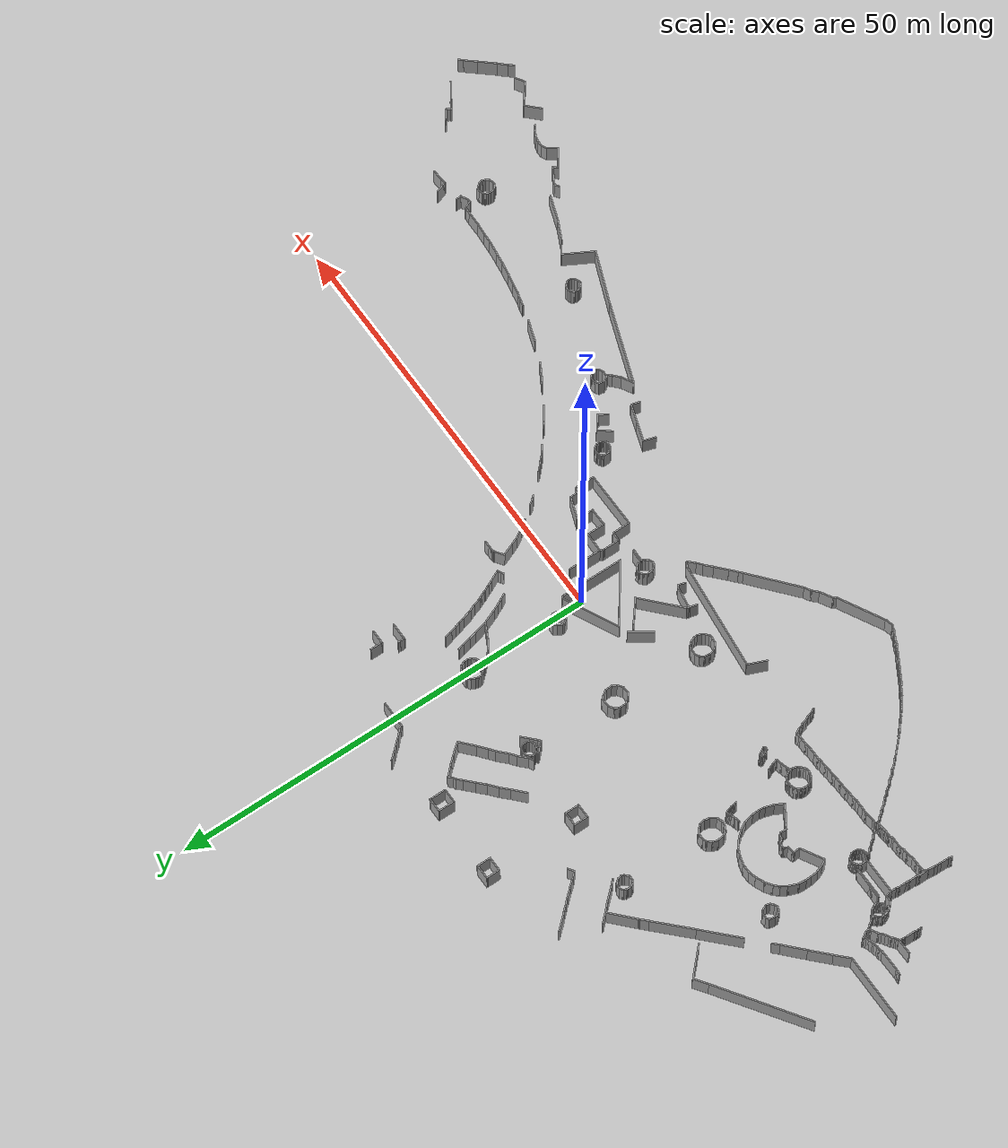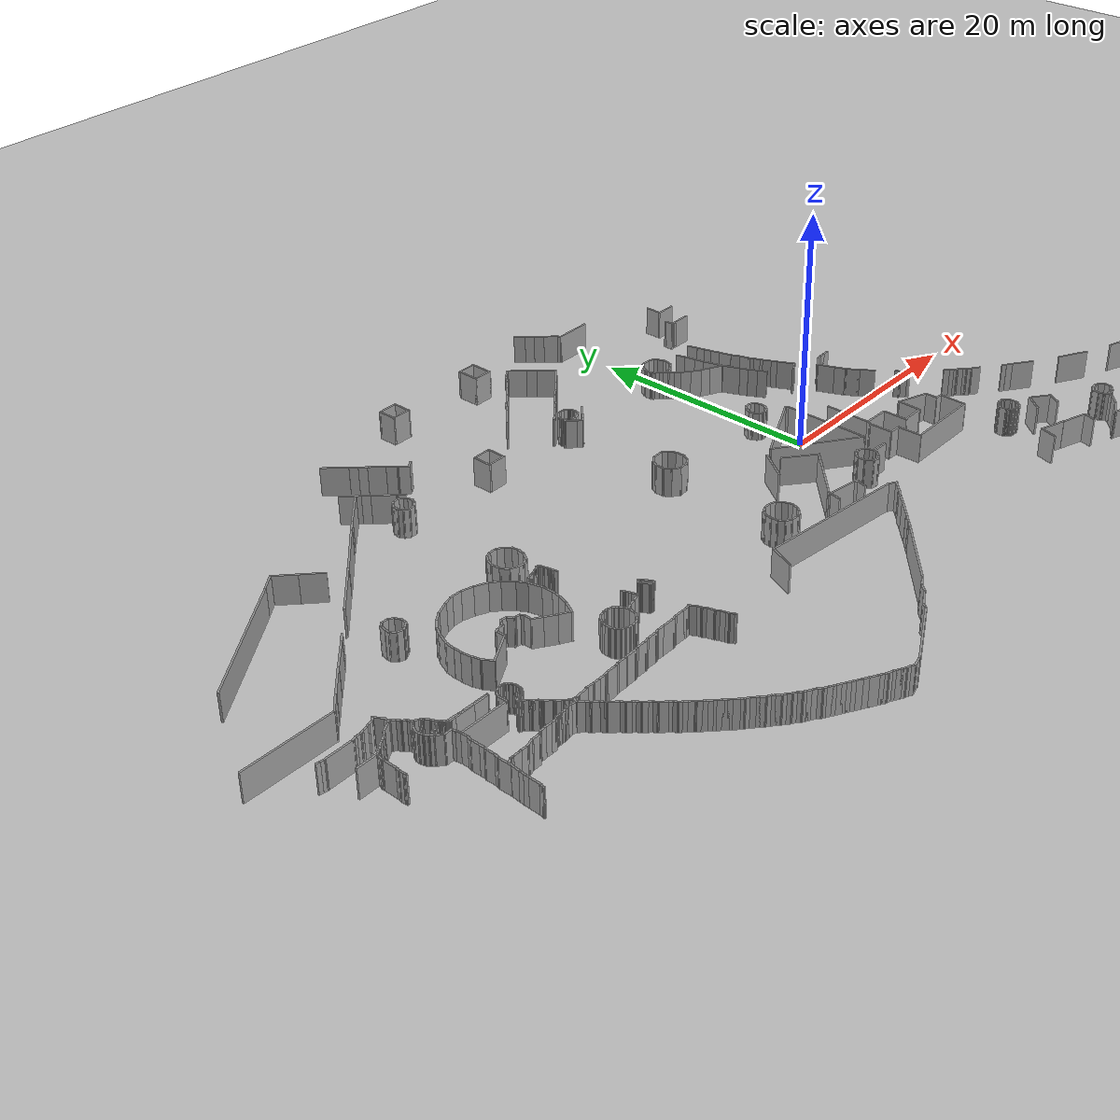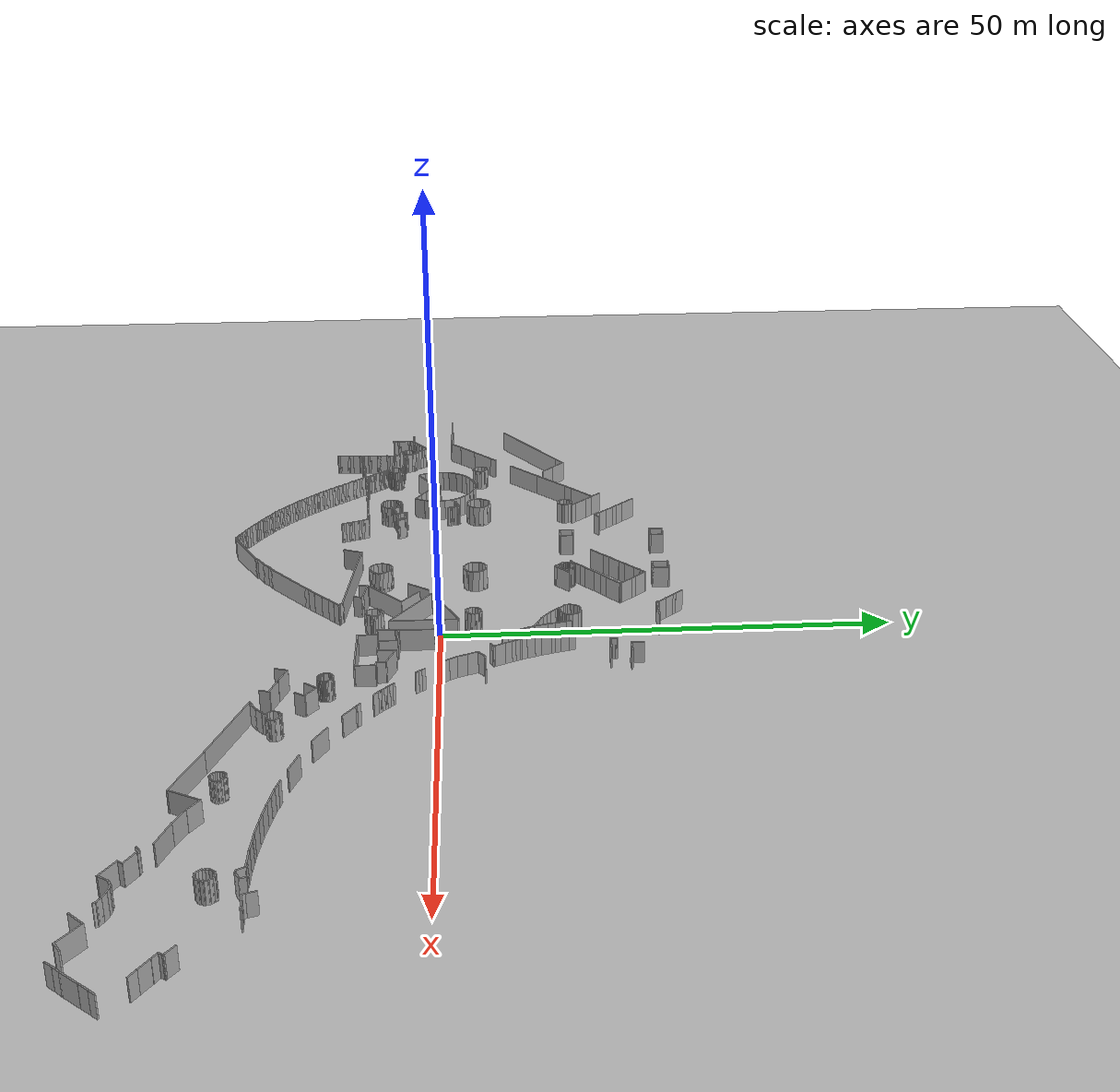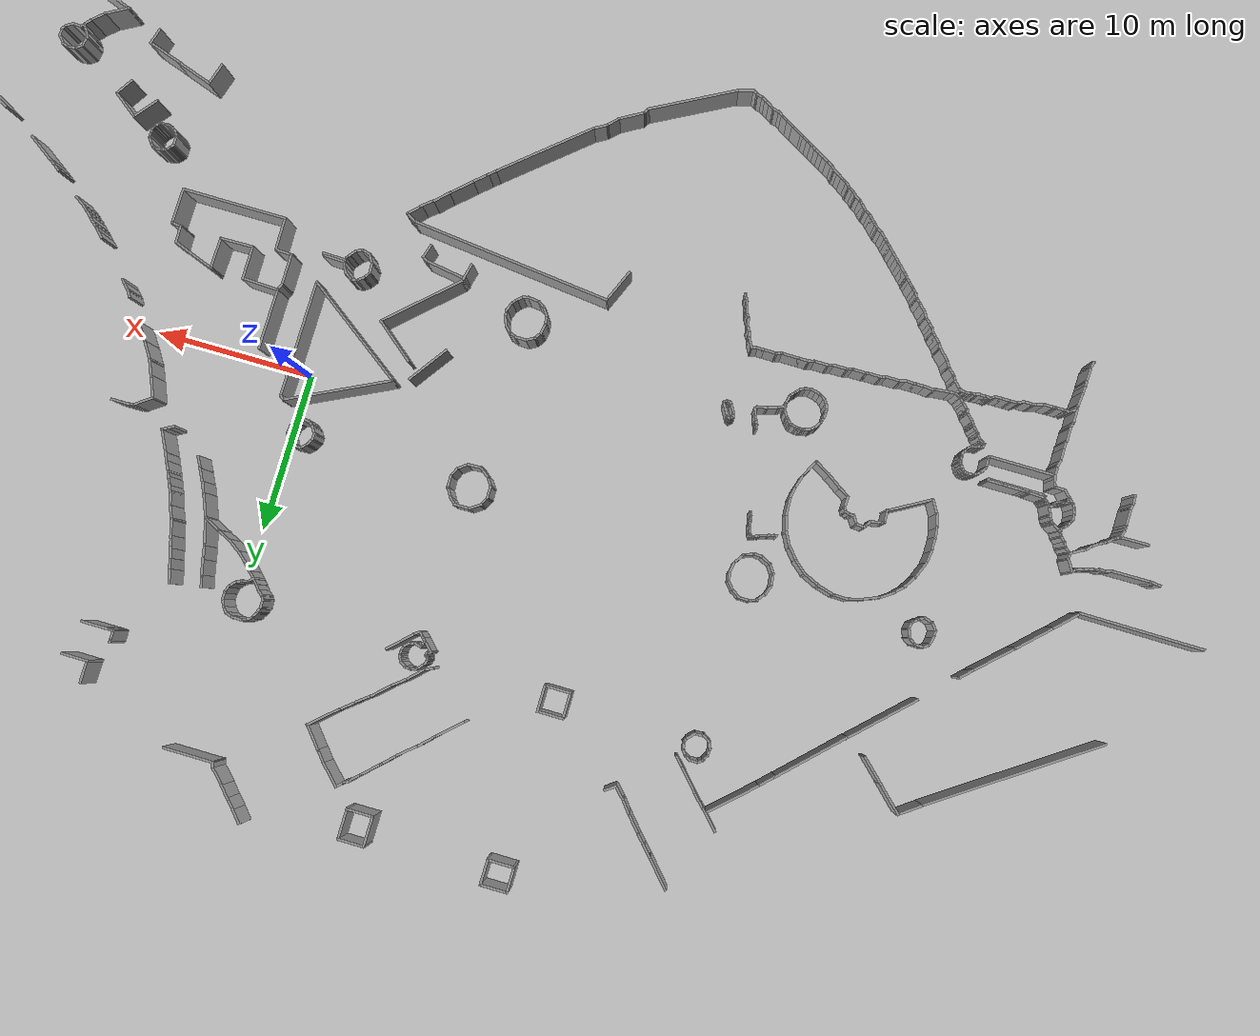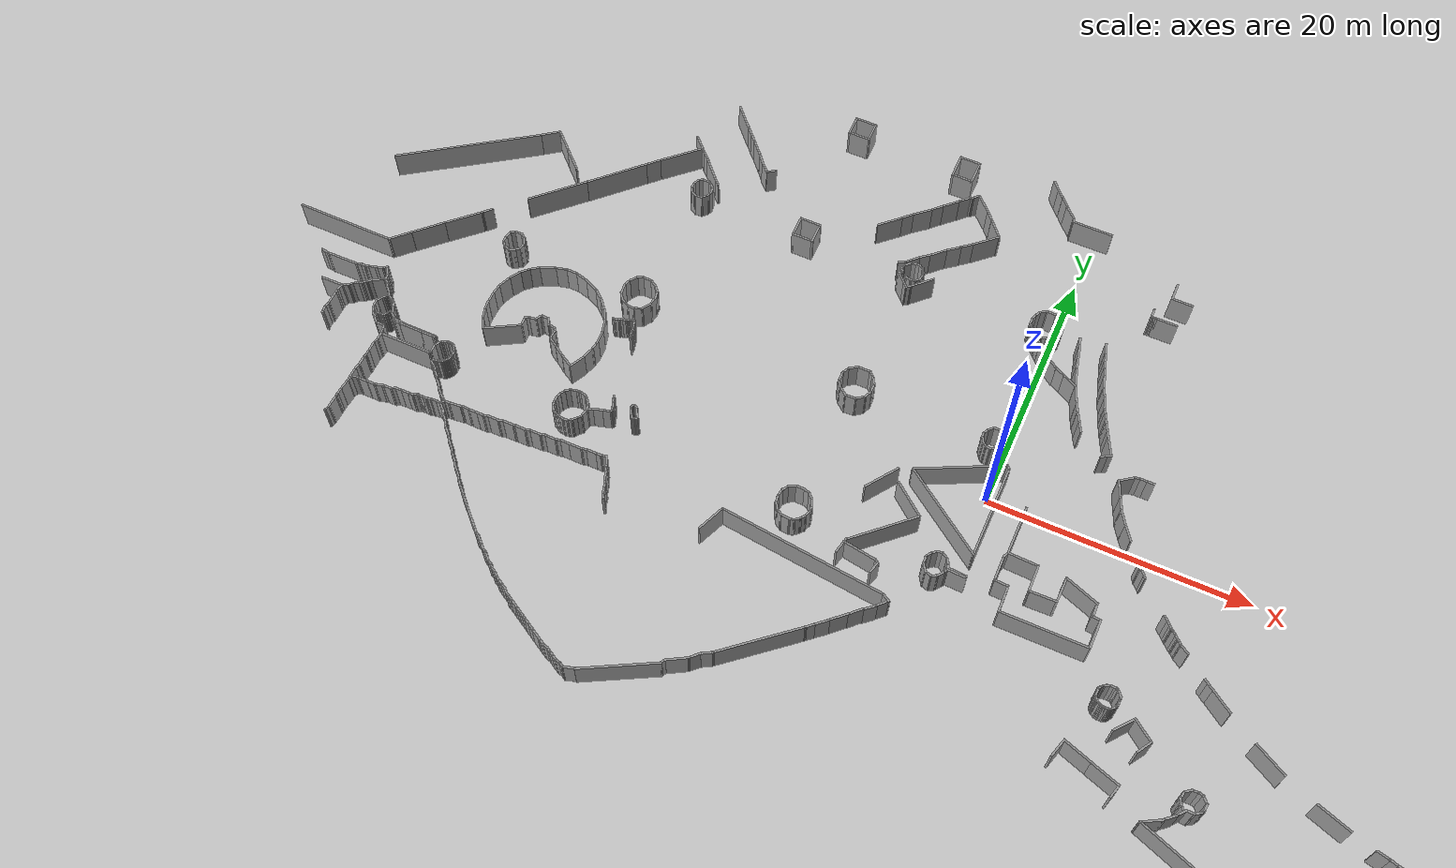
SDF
<sdf version="1.6">
 <world name="default">
  <light name="sun" type="directional">
   <pose>0 0 10 0 -0 0</pose>
   <diffuse>0.8 0.8 0.8 1</diffuse>
   <specular>0.1 0.1 0.1 1</specular>
   <attenuation>
    <range>1000</range>
    <constant>0.9</constant>
    <linear>0.01</linear>
    <quadratic>0.001</quadratic>
   </attenuation>
   <direction>-0.5 0.5 -1</direction>
  </light>
  <model name="ground_plane">
   <static>1</static>
   <link name="link">
    <collision name="collision">
     <geometry><plane><normal>0 0 1</normal><size>100 100</size></plane></geometry>
     <surface><friction><ode><mu>100</mu><mu2>50</mu2></ode></friction></surface>
    </collision>
    <visual name="visual">
     <cast_shadows>0</cast_shadows>
     <geometry><plane><normal>0 0 1</normal><size>100 100</size></plane></geometry>
     <material>
      <script><uri>file://media/materials/scripts/gazebo.material</uri><name>Gazebo/Grey</name></script>
     </material>
    </visual>
   </link>
  </model>
  <gravity>0 0 -9.8</gravity>
  <magnetic_field>6e-06 2.3e-05 -4.2e-05</magnetic_field>
  <atmosphere type="adiabatic"/>
  <physics name="default_physics" default="0" type="ode">
   <max_step_size>0.001</max_step_size>
   <real_time_factor>1</real_time_factor>
   <real_time_update_rate>1000</real_time_update_rate>
  </physics>
  <scene><ambient>0.4 0.4 0.4 1</ambient><background>0.7 0.7 0.7 1</background><shadows>1</shadows></scene>
  <spherical_coordinates>
   <surface_model>EARTH_WGS84</surface_model>
   <latitude_deg>0</latitude_deg>
   <longitude_deg>0</longitude_deg>
   <elevation>0</elevation>
   <heading_deg>0</heading_deg>
  </spherical_coordinates>
  <model name="scene">
   <pose>1.8013 -1.70593 0 0 -0 0</pose>
   <link name="Wall_100">
    <collision name="Wall_100_Collision">
     <geometry><box><size>0.5 0.15 2.5</size></box></geometry>
     <pose>0 0 1.25 0 -0 0</pose>
    </collision>
    <visual name="Wall_100_Visual">
     <pose>0 0 1.25 0 -0 0</pose>
     <geometry><box><size>0.5 0.15 2.5</size></box></geometry>
     <material>
      <script><uri>file://media/materials/scripts/gazebo.material</uri><name>Gazebo/Grey</name></script>
      <ambient>1 1 1 1</ambient>
     </material>
    </visual>
    <pose>-30.6917 -18.8012 0 0 -0 2.35619</pose>
   </link>
   <link name="Wall_1000">
    <collision name="Wall_1000_Collision">
     <geometry><box><size>0.594006 0.15 2.5</size></box></geometry>
     <pose>0 0 1.25 0 -0 0</pose>
    </collision>
    <visual name="Wall_1000_Visual">
     <pose>0 0 1.25 0 -0 0</pose>
     <geometry><box><size>0.594006 0.15 2.5</size></box></geometry>
     <material>
      <script><uri>file://media/materials/scripts/gazebo.material</uri><name>Gazebo/Grey</name></script>
      <ambient>1 1 1 1</ambient>
     </material>
    </visual>
    <pose>-3.85892 -5.03542 0 0 -0 0.953422</pose>
   </link>
   <link name="Wall_1001">
    <collision name="Wall_1001_Collision">
     <geometry><box><size>0.604524 0.15 2.5</size></box></geometry>
     <pose>0 0 1.25 0 -0 0</pose>
    </collision>
    <visual name="Wall_1001_Visual">
     <pose>0 0 1.25 0 -0 0</pose>
     <geometry><box><size>0.604524 0.15 2.5</size></box></geometry>
     <material>
      <script><uri>file://media/materials/scripts/gazebo.material</uri><name>Gazebo/Grey</name></script>
      <ambient>1 1 1 1</ambient>
     </material>
    </visual>
    <pose>-3.54219 -4.71395 0 0 -0 0.666228</pose>
   </link>
   <link name="Wall_1002">
    <collision name="Wall_1002_Collision">
     <geometry><box><size>0.512288 0.15 2.5</size></box></geometry>
     <pose>0 0 1.25 0 -0 0</pose>
    </collision>
    <visual name="Wall_1002_Visual">
     <pose>0 0 1.25 0 -0 0</pose>
     <geometry><box><size>0.512288 0.15 2.5</size></box></geometry>
     <material>
      <script><uri>file://media/materials/scripts/gazebo.material</uri><name>Gazebo/Grey</name></script>
      <ambient>1 1 1 1</ambient>
     </material>
    </visual>
    <pose>-3.19308 -4.55312 0 0 -0 0.112678</pose>
   </link>
   <link name="Wall_1003">
    <collision name="Wall_1003_Collision">
     <geometry><box><size>0.605711 0.15 2.5</size></box></geometry>
     <pose>0 0 1.25 0 -0 0</pose>
    </collision>
    <visual name="Wall_1003_Visual">
     <pose>0 0 1.25 0 -0 0</pose>
     <geometry><box><size>0.605711 0.15 2.5</size></box></geometry>
     <material>
      <script><uri>file://media/materials/scripts/gazebo.material</uri><name>Gazebo/Grey</name></script>
      <ambient>1 1 1 1</ambient>
     </material>
    </visual>
    <pose>-2.83167 -4.65707 0 0 0 -0.577103</pose>
   </link>
   <link name="Wall_1005">
    <collision name="Wall_1005_Collision">
     <geometry><box><size>1.52737 0.15 2.5</size></box></geometry>
     <pose>0 0 1.25 0 -0 0</pose>
    </collision>
    <visual name="Wall_1005_Visual">
     <pose>0 0 1.25 0 -0 0</pose>
     <geometry><box><size>1.52737 0.15 2.5</size></box></geometry>
     <material>
      <script><uri>file://media/materials/scripts/gazebo.material</uri><name>Gazebo/Grey</name></script>
      <ambient>1 1 1 1</ambient>
     </material>
    </visual>
    <pose>-1.58332 -5.61312 0 0 0 -0.027727</pose>
   </link>
   <link name="Wall_1008">
    <collision name="Wall_1008_Collision">
     <geometry><box><size>0.651968 0.15 2.5</size></box></geometry>
     <pose>0 0 1.25 0 -0 0</pose>
    </collision>
    <visual name="Wall_1008_Visual">
     <pose>0 0 1.25 0 -0 0</pose>
     <geometry><box><size>0.651968 0.15 2.5</size></box></geometry>
     <material>
      <script><uri>file://media/materials/scripts/gazebo.material</uri><name>Gazebo/Grey</name></script>
      <ambient>1 1 1 1</ambient>
     </material>
    </visual>
    <pose>-2.86264 6.28005 0 0 -0 0.018912</pose>
   </link>
   <link name="Wall_1009">
    <collision name="Wall_1009_Collision">
     <geometry><box><size>0.560126 0.15 2.5</size></box></geometry>
     <pose>0 0 1.25 0 -0 0</pose>
    </collision>
    <visual name="Wall_1009_Visual">
     <pose>0 0 1.25 0 -0 0</pose>
     <geometry><box><size>0.560126 0.15 2.5</size></box></geometry>
     <material>
      <script><uri>file://media/materials/scripts/gazebo.material</uri><name>Gazebo/Grey</name></script>
      <ambient>1 1 1 1</ambient>
     </material>
    </visual>
    <pose>-2.45331 6.16705 0 0 0 -0.611634</pose>
   </link>
   <link name="Wall_101">
    <collision name="Wall_101_Collision">
     <geometry><box><size>0.5 0.15 2.5</size></box></geometry>
     <pose>0 0 1.25 0 -0 0</pose>
    </collision>
    <visual name="Wall_101_Visual">
     <pose>0 0 1.25 0 -0 0</pose>
     <geometry><box><size>0.5 0.15 2.5</size></box></geometry>
     <material>
      <script><uri>file://media/materials/scripts/gazebo.material</uri><name>Gazebo/Grey</name></script>
      <ambient>1 1 1 1</ambient>
     </material>
    </visual>
    <pose>-30.967 -18.5899 0 0 -0 2.61799</pose>
   </link>
   <link name="Wall_1010">
    <collision name="Wall_1010_Collision">
     <geometry><box><size>0.579868 0.15 2.5</size></box></geometry>
     <pose>0 0 1.25 0 -0 0</pose>
    </collision>
    <visual name="Wall_1010_Visual">
     <pose>0 0 1.25 0 -0 0</pose>
     <geometry><box><size>0.579868 0.15 2.5</size></box></geometry>
     <material>
      <script><uri>file://media/materials/scripts/gazebo.material</uri><name>Gazebo/Grey</name></script>
      <ambient>1 1 1 1</ambient>
     </material>
    </visual>
    <pose>-2.20365 5.85471 0 0 0 -1.13225</pose>
   </link>
   <link name="Wall_1011">
    <collision name="Wall_1011_Collision">
     <geometry><box><size>0.650095 0.15 2.5</size></box></geometry>
     <pose>0 0 1.25 0 -0 0</pose>
    </collision>
    <visual name="Wall_1011_Visual">
     <pose>0 0 1.25 0 -0 0</pose>
     <geometry><box><size>0.650095 0.15 2.5</size></box></geometry>
     <material>
      <script><uri>file://media/materials/scripts/gazebo.material</uri><name>Gazebo/Grey</name></script>
      <ambient>1 1 1 1</ambient>
     </material>
    </visual>
    <pose>-2.12554 5.41071 0 0 0 -1.66137</pose>
   </link>
   <link name="Wall_1012">
    <collision name="Wall_1012_Collision">
     <geometry><box><size>0.65276 0.15 2.5</size></box></geometry>
     <pose>0 0 1.25 0 -0 0</pose>
    </collision>
    <visual name="Wall_1012_Visual">
     <pose>0 0 1.25 0 -0 0</pose>
     <geometry><box><size>0.65276 0.15 2.5</size></box></geometry>
     <material>
      <script><uri>file://media/materials/scripts/gazebo.material</uri><name>Gazebo/Grey</name></script>
      <ambient>1 1 1 1</ambient>
     </material>
    </visual>
    <pose>-2.28552 4.95725 0 0 0 -2.1945</pose>
   </link>
   <link name="Wall_1013">
    <collision name="Wall_1013_Collision">
     <geometry><box><size>0.595143 0.15 2.5</size></box></geometry>
     <pose>0 0 1.25 0 -0 0</pose>
    </collision>
    <visual name="Wall_1013_Visual">
     <pose>0 0 1.25 0 -0 0</pose>
     <geometry><box><size>0.595143 0.15 2.5</size></box></geometry>
     <material>
      <script><uri>file://media/materials/scripts/gazebo.material</uri><name>Gazebo/Grey</name></script>
      <ambient>1 1 1 1</ambient>
     </material>
    </visual>
    <pose>-2.62187 4.65356 0 0 0 -2.67745</pose>
   </link>
   <link name="Wall_1014">
    <collision name="Wall_1014_Collision">
     <geometry><box><size>0.497973 0.15 2.5</size></box></geometry>
     <pose>0 0 1.25 0 -0 0</pose>
    </collision>
    <visual name="Wall_1014_Visual">
     <pose>0 0 1.25 0 -0 0</pose>
     <geometry><box><size>0.497973 0.15 2.5</size></box></geometry>
     <material>
      <script><uri>file://media/materials/scripts/gazebo.material</uri><name>Gazebo/Grey</name></script>
      <ambient>1 1 1 1</ambient>
     </material>
    </visual>
    <pose>-2.98346 4.57976 0 0 -0 2.99259</pose>
   </link>
   <link name="Wall_1015">
    <collision name="Wall_1015_Collision">
     <geometry><box><size>0.476252 0.15 2.5</size></box></geometry>
     <pose>0 0 1.25 0 -0 0</pose>
    </collision>
    <visual name="Wall_1015_Visual">
     <pose>0 0 1.25 0 -0 0</pose>
     <geometry><box><size>0.476252 0.15 2.5</size></box></geometry>
     <material>
      <script><uri>file://media/materials/scripts/gazebo.material</uri><name>Gazebo/Grey</name></script>
      <ambient>1 1 1 1</ambient>
     </material>
    </visual>
    <pose>-3.28061 4.70079 0 0 -0 2.44473</pose>
   </link>
   <link name="Wall_1016">
    <collision name="Wall_1016_Collision">
     <geometry><box><size>0.634342 0.15 2.5</size></box></geometry>
     <pose>0 0 1.25 0 -0 0</pose>
    </collision>
    <visual name="Wall_1016_Visual">
     <pose>0 0 1.25 0 -0 0</pose>
     <geometry><box><size>0.634342 0.15 2.5</size></box></geometry>
     <material>
      <script><uri>file://media/materials/scripts/gazebo.material</uri><name>Gazebo/Grey</name></script>
      <ambient>1 1 1 1</ambient>
     </material>
    </visual>
    <pose>-3.54128 5.01225 0 0 -0 2.11837</pose>
   </link>
   <link name="Wall_1017">
    <collision name="Wall_1017_Collision">
     <geometry><box><size>0.505913 0.15 2.5</size></box></geometry>
     <pose>0 0 1.25 0 -0 0</pose>
    </collision>
    <visual name="Wall_1017_Visual">
     <pose>0 0 1.25 0 -0 0</pose>
     <geometry><box><size>0.505913 0.15 2.5</size></box></geometry>
     <material>
      <script><uri>file://media/materials/scripts/gazebo.material</uri><name>Gazebo/Grey</name></script>
      <ambient>1 1 1 1</ambient>
     </material>
    </visual>
    <pose>-3.67601 5.39697 0 0 -0 1.5661</pose>
   </link>
   <link name="Wall_1019">
    <collision name="Wall_1019_Collision">
     <geometry><box><size>0.587128 0.15 2.5</size></box></geometry>
     <pose>0 0 1.25 0 -0 0</pose>
    </collision>
    <visual name="Wall_1019_Visual">
     <pose>0 0 1.25 0 -0 0</pose>
     <geometry><box><size>0.587128 0.15 2.5</size></box></geometry>
     <material>
      <script><uri>file://media/materials/scripts/gazebo.material</uri><name>Gazebo/Grey</name></script>
      <ambient>1 1 1 1</ambient>
     </material>
    </visual>
    <pose>-3.56836 5.7751 0 0 -0 1.06017</pose>
   </link>
   <link name="Wall_1020">
    <collision name="Wall_1020_Collision">
     <geometry><box><size>0.536264 0.15 2.5</size></box></geometry>
     <pose>0 0 1.25 0 -0 0</pose>
    </collision>
    <visual name="Wall_1020_Visual">
     <pose>0 0 1.25 0 -0 0</pose>
     <geometry><box><size>0.536264 0.15 2.5</size></box></geometry>
     <material>
      <script><uri>file://media/materials/scripts/gazebo.material</uri><name>Gazebo/Grey</name></script>
      <ambient>1 1 1 1</ambient>
     </material>
    </visual>
    <pose>-3.32865 6.09652 0 0 -0 0.812245</pose>
   </link>
   <link name="Wall_1024">
    <collision name="Wall_1024_Collision">
     <geometry><box><size>1.09202 0.15 2.5</size></box></geometry>
     <pose>0 0 1.25 0 -0 0</pose>
    </collision>
    <visual name="Wall_1024_Visual">
     <pose>0 0 1.25 0 -0 0</pose>
     <geometry><box><size>1.09202 0.15 2.5</size></box></geometry>
     <material>
      <script><uri>file://media/materials/scripts/gazebo.material</uri><name>Gazebo/Grey</name></script>
      <ambient>1 1 1 1</ambient>
     </material>
    </visual>
    <pose>-13.5874 6.95876 0 0 -0 0.020155</pose>
   </link>
   <link name="Wall_1025">
    <collision name="Wall_1025_Collision">
     <geometry><box><size>0.652654 0.15 2.5</size></box></geometry>
     <pose>0 0 1.25 0 -0 0</pose>
    </collision>
    <visual name="Wall_1025_Visual">
     <pose>0 0 1.25 0 -0 0</pose>
     <geometry><box><size>0.652654 0.15 2.5</size></box></geometry>
     <material>
      <script><uri>file://media/materials/scripts/gazebo.material</uri><name>Gazebo/Grey</name></script>
      <ambient>1 1 1 1</ambient>
     </material>
    </visual>
    <pose>-12.9367 6.78315 0 0 0 -0.773619</pose>
   </link>
   <link name="Wall_1026">
    <collision name="Wall_1026_Collision">
     <geometry><box><size>0.767824 0.15 2.5</size></box></geometry>
     <pose>0 0 1.25 0 -0 0</pose>
    </collision>
    <visual name="Wall_1026_Visual">
     <pose>0 0 1.25 0 -0 0</pose>
     <geometry><box><size>0.767824 0.15 2.5</size></box></geometry>
     <material>
      <script><uri>file://media/materials/scripts/gazebo.material</uri><name>Gazebo/Grey</name></script>
      <ambient>1 1 1 1</ambient>
     </material>
    </visual>
    <pose>-12.6069 6.34298 0 0 0 -1.02827</pose>
   </link>
   <link name="Wall_1027">
    <collision name="Wall_1027_Collision">
     <geometry><box><size>0.886223 0.15 2.5</size></box></geometry>
     <pose>0 0 1.25 0 -0 0</pose>
    </collision>
    <visual name="Wall_1027_Visual">
     <pose>0 0 1.25 0 -0 0</pose>
     <geometry><box><size>0.886223 0.15 2.5</size></box></geometry>
     <material>
      <script><uri>file://media/materials/scripts/gazebo.material</uri><name>Gazebo/Grey</name></script>
      <ambient>1 1 1 1</ambient>
     </material>
    </visual>
    <pose>-12.4323 5.72012 0 0 0 -1.52984</pose>
   </link>
   <link name="Wall_1028">
    <collision name="Wall_1028_Collision">
     <geometry><box><size>0.730781 0.15 2.5</size></box></geometry>
     <pose>0 0 1.25 0 -0 0</pose>
    </collision>
    <visual name="Wall_1028_Visual">
     <pose>0 0 1.25 0 -0 0</pose>
     <geometry><box><size>0.730781 0.15 2.5</size></box></geometry>
     <material>
      <script><uri>file://media/materials/scripts/gazebo.material</uri><name>Gazebo/Grey</name></script>
      <ambient>1 1 1 1</ambient>
     </material>
    </visual>
    <pose>-12.5504 5.08958 0 0 0 -2.01077</pose>
   </link>
   <link name="Wall_1029">
    <collision name="Wall_1029_Collision">
     <geometry><box><size>0.844092 0.15 2.5</size></box></geometry>
     <pose>0 0 1.25 0 -0 0</pose>
    </collision>
    <visual name="Wall_1029_Visual">
     <pose>0 0 1.25 0 -0 0</pose>
     <geometry><box><size>0.844092 0.15 2.5</size></box></geometry>
     <material>
      <script><uri>file://media/materials/scripts/gazebo.material</uri><name>Gazebo/Grey</name></script>
      <ambient>1 1 1 1</ambient>
     </material>
    </visual>
    <pose>-12.9416 4.61776 0 0 0 -2.49497</pose>
   </link>
   <link name="Wall_103">
    <collision name="Wall_103_Collision">
     <geometry><box><size>0.5 0.15 2.5</size></box></geometry>
     <pose>0 0 1.25 0 -0 0</pose>
    </collision>
    <visual name="Wall_103_Visual">
     <pose>0 0 1.25 0 -0 0</pose>
     <geometry><box><size>0.5 0.15 2.5</size></box></geometry>
     <material>
      <script><uri>file://media/materials/scripts/gazebo.material</uri><name>Gazebo/Grey</name></script>
      <ambient>1 1 1 1</ambient>
     </material>
    </visual>
    <pose>-31.2423 -18.3787 0 0 -0 2.35619</pose>
   </link>
   <link name="Wall_1030">
    <collision name="Wall_1030_Collision">
     <geometry><box><size>0.938706 0.15 2.5</size></box></geometry>
     <pose>0 0 1.25 0 -0 0</pose>
    </collision>
    <visual name="Wall_1030_Visual">
     <pose>0 0 1.25 0 -0 0</pose>
     <geometry><box><size>0.938706 0.15 2.5</size></box></geometry>
     <material>
      <script><uri>file://media/materials/scripts/gazebo.material</uri><name>Gazebo/Grey</name></script>
      <ambient>1 1 1 1</ambient>
     </material>
    </visual>
    <pose>-13.6218 4.38521 0 0 0 -3.08209</pose>
   </link>
   <link name="Wall_1031">
    <collision name="Wall_1031_Collision">
     <geometry><box><size>0.896759 0.15 2.5</size></box></geometry>
     <pose>0 0 1.25 0 -0 0</pose>
    </collision>
    <visual name="Wall_1031_Visual">
     <pose>0 0 1.25 0 -0 0</pose>
     <geometry><box><size>0.896759 0.15 2.5</size></box></geometry>
     <material>
      <script><uri>file://media/materials/scripts/gazebo.material</uri><name>Gazebo/Grey</name></script>
      <ambient>1 1 1 1</ambient>
     </material>
    </visual>
    <pose>-14.317 4.59433 0 0 -0 2.4692</pose>
   </link>
   <link name="Wall_1032">
    <collision name="Wall_1032_Collision">
     <geometry><box><size>0.739141 0.15 2.5</size></box></geometry>
     <pose>0 0 1.25 0 -0 0</pose>
    </collision>
    <visual name="Wall_1032_Visual">
     <pose>0 0 1.25 0 -0 0</pose>
     <geometry><box><size>0.739141 0.15 2.5</size></box></geometry>
     <material>
      <script><uri>file://media/materials/scripts/gazebo.material</uri><name>Gazebo/Grey</name></script>
      <ambient>1 1 1 1</ambient>
     </material>
    </visual>
    <pose>-14.7794 5.07369 0 0 -0 2.14828</pose>
   </link>
   <link name="Wall_1033">
    <collision name="Wall_1033_Collision">
     <geometry><box><size>0.871473 0.15 2.5</size></box></geometry>
     <pose>0 0 1.25 0 -0 0</pose>
    </collision>
    <visual name="Wall_1033_Visual">
     <pose>0 0 1.25 0 -0 0</pose>
     <geometry><box><size>0.871473 0.15 2.5</size></box></geometry>
     <material>
      <script><uri>file://media/materials/scripts/gazebo.material</uri><name>Gazebo/Grey</name></script>
      <ambient>1 1 1 1</ambient>
     </material>
    </visual>
    <pose>-14.935 5.68121 0 0 -0 1.58254</pose>
   </link>
   <link name="Wall_1034">
    <collision name="Wall_1034_Collision">
     <geometry><box><size>0.716222 0.15 2.5</size></box></geometry>
     <pose>0 0 1.25 0 -0 0</pose>
    </collision>
    <visual name="Wall_1034_Visual">
     <pose>0 0 1.25 0 -0 0</pose>
     <geometry><box><size>0.716222 0.15 2.5</size></box></geometry>
     <material>
      <script><uri>file://media/materials/scripts/gazebo.material</uri><name>Gazebo/Grey</name></script>
      <ambient>1 1 1 1</ambient>
     </material>
    </visual>
    <pose>-14.8147 6.29132 0 0 -0 1.07786</pose>
   </link>
   <link name="Wall_1035">
    <collision name="Wall_1035_Collision">
     <geometry><box><size>0.862117 0.15 2.5</size></box></geometry>
     <pose>0 0 1.25 0 -0 0</pose>
    </collision>
    <visual name="Wall_1035_Visual">
     <pose>0 0 1.25 0 -0 0</pose>
     <geometry><box><size>0.862117 0.15 2.5</size></box></geometry>
     <material>
      <script><uri>file://media/materials/scripts/gazebo.material</uri><name>Gazebo/Grey</name></script>
      <ambient>1 1 1 1</ambient>
     </material>
    </visual>
    <pose>-14.3968 6.74241 0 0 -0 0.602178</pose>
   </link>
   <link name="Wall_1039">
    <collision name="Wall_1039_Collision">
     <geometry><box><size>0.75 0.15 2.5</size></box></geometry>
     <pose>0 0 1.25 0 -0 0</pose>
    </collision>
    <visual name="Wall_1039_Visual">
     <pose>0 0 1.25 0 -0 0</pose>
     <geometry><box><size>0.75 0.15 2.5</size></box></geometry>
     <material>
      <script><uri>file://media/materials/scripts/gazebo.material</uri><name>Gazebo/Grey</name></script>
      <ambient>1 1 1 1</ambient>
     </material>
    </visual>
    <pose>-14.0601 -3.93279 0 0 -0 0</pose>
   </link>
   <link name="Wall_104">
    <collision name="Wall_104_Collision">
     <geometry><box><size>0.5 0.15 2.5</size></box></geometry>
     <pose>0 0 1.25 0 -0 0</pose>
    </collision>
    <visual name="Wall_104_Visual">
     <pose>0 0 1.25 0 -0 0</pose>
     <geometry><box><size>0.5 0.15 2.5</size></box></geometry>
     <material>
      <script><uri>file://media/materials/scripts/gazebo.material</uri><name>Gazebo/Grey</name></script>
      <ambient>1 1 1 1</ambient>
     </material>
    </visual>
    <pose>-31.5176 -18.1674 0 0 -0 2.61799</pose>
   </link>
   <link name="Wall_1040">
    <collision name="Wall_1040_Collision">
     <geometry><box><size>0.610594 0.15 2.5</size></box></geometry>
     <pose>0 0 1.25 0 -0 0</pose>
    </collision>
    <visual name="Wall_1040_Visual">
     <pose>0 0 1.25 0 -0 0</pose>
     <geometry><box><size>0.610594 0.15 2.5</size></box></geometry>
     <material>
      <script><uri>file://media/materials/scripts/gazebo.material</uri><name>Gazebo/Grey</name></script>
      <ambient>1 1 1 1</ambient>
     </material>
    </visual>
    <pose>-13.5436 -4.01131 0 0 0 -0.347913</pose>
   </link>
   <link name="Wall_1041">
    <collision name="Wall_1041_Collision">
     <geometry><box><size>0.643015 0.15 2.5</size></box></geometry>
     <pose>0 0 1.25 0 -0 0</pose>
    </collision>
    <visual name="Wall_1041_Visual">
     <pose>0 0 1.25 0 -0 0</pose>
     <geometry><box><size>0.643015 0.15 2.5</size></box></geometry>
     <material>
      <script><uri>file://media/materials/scripts/gazebo.material</uri><name>Gazebo/Grey</name></script>
      <ambient>1 1 1 1</ambient>
     </material>
    </visual>
    <pose>-13.1518 -4.27225 0 0 0 -0.833122</pose>
   </link>
   <link name="Wall_1042">
    <collision name="Wall_1042_Collision">
     <geometry><box><size>0.686861 0.15 2.5</size></box></geometry>
     <pose>0 0 1.25 0 -0 0</pose>
    </collision>
    <visual name="Wall_1042_Visual">
     <pose>0 0 1.25 0 -0 0</pose>
     <geometry><box><size>0.686861 0.15 2.5</size></box></geometry>
     <material>
      <script><uri>file://media/materials/scripts/gazebo.material</uri><name>Gazebo/Grey</name></script>
      <ambient>1 1 1 1</ambient>
     </material>
    </visual>
    <pose>-12.8718 -4.70182 0 0 0 -1.16988</pose>
   </link>
   <link name="Wall_1043">
    <collision name="Wall_1043_Collision">
     <geometry><box><size>0.546988 0.15 2.5</size></box></geometry>
     <pose>0 0 1.25 0 -0 0</pose>
    </collision>
    <visual name="Wall_1043_Visual">
     <pose>0 0 1.25 0 -0 0</pose>
     <geometry><box><size>0.546988 0.15 2.5</size></box></geometry>
     <material>
      <script><uri>file://media/materials/scripts/gazebo.material</uri><name>Gazebo/Grey</name></script>
      <ambient>1 1 1 1</ambient>
     </material>
    </visual>
    <pose>-12.7444 -5.15565 0 0 0 -1.45643</pose>
   </link>
   <link name="Wall_1044">
    <collision name="Wall_1044_Collision">
     <geometry><box><size>0.701474 0.15 2.5</size></box></geometry>
     <pose>0 0 1.25 0 -0 0</pose>
    </collision>
    <visual name="Wall_1044_Visual">
     <pose>0 0 1.25 0 -0 0</pose>
     <geometry><box><size>0.701474 0.15 2.5</size></box></geometry>
     <material>
      <script><uri>file://media/materials/scripts/gazebo.material</uri><name>Gazebo/Grey</name></script>
      <ambient>1 1 1 1</ambient>
     </material>
    </visual>
    <pose>-12.8166 -5.60224 0 0 0 -1.92224</pose>
   </link>
   <link name="Wall_1045">
    <collision name="Wall_1045_Collision">
     <geometry><box><size>0.529759 0.15 2.5</size></box></geometry>
     <pose>0 0 1.25 0 -0 0</pose>
    </collision>
    <visual name="Wall_1045_Visual">
     <pose>0 0 1.25 0 -0 0</pose>
     <geometry><box><size>0.529759 0.15 2.5</size></box></geometry>
     <material>
      <script><uri>file://media/materials/scripts/gazebo.material</uri><name>Gazebo/Grey</name></script>
      <ambient>1 1 1 1</ambient>
     </material>
    </visual>
    <pose>-13.0236 -6.00702 0 0 0 -2.26529</pose>
   </link>
   <link name="Wall_1046">
    <collision name="Wall_1046_Collision">
     <geometry><box><size>0.59053 0.15 2.5</size></box></geometry>
     <pose>0 0 1.25 0 -0 0</pose>
    </collision>
    <visual name="Wall_1046_Visual">
     <pose>0 0 1.25 0 -0 0</pose>
     <geometry><box><size>0.59053 0.15 2.5</size></box></geometry>
     <material>
      <script><uri>file://media/materials/scripts/gazebo.material</uri><name>Gazebo/Grey</name></script>
      <ambient>1 1 1 1</ambient>
     </material>
    </visual>
    <pose>-13.3053 -6.29343 0 0 0 -2.44982</pose>
   </link>
   <link name="Wall_1047">
    <collision name="Wall_1047_Collision">
     <geometry><box><size>0.492926 0.15 2.5</size></box></geometry>
     <pose>0 0 1.25 0 -0 0</pose>
    </collision>
    <visual name="Wall_1047_Visual">
     <pose>0 0 1.25 0 -0 0</pose>
     <geometry><box><size>0.492926 0.15 2.5</size></box></geometry>
     <material>
      <script><uri>file://media/materials/scripts/gazebo.material</uri><name>Gazebo/Grey</name></script>
      <ambient>1 1 1 1</ambient>
     </material>
    </visual>
    <pose>-13.6421 -6.4814 0 0 0 -2.9183</pose>
   </link>
   <link name="Wall_1048">
    <collision name="Wall_1048_Collision">
     <geometry><box><size>0.833074 0.15 2.5</size></box></geometry>
     <pose>0 0 1.25 0 -0 0</pose>
    </collision>
    <visual name="Wall_1048_Visual">
     <pose>0 0 1.25 0 -0 0</pose>
     <geometry><box><size>0.833074 0.15 2.5</size></box></geometry>
     <material>
      <script><uri>file://media/materials/scripts/gazebo.material</uri><name>Gazebo/Grey</name></script>
      <ambient>1 1 1 1</ambient>
     </material>
    </visual>
    <pose>-14.1391 -6.48056 0 0 -0 3.02773</pose>
   </link>
   <link name="Wall_1049">
    <collision name="Wall_1049_Collision">
     <geometry><box><size>0.630579 0.15 2.5</size></box></geometry>
     <pose>0 0 1.25 0 -0 0</pose>
    </collision>
    <visual name="Wall_1049_Visual">
     <pose>0 0 1.25 0 -0 0</pose>
     <geometry><box><size>0.630579 0.15 2.5</size></box></geometry>
     <material>
      <script><uri>file://media/materials/scripts/gazebo.material</uri><name>Gazebo/Grey</name></script>
      <ambient>1 1 1 1</ambient>
     </material>
    </visual>
    <pose>-14.6775 -6.31666 0 0 -0 2.54708</pose>
   </link>
   <link name="Wall_105">
    <collision name="Wall_105_Collision">
     <geometry><box><size>0.5 0.15 2.5</size></box></geometry>
     <pose>0 0 1.25 0 -0 0</pose>
    </collision>
    <visual name="Wall_105_Visual">
     <pose>0 0 1.25 0 -0 0</pose>
     <geometry><box><size>0.5 0.15 2.5</size></box></geometry>
     <material>
      <script><uri>file://media/materials/scripts/gazebo.material</uri><name>Gazebo/Grey</name></script>
      <ambient>1 1 1 1</ambient>
     </material>
    </visual>
    <pose>-31.7929 -17.9562 0 0 -0 2.35619</pose>
   </link>
   <link name="Wall_1050">
    <collision name="Wall_1050_Collision">
     <geometry><box><size>0.728776 0.15 2.5</size></box></geometry>
     <pose>0 0 1.25 0 -0 0</pose>
    </collision>
    <visual name="Wall_1050_Visual">
     <pose>0 0 1.25 0 -0 0</pose>
     <geometry><box><size>0.728776 0.15 2.5</size></box></geometry>
     <material>
      <script><uri>file://media/materials/scripts/gazebo.material</uri><name>Gazebo/Grey</name></script>
      <ambient>1 1 1 1</ambient>
     </material>
    </visual>
    <pose>-15.0388 -5.93293 0 0 -0 2.1658</pose>
   </link>
   <link name="Wall_1051">
    <collision name="Wall_1051_Collision">
     <geometry><box><size>0.665895 0.15 2.5</size></box></geometry>
     <pose>0 0 1.25 0 -0 0</pose>
    </collision>
    <visual name="Wall_1051_Visual">
     <pose>0 0 1.25 0 -0 0</pose>
     <geometry><box><size>0.665895 0.15 2.5</size></box></geometry>
     <material>
      <script><uri>file://media/materials/scripts/gazebo.material</uri><name>Gazebo/Grey</name></script>
      <ambient>1 1 1 1</ambient>
     </material>
    </visual>
    <pose>-15.2373 -5.43672 0 0 -0 1.67477</pose>
   </link>
   <link name="Wall_1052">
    <collision name="Wall_1052_Collision">
     <geometry><box><size>0.73529 0.15 2.5</size></box></geometry>
     <pose>0 0 1.25 0 -0 0</pose>
    </collision>
    <visual name="Wall_1052_Visual">
     <pose>0 0 1.25 0 -0 0</pose>
     <geometry><box><size>0.73529 0.15 2.5</size></box></geometry>
     <material>
      <script><uri>file://media/materials/scripts/gazebo.material</uri><name>Gazebo/Grey</name></script>
      <ambient>1 1 1 1</ambient>
     </material>
    </visual>
    <pose>-15.2232 -4.89188 0 0 -0 1.39796</pose>
   </link>
   <link name="Wall_1053">
    <collision name="Wall_1053_Collision">
     <geometry><box><size>0.626331 0.15 2.5</size></box></geometry>
     <pose>0 0 1.25 0 -0 0</pose>
    </collision>
    <visual name="Wall_1053_Visual">
     <pose>0 0 1.25 0 -0 0</pose>
     <geometry><box><size>0.626331 0.15 2.5</size></box></geometry>
     <material>
      <script><uri>file://media/materials/scripts/gazebo.material</uri><name>Gazebo/Grey</name></script>
      <ambient>1 1 1 1</ambient>
     </material>
    </visual>
    <pose>-15.0325 -4.40458 0 0 -0 0.989265</pose>
   </link>
   <link name="Wall_1054">
    <collision name="Wall_1054_Collision">
     <geometry><box><size>0.644301 0.15 2.5</size></box></geometry>
     <pose>0 0 1.25 0 -0 0</pose>
    </collision>
    <visual name="Wall_1054_Visual">
     <pose>0 0 1.25 0 -0 0</pose>
     <geometry><box><size>0.644301 0.15 2.5</size></box></geometry>
     <material>
      <script><uri>file://media/materials/scripts/gazebo.material</uri><name>Gazebo/Grey</name></script>
      <ambient>1 1 1 1</ambient>
     </material>
    </visual>
    <pose>-14.6781 -4.08216 0 0 -0 0.522787</pose>
   </link>
   <link name="Wall_1058">
    <collision name="Wall_1058_Collision">
     <geometry><box><size>0.609681 0.15 2.5</size></box></geometry>
     <pose>0 0 1.25 0 -0 0</pose>
    </collision>
    <visual name="Wall_1058_Visual">
     <pose>0 0 1.25 0 -0 0</pose>
     <geometry><box><size>0.609681 0.15 2.5</size></box></geometry>
     <material>
      <script><uri>file://media/materials/scripts/gazebo.material</uri><name>Gazebo/Grey</name></script>
      <ambient>1 1 1 1</ambient>
     </material>
    </visual>
    <pose>-31.3527 17.7342 0 0 0 -0.02377</pose>
   </link>
   <link name="Wall_1059">
    <collision name="Wall_1059_Collision">
     <geometry><box><size>0.499764 0.15 2.5</size></box></geometry>
     <pose>0 0 1.25 0 -0 0</pose>
    </collision>
    <visual name="Wall_1059_Visual">
     <pose>0 0 1.25 0 -0 0</pose>
     <geometry><box><size>0.499764 0.15 2.5</size></box></geometry>
     <material>
      <script><uri>file://media/materials/scripts/gazebo.material</uri><name>Gazebo/Grey</name></script>
      <ambient>1 1 1 1</ambient>
     </material>
    </visual>
    <pose>-30.9759 17.6453 0 0 0 -0.570304</pose>
   </link>
   <link name="Wall_106">
    <collision name="Wall_106_Collision">
     <geometry><box><size>0.5 0.15 2.5</size></box></geometry>
     <pose>0 0 1.25 0 -0 0</pose>
    </collision>
    <visual name="Wall_106_Visual">
     <pose>0 0 1.25 0 -0 0</pose>
     <geometry><box><size>0.5 0.15 2.5</size></box></geometry>
     <material>
      <script><uri>file://media/materials/scripts/gazebo.material</uri><name>Gazebo/Grey</name></script>
      <ambient>1 1 1 1</ambient>
     </material>
    </visual>
    <pose>-32.0404 -17.7087 0 0 -0 2.35619</pose>
   </link>
   <link name="Wall_1060">
    <collision name="Wall_1060_Collision">
     <geometry><box><size>0.513496 0.15 2.5</size></box></geometry>
     <pose>0 0 1.25 0 -0 0</pose>
    </collision>
    <visual name="Wall_1060_Visual">
     <pose>0 0 1.25 0 -0 0</pose>
     <geometry><box><size>0.513496 0.15 2.5</size></box></geometry>
     <material>
      <script><uri>file://media/materials/scripts/gazebo.material</uri><name>Gazebo/Grey</name></script>
      <ambient>1 1 1 1</ambient>
     </material>
    </visual>
    <pose>-30.7109 17.4148 0 0 0 -0.942184</pose>
   </link>
   <link name="Wall_1061">
    <collision name="Wall_1061_Collision">
     <geometry><box><size>0.60909 0.15 2.5</size></box></geometry>
     <pose>0 0 1.25 0 -0 0</pose>
    </collision>
    <visual name="Wall_1061_Visual">
     <pose>0 0 1.25 0 -0 0</pose>
     <geometry><box><size>0.60909 0.15 2.5</size></box></geometry>
     <material>
      <script><uri>file://media/materials/scripts/gazebo.material</uri><name>Gazebo/Grey</name></script>
      <ambient>1 1 1 1</ambient>
     </material>
    </visual>
    <pose>-30.5621 17.0403 0 0 0 -1.43553</pose>
   </link>
   <link name="Wall_1062">
    <collision name="Wall_1062_Collision">
     <geometry><box><size>0.477971 0.15 2.5</size></box></geometry>
     <pose>0 0 1.25 0 -0 0</pose>
    </collision>
    <visual name="Wall_1062_Visual">
     <pose>0 0 1.25 0 -0 0</pose>
     <geometry><box><size>0.477971 0.15 2.5</size></box></geometry>
     <material>
      <script><uri>file://media/materials/scripts/gazebo.material</uri><name>Gazebo/Grey</name></script>
      <ambient>1 1 1 1</ambient>
     </material>
    </visual>
    <pose>-30.5891 16.664 0 0 0 -2.00416</pose>
   </link>
   <link name="Wall_1063">
    <collision name="Wall_1063_Collision">
     <geometry><box><size>0.690792 0.15 2.5</size></box></geometry>
     <pose>0 0 1.25 0 -0 0</pose>
    </collision>
    <visual name="Wall_1063_Visual">
     <pose>0 0 1.25 0 -0 0</pose>
     <geometry><box><size>0.690792 0.15 2.5</size></box></geometry>
     <material>
      <script><uri>file://media/materials/scripts/gazebo.material</uri><name>Gazebo/Grey</name></script>
      <ambient>1 1 1 1</ambient>
     </material>
    </visual>
    <pose>-30.8373 16.323 0 0 0 -2.35098</pose>
   </link>
   <link name="Wall_1064">
    <collision name="Wall_1064_Collision">
     <geometry><box><size>0.706181 0.15 2.5</size></box></geometry>
     <pose>0 0 1.25 0 -0 0</pose>
    </collision>
    <visual name="Wall_1064_Visual">
     <pose>0 0 1.25 0 -0 0</pose>
     <geometry><box><size>0.706181 0.15 2.5</size></box></geometry>
     <material>
      <script><uri>file://media/materials/scripts/gazebo.material</uri><name>Gazebo/Grey</name></script>
      <ambient>1 1 1 1</ambient>
     </material>
    </visual>
    <pose>-31.2946 16.1238 0 0 0 -3.11637</pose>
   </link>
   <link name="Wall_1065">
    <collision name="Wall_1065_Collision">
     <geometry><box><size>0.614202 0.15 2.5</size></box></geometry>
     <pose>0 0 1.25 0 -0 0</pose>
    </collision>
    <visual name="Wall_1065_Visual">
     <pose>0 0 1.25 0 -0 0</pose>
     <geometry><box><size>0.614202 0.15 2.5</size></box></geometry>
     <material>
      <script><uri>file://media/materials/scripts/gazebo.material</uri><name>Gazebo/Grey</name></script>
      <ambient>1 1 1 1</ambient>
     </material>
    </visual>
    <pose>-31.7678 16.2314 0 0 -0 2.57012</pose>
   </link>
   <link name="Wall_1066">
    <collision name="Wall_1066_Collision">
     <geometry><box><size>0.590807 0.15 2.5</size></box></geometry>
     <pose>0 0 1.25 0 -0 0</pose>
    </collision>
    <visual name="Wall_1066_Visual">
     <pose>0 0 1.25 0 -0 0</pose>
     <geometry><box><size>0.590807 0.15 2.5</size></box></geometry>
     <material>
      <script><uri>file://media/materials/scripts/gazebo.material</uri><name>Gazebo/Grey</name></script>
      <ambient>1 1 1 1</ambient>
     </material>
    </visual>
    <pose>-32.0354 16.561 0 0 -0 1.95851</pose>
   </link>
   <link name="Wall_1067">
    <collision name="Wall_1067_Collision">
     <geometry><box><size>0.570884 0.15 2.5</size></box></geometry>
     <pose>0 0 1.25 0 -0 0</pose>
    </collision>
    <visual name="Wall_1067_Visual">
     <pose>0 0 1.25 0 -0 0</pose>
     <geometry><box><size>0.570884 0.15 2.5</size></box></geometry>
     <material>
      <script><uri>file://media/materials/scripts/gazebo.material</uri><name>Gazebo/Grey</name></script>
      <ambient>1 1 1 1</ambient>
     </material>
    </visual>
    <pose>-32.1184 16.9748 0 0 -0 1.51706</pose>
   </link>
   <link name="Wall_1068">
    <collision name="Wall_1068_Collision">
     <geometry><box><size>0.555832 0.15 2.5</size></box></geometry>
     <pose>0 0 1.25 0 -0 0</pose>
    </collision>
    <visual name="Wall_1068_Visual">
     <pose>0 0 1.25 0 -0 0</pose>
     <geometry><box><size>0.555832 0.15 2.5</size></box></geometry>
     <material>
      <script><uri>file://media/materials/scripts/gazebo.material</uri><name>Gazebo/Grey</name></script>
      <ambient>1 1 1 1</ambient>
     </material>
    </visual>
    <pose>-32.0034 17.3651 0 0 -0 1.09587</pose>
   </link>
   <link name="Wall_1069">
    <collision name="Wall_1069_Collision">
     <geometry><box><size>0.458441 0.15 2.5</size></box></geometry>
     <pose>0 0 1.25 0 -0 0</pose>
    </collision>
    <visual name="Wall_1069_Visual">
     <pose>0 0 1.25 0 -0 0</pose>
     <geometry><box><size>0.458441 0.15 2.5</size></box></geometry>
     <material>
      <script><uri>file://media/materials/scripts/gazebo.material</uri><name>Gazebo/Grey</name></script>
      <ambient>1 1 1 1</ambient>
     </material>
    </visual>
    <pose>-31.7948 17.6333 0 0 -0 0.605884</pose>
   </link>
   <link name="Wall_107">
    <collision name="Wall_107_Collision">
     <geometry><box><size>0.5 0.15 2.5</size></box></geometry>
     <pose>0 0 1.25 0 -0 0</pose>
    </collision>
    <visual name="Wall_107_Visual">
     <pose>0 0 1.25 0 -0 0</pose>
     <geometry><box><size>0.5 0.15 2.5</size></box></geometry>
     <material>
      <script><uri>file://media/materials/scripts/gazebo.material</uri><name>Gazebo/Grey</name></script>
      <ambient>1 1 1 1</ambient>
     </material>
    </visual>
    <pose>-32.3157 -17.4975 0 0 -0 2.61799</pose>
   </link>
   <link name="Wall_1077">
    <collision name="Wall_1077_Collision">
     <geometry><box><size>0.805347 0.15 2.5</size></box></geometry>
     <pose>0 0 1.25 0 -0 0</pose>
    </collision>
    <visual name="Wall_1077_Visual">
     <pose>0 0 1.25 0 -0 0</pose>
     <geometry><box><size>0.805347 0.15 2.5</size></box></geometry>
     <material>
      <script><uri>file://media/materials/scripts/gazebo.material</uri><name>Gazebo/Grey</name></script>
      <ambient>1 1 1 1</ambient>
     </material>
    </visual>
    <pose>-31.6018 7.55392 0 0 0 -0.01084</pose>
   </link>
   <link name="Wall_1078">
    <collision name="Wall_1078_Collision">
     <geometry><box><size>0.713111 0.15 2.5</size></box></geometry>
     <pose>0 0 1.25 0 -0 0</pose>
    </collision>
    <visual name="Wall_1078_Visual">
     <pose>0 0 1.25 0 -0 0</pose>
     <geometry><box><size>0.713111 0.15 2.5</size></box></geometry>
     <material>
      <script><uri>file://media/materials/scripts/gazebo.material</uri><name>Gazebo/Grey</name></script>
      <ambient>1 1 1 1</ambient>
     </material>
    </visual>
    <pose>-31.055 7.39654 0 0 0 -0.577971</pose>
   </link>
   <link name="Wall_1079">
    <collision name="Wall_1079_Collision">
     <geometry><box><size>0.762468 0.15 2.5</size></box></geometry>
     <pose>0 0 1.25 0 -0 0</pose>
    </collision>
    <visual name="Wall_1079_Visual">
     <pose>0 0 1.25 0 -0 0</pose>
     <geometry><box><size>0.762468 0.15 2.5</size></box></geometry>
     <material>
      <script><uri>file://media/materials/scripts/gazebo.material</uri><name>Gazebo/Grey</name></script>
      <ambient>1 1 1 1</ambient>
     </material>
    </visual>
    <pose>-30.6052 7.00854 0 0 0 -0.870597</pose>
   </link>
   <link name="Wall_108">
    <collision name="Wall_108_Collision">
     <geometry><box><size>0.5 0.15 2.5</size></box></geometry>
     <pose>0 0 1.25 0 -0 0</pose>
    </collision>
    <visual name="Wall_108_Visual">
     <pose>0 0 1.25 0 -0 0</pose>
     <geometry><box><size>0.5 0.15 2.5</size></box></geometry>
     <material>
      <script><uri>file://media/materials/scripts/gazebo.material</uri><name>Gazebo/Grey</name></script>
      <ambient>1 1 1 1</ambient>
     </material>
    </visual>
    <pose>-32.591 -17.2862 0 0 -0 2.35619</pose>
   </link>
   <link name="Wall_1080">
    <collision name="Wall_1080_Collision">
     <geometry><box><size>0.690732 0.15 2.5</size></box></geometry>
     <pose>0 0 1.25 0 -0 0</pose>
    </collision>
    <visual name="Wall_1080_Visual">
     <pose>0 0 1.25 0 -0 0</pose>
     <geometry><box><size>0.690732 0.15 2.5</size></box></geometry>
     <material>
      <script><uri>file://media/materials/scripts/gazebo.material</uri><name>Gazebo/Grey</name></script>
      <ambient>1 1 1 1</ambient>
     </material>
    </visual>
    <pose>-30.3661 6.49054 0 0 0 -1.41585</pose>
   </link>
   <link name="Wall_1081">
    <collision name="Wall_1081_Collision">
     <geometry><box><size>0.780619 0.15 2.5</size></box></geometry>
     <pose>0 0 1.25 0 -0 0</pose>
    </collision>
    <visual name="Wall_1081_Visual">
     <pose>0 0 1.25 0 -0 0</pose>
     <geometry><box><size>0.780619 0.15 2.5</size></box></geometry>
     <material>
      <script><uri>file://media/materials/scripts/gazebo.material</uri><name>Gazebo/Grey</name></script>
      <ambient>1 1 1 1</ambient>
     </material>
    </visual>
    <pose>-30.3826 5.93021 0 0 0 -1.75634</pose>
   </link>
   <link name="Wall_1082">
    <collision name="Wall_1082_Collision">
     <geometry><box><size>0.896261 0.15 2.5</size></box></geometry>
     <pose>0 0 1.25 0 -0 0</pose>
    </collision>
    <visual name="Wall_1082_Visual">
     <pose>0 0 1.25 0 -0 0</pose>
     <geometry><box><size>0.896261 0.15 2.5</size></box></geometry>
     <material>
      <script><uri>file://media/materials/scripts/gazebo.material</uri><name>Gazebo/Grey</name></script>
      <ambient>1 1 1 1</ambient>
     </material>
    </visual>
    <pose>-30.6504 5.295 0 0 0 -2.16766</pose>
   </link>
   <link name="Wall_1083">
    <collision name="Wall_1083_Collision">
     <geometry><box><size>0.801608 0.15 2.5</size></box></geometry>
     <pose>0 0 1.25 0 -0 0</pose>
    </collision>
    <visual name="Wall_1083_Visual">
     <pose>0 0 1.25 0 -0 0</pose>
     <geometry><box><size>0.801608 0.15 2.5</size></box></geometry>
     <material>
      <script><uri>file://media/materials/scripts/gazebo.material</uri><name>Gazebo/Grey</name></script>
      <ambient>1 1 1 1</ambient>
     </material>
    </visual>
    <pose>-31.1489 4.87297 0 0 0 -2.78604</pose>
   </link>
   <link name="Wall_1084">
    <collision name="Wall_1084_Collision">
     <geometry><box><size>0.606156 0.15 2.5</size></box></geometry>
     <pose>0 0 1.25 0 -0 0</pose>
    </collision>
    <visual name="Wall_1084_Visual">
     <pose>0 0 1.25 0 -0 0</pose>
     <geometry><box><size>0.606156 0.15 2.5</size></box></geometry>
     <material>
      <script><uri>file://media/materials/scripts/gazebo.material</uri><name>Gazebo/Grey</name></script>
      <ambient>1 1 1 1</ambient>
     </material>
    </visual>
    <pose>-31.6812 4.76643 0 0 -0 3.03805</pose>
   </link>
   <link name="Wall_1085">
    <collision name="Wall_1085_Collision">
     <geometry><box><size>0.801251 0.15 2.5</size></box></geometry>
     <pose>0 0 1.25 0 -0 0</pose>
    </collision>
    <visual name="Wall_1085_Visual">
     <pose>0 0 1.25 0 -0 0</pose>
     <geometry><box><size>0.801251 0.15 2.5</size></box></geometry>
     <material>
      <script><uri>file://media/materials/scripts/gazebo.material</uri><name>Gazebo/Grey</name></script>
      <ambient>1 1 1 1</ambient>
     </material>
    </visual>
    <pose>-32.2179 4.93165 0 0 -0 2.69154</pose>
   </link>
   <link name="Wall_1087">
    <collision name="Wall_1087_Collision">
     <geometry><box><size>0.797768 0.15 2.5</size></box></geometry>
     <pose>0 0 1.25 0 -0 0</pose>
    </collision>
    <visual name="Wall_1087_Visual">
     <pose>0 0 1.25 0 -0 0</pose>
     <geometry><box><size>0.797768 0.15 2.5</size></box></geometry>
     <material>
      <script><uri>file://media/materials/scripts/gazebo.material</uri><name>Gazebo/Grey</name></script>
      <ambient>1 1 1 1</ambient>
     </material>
    </visual>
    <pose>-32.7109 5.34045 0 0 -0 2.17171</pose>
   </link>
   <link name="Wall_1088">
    <collision name="Wall_1088_Collision">
     <geometry><box><size>0.90593 0.15 2.5</size></box></geometry>
     <pose>0 0 1.25 0 -0 0</pose>
    </collision>
    <visual name="Wall_1088_Visual">
     <pose>0 0 1.25 0 -0 0</pose>
     <geometry><box><size>0.90593 0.15 2.5</size></box></geometry>
     <material>
      <script><uri>file://media/materials/scripts/gazebo.material</uri><name>Gazebo/Grey</name></script>
      <ambient>1 1 1 1</ambient>
     </material>
    </visual>
    <pose>-32.9191 5.98325 0 0 -0 1.68141</pose>
   </link>
   <link name="Wall_1089">
    <collision name="Wall_1089_Collision">
     <geometry><box><size>0.738022 0.15 2.5</size></box></geometry>
     <pose>0 0 1.25 0 -0 0</pose>
    </collision>
    <visual name="Wall_1089_Visual">
     <pose>0 0 1.25 0 -0 0</pose>
     <geometry><box><size>0.738022 0.15 2.5</size></box></geometry>
     <material>
      <script><uri>file://media/materials/scripts/gazebo.material</uri><name>Gazebo/Grey</name></script>
      <ambient>1 1 1 1</ambient>
     </material>
    </visual>
    <pose>-32.8788 6.61916 0 0 -0 1.22841</pose>
   </link>
   <link name="Wall_109">
    <collision name="Wall_109_Collision">
     <geometry><box><size>0.5 0.15 2.5</size></box></geometry>
     <pose>0 0 1.25 0 -0 0</pose>
    </collision>
    <visual name="Wall_109_Visual">
     <pose>0 0 1.25 0 -0 0</pose>
     <geometry><box><size>0.5 0.15 2.5</size></box></geometry>
     <material>
      <script><uri>file://media/materials/scripts/gazebo.material</uri><name>Gazebo/Grey</name></script>
      <ambient>1 1 1 1</ambient>
     </material>
    </visual>
    <pose>-32.8385 -17.0387 0 0 -0 2.35619</pose>
   </link>
   <link name="Wall_1090">
    <collision name="Wall_1090_Collision">
     <geometry><box><size>0.783098 0.15 2.5</size></box></geometry>
     <pose>0 0 1.25 0 -0 0</pose>
    </collision>
    <visual name="Wall_1090_Visual">
     <pose>0 0 1.25 0 -0 0</pose>
     <geometry><box><size>0.783098 0.15 2.5</size></box></geometry>
     <material>
      <script><uri>file://media/materials/scripts/gazebo.material</uri><name>Gazebo/Grey</name></script>
      <ambient>1 1 1 1</ambient>
     </material>
    </visual>
    <pose>-32.5711 7.14756 0 0 -0 0.917982</pose>
   </link>
   <link name="Wall_1091">
    <collision name="Wall_1091_Collision">
     <geometry><box><size>0.618912 0.15 2.5</size></box></geometry>
     <pose>0 0 1.25 0 -0 0</pose>
    </collision>
    <visual name="Wall_1091_Visual">
     <pose>0 0 1.25 0 -0 0</pose>
     <geometry><box><size>0.618912 0.15 2.5</size></box></geometry>
     <material>
      <script><uri>file://media/materials/scripts/gazebo.material</uri><name>Gazebo/Grey</name></script>
      <ambient>1 1 1 1</ambient>
     </material>
    </visual>
    <pose>-32.1727 7.47174 0 0 -0 0.315378</pose>
   </link>
   <link name="Wall_1098">
    <collision name="Wall_1098_Collision">
     <geometry><box><size>0.633124 0.15 2.5</size></box></geometry>
     <pose>0 0 1.25 0 -0 0</pose>
    </collision>
    <visual name="Wall_1098_Visual">
     <pose>0 0 1.25 0 -0 0</pose>
     <geometry><box><size>0.633124 0.15 2.5</size></box></geometry>
     <material>
      <script><uri>file://media/materials/scripts/gazebo.material</uri><name>Gazebo/Grey</name></script>
      <ambient>1 1 1 1</ambient>
     </material>
    </visual>
    <pose>-42.4739 7.30702 0 0 -0 0</pose>
   </link>
   <link name="Wall_1099">
    <collision name="Wall_1099_Collision">
     <geometry><box><size>0.642402 0.15 2.5</size></box></geometry>
     <pose>0 0 1.25 0 -0 0</pose>
    </collision>
    <visual name="Wall_1099_Visual">
     <pose>0 0 1.25 0 -0 0</pose>
     <geometry><box><size>0.642402 0.15 2.5</size></box></geometry>
     <material>
      <script><uri>file://media/materials/scripts/gazebo.material</uri><name>Gazebo/Grey</name></script>
      <ambient>1 1 1 1</ambient>
     </material>
    </visual>
    <pose>-42.0476 7.16537 0 0 0 -0.613032</pose>
   </link>
   <link name="Wall_110">
    <collision name="Wall_110_Collision">
     <geometry><box><size>0.5 0.15 2.5</size></box></geometry>
     <pose>0 0 1.25 0 -0 0</pose>
    </collision>
    <visual name="Wall_110_Visual">
     <pose>0 0 1.25 0 -0 0</pose>
     <geometry><box><size>0.5 0.15 2.5</size></box></geometry>
     <material>
      <script><uri>file://media/materials/scripts/gazebo.material</uri><name>Gazebo/Grey</name></script>
      <ambient>1 1 1 1</ambient>
     </material>
    </visual>
    <pose>-33.086 -16.7913 0 0 -0 2.35619</pose>
   </link>
   <link name="Wall_1100">
    <collision name="Wall_1100_Collision">
     <geometry><box><size>0.725699 0.15 2.5</size></box></geometry>
     <pose>0 0 1.25 0 -0 0</pose>
    </collision>
    <visual name="Wall_1100_Visual">
     <pose>0 0 1.25 0 -0 0</pose>
     <geometry><box><size>0.725699 0.15 2.5</size></box></geometry>
     <material>
      <script><uri>file://media/materials/scripts/gazebo.material</uri><name>Gazebo/Grey</name></script>
      <ambient>1 1 1 1</ambient>
     </material>
    </visual>
    <pose>-41.7544 6.75711 0 0 0 -1.18421</pose>
   </link>
   <link name="Wall_1101">
    <collision name="Wall_1101_Collision">
     <geometry><box><size>0.623398 0.15 2.5</size></box></geometry>
     <pose>0 0 1.25 0 -0 0</pose>
    </collision>
    <visual name="Wall_1101_Visual">
     <pose>0 0 1.25 0 -0 0</pose>
     <geometry><box><size>0.623398 0.15 2.5</size></box></geometry>
     <material>
      <script><uri>file://media/materials/scripts/gazebo.material</uri><name>Gazebo/Grey</name></script>
      <ambient>1 1 1 1</ambient>
     </material>
    </visual>
    <pose>-41.6876 6.27421 0 0 0 -1.74807</pose>
   </link>
   <link name="Wall_1102">
    <collision name="Wall_1102_Collision">
     <geometry><box><size>0.568201 0.15 2.5</size></box></geometry>
     <pose>0 0 1.25 0 -0 0</pose>
    </collision>
    <visual name="Wall_1102_Visual">
     <pose>0 0 1.25 0 -0 0</pose>
     <geometry><box><size>0.568201 0.15 2.5</size></box></geometry>
     <material>
      <script><uri>file://media/materials/scripts/gazebo.material</uri><name>Gazebo/Grey</name></script>
      <ambient>1 1 1 1</ambient>
     </material>
    </visual>
    <pose>-41.9128 5.91499 0 0 0 -2.49345</pose>
   </link>
   <link name="Wall_1103">
    <collision name="Wall_1103_Collision">
     <geometry><box><size>0.566639 0.15 2.5</size></box></geometry>
     <pose>0 0 1.25 0 -0 0</pose>
    </collision>
    <visual name="Wall_1103_Visual">
     <pose>0 0 1.25 0 -0 0</pose>
     <geometry><box><size>0.566639 0.15 2.5</size></box></geometry>
     <material>
      <script><uri>file://media/materials/scripts/gazebo.material</uri><name>Gazebo/Grey</name></script>
      <ambient>1 1 1 1</ambient>
     </material>
    </visual>
    <pose>-42.244 5.68606 0 0 0 -2.62612</pose>
   </link>
   <link name="Wall_1104">
    <collision name="Wall_1104_Collision">
     <geometry><box><size>0.682076 0.15 2.5</size></box></geometry>
     <pose>0 0 1.25 0 -0 0</pose>
    </collision>
    <visual name="Wall_1104_Visual">
     <pose>0 0 1.25 0 -0 0</pose>
     <geometry><box><size>0.682076 0.15 2.5</size></box></geometry>
     <material>
      <script><uri>file://media/materials/scripts/gazebo.material</uri><name>Gazebo/Grey</name></script>
      <ambient>1 1 1 1</ambient>
     </material>
    </visual>
    <pose>-42.6583 5.6752 0 0 -0 2.78916</pose>
   </link>
   <link name="Wall_1105">
    <collision name="Wall_1105_Collision">
     <geometry><box><size>0.615027 0.15 2.5</size></box></geometry>
     <pose>0 0 1.25 0 -0 0</pose>
    </collision>
    <visual name="Wall_1105_Visual">
     <pose>0 0 1.25 0 -0 0</pose>
     <geometry><box><size>0.615027 0.15 2.5</size></box></geometry>
     <material>
      <script><uri>file://media/materials/scripts/gazebo.material</uri><name>Gazebo/Grey</name></script>
      <ambient>1 1 1 1</ambient>
     </material>
    </visual>
    <pose>-43.0676 5.95043 0 0 -0 2.23283</pose>
   </link>
   <link name="Wall_1106">
    <collision name="Wall_1106_Collision">
     <geometry><box><size>0.55274 0.15 2.5</size></box></geometry>
     <pose>0 0 1.25 0 -0 0</pose>
    </collision>
    <visual name="Wall_1106_Visual">
     <pose>0 0 1.25 0 -0 0</pose>
     <geometry><box><size>0.55274 0.15 2.5</size></box></geometry>
     <material>
      <script><uri>file://media/materials/scripts/gazebo.material</uri><name>Gazebo/Grey</name></script>
      <ambient>1 1 1 1</ambient>
     </material>
    </visual>
    <pose>-43.2102 6.35189 0 0 -0 1.56946</pose>
   </link>
   <link name="Wall_1107">
    <collision name="Wall_1107_Collision">
     <geometry><box><size>0.678637 0.15 2.5</size></box></geometry>
     <pose>0 0 1.25 0 -0 0</pose>
    </collision>
    <visual name="Wall_1107_Visual">
     <pose>0 0 1.25 0 -0 0</pose>
     <geometry><box><size>0.678637 0.15 2.5</size></box></geometry>
     <material>
      <script><uri>file://media/materials/scripts/gazebo.material</uri><name>Gazebo/Grey</name></script>
      <ambient>1 1 1 1</ambient>
     </material>
    </visual>
    <pose>-43.1624 6.80964 0 0 -0 1.32516</pose>
   </link>
   <link name="Wall_1108">
    <collision name="Wall_1108_Collision">
     <geometry><box><size>0.504266 0.15 2.5</size></box></geometry>
     <pose>0 0 1.25 0 -0 0</pose>
    </collision>
    <visual name="Wall_1108_Visual">
     <pose>0 0 1.25 0 -0 0</pose>
     <geometry><box><size>0.504266 0.15 2.5</size></box></geometry>
     <material>
      <script><uri>file://media/materials/scripts/gazebo.material</uri><name>Gazebo/Grey</name></script>
      <ambient>1 1 1 1</ambient>
     </material>
    </visual>
    <pose>-42.9478 7.18236 0 0 -0 0.716544</pose>
   </link>
   <link name="Wall_111">
    <collision name="Wall_111_Collision">
     <geometry><box><size>0.5 0.15 2.5</size></box></geometry>
     <pose>0 0 1.25 0 -0 0</pose>
    </collision>
    <visual name="Wall_111_Visual">
     <pose>0 0 1.25 0 -0 0</pose>
     <geometry><box><size>0.5 0.15 2.5</size></box></geometry>
     <material>
      <script><uri>file://media/materials/scripts/gazebo.material</uri><name>Gazebo/Grey</name></script>
      <ambient>1 1 1 1</ambient>
     </material>
    </visual>
    <pose>-33.3613 -16.58 0 0 -0 2.61799</pose>
   </link>
   <link name="Wall_1114">
    <collision name="Wall_1114_Collision">
     <geometry><box><size>1 0.15 2.5</size></box></geometry>
     <pose>0 0 1.25 0 -0 0</pose>
    </collision>
    <visual name="Wall_1114_Visual">
     <pose>0 0 1.25 0 -0 0</pose>
     <geometry><box><size>1 0.15 2.5</size></box></geometry>
     <material>
      <script><uri>file://media/materials/scripts/gazebo.material</uri><name>Gazebo/Grey</name></script>
      <ambient>1 1 1 1</ambient>
     </material>
    </visual>
    <pose>-41.1953 -1.04522 0 0 -0 2.0944</pose>
   </link>
   <link name="Wall_1115">
    <collision name="Wall_1115_Collision">
     <geometry><box><size>0.925332 0.15 2.5</size></box></geometry>
     <pose>0 0 1.25 0 -0 0</pose>
    </collision>
    <visual name="Wall_1115_Visual">
     <pose>0 0 1.25 0 -0 0</pose>
     <geometry><box><size>0.925332 0.15 2.5</size></box></geometry>
     <material>
      <script><uri>file://media/materials/scripts/gazebo.material</uri><name>Gazebo/Grey</name></script>
      <ambient>1 1 1 1</ambient>
     </material>
    </visual>
    <pose>-41.5106 -0.30337 0 0 -0 1.83915</pose>
   </link>
   <link name="Wall_1116">
    <collision name="Wall_1116_Collision">
     <geometry><box><size>0.873597 0.15 2.5</size></box></geometry>
     <pose>0 0 1.25 0 -0 0</pose>
    </collision>
    <visual name="Wall_1116_Visual">
     <pose>0 0 1.25 0 -0 0</pose>
     <geometry><box><size>0.873597 0.15 2.5</size></box></geometry>
     <material>
      <script><uri>file://media/materials/scripts/gazebo.material</uri><name>Gazebo/Grey</name></script>
      <ambient>1 1 1 1</ambient>
     </material>
    </visual>
    <pose>-41.6722 0.429528 0 0 -0 1.69286</pose>
   </link>
   <link name="Wall_1117">
    <collision name="Wall_1117_Collision">
     <geometry><box><size>0.912636 0.15 2.5</size></box></geometry>
     <pose>0 0 1.25 0 -0 0</pose>
    </collision>
    <visual name="Wall_1117_Visual">
     <pose>0 0 1.25 0 -0 0</pose>
     <geometry><box><size>0.912636 0.15 2.5</size></box></geometry>
     <material>
      <script><uri>file://media/materials/scripts/gazebo.material</uri><name>Gazebo/Grey</name></script>
      <ambient>1 1 1 1</ambient>
     </material>
    </visual>
    <pose>-41.7015 1.16995 0 0 -0 1.5708</pose>
   </link>
   <link name="Wall_1118">
    <collision name="Wall_1118_Collision">
     <geometry><box><size>0.946332 0.15 2.5</size></box></geometry>
     <pose>0 0 1.25 0 -0 0</pose>
    </collision>
    <visual name="Wall_1118_Visual">
     <pose>0 0 1.25 0 -0 0</pose>
     <geometry><box><size>0.946332 0.15 2.5</size></box></geometry>
     <material>
      <script><uri>file://media/materials/scripts/gazebo.material</uri><name>Gazebo/Grey</name></script>
      <ambient>1 1 1 1</ambient>
     </material>
    </visual>
    <pose>-41.6663 1.9463 0 0 -0 1.44517</pose>
   </link>
   <link name="Wall_1119">
    <collision name="Wall_1119_Collision">
     <geometry><box><size>1.2565 0.15 2.5</size></box></geometry>
     <pose>0 0 1.25 0 -0 0</pose>
    </collision>
    <visual name="Wall_1119_Visual">
     <pose>0 0 1.25 0 -0 0</pose>
     <geometry><box><size>1.2565 0.15 2.5</size></box></geometry>
     <material>
      <script><uri>file://media/materials/scripts/gazebo.material</uri><name>Gazebo/Grey</name></script>
      <ambient>1 1 1 1</ambient>
     </material>
    </visual>
    <pose>-41.4111 2.86973 0 0 -0 1.19051</pose>
   </link>
   <link name="Wall_112">
    <collision name="Wall_112_Collision">
     <geometry><box><size>0.5 0.15 2.5</size></box></geometry>
     <pose>0 0 1.25 0 -0 0</pose>
    </collision>
    <visual name="Wall_112_Visual">
     <pose>0 0 1.25 0 -0 0</pose>
     <geometry><box><size>0.5 0.15 2.5</size></box></geometry>
     <material>
      <script><uri>file://media/materials/scripts/gazebo.material</uri><name>Gazebo/Grey</name></script>
      <ambient>1 1 1 1</ambient>
     </material>
    </visual>
    <pose>-33.6366 -16.3688 0 0 -0 2.35619</pose>
   </link>
   <link name="Wall_1120">
    <collision name="Wall_1120_Collision">
     <geometry><box><size>1.0176 0.15 2.5</size></box></geometry>
     <pose>0 0 1.25 0 -0 0</pose>
    </collision>
    <visual name="Wall_1120_Visual">
     <pose>0 0 1.25 0 -0 0</pose>
     <geometry><box><size>1.0176 0.15 2.5</size></box></geometry>
     <material>
      <script><uri>file://media/materials/scripts/gazebo.material</uri><name>Gazebo/Grey</name></script>
      <ambient>1 1 1 1</ambient>
     </material>
    </visual>
    <pose>-40.9722 3.73437 0 0 -0 1.00241</pose>
   </link>
   <link name="Wall_1121">
    <collision name="Wall_1121_Collision">
     <geometry><box><size>0.890339 0.15 2.5</size></box></geometry>
     <pose>0 0 1.25 0 -0 0</pose>
    </collision>
    <visual name="Wall_1121_Visual">
     <pose>0 0 1.25 0 -0 0</pose>
     <geometry><box><size>0.890339 0.15 2.5</size></box></geometry>
     <material>
      <script><uri>file://media/materials/scripts/gazebo.material</uri><name>Gazebo/Grey</name></script>
      <ambient>1 1 1 1</ambient>
     </material>
    </visual>
    <pose>-40.4766 4.37608 0 0 -0 0.784193</pose>
   </link>
   <link name="Wall_1122">
    <collision name="Wall_1122_Collision">
     <geometry><box><size>0.992393 0.15 2.5</size></box></geometry>
     <pose>0 0 1.25 0 -0 0</pose>
    </collision>
    <visual name="Wall_1122_Visual">
     <pose>0 0 1.25 0 -0 0</pose>
     <geometry><box><size>0.992393 0.15 2.5</size></box></geometry>
     <material>
      <script><uri>file://media/materials/scripts/gazebo.material</uri><name>Gazebo/Grey</name></script>
      <ambient>1 1 1 1</ambient>
     </material>
    </visual>
    <pose>-39.8848 4.87994 0 0 -0 0.613279</pose>
   </link>
   <link name="Wall_1123">
    <collision name="Wall_1123_Collision">
     <geometry><box><size>1.29429 0.15 2.5</size></box></geometry>
     <pose>0 0 1.25 0 -0 0</pose>
    </collision>
    <visual name="Wall_1123_Visual">
     <pose>0 0 1.25 0 -0 0</pose>
     <geometry><box><size>1.29429 0.15 2.5</size></box></geometry>
     <material>
      <script><uri>file://media/materials/scripts/gazebo.material</uri><name>Gazebo/Grey</name></script>
      <ambient>1 1 1 1</ambient>
     </material>
    </visual>
    <pose>-38.9977 5.34275 0 0 -0 0.395433</pose>
   </link>
   <link name="Wall_1124">
    <collision name="Wall_1124_Collision">
     <geometry><box><size>1.00518 0.15 2.5</size></box></geometry>
     <pose>0 0 1.25 0 -0 0</pose>
    </collision>
    <visual name="Wall_1124_Visual">
     <pose>0 0 1.25 0 -0 0</pose>
     <geometry><box><size>1.00518 0.15 2.5</size></box></geometry>
     <material>
      <script><uri>file://media/materials/scripts/gazebo.material</uri><name>Gazebo/Grey</name></script>
      <ambient>1 1 1 1</ambient>
     </material>
    </visual>
    <pose>-38.041 5.6848 0 0 -0 0.252861</pose>
   </link>
   <link name="Wall_1125">
    <collision name="Wall_1125_Collision">
     <geometry><box><size>1.04483 0.15 2.5</size></box></geometry>
     <pose>0 0 1.25 0 -0 0</pose>
    </collision>
    <visual name="Wall_1125_Visual">
     <pose>0 0 1.25 0 -0 0</pose>
     <geometry><box><size>1.04483 0.15 2.5</size></box></geometry>
     <material>
      <script><uri>file://media/materials/scripts/gazebo.material</uri><name>Gazebo/Grey</name></script>
      <ambient>1 1 1 1</ambient>
     </material>
    </visual>
    <pose>-37.1797 5.79962 0 0 0 -0.015285</pose>
   </link>
   <link name="Wall_1126">
    <collision name="Wall_1126_Collision">
     <geometry><box><size>1.19968 0.15 2.5</size></box></geometry>
     <pose>0 0 1.25 0 -0 0</pose>
    </collision>
    <visual name="Wall_1126_Visual">
     <pose>0 0 1.25 0 -0 0</pose>
     <geometry><box><size>1.19968 0.15 2.5</size></box></geometry>
     <material>
      <script><uri>file://media/materials/scripts/gazebo.material</uri><name>Gazebo/Grey</name></script>
      <ambient>1 1 1 1</ambient>
     </material>
    </visual>
    <pose>-36.2116 5.65379 0 0 0 -0.268032</pose>
   </link>
   <link name="Wall_1127">
    <collision name="Wall_1127_Collision">
     <geometry><box><size>1.23128 0.15 2.5</size></box></geometry>
     <pose>0 0 1.25 0 -0 0</pose>
    </collision>
    <visual name="Wall_1127_Visual">
     <pose>0 0 1.25 0 -0 0</pose>
     <geometry><box><size>1.23128 0.15 2.5</size></box></geometry>
     <material>
      <script><uri>file://media/materials/scripts/gazebo.material</uri><name>Gazebo/Grey</name></script>
      <ambient>1 1 1 1</ambient>
     </material>
    </visual>
    <pose>-35.2285 5.28999 0 0 0 -0.428841</pose>
   </link>
   <link name="Wall_1128">
    <collision name="Wall_1128_Collision">
     <geometry><box><size>1.10744 0.15 2.5</size></box></geometry>
     <pose>0 0 1.25 0 -0 0</pose>
    </collision>
    <visual name="Wall_1128_Visual">
     <pose>0 0 1.25 0 -0 0</pose>
     <geometry><box><size>1.10744 0.15 2.5</size></box></geometry>
     <material>
      <script><uri>file://media/materials/scripts/gazebo.material</uri><name>Gazebo/Grey</name></script>
      <ambient>1 1 1 1</ambient>
     </material>
    </visual>
    <pose>-34.3555 4.75732 0 0 0 -0.698531</pose>
   </link>
   <link name="Wall_1129">
    <collision name="Wall_1129_Collision">
     <geometry><box><size>1.05718 0.15 2.5</size></box></geometry>
     <pose>0 0 1.25 0 -0 0</pose>
    </collision>
    <visual name="Wall_1129_Visual">
     <pose>0 0 1.25 0 -0 0</pose>
     <geometry><box><size>1.05718 0.15 2.5</size></box></geometry>
     <material>
      <script><uri>file://media/materials/scripts/gazebo.material</uri><name>Gazebo/Grey</name></script>
      <ambient>1 1 1 1</ambient>
     </material>
    </visual>
    <pose>-33.6956 4.08874 0 0 0 -0.867758</pose>
   </link>
   <link name="Wall_113">
    <collision name="Wall_113_Collision">
     <geometry><box><size>0.5 0.15 2.5</size></box></geometry>
     <pose>0 0 1.25 0 -0 0</pose>
    </collision>
    <visual name="Wall_113_Visual">
     <pose>0 0 1.25 0 -0 0</pose>
     <geometry><box><size>0.5 0.15 2.5</size></box></geometry>
     <material>
      <script><uri>file://media/materials/scripts/gazebo.material</uri><name>Gazebo/Grey</name></script>
      <ambient>1 1 1 1</ambient>
     </material>
    </visual>
    <pose>-33.8841 -16.1213 0 0 -0 2.35619</pose>
   </link>
   <link name="Wall_1130">
    <collision name="Wall_1130_Collision">
     <geometry><box><size>1.06219 0.15 2.5</size></box></geometry>
     <pose>0 0 1.25 0 -0 0</pose>
    </collision>
    <visual name="Wall_1130_Visual">
     <pose>0 0 1.25 0 -0 0</pose>
     <geometry><box><size>1.06219 0.15 2.5</size></box></geometry>
     <material>
      <script><uri>file://media/materials/scripts/gazebo.material</uri><name>Gazebo/Grey</name></script>
      <ambient>1 1 1 1</ambient>
     </material>
    </visual>
    <pose>-33.1601 3.33936 0 0 0 -1.08509</pose>
   </link>
   <link name="Wall_1131">
    <collision name="Wall_1131_Collision">
     <geometry><box><size>1.23853 0.15 2.5</size></box></geometry>
     <pose>0 0 1.25 0 -0 0</pose>
    </collision>
    <visual name="Wall_1131_Visual">
     <pose>0 0 1.25 0 -0 0</pose>
     <geometry><box><size>1.23853 0.15 2.5</size></box></geometry>
     <material>
      <script><uri>file://media/materials/scripts/gazebo.material</uri><name>Gazebo/Grey</name></script>
      <ambient>1 1 1 1</ambient>
     </material>
    </visual>
    <pose>-32.8003 2.40804 0 0 0 -1.32553</pose>
   </link>
   <link name="Wall_1132">
    <collision name="Wall_1132_Collision">
     <geometry><box><size>1.10533 0.15 2.5</size></box></geometry>
     <pose>0 0 1.25 0 -0 0</pose>
    </collision>
    <visual name="Wall_1132_Visual">
     <pose>0 0 1.25 0 -0 0</pose>
     <geometry><box><size>1.10533 0.15 2.5</size></box></geometry>
     <material>
      <script><uri>file://media/materials/scripts/gazebo.material</uri><name>Gazebo/Grey</name></script>
      <ambient>1 1 1 1</ambient>
     </material>
    </visual>
    <pose>-32.6309 1.40333 0 0 0 -1.52357</pose>
   </link>
   <link name="Wall_1133">
    <collision name="Wall_1133_Collision">
     <geometry><box><size>0.849738 0.15 2.5</size></box></geometry>
     <pose>0 0 1.25 0 -0 0</pose>
    </collision>
    <visual name="Wall_1133_Visual">
     <pose>0 0 1.25 0 -0 0</pose>
     <geometry><box><size>0.849738 0.15 2.5</size></box></geometry>
     <material>
      <script><uri>file://media/materials/scripts/gazebo.material</uri><name>Gazebo/Grey</name></script>
      <ambient>1 1 1 1</ambient>
     </material>
    </visual>
    <pose>-32.6514 0.581529 0 0 0 -1.73651</pose>
   </link>
   <link name="Wall_1134">
    <collision name="Wall_1134_Collision">
     <geometry><box><size>1.11889 0.15 2.5</size></box></geometry>
     <pose>0 0 1.25 0 -0 0</pose>
    </collision>
    <visual name="Wall_1134_Visual">
     <pose>0 0 1.25 0 -0 0</pose>
     <geometry><box><size>1.11889 0.15 2.5</size></box></geometry>
     <material>
      <script><uri>file://media/materials/scripts/gazebo.material</uri><name>Gazebo/Grey</name></script>
      <ambient>1 1 1 1</ambient>
     </material>
    </visual>
    <pose>-32.8431 -0.195251 0 0 0 -1.88271</pose>
   </link>
   <link name="Wall_1135">
    <collision name="Wall_1135_Collision">
     <geometry><box><size>1.34589 0.15 2.5</size></box></geometry>
     <pose>0 0 1.25 0 -0 0</pose>
    </collision>
    <visual name="Wall_1135_Visual">
     <pose>0 0 1.25 0 -0 0</pose>
     <geometry><box><size>1.34589 0.15 2.5</size></box></geometry>
     <material>
      <script><uri>file://media/materials/scripts/gazebo.material</uri><name>Gazebo/Grey</name></script>
      <ambient>1 1 1 1</ambient>
     </material>
    </visual>
    <pose>-33.2556 -1.18545 0 0 0 -2.05528</pose>
   </link>
   <link name="Wall_1136">
    <collision name="Wall_1136_Collision">
     <geometry><box><size>1.22147 0.15 2.5</size></box></geometry>
     <pose>0 0 1.25 0 -0 0</pose>
    </collision>
    <visual name="Wall_1136_Visual">
     <pose>0 0 1.25 0 -0 0</pose>
     <geometry><box><size>1.22147 0.15 2.5</size></box></geometry>
     <material>
      <script><uri>file://media/materials/scripts/gazebo.material</uri><name>Gazebo/Grey</name></script>
      <ambient>1 1 1 1</ambient>
     </material>
    </visual>
    <pose>-33.9961 -1.42875 0 0 -0 2.6109</pose>
   </link>
   <link name="Wall_1137">
    <collision name="Wall_1137_Collision">
     <geometry><box><size>1.17135 0.15 2.5</size></box></geometry>
     <pose>0 0 1.25 0 -0 0</pose>
    </collision>
    <visual name="Wall_1137_Visual">
     <pose>0 0 1.25 0 -0 0</pose>
     <geometry><box><size>1.17135 0.15 2.5</size></box></geometry>
     <material>
      <script><uri>file://media/materials/scripts/gazebo.material</uri><name>Gazebo/Grey</name></script>
      <ambient>1 1 1 1</ambient>
     </material>
    </visual>
    <pose>-34.8767 -0.879623 0 0 -0 2.53133</pose>
   </link>
   <link name="Wall_1138">
    <collision name="Wall_1138_Collision">
     <geometry><box><size>0.934721 0.15 2.5</size></box></geometry>
     <pose>0 0 1.25 0 -0 0</pose>
    </collision>
    <visual name="Wall_1138_Visual">
     <pose>0 0 1.25 0 -0 0</pose>
     <geometry><box><size>0.934721 0.15 2.5</size></box></geometry>
     <material>
      <script><uri>file://media/materials/scripts/gazebo.material</uri><name>Gazebo/Grey</name></script>
      <ambient>1 1 1 1</ambient>
     </material>
    </visual>
    <pose>-35.6398 -0.374549 0 0 -0 2.56952</pose>
   </link>
   <link name="Wall_1139">
    <collision name="Wall_1139_Collision">
     <geometry><box><size>0.817523 0.15 2.5</size></box></geometry>
     <pose>0 0 1.25 0 -0 0</pose>
    </collision>
    <visual name="Wall_1139_Visual">
     <pose>0 0 1.25 0 -0 0</pose>
     <geometry><box><size>0.817523 0.15 2.5</size></box></geometry>
     <material>
      <script><uri>file://media/materials/scripts/gazebo.material</uri><name>Gazebo/Grey</name></script>
      <ambient>1 1 1 1</ambient>
     </material>
    </visual>
    <pose>-35.9431 0.171418 0 0 -0 1.53529</pose>
   </link>
   <link name="Wall_1140">
    <collision name="Wall_1140_Collision">
     <geometry><box><size>0.440183 0.15 2.5</size></box></geometry>
     <pose>0 0 1.25 0 -0 0</pose>
    </collision>
    <visual name="Wall_1140_Visual">
     <pose>0 0 1.25 0 -0 0</pose>
     <geometry><box><size>0.440183 0.15 2.5</size></box></geometry>
     <material>
      <script><uri>file://media/materials/scripts/gazebo.material</uri><name>Gazebo/Grey</name></script>
      <ambient>1 1 1 1</ambient>
     </material>
    </visual>
    <pose>-36.0039 0.615887 0 0 -0 2.09509</pose>
   </link>
   <link name="Wall_1141">
    <collision name="Wall_1141_Collision">
     <geometry><box><size>0.451446 0.15 2.5</size></box></geometry>
     <pose>0 0 1.25 0 -0 0</pose>
    </collision>
    <visual name="Wall_1141_Visual">
     <pose>0 0 1.25 0 -0 0</pose>
     <geometry><box><size>0.451446 0.15 2.5</size></box></geometry>
     <material>
      <script><uri>file://media/materials/scripts/gazebo.material</uri><name>Gazebo/Grey</name></script>
      <ambient>1 1 1 1</ambient>
     </material>
    </visual>
    <pose>-36.2376 0.777242 0 0 -0 2.90211</pose>
   </link>
   <link name="Wall_1142">
    <collision name="Wall_1142_Collision">
     <geometry><box><size>0.346667 0.15 2.5</size></box></geometry>
     <pose>0 0 1.25 0 -0 0</pose>
    </collision>
    <visual name="Wall_1142_Visual">
     <pose>0 0 1.25 0 -0 0</pose>
     <geometry><box><size>0.346667 0.15 2.5</size></box></geometry>
     <material>
      <script><uri>file://media/materials/scripts/gazebo.material</uri><name>Gazebo/Grey</name></script>
      <ambient>1 1 1 1</ambient>
     </material>
    </visual>
    <pose>-36.4824 0.825047 0 0 0 -3.11483</pose>
   </link>
   <link name="Wall_1143">
    <collision name="Wall_1143_Collision">
     <geometry><box><size>0.742494 0.15 2.5</size></box></geometry>
     <pose>0 0 1.25 0 -0 0</pose>
    </collision>
    <visual name="Wall_1143_Visual">
     <pose>0 0 1.25 0 -0 0</pose>
     <geometry><box><size>0.742494 0.15 2.5</size></box></geometry>
     <material>
      <script><uri>file://media/materials/scripts/gazebo.material</uri><name>Gazebo/Grey</name></script>
      <ambient>1 1 1 1</ambient>
     </material>
    </visual>
    <pose>-36.745 1.0542 0 0 -0 2.15893</pose>
   </link>
   <link name="Wall_1144">
    <collision name="Wall_1144_Collision">
     <geometry><box><size>0.628094 0.15 2.5</size></box></geometry>
     <pose>0 0 1.25 0 -0 0</pose>
    </collision>
    <visual name="Wall_1144_Visual">
     <pose>0 0 1.25 0 -0 0</pose>
     <geometry><box><size>0.628094 0.15 2.5</size></box></geometry>
     <material>
      <script><uri>file://media/materials/scripts/gazebo.material</uri><name>Gazebo/Grey</name></script>
      <ambient>1 1 1 1</ambient>
     </material>
    </visual>
    <pose>-37.1478 1.30379 0 0 -0 3.06706</pose>
   </link>
   <link name="Wall_1145">
    <collision name="Wall_1145_Collision">
     <geometry><box><size>0.298613 0.15 2.5</size></box></geometry>
     <pose>0 0 1.25 0 -0 0</pose>
    </collision>
    <visual name="Wall_1145_Visual">
     <pose>0 0 1.25 0 -0 0</pose>
     <geometry><box><size>0.298613 0.15 2.5</size></box></geometry>
     <material>
      <script><uri>file://media/materials/scripts/gazebo.material</uri><name>Gazebo/Grey</name></script>
      <ambient>1 1 1 1</ambient>
     </material>
    </visual>
    <pose>-37.4451 1.26161 0 0 0 -2.4861</pose>
   </link>
   <link name="Wall_1146">
    <collision name="Wall_1146_Collision">
     <geometry><box><size>0.52625 0.15 2.5</size></box></geometry>
     <pose>0 0 1.25 0 -0 0</pose>
    </collision>
    <visual name="Wall_1146_Visual">
     <pose>0 0 1.25 0 -0 0</pose>
     <geometry><box><size>0.52625 0.15 2.5</size></box></geometry>
     <material>
      <script><uri>file://media/materials/scripts/gazebo.material</uri><name>Gazebo/Grey</name></script>
      <ambient>1 1 1 1</ambient>
     </material>
    </visual>
    <pose>-37.6096 1.05164 0 0 0 -2.07534</pose>
   </link>
   <link name="Wall_1148">
    <collision name="Wall_1148_Collision">
     <geometry><box><size>0.734238 0.15 2.5</size></box></geometry>
     <pose>0 0 1.25 0 -0 0</pose>
    </collision>
    <visual name="Wall_1148_Visual">
     <pose>0 0 1.25 0 -0 0</pose>
     <geometry><box><size>0.734238 0.15 2.5</size></box></geometry>
     <material>
      <script><uri>file://media/materials/scripts/gazebo.material</uri><name>Gazebo/Grey</name></script>
      <ambient>1 1 1 1</ambient>
     </material>
    </visual>
    <pose>-37.9899 0.832469 0 0 0 -3.00493</pose>
   </link>
   <link name="Wall_1149">
    <collision name="Wall_1149_Collision">
     <geometry><box><size>0.402022 0.15 2.5</size></box></geometry>
     <pose>0 0 1.25 0 -0 0</pose>
    </collision>
    <visual name="Wall_1149_Visual">
     <pose>0 0 1.25 0 -0 0</pose>
     <geometry><box><size>0.402022 0.15 2.5</size></box></geometry>
     <material>
      <script><uri>file://media/materials/scripts/gazebo.material</uri><name>Gazebo/Grey</name></script>
      <ambient>1 1 1 1</ambient>
     </material>
    </visual>
    <pose>-38.3974 0.734067 0 0 0 -2.78558</pose>
   </link>
   <link name="Wall_115">
    <collision name="Wall_115_Collision">
     <geometry><box><size>0.5 0.15 2.5</size></box></geometry>
     <pose>0 0 1.25 0 -0 0</pose>
    </collision>
    <visual name="Wall_115_Visual">
     <pose>0 0 1.25 0 -0 0</pose>
     <geometry><box><size>0.5 0.15 2.5</size></box></geometry>
     <material>
      <script><uri>file://media/materials/scripts/gazebo.material</uri><name>Gazebo/Grey</name></script>
      <ambient>1 1 1 1</ambient>
     </material>
    </visual>
    <pose>-34.1315 -15.8738 0 0 -0 2.35619</pose>
   </link>
   <link name="Wall_1150">
    <collision name="Wall_1150_Collision">
     <geometry><box><size>0.875498 0.15 2.5</size></box></geometry>
     <pose>0 0 1.25 0 -0 0</pose>
    </collision>
    <visual name="Wall_1150_Visual">
     <pose>0 0 1.25 0 -0 0</pose>
     <geometry><box><size>0.875498 0.15 2.5</size></box></geometry>
     <material>
      <script><uri>file://media/materials/scripts/gazebo.material</uri><name>Gazebo/Grey</name></script>
      <ambient>1 1 1 1</ambient>
     </material>
    </visual>
    <pose>-38.4909 0.327535 0 0 0 -1.5433</pose>
   </link>
   <link name="Wall_1151">
    <collision name="Wall_1151_Collision">
     <geometry><box><size>2.97955 0.15 2.5</size></box></geometry>
     <pose>0 0 1.25 0 -0 0</pose>
    </collision>
    <visual name="Wall_1151_Visual">
     <pose>0 0 1.25 0 -0 0</pose>
     <geometry><box><size>2.97955 0.15 2.5</size></box></geometry>
     <material>
      <script><uri>file://media/materials/scripts/gazebo.material</uri><name>Gazebo/Grey</name></script>
      <ambient>1 1 1 1</ambient>
     </material>
    </visual>
    <pose>-39.6938 -0.738408 0 0 0 -2.6213</pose>
   </link>
   <link name="Wall_116">
    <collision name="Wall_116_Collision">
     <geometry><box><size>0.5 0.15 2.5</size></box></geometry>
     <pose>0 0 1.25 0 -0 0</pose>
    </collision>
    <visual name="Wall_116_Visual">
     <pose>0 0 1.25 0 -0 0</pose>
     <geometry><box><size>0.5 0.15 2.5</size></box></geometry>
     <material>
      <script><uri>file://media/materials/scripts/gazebo.material</uri><name>Gazebo/Grey</name></script>
      <ambient>1 1 1 1</ambient>
     </material>
    </visual>
    <pose>-34.379 -15.6263 0 0 -0 2.35619</pose>
   </link>
   <link name="Wall_117">
    <collision name="Wall_117_Collision">
     <geometry><box><size>0.5 0.15 2.5</size></box></geometry>
     <pose>0 0 1.25 0 -0 0</pose>
    </collision>
    <visual name="Wall_117_Visual">
     <pose>0 0 1.25 0 -0 0</pose>
     <geometry><box><size>0.5 0.15 2.5</size></box></geometry>
     <material>
      <script><uri>file://media/materials/scripts/gazebo.material</uri><name>Gazebo/Grey</name></script>
      <ambient>1 1 1 1</ambient>
     </material>
    </visual>
    <pose>-34.6265 -15.3788 0 0 -0 2.35619</pose>
   </link>
   <link name="Wall_118">
    <collision name="Wall_118_Collision">
     <geometry><box><size>0.5 0.15 2.5</size></box></geometry>
     <pose>0 0 1.25 0 -0 0</pose>
    </collision>
    <visual name="Wall_118_Visual">
     <pose>0 0 1.25 0 -0 0</pose>
     <geometry><box><size>0.5 0.15 2.5</size></box></geometry>
     <material>
      <script><uri>file://media/materials/scripts/gazebo.material</uri><name>Gazebo/Grey</name></script>
      <ambient>1 1 1 1</ambient>
     </material>
    </visual>
    <pose>-34.874 -15.1313 0 0 -0 2.35619</pose>
   </link>
   <link name="Wall_119">
    <collision name="Wall_119_Collision">
     <geometry><box><size>0.5 0.15 2.5</size></box></geometry>
     <pose>0 0 1.25 0 -0 0</pose>
    </collision>
    <visual name="Wall_119_Visual">
     <pose>0 0 1.25 0 -0 0</pose>
     <geometry><box><size>0.5 0.15 2.5</size></box></geometry>
     <material>
      <script><uri>file://media/materials/scripts/gazebo.material</uri><name>Gazebo/Grey</name></script>
      <ambient>1 1 1 1</ambient>
     </material>
    </visual>
    <pose>-35.1215 -14.8838 0 0 -0 2.35619</pose>
   </link>
   <link name="Wall_120">
    <collision name="Wall_120_Collision">
     <geometry><box><size>0.5 0.15 2.5</size></box></geometry>
     <pose>0 0 1.25 0 -0 0</pose>
    </collision>
    <visual name="Wall_120_Visual">
     <pose>0 0 1.25 0 -0 0</pose>
     <geometry><box><size>0.5 0.15 2.5</size></box></geometry>
     <material>
      <script><uri>file://media/materials/scripts/gazebo.material</uri><name>Gazebo/Grey</name></script>
      <ambient>1 1 1 1</ambient>
     </material>
    </visual>
    <pose>-35.369 -14.6364 0 0 -0 2.35619</pose>
   </link>
   <link name="Wall_121">
    <collision name="Wall_121_Collision">
     <geometry><box><size>0.5 0.15 2.5</size></box></geometry>
     <pose>0 0 1.25 0 -0 0</pose>
    </collision>
    <visual name="Wall_121_Visual">
     <pose>0 0 1.25 0 -0 0</pose>
     <geometry><box><size>0.5 0.15 2.5</size></box></geometry>
     <material>
      <script><uri>file://media/materials/scripts/gazebo.material</uri><name>Gazebo/Grey</name></script>
      <ambient>1 1 1 1</ambient>
     </material>
    </visual>
    <pose>-35.6165 -14.3889 0 0 -0 2.35619</pose>
   </link>
   <link name="Wall_122">
    <collision name="Wall_122_Collision">
     <geometry><box><size>0.15 0.15 2.5</size></box></geometry>
     <pose>0 0 1.25 0 -0 0</pose>
    </collision>
    <visual name="Wall_122_Visual">
     <pose>0 0 1.25 0 -0 0</pose>
     <geometry><box><size>0.15 0.15 2.5</size></box></geometry>
     <material>
      <script><uri>file://media/materials/scripts/gazebo.material</uri><name>Gazebo/Grey</name></script>
      <ambient>1 1 1 1</ambient>
     </material>
    </visual>
    <pose>-35.7402 -14.2651 0 0 -0 0</pose>
   </link>
   <link name="Wall_123">
    <collision name="Wall_123_Collision">
     <geometry><box><size>0.25 0.15 2.5</size></box></geometry>
     <pose>0 0 1.25 0 -0 0</pose>
    </collision>
    <visual name="Wall_123_Visual">
     <pose>0 0 1.25 0 -0 0</pose>
     <geometry><box><size>0.25 0.15 2.5</size></box></geometry>
     <material>
      <script><uri>file://media/materials/scripts/gazebo.material</uri><name>Gazebo/Grey</name></script>
      <ambient>1 1 1 1</ambient>
     </material>
    </visual>
    <pose>-35.7652 -14.2218 0 0 -0 2.0944</pose>
   </link>
   <link name="Wall_124">
    <collision name="Wall_124_Collision">
     <geometry><box><size>0.5 0.15 2.5</size></box></geometry>
     <pose>0 0 1.25 0 -0 0</pose>
    </collision>
    <visual name="Wall_124_Visual">
     <pose>0 0 1.25 0 -0 0</pose>
     <geometry><box><size>0.5 0.15 2.5</size></box></geometry>
     <material>
      <script><uri>file://media/materials/scripts/gazebo.material</uri><name>Gazebo/Grey</name></script>
      <ambient>1 1 1 1</ambient>
     </material>
    </visual>
    <pose>-35.914 -14.0548 0 0 -0 2.35619</pose>
   </link>
   <link name="Wall_125">
    <collision name="Wall_125_Collision">
     <geometry><box><size>0.5 0.15 2.5</size></box></geometry>
     <pose>0 0 1.25 0 -0 0</pose>
    </collision>
    <visual name="Wall_125_Visual">
     <pose>0 0 1.25 0 -0 0</pose>
     <geometry><box><size>0.5 0.15 2.5</size></box></geometry>
     <material>
      <script><uri>file://media/materials/scripts/gazebo.material</uri><name>Gazebo/Grey</name></script>
      <ambient>1 1 1 1</ambient>
     </material>
    </visual>
    <pose>-36.1614 -13.8073 0 0 -0 2.35619</pose>
   </link>
   <link name="Wall_126">
    <collision name="Wall_126_Collision">
     <geometry><box><size>0.5 0.15 2.5</size></box></geometry>
     <pose>0 0 1.25 0 -0 0</pose>
    </collision>
    <visual name="Wall_126_Visual">
     <pose>0 0 1.25 0 -0 0</pose>
     <geometry><box><size>0.5 0.15 2.5</size></box></geometry>
     <material>
      <script><uri>file://media/materials/scripts/gazebo.material</uri><name>Gazebo/Grey</name></script>
      <ambient>1 1 1 1</ambient>
     </material>
    </visual>
    <pose>-36.4089 -13.5598 0 0 -0 2.35619</pose>
   </link>
   <link name="Wall_128">
    <collision name="Wall_128_Collision">
     <geometry><box><size>0.5 0.15 2.5</size></box></geometry>
     <pose>0 0 1.25 0 -0 0</pose>
    </collision>
    <visual name="Wall_128_Visual">
     <pose>0 0 1.25 0 -0 0</pose>
     <geometry><box><size>0.5 0.15 2.5</size></box></geometry>
     <material>
      <script><uri>file://media/materials/scripts/gazebo.material</uri><name>Gazebo/Grey</name></script>
      <ambient>1 1 1 1</ambient>
     </material>
    </visual>
    <pose>-36.6202 -13.2845 0 0 -0 2.0944</pose>
   </link>
   <link name="Wall_129">
    <collision name="Wall_129_Collision">
     <geometry><box><size>0.5 0.15 2.5</size></box></geometry>
     <pose>0 0 1.25 0 -0 0</pose>
    </collision>
    <visual name="Wall_129_Visual">
     <pose>0 0 1.25 0 -0 0</pose>
     <geometry><box><size>0.5 0.15 2.5</size></box></geometry>
     <material>
      <script><uri>file://media/materials/scripts/gazebo.material</uri><name>Gazebo/Grey</name></script>
      <ambient>1 1 1 1</ambient>
     </material>
    </visual>
    <pose>-36.8314 -13.0092 0 0 -0 2.35619</pose>
   </link>
   <link name="Wall_130">
    <collision name="Wall_130_Collision">
     <geometry><box><size>0.75 0.15 2.5</size></box></geometry>
     <pose>0 0 1.25 0 -0 0</pose>
    </collision>
    <visual name="Wall_130_Visual">
     <pose>0 0 1.25 0 -0 0</pose>
     <geometry><box><size>0.75 0.15 2.5</size></box></geometry>
     <material>
      <script><uri>file://media/materials/scripts/gazebo.material</uri><name>Gazebo/Grey</name></script>
      <ambient>1 1 1 1</ambient>
     </material>
    </visual>
    <pose>-37.1673 -12.6733 0 0 -0 2.35619</pose>
   </link>
   <link name="Wall_131">
    <collision name="Wall_131_Collision">
     <geometry><box><size>0.5 0.15 2.5</size></box></geometry>
     <pose>0 0 1.25 0 -0 0</pose>
    </collision>
    <visual name="Wall_131_Visual">
     <pose>0 0 1.25 0 -0 0</pose>
     <geometry><box><size>0.5 0.15 2.5</size></box></geometry>
     <material>
      <script><uri>file://media/materials/scripts/gazebo.material</uri><name>Gazebo/Grey</name></script>
      <ambient>1 1 1 1</ambient>
     </material>
    </visual>
    <pose>-37.4669 -12.3096 0 0 -0 2.0944</pose>
   </link>
   <link name="Wall_132">
    <collision name="Wall_132_Collision">
     <geometry><box><size>0.5 0.15 2.5</size></box></geometry>
     <pose>0 0 1.25 0 -0 0</pose>
    </collision>
    <visual name="Wall_132_Visual">
     <pose>0 0 1.25 0 -0 0</pose>
     <geometry><box><size>0.5 0.15 2.5</size></box></geometry>
     <material>
      <script><uri>file://media/materials/scripts/gazebo.material</uri><name>Gazebo/Grey</name></script>
      <ambient>1 1 1 1</ambient>
     </material>
    </visual>
    <pose>-37.6782 -12.0343 0 0 -0 2.35619</pose>
   </link>
   <link name="Wall_133">
    <collision name="Wall_133_Collision">
     <geometry><box><size>0.5 0.15 2.5</size></box></geometry>
     <pose>0 0 1.25 0 -0 0</pose>
    </collision>
    <visual name="Wall_133_Visual">
     <pose>0 0 1.25 0 -0 0</pose>
     <geometry><box><size>0.5 0.15 2.5</size></box></geometry>
     <material>
      <script><uri>file://media/materials/scripts/gazebo.material</uri><name>Gazebo/Grey</name></script>
      <ambient>1 1 1 1</ambient>
     </material>
    </visual>
    <pose>-37.9257 -11.7869 0 0 -0 2.35619</pose>
   </link>
   <link name="Wall_134">
    <collision name="Wall_134_Collision">
     <geometry><box><size>0.5 0.15 2.5</size></box></geometry>
     <pose>0 0 1.25 0 -0 0</pose>
    </collision>
    <visual name="Wall_134_Visual">
     <pose>0 0 1.25 0 -0 0</pose>
     <geometry><box><size>0.5 0.15 2.5</size></box></geometry>
     <material>
      <script><uri>file://media/materials/scripts/gazebo.material</uri><name>Gazebo/Grey</name></script>
      <ambient>1 1 1 1</ambient>
     </material>
    </visual>
    <pose>-38.1369 -11.5116 0 0 -0 2.0944</pose>
   </link>
   <link name="Wall_135">
    <collision name="Wall_135_Collision">
     <geometry><box><size>0.5 0.15 2.5</size></box></geometry>
     <pose>0 0 1.25 0 -0 0</pose>
    </collision>
    <visual name="Wall_135_Visual">
     <pose>0 0 1.25 0 -0 0</pose>
     <geometry><box><size>0.5 0.15 2.5</size></box></geometry>
     <material>
      <script><uri>file://media/materials/scripts/gazebo.material</uri><name>Gazebo/Grey</name></script>
      <ambient>1 1 1 1</ambient>
     </material>
    </visual>
    <pose>-38.3481 -11.2363 0 0 -0 2.35619</pose>
   </link>
   <link name="Wall_136">
    <collision name="Wall_136_Collision">
     <geometry><box><size>0.5 0.15 2.5</size></box></geometry>
     <pose>0 0 1.25 0 -0 0</pose>
    </collision>
    <visual name="Wall_136_Visual">
     <pose>0 0 1.25 0 -0 0</pose>
     <geometry><box><size>0.5 0.15 2.5</size></box></geometry>
     <material>
      <script><uri>file://media/materials/scripts/gazebo.material</uri><name>Gazebo/Grey</name></script>
      <ambient>1 1 1 1</ambient>
     </material>
    </visual>
    <pose>-38.5956 -10.9888 0 0 -0 2.35619</pose>
   </link>
   <link name="Wall_138">
    <collision name="Wall_138_Collision">
     <geometry><box><size>0.5 0.15 2.5</size></box></geometry>
     <pose>0 0 1.25 0 -0 0</pose>
    </collision>
    <visual name="Wall_138_Visual">
     <pose>0 0 1.25 0 -0 0</pose>
     <geometry><box><size>0.5 0.15 2.5</size></box></geometry>
     <material>
      <script><uri>file://media/materials/scripts/gazebo.material</uri><name>Gazebo/Grey</name></script>
      <ambient>1 1 1 1</ambient>
     </material>
    </visual>
    <pose>-38.8069 -10.7135 0 0 -0 2.0944</pose>
   </link>
   <link name="Wall_139">
    <collision name="Wall_139_Collision">
     <geometry><box><size>1 0.15 2.5</size></box></geometry>
     <pose>0 0 1.25 0 -0 0</pose>
    </collision>
    <visual name="Wall_139_Visual">
     <pose>0 0 1.25 0 -0 0</pose>
     <geometry><box><size>1 0.15 2.5</size></box></geometry>
     <material>
      <script><uri>file://media/materials/scripts/gazebo.material</uri><name>Gazebo/Grey</name></script>
      <ambient>1 1 1 1</ambient>
     </material>
    </visual>
    <pose>-39.1949 -10.2614 0 0 -0 2.35619</pose>
   </link>
   <link name="Wall_140">
    <collision name="Wall_140_Collision">
     <geometry><box><size>0.25 0.15 2.5</size></box></geometry>
     <pose>0 0 1.25 0 -0 0</pose>
    </collision>
    <visual name="Wall_140_Visual">
     <pose>0 0 1.25 0 -0 0</pose>
     <geometry><box><size>0.25 0.15 2.5</size></box></geometry>
     <material>
      <script><uri>file://media/materials/scripts/gazebo.material</uri><name>Gazebo/Grey</name></script>
      <ambient>1 1 1 1</ambient>
     </material>
    </visual>
    <pose>-39.5204 -9.91758 0 0 -0 2.0944</pose>
   </link>
   <link name="Wall_141">
    <collision name="Wall_141_Collision">
     <geometry><box><size>0.5 0.15 2.5</size></box></geometry>
     <pose>0 0 1.25 0 -0 0</pose>
    </collision>
    <visual name="Wall_141_Visual">
     <pose>0 0 1.25 0 -0 0</pose>
     <geometry><box><size>0.5 0.15 2.5</size></box></geometry>
     <material>
      <script><uri>file://media/materials/scripts/gazebo.material</uri><name>Gazebo/Grey</name></script>
      <ambient>1 1 1 1</ambient>
     </material>
    </visual>
    <pose>-39.6329 -9.72272 0 0 -0 2.0944</pose>
   </link>
   <link name="Wall_142">
    <collision name="Wall_142_Collision">
     <geometry><box><size>0.75 0.15 2.5</size></box></geometry>
     <pose>0 0 1.25 0 -0 0</pose>
    </collision>
    <visual name="Wall_142_Visual">
     <pose>0 0 1.25 0 -0 0</pose>
     <geometry><box><size>0.75 0.15 2.5</size></box></geometry>
     <material>
      <script><uri>file://media/materials/scripts/gazebo.material</uri><name>Gazebo/Grey</name></script>
      <ambient>1 1 1 1</ambient>
     </material>
    </visual>
    <pose>-39.9325 -9.35904 0 0 -0 2.35619</pose>
   </link>
   <link name="Wall_143">
    <collision name="Wall_143_Collision">
     <geometry><box><size>0.5 0.15 2.5</size></box></geometry>
     <pose>0 0 1.25 0 -0 0</pose>
    </collision>
    <visual name="Wall_143_Visual">
     <pose>0 0 1.25 0 -0 0</pose>
     <geometry><box><size>0.5 0.15 2.5</size></box></geometry>
     <material>
      <script><uri>file://media/materials/scripts/gazebo.material</uri><name>Gazebo/Grey</name></script>
      <ambient>1 1 1 1</ambient>
     </material>
    </visual>
    <pose>-40.2322 -8.99535 0 0 -0 2.0944</pose>
   </link>
   <link name="Wall_144">
    <collision name="Wall_144_Collision">
     <geometry><box><size>0.75 0.15 2.5</size></box></geometry>
     <pose>0 0 1.25 0 -0 0</pose>
    </collision>
    <visual name="Wall_144_Visual">
     <pose>0 0 1.25 0 -0 0</pose>
     <geometry><box><size>0.75 0.15 2.5</size></box></geometry>
     <material>
      <script><uri>file://media/materials/scripts/gazebo.material</uri><name>Gazebo/Grey</name></script>
      <ambient>1 1 1 1</ambient>
     </material>
    </visual>
    <pose>-40.5369 -8.63673 0 0 -0 2.38006</pose>
   </link>
   <link name="Wall_146">
    <collision name="Wall_146_Collision">
     <geometry><box><size>0.505936 0.15 2.5</size></box></geometry>
     <pose>0 0 1.25 0 -0 0</pose>
    </collision>
    <visual name="Wall_146_Visual">
     <pose>0 0 1.25 0 -0 0</pose>
     <geometry><box><size>0.505936 0.15 2.5</size></box></geometry>
     <material>
      <script><uri>file://media/materials/scripts/gazebo.material</uri><name>Gazebo/Grey</name></script>
      <ambient>1 1 1 1</ambient>
     </material>
    </visual>
    <pose>-40.6615 -8.27769 0 0 -0 1.02346</pose>
   </link>
   <link name="Wall_147">
    <collision name="Wall_147_Collision">
     <geometry><box><size>0.5 0.15 2.5</size></box></geometry>
     <pose>0 0 1.25 0 -0 0</pose>
    </collision>
    <visual name="Wall_147_Visual">
     <pose>0 0 1.25 0 -0 0</pose>
     <geometry><box><size>0.5 0.15 2.5</size></box></geometry>
     <material>
      <script><uri>file://media/materials/scripts/gazebo.material</uri><name>Gazebo/Grey</name></script>
      <ambient>1 1 1 1</ambient>
     </material>
    </visual>
    <pose>-40.388 -8.12572 0 0 -0 0</pose>
   </link>
   <link name="Wall_148">
    <collision name="Wall_148_Collision">
     <geometry><box><size>1.1024 0.15 2.5</size></box></geometry>
     <pose>0 0 1.25 0 -0 0</pose>
    </collision>
    <visual name="Wall_148_Visual">
     <pose>0 0 1.25 0 -0 0</pose>
     <geometry><box><size>1.1024 0.15 2.5</size></box></geometry>
     <material>
      <script><uri>file://media/materials/scripts/gazebo.material</uri><name>Gazebo/Grey</name></script>
      <ambient>1 1 1 1</ambient>
     </material>
    </visual>
    <pose>-39.7452 -8.07597 0 0 -0 0.104665</pose>
   </link>
   <link name="Wall_149">
    <collision name="Wall_149_Collision">
     <geometry><box><size>0.25 0.15 2.5</size></box></geometry>
     <pose>0 0 1.25 0 -0 0</pose>
    </collision>
    <visual name="Wall_149_Visual">
     <pose>0 0 1.25 0 -0 0</pose>
     <geometry><box><size>0.25 0.15 2.5</size></box></geometry>
     <material>
      <script><uri>file://media/materials/scripts/gazebo.material</uri><name>Gazebo/Grey</name></script>
      <ambient>1 1 1 1</ambient>
     </material>
    </visual>
    <pose>-39.2284 -8.00122 0 0 -0 0.523599</pose>
   </link>
   <link name="Wall_150">
    <collision name="Wall_150_Collision">
     <geometry><box><size>0.722484 0.15 2.5</size></box></geometry>
     <pose>0 0 1.25 0 -0 0</pose>
    </collision>
    <visual name="Wall_150_Visual">
     <pose>0 0 1.25 0 -0 0</pose>
     <geometry><box><size>0.722484 0.15 2.5</size></box></geometry>
     <material>
      <script><uri>file://media/materials/scripts/gazebo.material</uri><name>Gazebo/Grey</name></script>
      <ambient>1 1 1 1</ambient>
     </material>
    </visual>
    <pose>-38.9024 -7.99649 0 0 0 -0.070863</pose>
   </link>
   <link name="Wall_151">
    <collision name="Wall_151_Collision">
     <geometry><box><size>0.75 0.15 2.5</size></box></geometry>
     <pose>0 0 1.25 0 -0 0</pose>
    </collision>
    <visual name="Wall_151_Visual">
     <pose>0 0 1.25 0 -0 0</pose>
     <geometry><box><size>0.75 0.15 2.5</size></box></geometry>
     <material>
      <script><uri>file://media/materials/scripts/gazebo.material</uri><name>Gazebo/Grey</name></script>
      <ambient>1 1 1 1</ambient>
     </material>
    </visual>
    <pose>-38.3169 -8.01675 0 0 -0 0</pose>
   </link>
   <link name="Wall_152">
    <collision name="Wall_152_Collision">
     <geometry><box><size>0.75 0.15 2.5</size></box></geometry>
     <pose>0 0 1.25 0 -0 0</pose>
    </collision>
    <visual name="Wall_152_Visual">
     <pose>0 0 1.25 0 -0 0</pose>
     <geometry><box><size>0.75 0.15 2.5</size></box></geometry>
     <material>
      <script><uri>file://media/materials/scripts/gazebo.material</uri><name>Gazebo/Grey</name></script>
      <ambient>1 1 1 1</ambient>
     </material>
    </visual>
    <pose>-37.7169 -8.01675 0 0 -0 0</pose>
   </link>
   <link name="Wall_153">
    <collision name="Wall_153_Collision">
     <geometry><box><size>0.5 0.15 2.5</size></box></geometry>
     <pose>0 0 1.25 0 -0 0</pose>
    </collision>
    <visual name="Wall_153_Visual">
     <pose>0 0 1.25 0 -0 0</pose>
     <geometry><box><size>0.5 0.15 2.5</size></box></geometry>
     <material>
      <script><uri>file://media/materials/scripts/gazebo.material</uri><name>Gazebo/Grey</name></script>
      <ambient>1 1 1 1</ambient>
     </material>
    </visual>
    <pose>-37.2479 -7.97146 0 0 -0 0.261799</pose>
   </link>
   <link name="Wall_154">
    <collision name="Wall_154_Collision">
     <geometry><box><size>1 0.15 2.5</size></box></geometry>
     <pose>0 0 1.25 0 -0 0</pose>
    </collision>
    <visual name="Wall_154_Visual">
     <pose>0 0 1.25 0 -0 0</pose>
     <geometry><box><size>1 0.15 2.5</size></box></geometry>
     <material>
      <script><uri>file://media/materials/scripts/gazebo.material</uri><name>Gazebo/Grey</name></script>
      <ambient>1 1 1 1</ambient>
     </material>
    </visual>
    <pose>-36.6538 -7.92617 0 0 -0 0</pose>
   </link>
   <link name="Wall_155">
    <collision name="Wall_155_Collision">
     <geometry><box><size>0.5 0.15 2.5</size></box></geometry>
     <pose>0 0 1.25 0 -0 0</pose>
    </collision>
    <visual name="Wall_155_Visual">
     <pose>0 0 1.25 0 -0 0</pose>
     <geometry><box><size>0.5 0.15 2.5</size></box></geometry>
     <material>
      <script><uri>file://media/materials/scripts/gazebo.material</uri><name>Gazebo/Grey</name></script>
      <ambient>1 1 1 1</ambient>
     </material>
    </visual>
    <pose>-36.0598 -7.88087 0 0 -0 0.261799</pose>
   </link>
   <link name="Wall_156">
    <collision name="Wall_156_Collision">
     <geometry><box><size>1 0.15 2.5</size></box></geometry>
     <pose>0 0 1.25 0 -0 0</pose>
    </collision>
    <visual name="Wall_156_Visual">
     <pose>0 0 1.25 0 -0 0</pose>
     <geometry><box><size>1 0.15 2.5</size></box></geometry>
     <material>
      <script><uri>file://media/materials/scripts/gazebo.material</uri><name>Gazebo/Grey</name></script>
      <ambient>1 1 1 1</ambient>
     </material>
    </visual>
    <pose>-35.4658 -7.83558 0 0 -0 0</pose>
   </link>
   <link name="Wall_157">
    <collision name="Wall_157_Collision">
     <geometry><box><size>0.25 0.15 2.5</size></box></geometry>
     <pose>0 0 1.25 0 -0 0</pose>
    </collision>
    <visual name="Wall_157_Visual">
     <pose>0 0 1.25 0 -0 0</pose>
     <geometry><box><size>0.25 0.15 2.5</size></box></geometry>
     <material>
      <script><uri>file://media/materials/scripts/gazebo.material</uri><name>Gazebo/Grey</name></script>
      <ambient>1 1 1 1</ambient>
     </material>
    </visual>
    <pose>-34.9925 -7.82264 0 0 -0 0.261799</pose>
   </link>
   <link name="Wall_158">
    <collision name="Wall_158_Collision">
     <geometry><box><size>1 0.15 2.5</size></box></geometry>
     <pose>0 0 1.25 0 -0 0</pose>
    </collision>
    <visual name="Wall_158_Visual">
     <pose>0 0 1.25 0 -0 0</pose>
     <geometry><box><size>1 0.15 2.5</size></box></geometry>
     <material>
      <script><uri>file://media/materials/scripts/gazebo.material</uri><name>Gazebo/Grey</name></script>
      <ambient>1 1 1 1</ambient>
     </material>
    </visual>
    <pose>-34.5192 -7.8097 0 0 -0 0</pose>
   </link>
   <link name="Wall_159">
    <collision name="Wall_159_Collision">
     <geometry><box><size>0.5 0.15 2.5</size></box></geometry>
     <pose>0 0 1.25 0 -0 0</pose>
    </collision>
    <visual name="Wall_159_Visual">
     <pose>0 0 1.25 0 -0 0</pose>
     <geometry><box><size>0.5 0.15 2.5</size></box></geometry>
     <material>
      <script><uri>file://media/materials/scripts/gazebo.material</uri><name>Gazebo/Grey</name></script>
      <ambient>1 1 1 1</ambient>
     </material>
    </visual>
    <pose>-33.9251 -7.76441 0 0 -0 0.261799</pose>
   </link>
   <link name="Wall_160">
    <collision name="Wall_160_Collision">
     <geometry><box><size>1 0.15 2.5</size></box></geometry>
     <pose>0 0 1.25 0 -0 0</pose>
    </collision>
    <visual name="Wall_160_Visual">
     <pose>0 0 1.25 0 -0 0</pose>
     <geometry><box><size>1 0.15 2.5</size></box></geometry>
     <material>
      <script><uri>file://media/materials/scripts/gazebo.material</uri><name>Gazebo/Grey</name></script>
      <ambient>1 1 1 1</ambient>
     </material>
    </visual>
    <pose>-33.3311 -7.71911 0 0 -0 0</pose>
   </link>
   <link name="Wall_161">
    <collision name="Wall_161_Collision">
     <geometry><box><size>0.5 0.15 2.5</size></box></geometry>
     <pose>0 0 1.25 0 -0 0</pose>
    </collision>
    <visual name="Wall_161_Visual">
     <pose>0 0 1.25 0 -0 0</pose>
     <geometry><box><size>0.5 0.15 2.5</size></box></geometry>
     <material>
      <script><uri>file://media/materials/scripts/gazebo.material</uri><name>Gazebo/Grey</name></script>
      <ambient>1 1 1 1</ambient>
     </material>
    </visual>
    <pose>-32.7371 -7.67382 0 0 -0 0.261799</pose>
   </link>
   <link name="Wall_163">
    <collision name="Wall_163_Collision">
     <geometry><box><size>1 0.15 2.5</size></box></geometry>
     <pose>0 0 1.25 0 -0 0</pose>
    </collision>
    <visual name="Wall_163_Visual">
     <pose>0 0 1.25 0 -0 0</pose>
     <geometry><box><size>1 0.15 2.5</size></box></geometry>
     <material>
      <script><uri>file://media/materials/scripts/gazebo.material</uri><name>Gazebo/Grey</name></script>
      <ambient>1 1 1 1</ambient>
     </material>
    </visual>
    <pose>-32.143 -7.62852 0 0 -0 0</pose>
   </link>
   <link name="Wall_164">
    <collision name="Wall_164_Collision">
     <geometry><box><size>0.5 0.15 2.5</size></box></geometry>
     <pose>0 0 1.25 0 -0 0</pose>
    </collision>
    <visual name="Wall_164_Visual">
     <pose>0 0 1.25 0 -0 0</pose>
     <geometry><box><size>0.5 0.15 2.5</size></box></geometry>
     <material>
      <script><uri>file://media/materials/scripts/gazebo.material</uri><name>Gazebo/Grey</name></script>
      <ambient>1 1 1 1</ambient>
     </material>
    </visual>
    <pose>-31.549 -7.58323 0 0 -0 0.261799</pose>
   </link>
   <link name="Wall_165">
    <collision name="Wall_165_Collision">
     <geometry><box><size>0.75 0.15 2.5</size></box></geometry>
     <pose>0 0 1.25 0 -0 0</pose>
    </collision>
    <visual name="Wall_165_Visual">
     <pose>0 0 1.25 0 -0 0</pose>
     <geometry><box><size>0.75 0.15 2.5</size></box></geometry>
     <material>
      <script><uri>file://media/materials/scripts/gazebo.material</uri><name>Gazebo/Grey</name></script>
      <ambient>1 1 1 1</ambient>
     </material>
    </visual>
    <pose>-31.0799 -7.53794 0 0 -0 0</pose>
   </link>
   <link name="Wall_166">
    <collision name="Wall_166_Collision">
     <geometry><box><size>1.25 0.15 2.5</size></box></geometry>
     <pose>0 0 1.25 0 -0 0</pose>
    </collision>
    <visual name="Wall_166_Visual">
     <pose>0 0 1.25 0 -0 0</pose>
     <geometry><box><size>1.25 0.15 2.5</size></box></geometry>
     <material>
      <script><uri>file://media/materials/scripts/gazebo.material</uri><name>Gazebo/Grey</name></script>
      <ambient>1 1 1 1</ambient>
     </material>
    </visual>
    <pose>-30.2299 -7.53794 0 0 -0 0</pose>
   </link>
   <link name="Wall_167">
    <collision name="Wall_167_Collision">
     <geometry><box><size>0.5 0.15 2.5</size></box></geometry>
     <pose>0 0 1.25 0 -0 0</pose>
    </collision>
    <visual name="Wall_167_Visual">
     <pose>0 0 1.25 0 -0 0</pose>
     <geometry><box><size>0.5 0.15 2.5</size></box></geometry>
     <material>
      <script><uri>file://media/materials/scripts/gazebo.material</uri><name>Gazebo/Grey</name></script>
      <ambient>1 1 1 1</ambient>
     </material>
    </visual>
    <pose>-29.5109 -7.49265 0 0 -0 0.261799</pose>
   </link>
   <link name="Wall_168">
    <collision name="Wall_168_Collision">
     <geometry><box><size>1 0.15 2.5</size></box></geometry>
     <pose>0 0 1.25 0 -0 0</pose>
    </collision>
    <visual name="Wall_168_Visual">
     <pose>0 0 1.25 0 -0 0</pose>
     <geometry><box><size>1 0.15 2.5</size></box></geometry>
     <material>
      <script><uri>file://media/materials/scripts/gazebo.material</uri><name>Gazebo/Grey</name></script>
      <ambient>1 1 1 1</ambient>
     </material>
    </visual>
    <pose>-28.9169 -7.44735 0 0 -0 0</pose>
   </link>
   <link name="Wall_169">
    <collision name="Wall_169_Collision">
     <geometry><box><size>0.5 0.15 2.5</size></box></geometry>
     <pose>0 0 1.25 0 -0 0</pose>
    </collision>
    <visual name="Wall_169_Visual">
     <pose>0 0 1.25 0 -0 0</pose>
     <geometry><box><size>0.5 0.15 2.5</size></box></geometry>
     <material>
      <script><uri>file://media/materials/scripts/gazebo.material</uri><name>Gazebo/Grey</name></script>
      <ambient>1 1 1 1</ambient>
     </material>
    </visual>
    <pose>-28.3169 -7.44735 0 0 -0 0</pose>
   </link>
   <link name="Wall_170">
    <collision name="Wall_170_Collision">
     <geometry><box><size>0.5 0.15 2.5</size></box></geometry>
     <pose>0 0 1.25 0 -0 0</pose>
    </collision>
    <visual name="Wall_170_Visual">
     <pose>0 0 1.25 0 -0 0</pose>
     <geometry><box><size>0.5 0.15 2.5</size></box></geometry>
     <material>
      <script><uri>file://media/materials/scripts/gazebo.material</uri><name>Gazebo/Grey</name></script>
      <ambient>1 1 1 1</ambient>
     </material>
    </visual>
    <pose>-27.9728 -7.40206 0 0 -0 0.261799</pose>
   </link>
   <link name="Wall_171">
    <collision name="Wall_171_Collision">
     <geometry><box><size>0.75 0.15 2.5</size></box></geometry>
     <pose>0 0 1.25 0 -0 0</pose>
    </collision>
    <visual name="Wall_171_Visual">
     <pose>0 0 1.25 0 -0 0</pose>
     <geometry><box><size>0.75 0.15 2.5</size></box></geometry>
     <material>
      <script><uri>file://media/materials/scripts/gazebo.material</uri><name>Gazebo/Grey</name></script>
      <ambient>1 1 1 1</ambient>
     </material>
    </visual>
    <pose>-27.6538 -7.61657 0 0 0 -1.0472</pose>
   </link>
   <link name="Wall_172">
    <collision name="Wall_172_Collision">
     <geometry><box><size>0.5 0.15 2.5</size></box></geometry>
     <pose>0 0 1.25 0 -0 0</pose>
    </collision>
    <visual name="Wall_172_Visual">
     <pose>0 0 1.25 0 -0 0</pose>
     <geometry><box><size>0.5 0.15 2.5</size></box></geometry>
     <material>
      <script><uri>file://media/materials/scripts/gazebo.material</uri><name>Gazebo/Grey</name></script>
      <ambient>1 1 1 1</ambient>
     </material>
    </visual>
    <pose>-27.4585 -8.04542 0 0 0 -1.309</pose>
   </link>
   <link name="Wall_173">
    <collision name="Wall_173_Collision">
     <geometry><box><size>0.5 0.15 2.5</size></box></geometry>
     <pose>0 0 1.25 0 -0 0</pose>
    </collision>
    <visual name="Wall_173_Visual">
     <pose>0 0 1.25 0 -0 0</pose>
     <geometry><box><size>0.5 0.15 2.5</size></box></geometry>
     <material>
      <script><uri>file://media/materials/scripts/gazebo.material</uri><name>Gazebo/Grey</name></script>
      <ambient>1 1 1 1</ambient>
     </material>
    </visual>
    <pose>-27.3257 -8.36601 0 0 0 -1.0472</pose>
   </link>
   <link name="Wall_174">
    <collision name="Wall_174_Collision">
     <geometry><box><size>0.75 0.15 2.5</size></box></geometry>
     <pose>0 0 1.25 0 -0 0</pose>
    </collision>
    <visual name="Wall_174_Visual">
     <pose>0 0 1.25 0 -0 0</pose>
     <geometry><box><size>0.75 0.15 2.5</size></box></geometry>
     <material>
      <script><uri>file://media/materials/scripts/gazebo.material</uri><name>Gazebo/Grey</name></script>
      <ambient>1 1 1 1</ambient>
     </material>
    </visual>
    <pose>-27.1606 -8.80734 0 0 0 -1.309</pose>
   </link>
   <link name="Wall_176">
    <collision name="Wall_176_Collision">
     <geometry><box><size>0.5 0.15 2.5</size></box></geometry>
     <pose>0 0 1.25 0 -0 0</pose>
    </collision>
    <visual name="Wall_176_Visual">
     <pose>0 0 1.25 0 -0 0</pose>
     <geometry><box><size>0.5 0.15 2.5</size></box></geometry>
     <material>
      <script><uri>file://media/materials/scripts/gazebo.material</uri><name>Gazebo/Grey</name></script>
      <ambient>1 1 1 1</ambient>
     </material>
    </visual>
    <pose>-26.9954 -9.24867 0 0 0 -1.0472</pose>
   </link>
   <link name="Wall_177">
    <collision name="Wall_177_Collision">
     <geometry><box><size>0.5 0.15 2.5</size></box></geometry>
     <pose>0 0 1.25 0 -0 0</pose>
    </collision>
    <visual name="Wall_177_Visual">
     <pose>0 0 1.25 0 -0 0</pose>
     <geometry><box><size>0.5 0.15 2.5</size></box></geometry>
     <material>
      <script><uri>file://media/materials/scripts/gazebo.material</uri><name>Gazebo/Grey</name></script>
      <ambient>1 1 1 1</ambient>
     </material>
    </visual>
    <pose>-26.8626 -9.56926 0 0 0 -1.309</pose>
   </link>
   <link name="Wall_178">
    <collision name="Wall_178_Collision">
     <geometry><box><size>0.5 0.15 2.5</size></box></geometry>
     <pose>0 0 1.25 0 -0 0</pose>
    </collision>
    <visual name="Wall_178_Visual">
     <pose>0 0 1.25 0 -0 0</pose>
     <geometry><box><size>0.5 0.15 2.5</size></box></geometry>
     <material>
      <script><uri>file://media/materials/scripts/gazebo.material</uri><name>Gazebo/Grey</name></script>
      <ambient>1 1 1 1</ambient>
     </material>
    </visual>
    <pose>-26.772 -9.90734 0 0 0 -1.309</pose>
   </link>
   <link name="Wall_179">
    <collision name="Wall_179_Collision">
     <geometry><box><size>0.5 0.15 2.5</size></box></geometry>
     <pose>0 0 1.25 0 -0 0</pose>
    </collision>
    <visual name="Wall_179_Visual">
     <pose>0 0 1.25 0 -0 0</pose>
     <geometry><box><size>0.5 0.15 2.5</size></box></geometry>
     <material>
      <script><uri>file://media/materials/scripts/gazebo.material</uri><name>Gazebo/Grey</name></script>
      <ambient>1 1 1 1</ambient>
     </material>
    </visual>
    <pose>-26.6392 -10.2279 0 0 0 -1.0472</pose>
   </link>
   <link name="Wall_180">
    <collision name="Wall_180_Collision">
     <geometry><box><size>0.25 0.15 2.5</size></box></geometry>
     <pose>0 0 1.25 0 -0 0</pose>
    </collision>
    <visual name="Wall_180_Visual">
     <pose>0 0 1.25 0 -0 0</pose>
     <geometry><box><size>0.25 0.15 2.5</size></box></geometry>
     <material>
      <script><uri>file://media/materials/scripts/gazebo.material</uri><name>Gazebo/Grey</name></script>
      <ambient>1 1 1 1</ambient>
     </material>
    </visual>
    <pose>-26.5388 -10.4278 0 0 0 -1.309</pose>
   </link>
   <link name="Wall_183">
    <collision name="Wall_183_Collision">
     <geometry><box><size>0.25 0.15 2.5</size></box></geometry>
     <pose>0 0 1.25 0 -0 0</pose>
    </collision>
    <visual name="Wall_183_Visual">
     <pose>0 0 1.25 0 -0 0</pose>
     <geometry><box><size>0.25 0.15 2.5</size></box></geometry>
     <material>
      <script><uri>file://media/materials/scripts/gazebo.material</uri><name>Gazebo/Grey</name></script>
      <ambient>1 1 1 1</ambient>
     </material>
    </visual>
    <pose>-40.774 -8.38129 0 0 -0 2.0944</pose>
   </link>
   <link name="Wall_186">
    <collision name="Wall_186_Collision">
     <geometry><box><size>0.489872 0.15 2.5</size></box></geometry>
     <pose>0 0 1.25 0 -0 0</pose>
    </collision>
    <visual name="Wall_186_Visual">
     <pose>0 0 1.25 0 -0 0</pose>
     <geometry><box><size>0.489872 0.15 2.5</size></box></geometry>
     <material>
      <script><uri>file://media/materials/scripts/gazebo.material</uri><name>Gazebo/Grey</name></script>
      <ambient>1 1 1 1</ambient>
     </material>
    </visual>
    <pose>-43.1277 -8.61982 0 0 -0 3.14159</pose>
   </link>
   <link name="Wall_187">
    <collision name="Wall_187_Collision">
     <geometry><box><size>0.75 0.15 2.5</size></box></geometry>
     <pose>0 0 1.25 0 -0 0</pose>
    </collision>
    <visual name="Wall_187_Visual">
     <pose>0 0 1.25 0 -0 0</pose>
     <geometry><box><size>0.75 0.15 2.5</size></box></geometry>
     <material>
      <script><uri>file://media/materials/scripts/gazebo.material</uri><name>Gazebo/Grey</name></script>
      <ambient>1 1 1 1</ambient>
     </material>
    </visual>
    <pose>-43.5976 -8.61982 0 0 -0 3.14159</pose>
   </link>
   <link name="Wall_188">
    <collision name="Wall_188_Collision">
     <geometry><box><size>0.623185 0.15 2.5</size></box></geometry>
     <pose>0 0 1.25 0 -0 0</pose>
    </collision>
    <visual name="Wall_188_Visual">
     <pose>0 0 1.25 0 -0 0</pose>
     <geometry><box><size>0.623185 0.15 2.5</size></box></geometry>
     <material>
      <script><uri>file://media/materials/scripts/gazebo.material</uri><name>Gazebo/Grey</name></script>
      <ambient>1 1 1 1</ambient>
     </material>
    </visual>
    <pose>-44.134 -8.62987 0 0 0 -3.09912</pose>
   </link>
   <link name="Wall_189">
    <collision name="Wall_189_Collision">
     <geometry><box><size>0.5 0.15 2.5</size></box></geometry>
     <pose>0 0 1.25 0 -0 0</pose>
    </collision>
    <visual name="Wall_189_Visual">
     <pose>0 0 1.25 0 -0 0</pose>
     <geometry><box><size>0.5 0.15 2.5</size></box></geometry>
     <material>
      <script><uri>file://media/materials/scripts/gazebo.material</uri><name>Gazebo/Grey</name></script>
      <ambient>1 1 1 1</ambient>
     </material>
    </visual>
    <pose>-44.522 -8.72071 0 0 0 -2.61799</pose>
   </link>
   <link name="Wall_192">
    <collision name="Wall_192_Collision">
     <geometry><box><size>0.75 0.15 2.5</size></box></geometry>
     <pose>0 0 1.25 0 -0 0</pose>
    </collision>
    <visual name="Wall_192_Visual">
     <pose>0 0 1.25 0 -0 0</pose>
     <geometry><box><size>0.75 0.15 2.5</size></box></geometry>
     <material>
      <script><uri>file://media/materials/scripts/gazebo.material</uri><name>Gazebo/Grey</name></script>
      <ambient>1 1 1 1</ambient>
     </material>
    </visual>
    <pose>-44.9735 -8.80821 0 0 -0 3.14159</pose>
   </link>
   <link name="Wall_193">
    <collision name="Wall_193_Collision">
     <geometry><box><size>0.25 0.15 2.5</size></box></geometry>
     <pose>0 0 1.25 0 -0 0</pose>
    </collision>
    <visual name="Wall_193_Visual">
     <pose>0 0 1.25 0 -0 0</pose>
     <geometry><box><size>0.25 0.15 2.5</size></box></geometry>
     <material>
      <script><uri>file://media/materials/scripts/gazebo.material</uri><name>Gazebo/Grey</name></script>
      <ambient>1 1 1 1</ambient>
     </material>
    </visual>
    <pose>-45.3218 -8.82115 0 0 0 -2.87979</pose>
   </link>
   <link name="Wall_194">
    <collision name="Wall_194_Collision">
     <geometry><box><size>0.75 0.15 2.5</size></box></geometry>
     <pose>0 0 1.25 0 -0 0</pose>
    </collision>
    <visual name="Wall_194_Visual">
     <pose>0 0 1.25 0 -0 0</pose>
     <geometry><box><size>0.75 0.15 2.5</size></box></geometry>
     <material>
      <script><uri>file://media/materials/scripts/gazebo.material</uri><name>Gazebo/Grey</name></script>
      <ambient>1 1 1 1</ambient>
     </material>
    </visual>
    <pose>-45.6599 -8.91174 0 0 0 -2.87979</pose>
   </link>
   <link name="Wall_195">
    <collision name="Wall_195_Collision">
     <geometry><box><size>0.75 0.15 2.5</size></box></geometry>
     <pose>0 0 1.25 0 -0 0</pose>
    </collision>
    <visual name="Wall_195_Visual">
     <pose>0 0 1.25 0 -0 0</pose>
     <geometry><box><size>0.75 0.15 2.5</size></box></geometry>
     <material>
      <script><uri>file://media/materials/scripts/gazebo.material</uri><name>Gazebo/Grey</name></script>
      <ambient>1 1 1 1</ambient>
     </material>
    </visual>
    <pose>-46.2497 -8.98939 0 0 -0 3.14159</pose>
   </link>
   <link name="Wall_196">
    <collision name="Wall_196_Collision">
     <geometry><box><size>0.247396 0.15 2.5</size></box></geometry>
     <pose>0 0 1.25 0 -0 0</pose>
    </collision>
    <visual name="Wall_196_Visual">
     <pose>0 0 1.25 0 -0 0</pose>
     <geometry><box><size>0.247396 0.15 2.5</size></box></geometry>
     <material>
      <script><uri>file://media/materials/scripts/gazebo.material</uri><name>Gazebo/Grey</name></script>
      <ambient>1 1 1 1</ambient>
     </material>
    </visual>
    <pose>-46.598 -8.99228 0 0 0 -3.08171</pose>
   </link>
   <link name="Wall_197">
    <collision name="Wall_197_Collision">
     <geometry><box><size>0.75 0.15 2.5</size></box></geometry>
     <pose>0 0 1.25 0 -0 0</pose>
    </collision>
    <visual name="Wall_197_Visual">
     <pose>0 0 1.25 0 -0 0</pose>
     <geometry><box><size>0.75 0.15 2.5</size></box></geometry>
     <material>
      <script><uri>file://media/materials/scripts/gazebo.material</uri><name>Gazebo/Grey</name></script>
      <ambient>1 1 1 1</ambient>
     </material>
    </visual>
    <pose>-46.9463 -9.00188 0 0 -0 3.14159</pose>
   </link>
   <link name="Wall_198">
    <collision name="Wall_198_Collision">
     <geometry><box><size>0.253569 0.15 2.5</size></box></geometry>
     <pose>0 0 1.25 0 -0 0</pose>
    </collision>
    <visual name="Wall_198_Visual">
     <pose>0 0 1.25 0 -0 0</pose>
     <geometry><box><size>0.253569 0.15 2.5</size></box></geometry>
     <material>
      <script><uri>file://media/materials/scripts/gazebo.material</uri><name>Gazebo/Grey</name></script>
      <ambient>1 1 1 1</ambient>
     </material>
    </visual>
    <pose>-47.2979 -9.00142 0 0 0 -3.02127</pose>
   </link>
   <link name="Wall_199">
    <collision name="Wall_199_Collision">
     <geometry><box><size>0.278084 0.15 2.5</size></box></geometry>
     <pose>0 0 1.25 0 -0 0</pose>
    </collision>
    <visual name="Wall_199_Visual">
     <pose>0 0 1.25 0 -0 0</pose>
     <geometry><box><size>0.278084 0.15 2.5</size></box></geometry>
     <material>
      <script><uri>file://media/materials/scripts/gazebo.material</uri><name>Gazebo/Grey</name></script>
      <ambient>1 1 1 1</ambient>
     </material>
    </visual>
    <pose>-47.4112 -8.99717 0 0 -0 2.86976</pose>
   </link>
   <link name="Wall_200">
    <collision name="Wall_200_Collision">
     <geometry><box><size>0.542446 0.15 2.5</size></box></geometry>
     <pose>0 0 1.25 0 -0 0</pose>
    </collision>
    <visual name="Wall_200_Visual">
     <pose>0 0 1.25 0 -0 0</pose>
     <geometry><box><size>0.542446 0.15 2.5</size></box></geometry>
     <material>
      <script><uri>file://media/materials/scripts/gazebo.material</uri><name>Gazebo/Grey</name></script>
      <ambient>1 1 1 1</ambient>
     </material>
    </visual>
    <pose>-47.6412 -9.07417 0 0 0 -2.60154</pose>
   </link>
   <link name="Wall_201">
    <collision name="Wall_201_Collision">
     <geometry><box><size>0.486694 0.15 2.5</size></box></geometry>
     <pose>0 0 1.25 0 -0 0</pose>
    </collision>
    <visual name="Wall_201_Visual">
     <pose>0 0 1.25 0 -0 0</pose>
     <geometry><box><size>0.486694 0.15 2.5</size></box></geometry>
     <material>
      <script><uri>file://media/materials/scripts/gazebo.material</uri><name>Gazebo/Grey</name></script>
      <ambient>1 1 1 1</ambient>
     </material>
    </visual>
    <pose>-47.8649 -9.32736 0 0 0 -1.90574</pose>
   </link>
   <link name="Wall_203">
    <collision name="Wall_203_Collision">
     <geometry><box><size>0.963162 0.15 2.5</size></box></geometry>
     <pose>0 0 1.25 0 -0 0</pose>
    </collision>
    <visual name="Wall_203_Visual">
     <pose>0 0 1.25 0 -0 0</pose>
     <geometry><box><size>0.963162 0.15 2.5</size></box></geometry>
     <material>
      <script><uri>file://media/materials/scripts/gazebo.material</uri><name>Gazebo/Grey</name></script>
      <ambient>1 1 1 1</ambient>
     </material>
    </visual>
    <pose>-47.9637 -9.89126 0 0 0 -1.66151</pose>
   </link>
   <link name="Wall_205">
    <collision name="Wall_205_Collision">
     <geometry><box><size>0.570071 0.15 2.5</size></box></geometry>
     <pose>0 0 1.25 0 -0 0</pose>
    </collision>
    <visual name="Wall_205_Visual">
     <pose>0 0 1.25 0 -0 0</pose>
     <geometry><box><size>0.570071 0.15 2.5</size></box></geometry>
     <material>
      <script><uri>file://media/materials/scripts/gazebo.material</uri><name>Gazebo/Grey</name></script>
      <ambient>1 1 1 1</ambient>
     </material>
    </visual>
    <pose>-48.0224 -10.5054 0 0 0 -1.64312</pose>
   </link>
   <link name="Wall_206">
    <collision name="Wall_206_Collision">
     <geometry><box><size>0.5 0.15 2.5</size></box></geometry>
     <pose>0 0 1.25 0 -0 0</pose>
    </collision>
    <visual name="Wall_206_Visual">
     <pose>0 0 1.25 0 -0 0</pose>
     <geometry><box><size>0.5 0.15 2.5</size></box></geometry>
     <material>
      <script><uri>file://media/materials/scripts/gazebo.material</uri><name>Gazebo/Grey</name></script>
      <ambient>1 1 1 1</ambient>
     </material>
    </visual>
    <pose>-48.0443 -10.8896 0 0 0 -1.5708</pose>
   </link>
   <link name="Wall_207">
    <collision name="Wall_207_Collision">
     <geometry><box><size>1.1091 0.15 2.5</size></box></geometry>
     <pose>0 0 1.25 0 -0 0</pose>
    </collision>
    <visual name="Wall_207_Visual">
     <pose>0 0 1.25 0 -0 0</pose>
     <geometry><box><size>1.1091 0.15 2.5</size></box></geometry>
     <material>
      <script><uri>file://media/materials/scripts/gazebo.material</uri><name>Gazebo/Grey</name></script>
      <ambient>1 1 1 1</ambient>
     </material>
    </visual>
    <pose>-48.0594 -11.5439 0 0 0 -1.60241</pose>
   </link>
   <link name="Wall_209">
    <collision name="Wall_209_Collision">
     <geometry><box><size>0.5 0.15 2.5</size></box></geometry>
     <pose>0 0 1.25 0 -0 0</pose>
    </collision>
    <visual name="Wall_209_Visual">
     <pose>0 0 1.25 0 -0 0</pose>
     <geometry><box><size>0.5 0.15 2.5</size></box></geometry>
     <material>
      <script><uri>file://media/materials/scripts/gazebo.material</uri><name>Gazebo/Grey</name></script>
      <ambient>1 1 1 1</ambient>
     </material>
    </visual>
    <pose>-48.1266 -12.1923 0 0 0 -1.8326</pose>
   </link>
   <link name="Wall_210">
    <collision name="Wall_210_Collision">
     <geometry><box><size>0.15 0.15 2.5</size></box></geometry>
     <pose>0 0 1.25 0 -0 0</pose>
    </collision>
    <visual name="Wall_210_Visual">
     <pose>0 0 1.25 0 -0 0</pose>
     <geometry><box><size>0.15 0.15 2.5</size></box></geometry>
     <material>
      <script><uri>file://media/materials/scripts/gazebo.material</uri><name>Gazebo/Grey</name></script>
      <ambient>1 1 1 1</ambient>
     </material>
    </visual>
    <pose>-48.1652 -12.3613 0 0 -0 0</pose>
   </link>
   <link name="Wall_212">
    <collision name="Wall_212_Collision">
     <geometry><box><size>1.25 0.15 2.5</size></box></geometry>
     <pose>0 0 1.25 0 -0 0</pose>
    </collision>
    <visual name="Wall_212_Visual">
     <pose>0 0 1.25 0 -0 0</pose>
     <geometry><box><size>1.25 0.15 2.5</size></box></geometry>
     <material>
      <script><uri>file://media/materials/scripts/gazebo.material</uri><name>Gazebo/Grey</name></script>
      <ambient>1 1 1 1</ambient>
     </material>
    </visual>
    <pose>-47.9269 -8.93635 0 0 -0 1.5708</pose>
   </link>
   <link name="Wall_213">
    <collision name="Wall_213_Collision">
     <geometry><box><size>0.5 0.15 2.5</size></box></geometry>
     <pose>0 0 1.25 0 -0 0</pose>
    </collision>
    <visual name="Wall_213_Visual">
     <pose>0 0 1.25 0 -0 0</pose>
     <geometry><box><size>0.5 0.15 2.5</size></box></geometry>
     <material>
      <script><uri>file://media/materials/scripts/gazebo.material</uri><name>Gazebo/Grey</name></script>
      <ambient>1 1 1 1</ambient>
     </material>
    </visual>
    <pose>-47.8816 -8.21731 0 0 -0 1.309</pose>
   </link>
   <link name="Wall_214">
    <collision name="Wall_214_Collision">
     <geometry><box><size>1 0.15 2.5</size></box></geometry>
     <pose>0 0 1.25 0 -0 0</pose>
    </collision>
    <visual name="Wall_214_Visual">
     <pose>0 0 1.25 0 -0 0</pose>
     <geometry><box><size>1 0.15 2.5</size></box></geometry>
     <material>
      <script><uri>file://media/materials/scripts/gazebo.material</uri><name>Gazebo/Grey</name></script>
      <ambient>1 1 1 1</ambient>
     </material>
    </visual>
    <pose>-47.8363 -7.62328 0 0 -0 1.5708</pose>
   </link>
   <link name="Wall_215">
    <collision name="Wall_215_Collision">
     <geometry><box><size>0.25 0.15 2.5</size></box></geometry>
     <pose>0 0 1.25 0 -0 0</pose>
    </collision>
    <visual name="Wall_215_Visual">
     <pose>0 0 1.25 0 -0 0</pose>
     <geometry><box><size>0.25 0.15 2.5</size></box></geometry>
     <material>
      <script><uri>file://media/materials/scripts/gazebo.material</uri><name>Gazebo/Grey</name></script>
      <ambient>1 1 1 1</ambient>
     </material>
    </visual>
    <pose>-47.8113 -7.15497 0 0 -0 1.0472</pose>
   </link>
   <link name="Wall_216">
    <collision name="Wall_216_Collision">
     <geometry><box><size>0.5 0.15 2.5</size></box></geometry>
     <pose>0 0 1.25 0 -0 0</pose>
    </collision>
    <visual name="Wall_216_Visual">
     <pose>0 0 1.25 0 -0 0</pose>
     <geometry><box><size>0.5 0.15 2.5</size></box></geometry>
     <material>
      <script><uri>file://media/materials/scripts/gazebo.material</uri><name>Gazebo/Grey</name></script>
      <ambient>1 1 1 1</ambient>
     </material>
    </visual>
    <pose>-47.7863 -6.93667 0 0 -0 1.5708</pose>
   </link>
   <link name="Wall_218">
    <collision name="Wall_218_Collision">
     <geometry><box><size>1 0.15 2.5</size></box></geometry>
     <pose>0 0 1.25 0 -0 0</pose>
    </collision>
    <visual name="Wall_218_Visual">
     <pose>0 0 1.25 0 -0 0</pose>
     <geometry><box><size>1 0.15 2.5</size></box></geometry>
     <material>
      <script><uri>file://media/materials/scripts/gazebo.material</uri><name>Gazebo/Grey</name></script>
      <ambient>1 1 1 1</ambient>
     </material>
    </visual>
    <pose>-47.7863 -6.33667 0 0 -0 1.5708</pose>
   </link>
   <link name="Wall_219">
    <collision name="Wall_219_Collision">
     <geometry><box><size>0.5 0.15 2.5</size></box></geometry>
     <pose>0 0 1.25 0 -0 0</pose>
    </collision>
    <visual name="Wall_219_Visual">
     <pose>0 0 1.25 0 -0 0</pose>
     <geometry><box><size>0.5 0.15 2.5</size></box></geometry>
     <material>
      <script><uri>file://media/materials/scripts/gazebo.material</uri><name>Gazebo/Grey</name></script>
      <ambient>1 1 1 1</ambient>
     </material>
    </visual>
    <pose>-47.741 -5.74264 0 0 -0 1.309</pose>
   </link>
   <link name="Wall_220">
    <collision name="Wall_220_Collision">
     <geometry><box><size>0.75 0.15 2.5</size></box></geometry>
     <pose>0 0 1.25 0 -0 0</pose>
    </collision>
    <visual name="Wall_220_Visual">
     <pose>0 0 1.25 0 -0 0</pose>
     <geometry><box><size>0.75 0.15 2.5</size></box></geometry>
     <material>
      <script><uri>file://media/materials/scripts/gazebo.material</uri><name>Gazebo/Grey</name></script>
      <ambient>1 1 1 1</ambient>
     </material>
    </visual>
    <pose>-47.6957 -5.2736 0 0 -0 1.5708</pose>
   </link>
   <link name="Wall_222">
    <collision name="Wall_222_Collision">
     <geometry><box><size>0.485738 0.15 2.5</size></box></geometry>
     <pose>0 0 1.25 0 -0 0</pose>
    </collision>
    <visual name="Wall_222_Visual">
     <pose>0 0 1.25 0 -0 0</pose>
     <geometry><box><size>0.485738 0.15 2.5</size></box></geometry>
     <material>
      <script><uri>file://media/materials/scripts/gazebo.material</uri><name>Gazebo/Grey</name></script>
      <ambient>1 1 1 1</ambient>
     </material>
    </visual>
    <pose>-47.7256 -4.80841 0 0 -0 1.74981</pose>
   </link>
   <link name="Wall_223">
    <collision name="Wall_223_Collision">
     <geometry><box><size>0.530979 0.15 2.5</size></box></geometry>
     <pose>0 0 1.25 0 -0 0</pose>
    </collision>
    <visual name="Wall_223_Visual">
     <pose>0 0 1.25 0 -0 0</pose>
     <geometry><box><size>0.530979 0.15 2.5</size></box></geometry>
     <material>
      <script><uri>file://media/materials/scripts/gazebo.material</uri><name>Gazebo/Grey</name></script>
      <ambient>1 1 1 1</ambient>
     </material>
    </visual>
    <pose>-47.8017 -4.46052 0 0 -0 1.85773</pose>
   </link>
   <link name="Wall_224">
    <collision name="Wall_224_Collision">
     <geometry><box><size>0.780806 0.15 2.5</size></box></geometry>
     <pose>0 0 1.25 0 -0 0</pose>
    </collision>
    <visual name="Wall_224_Visual">
     <pose>0 0 1.25 0 -0 0</pose>
     <geometry><box><size>0.780806 0.15 2.5</size></box></geometry>
     <material>
      <script><uri>file://media/materials/scripts/gazebo.material</uri><name>Gazebo/Grey</name></script>
      <ambient>1 1 1 1</ambient>
     </material>
    </visual>
    <pose>-48.1787 -4.27782 0 0 -0 3.14159</pose>
   </link>
   <link name="Wall_226">
    <collision name="Wall_226_Collision">
     <geometry><box><size>0.75 0.15 2.5</size></box></geometry>
     <pose>0 0 1.25 0 -0 0</pose>
    </collision>
    <visual name="Wall_226_Visual">
     <pose>0 0 1.25 0 -0 0</pose>
     <geometry><box><size>0.75 0.15 2.5</size></box></geometry>
     <material>
      <script><uri>file://media/materials/scripts/gazebo.material</uri><name>Gazebo/Grey</name></script>
      <ambient>1 1 1 1</ambient>
     </material>
    </visual>
    <pose>-48.7063 -4.06569 0 0 -0 2.35619</pose>
   </link>
   <link name="Wall_227">
    <collision name="Wall_227_Collision">
     <geometry><box><size>0.5 0.15 2.5</size></box></geometry>
     <pose>0 0 1.25 0 -0 0</pose>
    </collision>
    <visual name="Wall_227_Visual">
     <pose>0 0 1.25 0 -0 0</pose>
     <geometry><box><size>0.5 0.15 2.5</size></box></geometry>
     <material>
      <script><uri>file://media/materials/scripts/gazebo.material</uri><name>Gazebo/Grey</name></script>
      <ambient>1 1 1 1</ambient>
     </material>
    </visual>
    <pose>-49.0421 -3.72982 0 0 -0 2.35619</pose>
   </link>
   <link name="Wall_228">
    <collision name="Wall_228_Collision">
     <geometry><box><size>0.5 0.15 2.5</size></box></geometry>
     <pose>0 0 1.25 0 -0 0</pose>
    </collision>
    <visual name="Wall_228_Visual">
     <pose>0 0 1.25 0 -0 0</pose>
     <geometry><box><size>0.5 0.15 2.5</size></box></geometry>
     <material>
      <script><uri>file://media/materials/scripts/gazebo.material</uri><name>Gazebo/Grey</name></script>
      <ambient>1 1 1 1</ambient>
     </material>
    </visual>
    <pose>-49.2534 -3.45452 0 0 -0 2.0944</pose>
   </link>
   <link name="Wall_229">
    <collision name="Wall_229_Collision">
     <geometry><box><size>0.5 0.15 2.5</size></box></geometry>
     <pose>0 0 1.25 0 -0 0</pose>
    </collision>
    <visual name="Wall_229_Visual">
     <pose>0 0 1.25 0 -0 0</pose>
     <geometry><box><size>0.5 0.15 2.5</size></box></geometry>
     <material>
      <script><uri>file://media/materials/scripts/gazebo.material</uri><name>Gazebo/Grey</name></script>
      <ambient>1 1 1 1</ambient>
     </material>
    </visual>
    <pose>-49.3862 -3.13393 0 0 -0 1.8326</pose>
   </link>
   <link name="Wall_232">
    <collision name="Wall_232_Collision">
     <geometry><box><size>4.25 0.15 2.5</size></box></geometry>
     <pose>0 0 1.25 0 -0 0</pose>
    </collision>
    <visual name="Wall_232_Visual">
     <pose>0 0 1.25 0 -0 0</pose>
     <geometry><box><size>4.25 0.15 2.5</size></box></geometry>
     <material>
      <script><uri>file://media/materials/scripts/gazebo.material</uri><name>Gazebo/Grey</name></script>
      <ambient>1 1 1 1</ambient>
     </material>
    </visual>
    <pose>-45.6457 -4.9736 0 0 -0 0</pose>
   </link>
   <link name="Wall_233">
    <collision name="Wall_233_Collision">
     <geometry><box><size>0.25 0.15 2.5</size></box></geometry>
     <pose>0 0 1.25 0 -0 0</pose>
    </collision>
    <visual name="Wall_233_Visual">
     <pose>0 0 1.25 0 -0 0</pose>
     <geometry><box><size>0.25 0.15 2.5</size></box></geometry>
     <material>
      <script><uri>file://media/materials/scripts/gazebo.material</uri><name>Gazebo/Grey</name></script>
      <ambient>1 1 1 1</ambient>
     </material>
    </visual>
    <pose>-43.5604 -4.93824 0 0 -0 0.785398</pose>
   </link>
   <link name="Wall_235">
    <collision name="Wall_235_Collision">
     <geometry><box><size>0.5 0.15 2.5</size></box></geometry>
     <pose>0 0 1.25 0 -0 0</pose>
    </collision>
    <visual name="Wall_235_Visual">
     <pose>0 0 1.25 0 -0 0</pose>
     <geometry><box><size>0.5 0.15 2.5</size></box></geometry>
     <material>
      <script><uri>file://media/materials/scripts/gazebo.material</uri><name>Gazebo/Grey</name></script>
      <ambient>1 1 1 1</ambient>
     </material>
    </visual>
    <pose>-49.4315 -2.78989 0 0 -0 1.5708</pose>
   </link>
   <link name="Wall_236">
    <collision name="Wall_236_Collision">
     <geometry><box><size>0.25 0.15 2.5</size></box></geometry>
     <pose>0 0 1.25 0 -0 0</pose>
    </collision>
    <visual name="Wall_236_Visual">
     <pose>0 0 1.25 0 -0 0</pose>
     <geometry><box><size>0.25 0.15 2.5</size></box></geometry>
     <material>
      <script><uri>file://media/materials/scripts/gazebo.material</uri><name>Gazebo/Grey</name></script>
      <ambient>1 1 1 1</ambient>
     </material>
    </visual>
    <pose>-49.4065 -2.57159 0 0 -0 1.0472</pose>
   </link>
   <link name="Wall_237">
    <collision name="Wall_237_Collision">
     <geometry><box><size>0.5 0.15 2.5</size></box></geometry>
     <pose>0 0 1.25 0 -0 0</pose>
    </collision>
    <visual name="Wall_237_Visual">
     <pose>0 0 1.25 0 -0 0</pose>
     <geometry><box><size>0.5 0.15 2.5</size></box></geometry>
     <material>
      <script><uri>file://media/materials/scripts/gazebo.material</uri><name>Gazebo/Grey</name></script>
      <ambient>1 1 1 1</ambient>
     </material>
    </visual>
    <pose>-49.294 -2.37673 0 0 -0 1.0472</pose>
   </link>
   <link name="Wall_238">
    <collision name="Wall_238_Collision">
     <geometry><box><size>0.25 0.15 2.5</size></box></geometry>
     <pose>0 0 1.25 0 -0 0</pose>
    </collision>
    <visual name="Wall_238_Visual">
     <pose>0 0 1.25 0 -0 0</pose>
     <geometry><box><size>0.25 0.15 2.5</size></box></geometry>
     <material>
      <script><uri>file://media/materials/scripts/gazebo.material</uri><name>Gazebo/Grey</name></script>
      <ambient>1 1 1 1</ambient>
     </material>
    </visual>
    <pose>-49.1711 -2.18982 0 0 -0 0.785398</pose>
   </link>
   <link name="Wall_239">
    <collision name="Wall_239_Collision">
     <geometry><box><size>0.25 0.15 2.5</size></box></geometry>
     <pose>0 0 1.25 0 -0 0</pose>
    </collision>
    <visual name="Wall_239_Visual">
     <pose>0 0 1.25 0 -0 0</pose>
     <geometry><box><size>0.25 0.15 2.5</size></box></geometry>
     <material>
      <script><uri>file://media/materials/scripts/gazebo.material</uri><name>Gazebo/Grey</name></script>
      <ambient>1 1 1 1</ambient>
     </material>
    </visual>
    <pose>-49.1004 -2.11911 0 0 -0 0.785398</pose>
   </link>
   <link name="Wall_240">
    <collision name="Wall_240_Collision">
     <geometry><box><size>0.25 0.15 2.5</size></box></geometry>
     <pose>0 0 1.25 0 -0 0</pose>
    </collision>
    <visual name="Wall_240_Visual">
     <pose>0 0 1.25 0 -0 0</pose>
     <geometry><box><size>0.25 0.15 2.5</size></box></geometry>
     <material>
      <script><uri>file://media/materials/scripts/gazebo.material</uri><name>Gazebo/Grey</name></script>
      <ambient>1 1 1 1</ambient>
     </material>
    </visual>
    <pose>-49.0297 -2.0484 0 0 -0 0.785398</pose>
   </link>
   <link name="Wall_241">
    <collision name="Wall_241_Collision">
     <geometry><box><size>0.25 0.15 2.5</size></box></geometry>
     <pose>0 0 1.25 0 -0 0</pose>
    </collision>
    <visual name="Wall_241_Visual">
     <pose>0 0 1.25 0 -0 0</pose>
     <geometry><box><size>0.25 0.15 2.5</size></box></geometry>
     <material>
      <script><uri>file://media/materials/scripts/gazebo.material</uri><name>Gazebo/Grey</name></script>
      <ambient>1 1 1 1</ambient>
     </material>
    </visual>
    <pose>-48.959 -1.97769 0 0 -0 0.785398</pose>
   </link>
   <link name="Wall_244">
    <collision name="Wall_244_Collision">
     <geometry><box><size>0.80796 0.15 2.5</size></box></geometry>
     <pose>0 0 1.25 0 -0 0</pose>
    </collision>
    <visual name="Wall_244_Visual">
     <pose>0 0 1.25 0 -0 0</pose>
     <geometry><box><size>0.80796 0.15 2.5</size></box></geometry>
     <material>
      <script><uri>file://media/materials/scripts/gazebo.material</uri><name>Gazebo/Grey</name></script>
      <ambient>1 1 1 1</ambient>
     </material>
    </visual>
    <pose>-43.5296 -4.57394 0 0 0 -1.55671</pose>
   </link>
   <link name="Wall_246">
    <collision name="Wall_246_Collision">
     <geometry><box><size>0.5 0.15 2.5</size></box></geometry>
     <pose>0 0 1.25 0 -0 0</pose>
    </collision>
    <visual name="Wall_246_Visual">
     <pose>0 0 1.25 0 -0 0</pose>
     <geometry><box><size>0.5 0.15 2.5</size></box></geometry>
     <material>
      <script><uri>file://media/materials/scripts/gazebo.material</uri><name>Gazebo/Grey</name></script>
      <ambient>1 1 1 1</ambient>
     </material>
    </visual>
    <pose>-43.4468 -4.09344 0 0 -0 1.0472</pose>
   </link>
   <link name="Wall_247">
    <collision name="Wall_247_Collision">
     <geometry><box><size>0.25 0.15 2.5</size></box></geometry>
     <pose>0 0 1.25 0 -0 0</pose>
    </collision>
    <visual name="Wall_247_Visual">
     <pose>0 0 1.25 0 -0 0</pose>
     <geometry><box><size>0.25 0.15 2.5</size></box></geometry>
     <material>
      <script><uri>file://media/materials/scripts/gazebo.material</uri><name>Gazebo/Grey</name></script>
      <ambient>1 1 1 1</ambient>
     </material>
    </visual>
    <pose>-43.3239 -3.90653 0 0 -0 0.785398</pose>
   </link>
   <link name="Wall_248">
    <collision name="Wall_248_Collision">
     <geometry><box><size>0.25 0.15 2.5</size></box></geometry>
     <pose>0 0 1.25 0 -0 0</pose>
    </collision>
    <visual name="Wall_248_Visual">
     <pose>0 0 1.25 0 -0 0</pose>
     <geometry><box><size>0.25 0.15 2.5</size></box></geometry>
     <material>
      <script><uri>file://media/materials/scripts/gazebo.material</uri><name>Gazebo/Grey</name></script>
      <ambient>1 1 1 1</ambient>
     </material>
    </visual>
    <pose>-43.2532 -3.83582 0 0 -0 0.785398</pose>
   </link>
   <link name="Wall_249">
    <collision name="Wall_249_Collision">
     <geometry><box><size>0.25 0.15 2.5</size></box></geometry>
     <pose>0 0 1.25 0 -0 0</pose>
    </collision>
    <visual name="Wall_249_Visual">
     <pose>0 0 1.25 0 -0 0</pose>
     <geometry><box><size>0.25 0.15 2.5</size></box></geometry>
     <material>
      <script><uri>file://media/materials/scripts/gazebo.material</uri><name>Gazebo/Grey</name></script>
      <ambient>1 1 1 1</ambient>
     </material>
    </visual>
    <pose>-43.1746 -3.77546 0 0 -0 0.523599</pose>
   </link>
   <link name="Wall_250">
    <collision name="Wall_250_Collision">
     <geometry><box><size>0.25 0.15 2.5</size></box></geometry>
     <pose>0 0 1.25 0 -0 0</pose>
    </collision>
    <visual name="Wall_250_Visual">
     <pose>0 0 1.25 0 -0 0</pose>
     <geometry><box><size>0.25 0.15 2.5</size></box></geometry>
     <material>
      <script><uri>file://media/materials/scripts/gazebo.material</uri><name>Gazebo/Grey</name></script>
      <ambient>1 1 1 1</ambient>
     </material>
    </visual>
    <pose>-43.0879 -3.72546 0 0 -0 0.523599</pose>
   </link>
   <link name="Wall_251">
    <collision name="Wall_251_Collision">
     <geometry><box><size>0.25 0.15 2.5</size></box></geometry>
     <pose>0 0 1.25 0 -0 0</pose>
    </collision>
    <visual name="Wall_251_Visual">
     <pose>0 0 1.25 0 -0 0</pose>
     <geometry><box><size>0.25 0.15 2.5</size></box></geometry>
     <material>
      <script><uri>file://media/materials/scripts/gazebo.material</uri><name>Gazebo/Grey</name></script>
      <ambient>1 1 1 1</ambient>
     </material>
    </visual>
    <pose>-43.0013 -3.67546 0 0 -0 0.523599</pose>
   </link>
   <link name="Wall_252">
    <collision name="Wall_252_Collision">
     <geometry><box><size>0.25 0.15 2.5</size></box></geometry>
     <pose>0 0 1.25 0 -0 0</pose>
    </collision>
    <visual name="Wall_252_Visual">
     <pose>0 0 1.25 0 -0 0</pose>
     <geometry><box><size>0.25 0.15 2.5</size></box></geometry>
     <material>
      <script><uri>file://media/materials/scripts/gazebo.material</uri><name>Gazebo/Grey</name></script>
      <ambient>1 1 1 1</ambient>
     </material>
    </visual>
    <pose>-42.9097 -3.63752 0 0 -0 0.261799</pose>
   </link>
   <link name="Wall_253">
    <collision name="Wall_253_Collision">
     <geometry><box><size>0.25 0.15 2.5</size></box></geometry>
     <pose>0 0 1.25 0 -0 0</pose>
    </collision>
    <visual name="Wall_253_Visual">
     <pose>0 0 1.25 0 -0 0</pose>
     <geometry><box><size>0.25 0.15 2.5</size></box></geometry>
     <material>
      <script><uri>file://media/materials/scripts/gazebo.material</uri><name>Gazebo/Grey</name></script>
      <ambient>1 1 1 1</ambient>
     </material>
    </visual>
    <pose>-42.8132 -3.61164 0 0 -0 0.261799</pose>
   </link>
   <link name="Wall_254">
    <collision name="Wall_254_Collision">
     <geometry><box><size>0.25 0.15 2.5</size></box></geometry>
     <pose>0 0 1.25 0 -0 0</pose>
    </collision>
    <visual name="Wall_254_Visual">
     <pose>0 0 1.25 0 -0 0</pose>
     <geometry><box><size>0.25 0.15 2.5</size></box></geometry>
     <material>
      <script><uri>file://media/materials/scripts/gazebo.material</uri><name>Gazebo/Grey</name></script>
      <ambient>1 1 1 1</ambient>
     </material>
    </visual>
    <pose>-42.7149 -3.5987 0 0 -0 0</pose>
   </link>
   <link name="Wall_255">
    <collision name="Wall_255_Collision">
     <geometry><box><size>0.25 0.15 2.5</size></box></geometry>
     <pose>0 0 1.25 0 -0 0</pose>
    </collision>
    <visual name="Wall_255_Visual">
     <pose>0 0 1.25 0 -0 0</pose>
     <geometry><box><size>0.25 0.15 2.5</size></box></geometry>
     <material>
      <script><uri>file://media/materials/scripts/gazebo.material</uri><name>Gazebo/Grey</name></script>
      <ambient>1 1 1 1</ambient>
     </material>
    </visual>
    <pose>-42.6149 -3.5987 0 0 -0 0</pose>
   </link>
   <link name="Wall_256">
    <collision name="Wall_256_Collision">
     <geometry><box><size>0.25 0.15 2.5</size></box></geometry>
     <pose>0 0 1.25 0 -0 0</pose>
    </collision>
    <visual name="Wall_256_Visual">
     <pose>0 0 1.25 0 -0 0</pose>
     <geometry><box><size>0.25 0.15 2.5</size></box></geometry>
     <material>
      <script><uri>file://media/materials/scripts/gazebo.material</uri><name>Gazebo/Grey</name></script>
      <ambient>1 1 1 1</ambient>
     </material>
    </visual>
    <pose>-42.5149 -3.5987 0 0 -0 0</pose>
   </link>
   <link name="Wall_257">
    <collision name="Wall_257_Collision">
     <geometry><box><size>0.25 0.15 2.5</size></box></geometry>
     <pose>0 0 1.25 0 -0 0</pose>
    </collision>
    <visual name="Wall_257_Visual">
     <pose>0 0 1.25 0 -0 0</pose>
     <geometry><box><size>0.25 0.15 2.5</size></box></geometry>
     <material>
      <script><uri>file://media/materials/scripts/gazebo.material</uri><name>Gazebo/Grey</name></script>
      <ambient>1 1 1 1</ambient>
     </material>
    </visual>
    <pose>-42.4166 -3.61164 0 0 0 -0.261799</pose>
   </link>
   <link name="Wall_258">
    <collision name="Wall_258_Collision">
     <geometry><box><size>0.25 0.15 2.5</size></box></geometry>
     <pose>0 0 1.25 0 -0 0</pose>
    </collision>
    <visual name="Wall_258_Visual">
     <pose>0 0 1.25 0 -0 0</pose>
     <geometry><box><size>0.25 0.15 2.5</size></box></geometry>
     <material>
      <script><uri>file://media/materials/scripts/gazebo.material</uri><name>Gazebo/Grey</name></script>
      <ambient>1 1 1 1</ambient>
     </material>
    </visual>
    <pose>-42.325 -3.64958 0 0 0 -0.523599</pose>
   </link>
   <link name="Wall_259">
    <collision name="Wall_259_Collision">
     <geometry><box><size>0.25 0.15 2.5</size></box></geometry>
     <pose>0 0 1.25 0 -0 0</pose>
    </collision>
    <visual name="Wall_259_Visual">
     <pose>0 0 1.25 0 -0 0</pose>
     <geometry><box><size>0.25 0.15 2.5</size></box></geometry>
     <material>
      <script><uri>file://media/materials/scripts/gazebo.material</uri><name>Gazebo/Grey</name></script>
      <ambient>1 1 1 1</ambient>
     </material>
    </visual>
    <pose>-42.2463 -3.70994 0 0 0 -0.785398</pose>
   </link>
   <link name="Wall_260">
    <collision name="Wall_260_Collision">
     <geometry><box><size>0.25 0.15 2.5</size></box></geometry>
     <pose>0 0 1.25 0 -0 0</pose>
    </collision>
    <visual name="Wall_260_Visual">
     <pose>0 0 1.25 0 -0 0</pose>
     <geometry><box><size>0.25 0.15 2.5</size></box></geometry>
     <material>
      <script><uri>file://media/materials/scripts/gazebo.material</uri><name>Gazebo/Grey</name></script>
      <ambient>1 1 1 1</ambient>
     </material>
    </visual>
    <pose>-42.1756 -3.78065 0 0 0 -0.785398</pose>
   </link>
   <link name="Wall_261">
    <collision name="Wall_261_Collision">
     <geometry><box><size>0.25 0.15 2.5</size></box></geometry>
     <pose>0 0 1.25 0 -0 0</pose>
    </collision>
    <visual name="Wall_261_Visual">
     <pose>0 0 1.25 0 -0 0</pose>
     <geometry><box><size>0.25 0.15 2.5</size></box></geometry>
     <material>
      <script><uri>file://media/materials/scripts/gazebo.material</uri><name>Gazebo/Grey</name></script>
      <ambient>1 1 1 1</ambient>
     </material>
    </visual>
    <pose>-42.1152 -3.8593 0 0 0 -1.0472</pose>
   </link>
   <link name="Wall_262">
    <collision name="Wall_262_Collision">
     <geometry><box><size>0.25 0.15 2.5</size></box></geometry>
     <pose>0 0 1.25 0 -0 0</pose>
    </collision>
    <visual name="Wall_262_Visual">
     <pose>0 0 1.25 0 -0 0</pose>
     <geometry><box><size>0.25 0.15 2.5</size></box></geometry>
     <material>
      <script><uri>file://media/materials/scripts/gazebo.material</uri><name>Gazebo/Grey</name></script>
      <ambient>1 1 1 1</ambient>
     </material>
    </visual>
    <pose>-42.0652 -3.94591 0 0 0 -1.0472</pose>
   </link>
   <link name="Wall_263">
    <collision name="Wall_263_Collision">
     <geometry><box><size>0.25 0.15 2.5</size></box></geometry>
     <pose>0 0 1.25 0 -0 0</pose>
    </collision>
    <visual name="Wall_263_Visual">
     <pose>0 0 1.25 0 -0 0</pose>
     <geometry><box><size>0.25 0.15 2.5</size></box></geometry>
     <material>
      <script><uri>file://media/materials/scripts/gazebo.material</uri><name>Gazebo/Grey</name></script>
      <ambient>1 1 1 1</ambient>
     </material>
    </visual>
    <pose>-42.0152 -4.03251 0 0 0 -1.0472</pose>
   </link>
   <link name="Wall_264">
    <collision name="Wall_264_Collision">
     <geometry><box><size>0.25 0.15 2.5</size></box></geometry>
     <pose>0 0 1.25 0 -0 0</pose>
    </collision>
    <visual name="Wall_264_Visual">
     <pose>0 0 1.25 0 -0 0</pose>
     <geometry><box><size>0.25 0.15 2.5</size></box></geometry>
     <material>
      <script><uri>file://media/materials/scripts/gazebo.material</uri><name>Gazebo/Grey</name></script>
      <ambient>1 1 1 1</ambient>
     </material>
    </visual>
    <pose>-41.9652 -4.11911 0 0 0 -1.0472</pose>
   </link>
   <link name="Wall_265">
    <collision name="Wall_265_Collision">
     <geometry><box><size>0.25 0.15 2.5</size></box></geometry>
     <pose>0 0 1.25 0 -0 0</pose>
    </collision>
    <visual name="Wall_265_Visual">
     <pose>0 0 1.25 0 -0 0</pose>
     <geometry><box><size>0.25 0.15 2.5</size></box></geometry>
     <material>
      <script><uri>file://media/materials/scripts/gazebo.material</uri><name>Gazebo/Grey</name></script>
      <ambient>1 1 1 1</ambient>
     </material>
    </visual>
    <pose>-41.9402 -4.21241 0 0 0 -1.5708</pose>
   </link>
   <link name="Wall_266">
    <collision name="Wall_266_Collision">
     <geometry><box><size>0.25 0.15 2.5</size></box></geometry>
     <pose>0 0 1.25 0 -0 0</pose>
    </collision>
    <visual name="Wall_266_Visual">
     <pose>0 0 1.25 0 -0 0</pose>
     <geometry><box><size>0.25 0.15 2.5</size></box></geometry>
     <material>
      <script><uri>file://media/materials/scripts/gazebo.material</uri><name>Gazebo/Grey</name></script>
      <ambient>1 1 1 1</ambient>
     </material>
    </visual>
    <pose>-41.9402 -4.31241 0 0 0 -1.5708</pose>
   </link>
   <link name="Wall_267">
    <collision name="Wall_267_Collision">
     <geometry><box><size>0.25 0.15 2.5</size></box></geometry>
     <pose>0 0 1.25 0 -0 0</pose>
    </collision>
    <visual name="Wall_267_Visual">
     <pose>0 0 1.25 0 -0 0</pose>
     <geometry><box><size>0.25 0.15 2.5</size></box></geometry>
     <material>
      <script><uri>file://media/materials/scripts/gazebo.material</uri><name>Gazebo/Grey</name></script>
      <ambient>1 1 1 1</ambient>
     </material>
    </visual>
    <pose>-41.9402 -4.41241 0 0 0 -1.5708</pose>
   </link>
   <link name="Wall_268">
    <collision name="Wall_268_Collision">
     <geometry><box><size>0.25 0.15 2.5</size></box></geometry>
     <pose>0 0 1.25 0 -0 0</pose>
    </collision>
    <visual name="Wall_268_Visual">
     <pose>0 0 1.25 0 -0 0</pose>
     <geometry><box><size>0.25 0.15 2.5</size></box></geometry>
     <material>
      <script><uri>file://media/materials/scripts/gazebo.material</uri><name>Gazebo/Grey</name></script>
      <ambient>1 1 1 1</ambient>
     </material>
    </visual>
    <pose>-41.9402 -4.51241 0 0 0 -1.5708</pose>
   </link>
   <link name="Wall_269">
    <collision name="Wall_269_Collision">
     <geometry><box><size>0.25 0.15 2.5</size></box></geometry>
     <pose>0 0 1.25 0 -0 0</pose>
    </collision>
    <visual name="Wall_269_Visual">
     <pose>0 0 1.25 0 -0 0</pose>
     <geometry><box><size>0.25 0.15 2.5</size></box></geometry>
     <material>
      <script><uri>file://media/materials/scripts/gazebo.material</uri><name>Gazebo/Grey</name></script>
      <ambient>1 1 1 1</ambient>
     </material>
    </visual>
    <pose>-41.9402 -4.61241 0 0 0 -1.5708</pose>
   </link>
   <link name="Wall_270">
    <collision name="Wall_270_Collision">
     <geometry><box><size>0.25 0.15 2.5</size></box></geometry>
     <pose>0 0 1.25 0 -0 0</pose>
    </collision>
    <visual name="Wall_270_Visual">
     <pose>0 0 1.25 0 -0 0</pose>
     <geometry><box><size>0.25 0.15 2.5</size></box></geometry>
     <material>
      <script><uri>file://media/materials/scripts/gazebo.material</uri><name>Gazebo/Grey</name></script>
      <ambient>1 1 1 1</ambient>
     </material>
    </visual>
    <pose>-41.9532 -4.71071 0 0 0 -1.8326</pose>
   </link>
   <link name="Wall_271">
    <collision name="Wall_271_Collision">
     <geometry><box><size>0.25 0.15 2.5</size></box></geometry>
     <pose>0 0 1.25 0 -0 0</pose>
    </collision>
    <visual name="Wall_271_Visual">
     <pose>0 0 1.25 0 -0 0</pose>
     <geometry><box><size>0.25 0.15 2.5</size></box></geometry>
     <material>
      <script><uri>file://media/materials/scripts/gazebo.material</uri><name>Gazebo/Grey</name></script>
      <ambient>1 1 1 1</ambient>
     </material>
    </visual>
    <pose>-41.9911 -4.80231 0 0 0 -2.0944</pose>
   </link>
   <link name="Wall_273">
    <collision name="Wall_273_Collision">
     <geometry><box><size>0.25 0.15 2.5</size></box></geometry>
     <pose>0 0 1.25 0 -0 0</pose>
    </collision>
    <visual name="Wall_273_Visual">
     <pose>0 0 1.25 0 -0 0</pose>
     <geometry><box><size>0.25 0.15 2.5</size></box></geometry>
     <material>
      <script><uri>file://media/materials/scripts/gazebo.material</uri><name>Gazebo/Grey</name></script>
      <ambient>1 1 1 1</ambient>
     </material>
    </visual>
    <pose>-41.9911 -4.80231 0 0 0 -2.0944</pose>
   </link>
   <link name="Wall_274">
    <collision name="Wall_274_Collision">
     <geometry><box><size>0.25 0.15 2.5</size></box></geometry>
     <pose>0 0 1.25 0 -0 0</pose>
    </collision>
    <visual name="Wall_274_Visual">
     <pose>0 0 1.25 0 -0 0</pose>
     <geometry><box><size>0.25 0.15 2.5</size></box></geometry>
     <material>
      <script><uri>file://media/materials/scripts/gazebo.material</uri><name>Gazebo/Grey</name></script>
      <ambient>1 1 1 1</ambient>
     </material>
    </visual>
    <pose>-42.0411 -4.88891 0 0 0 -2.0944</pose>
   </link>
   <link name="Wall_275">
    <collision name="Wall_275_Collision">
     <geometry><box><size>0.25 0.15 2.5</size></box></geometry>
     <pose>0 0 1.25 0 -0 0</pose>
    </collision>
    <visual name="Wall_275_Visual">
     <pose>0 0 1.25 0 -0 0</pose>
     <geometry><box><size>0.25 0.15 2.5</size></box></geometry>
     <material>
      <script><uri>file://media/materials/scripts/gazebo.material</uri><name>Gazebo/Grey</name></script>
      <ambient>1 1 1 1</ambient>
     </material>
    </visual>
    <pose>-42.1015 -4.96757 0 0 0 -2.35619</pose>
   </link>
   <link name="Wall_276">
    <collision name="Wall_276_Collision">
     <geometry><box><size>0.25 0.15 2.5</size></box></geometry>
     <pose>0 0 1.25 0 -0 0</pose>
    </collision>
    <visual name="Wall_276_Visual">
     <pose>0 0 1.25 0 -0 0</pose>
     <geometry><box><size>0.25 0.15 2.5</size></box></geometry>
     <material>
      <script><uri>file://media/materials/scripts/gazebo.material</uri><name>Gazebo/Grey</name></script>
      <ambient>1 1 1 1</ambient>
     </material>
    </visual>
    <pose>-42.1618 -5.04622 0 0 0 -2.0944</pose>
   </link>
   <link name="Wall_277">
    <collision name="Wall_277_Collision">
     <geometry><box><size>0.25 0.15 2.5</size></box></geometry>
     <pose>0 0 1.25 0 -0 0</pose>
    </collision>
    <visual name="Wall_277_Visual">
     <pose>0 0 1.25 0 -0 0</pose>
     <geometry><box><size>0.25 0.15 2.5</size></box></geometry>
     <material>
      <script><uri>file://media/materials/scripts/gazebo.material</uri><name>Gazebo/Grey</name></script>
      <ambient>1 1 1 1</ambient>
     </material>
    </visual>
    <pose>-42.2222 -5.12488 0 0 0 -2.35619</pose>
   </link>
   <link name="Wall_278">
    <collision name="Wall_278_Collision">
     <geometry><box><size>0.25 0.15 2.5</size></box></geometry>
     <pose>0 0 1.25 0 -0 0</pose>
    </collision>
    <visual name="Wall_278_Visual">
     <pose>0 0 1.25 0 -0 0</pose>
     <geometry><box><size>0.25 0.15 2.5</size></box></geometry>
     <material>
      <script><uri>file://media/materials/scripts/gazebo.material</uri><name>Gazebo/Grey</name></script>
      <ambient>1 1 1 1</ambient>
     </material>
    </visual>
    <pose>-42.2929 -5.19559 0 0 0 -2.35619</pose>
   </link>
   <link name="Wall_279">
    <collision name="Wall_279_Collision">
     <geometry><box><size>0.25 0.15 2.5</size></box></geometry>
     <pose>0 0 1.25 0 -0 0</pose>
    </collision>
    <visual name="Wall_279_Visual">
     <pose>0 0 1.25 0 -0 0</pose>
     <geometry><box><size>0.25 0.15 2.5</size></box></geometry>
     <material>
      <script><uri>file://media/materials/scripts/gazebo.material</uri><name>Gazebo/Grey</name></script>
      <ambient>1 1 1 1</ambient>
     </material>
    </visual>
    <pose>-42.3716 -5.25594 0 0 0 -2.61799</pose>
   </link>
   <link name="Wall_28">
    <collision name="Wall_28_Collision">
     <geometry><box><size>2.37703 0.15 2.5</size></box></geometry>
     <pose>0 0 1.25 0 -0 0</pose>
    </collision>
    <visual name="Wall_28_Visual">
     <pose>0 0 1.25 0 -0 0</pose>
     <geometry><box><size>2.37703 0.15 2.5</size></box></geometry>
     <material>
      <script><uri>file://media/materials/scripts/gazebo.material</uri><name>Gazebo/Grey</name></script>
      <ambient>1 1 1 1</ambient>
     </material>
    </visual>
    <pose>-18.873 -8.72922 0 0 -0 1.17555</pose>
   </link>
   <link name="Wall_280">
    <collision name="Wall_280_Collision">
     <geometry><box><size>0.25 0.15 2.5</size></box></geometry>
     <pose>0 0 1.25 0 -0 0</pose>
    </collision>
    <visual name="Wall_280_Visual">
     <pose>0 0 1.25 0 -0 0</pose>
     <geometry><box><size>0.25 0.15 2.5</size></box></geometry>
     <material>
      <script><uri>file://media/materials/scripts/gazebo.material</uri><name>Gazebo/Grey</name></script>
      <ambient>1 1 1 1</ambient>
     </material>
    </visual>
    <pose>-42.4632 -5.29389 0 0 0 -2.87979</pose>
   </link>
   <link name="Wall_281">
    <collision name="Wall_281_Collision">
     <geometry><box><size>0.25 0.15 2.5</size></box></geometry>
     <pose>0 0 1.25 0 -0 0</pose>
    </collision>
    <visual name="Wall_281_Visual">
     <pose>0 0 1.25 0 -0 0</pose>
     <geometry><box><size>0.25 0.15 2.5</size></box></geometry>
     <material>
      <script><uri>file://media/materials/scripts/gazebo.material</uri><name>Gazebo/Grey</name></script>
      <ambient>1 1 1 1</ambient>
     </material>
    </visual>
    <pose>-42.5597 -5.31977 0 0 0 -2.87979</pose>
   </link>
   <link name="Wall_282">
    <collision name="Wall_282_Collision">
     <geometry><box><size>0.25 0.15 2.5</size></box></geometry>
     <pose>0 0 1.25 0 -0 0</pose>
    </collision>
    <visual name="Wall_282_Visual">
     <pose>0 0 1.25 0 -0 0</pose>
     <geometry><box><size>0.25 0.15 2.5</size></box></geometry>
     <material>
      <script><uri>file://media/materials/scripts/gazebo.material</uri><name>Gazebo/Grey</name></script>
      <ambient>1 1 1 1</ambient>
     </material>
    </visual>
    <pose>-42.6563 -5.34565 0 0 0 -2.87979</pose>
   </link>
   <link name="Wall_283">
    <collision name="Wall_283_Collision">
     <geometry><box><size>0.25 0.15 2.5</size></box></geometry>
     <pose>0 0 1.25 0 -0 0</pose>
    </collision>
    <visual name="Wall_283_Visual">
     <pose>0 0 1.25 0 -0 0</pose>
     <geometry><box><size>0.25 0.15 2.5</size></box></geometry>
     <material>
      <script><uri>file://media/materials/scripts/gazebo.material</uri><name>Gazebo/Grey</name></script>
      <ambient>1 1 1 1</ambient>
     </material>
    </visual>
    <pose>-42.7529 -5.37153 0 0 0 -2.87979</pose>
   </link>
   <link name="Wall_284">
    <collision name="Wall_284_Collision">
     <geometry><box><size>0.25 0.15 2.5</size></box></geometry>
     <pose>0 0 1.25 0 -0 0</pose>
    </collision>
    <visual name="Wall_284_Visual">
     <pose>0 0 1.25 0 -0 0</pose>
     <geometry><box><size>0.25 0.15 2.5</size></box></geometry>
     <material>
      <script><uri>file://media/materials/scripts/gazebo.material</uri><name>Gazebo/Grey</name></script>
      <ambient>1 1 1 1</ambient>
     </material>
    </visual>
    <pose>-42.8512 -5.38447 0 0 -0 3.14159</pose>
   </link>
   <link name="Wall_285">
    <collision name="Wall_285_Collision">
     <geometry><box><size>0.25 0.15 2.5</size></box></geometry>
     <pose>0 0 1.25 0 -0 0</pose>
    </collision>
    <visual name="Wall_285_Visual">
     <pose>0 0 1.25 0 -0 0</pose>
     <geometry><box><size>0.25 0.15 2.5</size></box></geometry>
     <material>
      <script><uri>file://media/materials/scripts/gazebo.material</uri><name>Gazebo/Grey</name></script>
      <ambient>1 1 1 1</ambient>
     </material>
    </visual>
    <pose>-42.9495 -5.39741 0 0 0 -2.87979</pose>
   </link>
   <link name="Wall_286">
    <collision name="Wall_286_Collision">
     <geometry><box><size>0.25 0.15 2.5</size></box></geometry>
     <pose>0 0 1.25 0 -0 0</pose>
    </collision>
    <visual name="Wall_286_Visual">
     <pose>0 0 1.25 0 -0 0</pose>
     <geometry><box><size>0.25 0.15 2.5</size></box></geometry>
     <material>
      <script><uri>file://media/materials/scripts/gazebo.material</uri><name>Gazebo/Grey</name></script>
      <ambient>1 1 1 1</ambient>
     </material>
    </visual>
    <pose>-43.0228 -5.45366 0 0 0 -2.0944</pose>
   </link>
   <link name="Wall_287">
    <collision name="Wall_287_Collision">
     <geometry><box><size>0.25 0.15 2.5</size></box></geometry>
     <pose>0 0 1.25 0 -0 0</pose>
    </collision>
    <visual name="Wall_287_Visual">
     <pose>0 0 1.25 0 -0 0</pose>
     <geometry><box><size>0.25 0.15 2.5</size></box></geometry>
     <material>
      <script><uri>file://media/materials/scripts/gazebo.material</uri><name>Gazebo/Grey</name></script>
      <ambient>1 1 1 1</ambient>
     </material>
    </visual>
    <pose>-43.0608 -5.54525 0 0 0 -1.8326</pose>
   </link>
   <link name="Wall_288">
    <collision name="Wall_288_Collision">
     <geometry><box><size>0.25 0.15 2.5</size></box></geometry>
     <pose>0 0 1.25 0 -0 0</pose>
    </collision>
    <visual name="Wall_288_Visual">
     <pose>0 0 1.25 0 -0 0</pose>
     <geometry><box><size>0.25 0.15 2.5</size></box></geometry>
     <material>
      <script><uri>file://media/materials/scripts/gazebo.material</uri><name>Gazebo/Grey</name></script>
      <ambient>1 1 1 1</ambient>
     </material>
    </visual>
    <pose>-43.0304 -5.61855 0 0 0 -0.523599</pose>
   </link>
   <link name="Wall_289">
    <collision name="Wall_289_Collision">
     <geometry><box><size>0.25 0.15 2.5</size></box></geometry>
     <pose>0 0 1.25 0 -0 0</pose>
    </collision>
    <visual name="Wall_289_Visual">
     <pose>0 0 1.25 0 -0 0</pose>
     <geometry><box><size>0.25 0.15 2.5</size></box></geometry>
     <material>
      <script><uri>file://media/materials/scripts/gazebo.material</uri><name>Gazebo/Grey</name></script>
      <ambient>1 1 1 1</ambient>
     </material>
    </visual>
    <pose>-42.9438 -5.66855 0 0 0 -0.523599</pose>
   </link>
   <link name="Wall_290">
    <collision name="Wall_290_Collision">
     <geometry><box><size>0.26568 0.15 2.5</size></box></geometry>
     <pose>0 0 1.25 0 -0 0</pose>
    </collision>
    <visual name="Wall_290_Visual">
     <pose>0 0 1.25 0 -0 0</pose>
     <geometry><box><size>0.26568 0.15 2.5</size></box></geometry>
     <material>
      <script><uri>file://media/materials/scripts/gazebo.material</uri><name>Gazebo/Grey</name></script>
      <ambient>1 1 1 1</ambient>
     </material>
    </visual>
    <pose>-42.8483 -5.71855 0 0 0 -0.446961</pose>
   </link>
   <link name="Wall_291">
    <collision name="Wall_291_Collision">
     <geometry><box><size>0.5 0.15 2.5</size></box></geometry>
     <pose>0 0 1.25 0 -0 0</pose>
    </collision>
    <visual name="Wall_291_Visual">
     <pose>0 0 1.25 0 -0 0</pose>
     <geometry><box><size>0.5 0.15 2.5</size></box></geometry>
     <material>
      <script><uri>file://media/materials/scripts/gazebo.material</uri><name>Gazebo/Grey</name></script>
      <ambient>1 1 1 1</ambient>
     </material>
    </visual>
    <pose>-42.6813 -5.86729 0 0 0 -0.785398</pose>
   </link>
   <link name="Wall_293">
    <collision name="Wall_293_Collision">
     <geometry><box><size>0.25 0.15 2.5</size></box></geometry>
     <pose>0 0 1.25 0 -0 0</pose>
    </collision>
    <visual name="Wall_293_Visual">
     <pose>0 0 1.25 0 -0 0</pose>
     <geometry><box><size>0.25 0.15 2.5</size></box></geometry>
     <material>
      <script><uri>file://media/materials/scripts/gazebo.material</uri><name>Gazebo/Grey</name></script>
      <ambient>1 1 1 1</ambient>
     </material>
    </visual>
    <pose>-42.5326 -6.03434 0 0 0 -1.0472</pose>
   </link>
   <link name="Wall_294">
    <collision name="Wall_294_Collision">
     <geometry><box><size>0.25 0.15 2.5</size></box></geometry>
     <pose>0 0 1.25 0 -0 0</pose>
    </collision>
    <visual name="Wall_294_Visual">
     <pose>0 0 1.25 0 -0 0</pose>
     <geometry><box><size>0.25 0.15 2.5</size></box></geometry>
     <material>
      <script><uri>file://media/materials/scripts/gazebo.material</uri><name>Gazebo/Grey</name></script>
      <ambient>1 1 1 1</ambient>
     </material>
    </visual>
    <pose>-42.4826 -6.12094 0 0 0 -1.0472</pose>
   </link>
   <link name="Wall_295">
    <collision name="Wall_295_Collision">
     <geometry><box><size>0.25 0.15 2.5</size></box></geometry>
     <pose>0 0 1.25 0 -0 0</pose>
    </collision>
    <visual name="Wall_295_Visual">
     <pose>0 0 1.25 0 -0 0</pose>
     <geometry><box><size>0.25 0.15 2.5</size></box></geometry>
     <material>
      <script><uri>file://media/materials/scripts/gazebo.material</uri><name>Gazebo/Grey</name></script>
      <ambient>1 1 1 1</ambient>
     </material>
    </visual>
    <pose>-42.4222 -6.1996 0 0 0 -0.785398</pose>
   </link>
   <link name="Wall_296">
    <collision name="Wall_296_Collision">
     <geometry><box><size>0.5 0.15 2.5</size></box></geometry>
     <pose>0 0 1.25 0 -0 0</pose>
    </collision>
    <visual name="Wall_296_Visual">
     <pose>0 0 1.25 0 -0 0</pose>
     <geometry><box><size>0.5 0.15 2.5</size></box></geometry>
     <material>
      <script><uri>file://media/materials/scripts/gazebo.material</uri><name>Gazebo/Grey</name></script>
      <ambient>1 1 1 1</ambient>
     </material>
    </visual>
    <pose>-42.2631 -6.3587 0 0 0 -0.785398</pose>
   </link>
   <link name="Wall_297">
    <collision name="Wall_297_Collision">
     <geometry><box><size>0.25 0.15 2.5</size></box></geometry>
     <pose>0 0 1.25 0 -0 0</pose>
    </collision>
    <visual name="Wall_297_Visual">
     <pose>0 0 1.25 0 -0 0</pose>
     <geometry><box><size>0.25 0.15 2.5</size></box></geometry>
     <material>
      <script><uri>file://media/materials/scripts/gazebo.material</uri><name>Gazebo/Grey</name></script>
      <ambient>1 1 1 1</ambient>
     </material>
    </visual>
    <pose>-42.1264 -6.53074 0 0 0 -1.309</pose>
   </link>
   <link name="Wall_298">
    <collision name="Wall_298_Collision">
     <geometry><box><size>0.25 0.15 2.5</size></box></geometry>
     <pose>0 0 1.25 0 -0 0</pose>
    </collision>
    <visual name="Wall_298_Visual">
     <pose>0 0 1.25 0 -0 0</pose>
     <geometry><box><size>0.25 0.15 2.5</size></box></geometry>
     <material>
      <script><uri>file://media/materials/scripts/gazebo.material</uri><name>Gazebo/Grey</name></script>
      <ambient>1 1 1 1</ambient>
     </material>
    </visual>
    <pose>-42.0781 -6.61439 0 0 0 -0.785398</pose>
   </link>
   <link name="Wall_299">
    <collision name="Wall_299_Collision">
     <geometry><box><size>0.25 0.15 2.5</size></box></geometry>
     <pose>0 0 1.25 0 -0 0</pose>
    </collision>
    <visual name="Wall_299_Visual">
     <pose>0 0 1.25 0 -0 0</pose>
     <geometry><box><size>0.25 0.15 2.5</size></box></geometry>
     <material>
      <script><uri>file://media/materials/scripts/gazebo.material</uri><name>Gazebo/Grey</name></script>
      <ambient>1 1 1 1</ambient>
     </material>
    </visual>
    <pose>-42.0178 -6.69304 0 0 0 -1.0472</pose>
   </link>
   <link name="Wall_300">
    <collision name="Wall_300_Collision">
     <geometry><box><size>0.75 0.15 2.5</size></box></geometry>
     <pose>0 0 1.25 0 -0 0</pose>
    </collision>
    <visual name="Wall_300_Visual">
     <pose>0 0 1.25 0 -0 0</pose>
     <geometry><box><size>0.75 0.15 2.5</size></box></geometry>
     <material>
      <script><uri>file://media/materials/scripts/gazebo.material</uri><name>Gazebo/Grey</name></script>
      <ambient>1 1 1 1</ambient>
     </material>
    </visual>
    <pose>-41.7806 -6.94848 0 0 0 -0.785398</pose>
   </link>
   <link name="Wall_301">
    <collision name="Wall_301_Collision">
     <geometry><box><size>0.25 0.15 2.5</size></box></geometry>
     <pose>0 0 1.25 0 -0 0</pose>
    </collision>
    <visual name="Wall_301_Visual">
     <pose>0 0 1.25 0 -0 0</pose>
     <geometry><box><size>0.25 0.15 2.5</size></box></geometry>
     <material>
      <script><uri>file://media/materials/scripts/gazebo.material</uri><name>Gazebo/Grey</name></script>
      <ambient>1 1 1 1</ambient>
     </material>
    </visual>
    <pose>-41.5435 -7.20391 0 0 0 -1.0472</pose>
   </link>
   <link name="Wall_302">
    <collision name="Wall_302_Collision">
     <geometry><box><size>0.25 0.15 2.5</size></box></geometry>
     <pose>0 0 1.25 0 -0 0</pose>
    </collision>
    <visual name="Wall_302_Visual">
     <pose>0 0 1.25 0 -0 0</pose>
     <geometry><box><size>0.25 0.15 2.5</size></box></geometry>
     <material>
      <script><uri>file://media/materials/scripts/gazebo.material</uri><name>Gazebo/Grey</name></script>
      <ambient>1 1 1 1</ambient>
     </material>
    </visual>
    <pose>-41.5056 -7.29551 0 0 0 -1.309</pose>
   </link>
   <link name="Wall_303">
    <collision name="Wall_303_Collision">
     <geometry><box><size>0.25 0.15 2.5</size></box></geometry>
     <pose>0 0 1.25 0 -0 0</pose>
    </collision>
    <visual name="Wall_303_Visual">
     <pose>0 0 1.25 0 -0 0</pose>
     <geometry><box><size>0.25 0.15 2.5</size></box></geometry>
     <material>
      <script><uri>file://media/materials/scripts/gazebo.material</uri><name>Gazebo/Grey</name></script>
      <ambient>1 1 1 1</ambient>
     </material>
    </visual>
    <pose>-41.4573 -7.37916 0 0 0 -0.785398</pose>
   </link>
   <link name="Wall_304">
    <collision name="Wall_304_Collision">
     <geometry><box><size>0.5 0.15 2.5</size></box></geometry>
     <pose>0 0 1.25 0 -0 0</pose>
    </collision>
    <visual name="Wall_304_Visual">
     <pose>0 0 1.25 0 -0 0</pose>
     <geometry><box><size>0.5 0.15 2.5</size></box></geometry>
     <material>
      <script><uri>file://media/materials/scripts/gazebo.material</uri><name>Gazebo/Grey</name></script>
      <ambient>1 1 1 1</ambient>
     </material>
    </visual>
    <pose>-41.2982 -7.53826 0 0 0 -0.785398</pose>
   </link>
   <link name="Wall_306">
    <collision name="Wall_306_Collision">
     <geometry><box><size>0.25 0.15 2.5</size></box></geometry>
     <pose>0 0 1.25 0 -0 0</pose>
    </collision>
    <visual name="Wall_306_Visual">
     <pose>0 0 1.25 0 -0 0</pose>
     <geometry><box><size>0.25 0.15 2.5</size></box></geometry>
     <material>
      <script><uri>file://media/materials/scripts/gazebo.material</uri><name>Gazebo/Grey</name></script>
      <ambient>1 1 1 1</ambient>
     </material>
    </visual>
    <pose>-41.1391 -7.69736 0 0 0 -0.785398</pose>
   </link>
   <link name="Wall_307">
    <collision name="Wall_307_Collision">
     <geometry><box><size>0.475612 0.15 2.5</size></box></geometry>
     <pose>0 0 1.25 0 -0 0</pose>
    </collision>
    <visual name="Wall_307_Visual">
     <pose>0 0 1.25 0 -0 0</pose>
     <geometry><box><size>0.475612 0.15 2.5</size></box></geometry>
     <material>
      <script><uri>file://media/materials/scripts/gazebo.material</uri><name>Gazebo/Grey</name></script>
      <ambient>1 1 1 1</ambient>
     </material>
    </visual>
    <pose>-40.9829 -7.8419 0 0 0 -0.735077</pose>
   </link>
   <link name="Wall_308">
    <collision name="Wall_308_Collision">
     <geometry><box><size>0.25 0.15 2.5</size></box></geometry>
     <pose>0 0 1.25 0 -0 0</pose>
    </collision>
    <visual name="Wall_308_Visual">
     <pose>0 0 1.25 0 -0 0</pose>
     <geometry><box><size>0.25 0.15 2.5</size></box></geometry>
     <material>
      <script><uri>file://media/materials/scripts/gazebo.material</uri><name>Gazebo/Grey</name></script>
      <ambient>1 1 1 1</ambient>
     </material>
    </visual>
    <pose>-40.8239 -7.98644 0 0 0 -0.785398</pose>
   </link>
   <link name="Wall_310">
    <collision name="Wall_310_Collision">
     <geometry><box><size>0.493876 0.15 2.5</size></box></geometry>
     <pose>0 0 1.25 0 -0 0</pose>
    </collision>
    <visual name="Wall_310_Visual">
     <pose>0 0 1.25 0 -0 0</pose>
     <geometry><box><size>0.493876 0.15 2.5</size></box></geometry>
     <material>
      <script><uri>file://media/materials/scripts/gazebo.material</uri><name>Gazebo/Grey</name></script>
      <ambient>1 1 1 1</ambient>
     </material>
    </visual>
    <pose>-40.7112 -8.0384 0 0 0 -0.532686</pose>
   </link>
   <link name="Wall_312">
    <collision name="Wall_312_Collision">
     <geometry><box><size>0.5 0.15 2.5</size></box></geometry>
     <pose>0 0 1.25 0 -0 0</pose>
    </collision>
    <visual name="Wall_312_Visual">
     <pose>0 0 1.25 0 -0 0</pose>
     <geometry><box><size>0.5 0.15 2.5</size></box></geometry>
     <material>
      <script><uri>file://media/materials/scripts/gazebo.material</uri><name>Gazebo/Grey</name></script>
      <ambient>1 1 1 1</ambient>
     </material>
    </visual>
    <pose>-42.8062 -8.53232 0 0 -0 0.523599</pose>
   </link>
   <link name="Wall_313">
    <collision name="Wall_313_Collision">
     <geometry><box><size>0.25 0.15 2.5</size></box></geometry>
     <pose>0 0 1.25 0 -0 0</pose>
    </collision>
    <visual name="Wall_313_Visual">
     <pose>0 0 1.25 0 -0 0</pose>
     <geometry><box><size>0.25 0.15 2.5</size></box></geometry>
     <material>
      <script><uri>file://media/materials/scripts/gazebo.material</uri><name>Gazebo/Grey</name></script>
      <ambient>1 1 1 1</ambient>
     </material>
    </visual>
    <pose>-42.6064 -8.45776 0 0 0 -0.261799</pose>
   </link>
   <link name="Wall_314">
    <collision name="Wall_314_Collision">
     <geometry><box><size>0.25 0.15 2.5</size></box></geometry>
     <pose>0 0 1.25 0 -0 0</pose>
    </collision>
    <visual name="Wall_314_Visual">
     <pose>0 0 1.25 0 -0 0</pose>
     <geometry><box><size>0.25 0.15 2.5</size></box></geometry>
     <material>
      <script><uri>file://media/materials/scripts/gazebo.material</uri><name>Gazebo/Grey</name></script>
      <ambient>1 1 1 1</ambient>
     </material>
    </visual>
    <pose>-42.5081 -8.4707 0 0 -0 0</pose>
   </link>
   <link name="Wall_315">
    <collision name="Wall_315_Collision">
     <geometry><box><size>0.25 0.15 2.5</size></box></geometry>
     <pose>0 0 1.25 0 -0 0</pose>
    </collision>
    <visual name="Wall_315_Visual">
     <pose>0 0 1.25 0 -0 0</pose>
     <geometry><box><size>0.25 0.15 2.5</size></box></geometry>
     <material>
      <script><uri>file://media/materials/scripts/gazebo.material</uri><name>Gazebo/Grey</name></script>
      <ambient>1 1 1 1</ambient>
     </material>
    </visual>
    <pose>-42.4081 -8.4707 0 0 -0 0</pose>
   </link>
   <link name="Wall_316">
    <collision name="Wall_316_Collision">
     <geometry><box><size>0.25 0.15 2.5</size></box></geometry>
     <pose>0 0 1.25 0 -0 0</pose>
    </collision>
    <visual name="Wall_316_Visual">
     <pose>0 0 1.25 0 -0 0</pose>
     <geometry><box><size>0.25 0.15 2.5</size></box></geometry>
     <material>
      <script><uri>file://media/materials/scripts/gazebo.material</uri><name>Gazebo/Grey</name></script>
      <ambient>1 1 1 1</ambient>
     </material>
    </visual>
    <pose>-42.3081 -8.4707 0 0 -0 0</pose>
   </link>
   <link name="Wall_317">
    <collision name="Wall_317_Collision">
     <geometry><box><size>0.5 0.15 2.5</size></box></geometry>
     <pose>0 0 1.25 0 -0 0</pose>
    </collision>
    <visual name="Wall_317_Visual">
     <pose>0 0 1.25 0 -0 0</pose>
     <geometry><box><size>0.5 0.15 2.5</size></box></geometry>
     <material>
      <script><uri>file://media/materials/scripts/gazebo.material</uri><name>Gazebo/Grey</name></script>
      <ambient>1 1 1 1</ambient>
     </material>
    </visual>
    <pose>-42.0831 -8.4707 0 0 -0 0</pose>
   </link>
   <link name="Wall_318">
    <collision name="Wall_318_Collision">
     <geometry><box><size>0.25 0.15 2.5</size></box></geometry>
     <pose>0 0 1.25 0 -0 0</pose>
    </collision>
    <visual name="Wall_318_Visual">
     <pose>0 0 1.25 0 -0 0</pose>
     <geometry><box><size>0.25 0.15 2.5</size></box></geometry>
     <material>
      <script><uri>file://media/materials/scripts/gazebo.material</uri><name>Gazebo/Grey</name></script>
      <ambient>1 1 1 1</ambient>
     </material>
    </visual>
    <pose>-41.8598 -8.45776 0 0 -0 0.261799</pose>
   </link>
   <link name="Wall_319">
    <collision name="Wall_319_Collision">
     <geometry><box><size>0.436912 0.15 2.5</size></box></geometry>
     <pose>0 0 1.25 0 -0 0</pose>
    </collision>
    <visual name="Wall_319_Visual">
     <pose>0 0 1.25 0 -0 0</pose>
     <geometry><box><size>0.436912 0.15 2.5</size></box></geometry>
     <material>
      <script><uri>file://media/materials/scripts/gazebo.material</uri><name>Gazebo/Grey</name></script>
      <ambient>1 1 1 1</ambient>
     </material>
    </visual>
    <pose>-41.6695 -8.42319 0 0 -0 0.151109</pose>
   </link>
   <link name="Wall_320">
    <collision name="Wall_320_Collision">
     <geometry><box><size>0.25 0.15 2.5</size></box></geometry>
     <pose>0 0 1.25 0 -0 0</pose>
    </collision>
    <visual name="Wall_320_Visual">
     <pose>0 0 1.25 0 -0 0</pose>
     <geometry><box><size>0.25 0.15 2.5</size></box></geometry>
     <material>
      <script><uri>file://media/materials/scripts/gazebo.material</uri><name>Gazebo/Grey</name></script>
      <ambient>1 1 1 1</ambient>
     </material>
    </visual>
    <pose>-41.4791 -8.39152 0 0 -0 0.261799</pose>
   </link>
   <link name="Wall_322">
    <collision name="Wall_322_Collision">
     <geometry><box><size>0.15 0.15 2.5</size></box></geometry>
     <pose>0 0 1.25 0 -0 0</pose>
    </collision>
    <visual name="Wall_322_Visual">
     <pose>0 0 1.25 0 -0 0</pose>
     <geometry><box><size>0.15 0.15 2.5</size></box></geometry>
     <material>
      <script><uri>file://media/materials/scripts/gazebo.material</uri><name>Gazebo/Grey</name></script>
      <ambient>1 1 1 1</ambient>
     </material>
    </visual>
    <pose>-41.1436 -8.35254 0 0 -0 0</pose>
   </link>
   <link name="Wall_324">
    <collision name="Wall_324_Collision">
     <geometry><box><size>0.537347 0.15 2.5</size></box></geometry>
     <pose>0 0 1.25 0 -0 0</pose>
    </collision>
    <visual name="Wall_324_Visual">
     <pose>0 0 1.25 0 -0 0</pose>
     <geometry><box><size>0.537347 0.15 2.5</size></box></geometry>
     <material>
      <script><uri>file://media/materials/scripts/gazebo.material</uri><name>Gazebo/Grey</name></script>
      <ambient>1 1 1 1</ambient>
     </material>
    </visual>
    <pose>-41.3355 -8.3785 0 0 -0 0.134435</pose>
   </link>
   <link name="Wall_325">
    <collision name="Wall_325_Collision">
     <geometry><box><size>0.551085 0.15 2.5</size></box></geometry>
     <pose>0 0 1.25 0 -0 0</pose>
    </collision>
    <visual name="Wall_325_Visual">
     <pose>0 0 1.25 0 -0 0</pose>
     <geometry><box><size>0.551085 0.15 2.5</size></box></geometry>
     <material>
      <script><uri>file://media/materials/scripts/gazebo.material</uri><name>Gazebo/Grey</name></script>
      <ambient>1 1 1 1</ambient>
     </material>
    </visual>
    <pose>-40.9463 -8.38857 0 0 0 -0.18062</pose>
   </link>
   <link name="Wall_327">
    <collision name="Wall_327_Collision">
     <geometry><box><size>0.25 0.15 2.5</size></box></geometry>
     <pose>0 0 1.25 0 -0 0</pose>
    </collision>
    <visual name="Wall_327_Visual">
     <pose>0 0 1.25 0 -0 0</pose>
     <geometry><box><size>0.25 0.15 2.5</size></box></geometry>
     <material>
      <script><uri>file://media/materials/scripts/gazebo.material</uri><name>Gazebo/Grey</name></script>
      <ambient>1 1 1 1</ambient>
     </material>
    </visual>
    <pose>-48.8934 -3.81026 0 0 -0 1.0472</pose>
   </link>
   <link name="Wall_328">
    <collision name="Wall_328_Collision">
     <geometry><box><size>0.25 0.15 2.5</size></box></geometry>
     <pose>0 0 1.25 0 -0 0</pose>
    </collision>
    <visual name="Wall_328_Visual">
     <pose>0 0 1.25 0 -0 0</pose>
     <geometry><box><size>0.25 0.15 2.5</size></box></geometry>
     <material>
      <script><uri>file://media/materials/scripts/gazebo.material</uri><name>Gazebo/Grey</name></script>
      <ambient>1 1 1 1</ambient>
     </material>
    </visual>
    <pose>-48.8684 -3.71696 0 0 -0 1.5708</pose>
   </link>
   <link name="Wall_329">
    <collision name="Wall_329_Collision">
     <geometry><box><size>0.25 0.15 2.5</size></box></geometry>
     <pose>0 0 1.25 0 -0 0</pose>
    </collision>
    <visual name="Wall_329_Visual">
     <pose>0 0 1.25 0 -0 0</pose>
     <geometry><box><size>0.25 0.15 2.5</size></box></geometry>
     <material>
      <script><uri>file://media/materials/scripts/gazebo.material</uri><name>Gazebo/Grey</name></script>
      <ambient>1 1 1 1</ambient>
     </material>
    </visual>
    <pose>-48.8684 -3.61696 0 0 -0 1.5708</pose>
   </link>
   <link name="Wall_330">
    <collision name="Wall_330_Collision">
     <geometry><box><size>0.25 0.15 2.5</size></box></geometry>
     <pose>0 0 1.25 0 -0 0</pose>
    </collision>
    <visual name="Wall_330_Visual">
     <pose>0 0 1.25 0 -0 0</pose>
     <geometry><box><size>0.25 0.15 2.5</size></box></geometry>
     <material>
      <script><uri>file://media/materials/scripts/gazebo.material</uri><name>Gazebo/Grey</name></script>
      <ambient>1 1 1 1</ambient>
     </material>
    </visual>
    <pose>-48.8251 -3.54196 0 0 -0 0.523599</pose>
   </link>
   <link name="Wall_331">
    <collision name="Wall_331_Collision">
     <geometry><box><size>0.25 0.15 2.5</size></box></geometry>
     <pose>0 0 1.25 0 -0 0</pose>
    </collision>
    <visual name="Wall_331_Visual">
     <pose>0 0 1.25 0 -0 0</pose>
     <geometry><box><size>0.25 0.15 2.5</size></box></geometry>
     <material>
      <script><uri>file://media/materials/scripts/gazebo.material</uri><name>Gazebo/Grey</name></script>
      <ambient>1 1 1 1</ambient>
     </material>
    </visual>
    <pose>-48.7335 -3.50402 0 0 -0 0.261799</pose>
   </link>
   <link name="Wall_332">
    <collision name="Wall_332_Collision">
     <geometry><box><size>0.25 0.15 2.5</size></box></geometry>
     <pose>0 0 1.25 0 -0 0</pose>
    </collision>
    <visual name="Wall_332_Visual">
     <pose>0 0 1.25 0 -0 0</pose>
     <geometry><box><size>0.25 0.15 2.5</size></box></geometry>
     <material>
      <script><uri>file://media/materials/scripts/gazebo.material</uri><name>Gazebo/Grey</name></script>
      <ambient>1 1 1 1</ambient>
     </material>
    </visual>
    <pose>-48.6352 -3.49107 0 0 -0 0</pose>
   </link>
   <link name="Wall_333">
    <collision name="Wall_333_Collision">
     <geometry><box><size>0.25 0.15 2.5</size></box></geometry>
     <pose>0 0 1.25 0 -0 0</pose>
    </collision>
    <visual name="Wall_333_Visual">
     <pose>0 0 1.25 0 -0 0</pose>
     <geometry><box><size>0.25 0.15 2.5</size></box></geometry>
     <material>
      <script><uri>file://media/materials/scripts/gazebo.material</uri><name>Gazebo/Grey</name></script>
      <ambient>1 1 1 1</ambient>
     </material>
    </visual>
    <pose>-48.5352 -3.49107 0 0 -0 0</pose>
   </link>
   <link name="Wall_334">
    <collision name="Wall_334_Collision">
     <geometry><box><size>0.25 0.15 2.5</size></box></geometry>
     <pose>0 0 1.25 0 -0 0</pose>
    </collision>
    <visual name="Wall_334_Visual">
     <pose>0 0 1.25 0 -0 0</pose>
     <geometry><box><size>0.25 0.15 2.5</size></box></geometry>
     <material>
      <script><uri>file://media/materials/scripts/gazebo.material</uri><name>Gazebo/Grey</name></script>
      <ambient>1 1 1 1</ambient>
     </material>
    </visual>
    <pose>-48.4369 -3.47813 0 0 -0 0.261799</pose>
   </link>
   <link name="Wall_335">
    <collision name="Wall_335_Collision">
     <geometry><box><size>0.25 0.15 2.5</size></box></geometry>
     <pose>0 0 1.25 0 -0 0</pose>
    </collision>
    <visual name="Wall_335_Visual">
     <pose>0 0 1.25 0 -0 0</pose>
     <geometry><box><size>0.25 0.15 2.5</size></box></geometry>
     <material>
      <script><uri>file://media/materials/scripts/gazebo.material</uri><name>Gazebo/Grey</name></script>
      <ambient>1 1 1 1</ambient>
     </material>
    </visual>
    <pose>-48.3403 -3.45225 0 0 -0 0.261799</pose>
   </link>
   <link name="Wall_337">
    <collision name="Wall_337_Collision">
     <geometry><box><size>0.25 0.15 2.5</size></box></geometry>
     <pose>0 0 1.25 0 -0 0</pose>
    </collision>
    <visual name="Wall_337_Visual">
     <pose>0 0 1.25 0 -0 0</pose>
     <geometry><box><size>0.25 0.15 2.5</size></box></geometry>
     <material>
      <script><uri>file://media/materials/scripts/gazebo.material</uri><name>Gazebo/Grey</name></script>
      <ambient>1 1 1 1</ambient>
     </material>
    </visual>
    <pose>-48.3403 -3.45225 0 0 -0 0.261799</pose>
   </link>
   <link name="Wall_338">
    <collision name="Wall_338_Collision">
     <geometry><box><size>0.25 0.15 2.5</size></box></geometry>
     <pose>0 0 1.25 0 -0 0</pose>
    </collision>
    <visual name="Wall_338_Visual">
     <pose>0 0 1.25 0 -0 0</pose>
     <geometry><box><size>0.25 0.15 2.5</size></box></geometry>
     <material>
      <script><uri>file://media/materials/scripts/gazebo.material</uri><name>Gazebo/Grey</name></script>
      <ambient>1 1 1 1</ambient>
     </material>
    </visual>
    <pose>-48.2567 -3.40396 0 0 -0 0.785398</pose>
   </link>
   <link name="Wall_339">
    <collision name="Wall_339_Collision">
     <geometry><box><size>0.25 0.15 2.5</size></box></geometry>
     <pose>0 0 1.25 0 -0 0</pose>
    </collision>
    <visual name="Wall_339_Visual">
     <pose>0 0 1.25 0 -0 0</pose>
     <geometry><box><size>0.25 0.15 2.5</size></box></geometry>
     <material>
      <script><uri>file://media/materials/scripts/gazebo.material</uri><name>Gazebo/Grey</name></script>
      <ambient>1 1 1 1</ambient>
     </material>
    </visual>
    <pose>-48.1859 -3.33324 0 0 -0 0.785398</pose>
   </link>
   <link name="Wall_340">
    <collision name="Wall_340_Collision">
     <geometry><box><size>0.25 0.15 2.5</size></box></geometry>
     <pose>0 0 1.25 0 -0 0</pose>
    </collision>
    <visual name="Wall_340_Visual">
     <pose>0 0 1.25 0 -0 0</pose>
     <geometry><box><size>0.25 0.15 2.5</size></box></geometry>
     <material>
      <script><uri>file://media/materials/scripts/gazebo.material</uri><name>Gazebo/Grey</name></script>
      <ambient>1 1 1 1</ambient>
     </material>
    </visual>
    <pose>-48.1256 -3.25459 0 0 -0 1.0472</pose>
   </link>
   <link name="Wall_341">
    <collision name="Wall_341_Collision">
     <geometry><box><size>0.25 0.15 2.5</size></box></geometry>
     <pose>0 0 1.25 0 -0 0</pose>
    </collision>
    <visual name="Wall_341_Visual">
     <pose>0 0 1.25 0 -0 0</pose>
     <geometry><box><size>0.25 0.15 2.5</size></box></geometry>
     <material>
      <script><uri>file://media/materials/scripts/gazebo.material</uri><name>Gazebo/Grey</name></script>
      <ambient>1 1 1 1</ambient>
     </material>
    </visual>
    <pose>-48.0756 -3.16799 0 0 -0 1.0472</pose>
   </link>
   <link name="Wall_342">
    <collision name="Wall_342_Collision">
     <geometry><box><size>0.270081 0.15 2.5</size></box></geometry>
     <pose>0 0 1.25 0 -0 0</pose>
    </collision>
    <visual name="Wall_342_Visual">
     <pose>0 0 1.25 0 -0 0</pose>
     <geometry><box><size>0.270081 0.15 2.5</size></box></geometry>
     <material>
      <script><uri>file://media/materials/scripts/gazebo.material</uri><name>Gazebo/Grey</name></script>
      <ambient>1 1 1 1</ambient>
     </material>
    </visual>
    <pose>-48.0037 -3.08713 0 0 -0 0.675676</pose>
   </link>
   <link name="Wall_343">
    <collision name="Wall_343_Collision">
     <geometry><box><size>0.251498 0.15 2.5</size></box></geometry>
     <pose>0 0 1.25 0 -0 0</pose>
    </collision>
    <visual name="Wall_343_Visual">
     <pose>0 0 1.25 0 -0 0</pose>
     <geometry><box><size>0.251498 0.15 2.5</size></box></geometry>
     <material>
      <script><uri>file://media/materials/scripts/gazebo.material</uri><name>Gazebo/Grey</name></script>
      <ambient>1 1 1 1</ambient>
     </material>
    </visual>
    <pose>-47.9069 -3.038 0 0 -0 0.172</pose>
   </link>
   <link name="Wall_344">
    <collision name="Wall_344_Collision">
     <geometry><box><size>0.289635 0.15 2.5</size></box></geometry>
     <pose>0 0 1.25 0 -0 0</pose>
    </collision>
    <visual name="Wall_344_Visual">
     <pose>0 0 1.25 0 -0 0</pose>
     <geometry><box><size>0.289635 0.15 2.5</size></box></geometry>
     <material>
      <script><uri>file://media/materials/scripts/gazebo.material</uri><name>Gazebo/Grey</name></script>
      <ambient>1 1 1 1</ambient>
     </material>
    </visual>
    <pose>-47.8128 -3.08639 0 0 0 -0.88821</pose>
   </link>
   <link name="Wall_345">
    <collision name="Wall_345_Collision">
     <geometry><box><size>0.291187 0.15 2.5</size></box></geometry>
     <pose>0 0 1.25 0 -0 0</pose>
    </collision>
    <visual name="Wall_345_Visual">
     <pose>0 0 1.25 0 -0 0</pose>
     <geometry><box><size>0.291187 0.15 2.5</size></box></geometry>
     <material>
      <script><uri>file://media/materials/scripts/gazebo.material</uri><name>Gazebo/Grey</name></script>
      <ambient>1 1 1 1</ambient>
     </material>
    </visual>
    <pose>-47.712 -3.18531 0 0 0 -0.634634</pose>
   </link>
   <link name="Wall_346">
    <collision name="Wall_346_Collision">
     <geometry><box><size>0.25479 0.15 2.5</size></box></geometry>
     <pose>0 0 1.25 0 -0 0</pose>
    </collision>
    <visual name="Wall_346_Visual">
     <pose>0 0 1.25 0 -0 0</pose>
     <geometry><box><size>0.25479 0.15 2.5</size></box></geometry>
     <material>
      <script><uri>file://media/materials/scripts/gazebo.material</uri><name>Gazebo/Grey</name></script>
      <ambient>1 1 1 1</ambient>
     </material>
    </visual>
    <pose>-47.6185 -3.26757 0 0 0 -0.797944</pose>
   </link>
   <link name="Wall_347">
    <collision name="Wall_347_Collision">
     <geometry><box><size>0.272093 0.15 2.5</size></box></geometry>
     <pose>0 0 1.25 0 -0 0</pose>
    </collision>
    <visual name="Wall_347_Visual">
     <pose>0 0 1.25 0 -0 0</pose>
     <geometry><box><size>0.272093 0.15 2.5</size></box></geometry>
     <material>
      <script><uri>file://media/materials/scripts/gazebo.material</uri><name>Gazebo/Grey</name></script>
      <ambient>1 1 1 1</ambient>
     </material>
    </visual>
    <pose>-47.5338 -3.34549 0 0 0 -0.661705</pose>
   </link>
   <link name="Wall_348">
    <collision name="Wall_348_Collision">
     <geometry><box><size>0.247829 0.15 2.5</size></box></geometry>
     <pose>0 0 1.25 0 -0 0</pose>
    </collision>
    <visual name="Wall_348_Visual">
     <pose>0 0 1.25 0 -0 0</pose>
     <geometry><box><size>0.247829 0.15 2.5</size></box></geometry>
     <material>
      <script><uri>file://media/materials/scripts/gazebo.material</uri><name>Gazebo/Grey</name></script>
      <ambient>1 1 1 1</ambient>
     </material>
    </visual>
    <pose>-47.4676 -3.42559 0 0 0 -1.19431</pose>
   </link>
   <link name="Wall_349">
    <collision name="Wall_349_Collision">
     <geometry><box><size>0.232353 0.15 2.5</size></box></geometry>
     <pose>0 0 1.25 0 -0 0</pose>
    </collision>
    <visual name="Wall_349_Visual">
     <pose>0 0 1.25 0 -0 0</pose>
     <geometry><box><size>0.232353 0.15 2.5</size></box></geometry>
     <material>
      <script><uri>file://media/materials/scripts/gazebo.material</uri><name>Gazebo/Grey</name></script>
      <ambient>1 1 1 1</ambient>
     </material>
    </visual>
    <pose>-47.4643 -3.51056 0 0 0 -1.85914</pose>
   </link>
   <link name="Wall_350">
    <collision name="Wall_350_Collision">
     <geometry><box><size>0.25 0.15 2.5</size></box></geometry>
     <pose>0 0 1.25 0 -0 0</pose>
    </collision>
    <visual name="Wall_350_Visual">
     <pose>0 0 1.25 0 -0 0</pose>
     <geometry><box><size>0.25 0.15 2.5</size></box></geometry>
     <material>
      <script><uri>file://media/materials/scripts/gazebo.material</uri><name>Gazebo/Grey</name></script>
      <ambient>1 1 1 1</ambient>
     </material>
    </visual>
    <pose>-47.4277 -3.56297 0 0 0 -0.261799</pose>
   </link>
   <link name="Wall_351">
    <collision name="Wall_351_Collision">
     <geometry><box><size>0.25 0.15 2.5</size></box></geometry>
     <pose>0 0 1.25 0 -0 0</pose>
    </collision>
    <visual name="Wall_351_Visual">
     <pose>0 0 1.25 0 -0 0</pose>
     <geometry><box><size>0.25 0.15 2.5</size></box></geometry>
     <material>
      <script><uri>file://media/materials/scripts/gazebo.material</uri><name>Gazebo/Grey</name></script>
      <ambient>1 1 1 1</ambient>
     </material>
    </visual>
    <pose>-47.3361 -3.60091 0 0 0 -0.523599</pose>
   </link>
   <link name="Wall_352">
    <collision name="Wall_352_Collision">
     <geometry><box><size>0.5 0.15 2.5</size></box></geometry>
     <pose>0 0 1.25 0 -0 0</pose>
    </collision>
    <visual name="Wall_352_Visual">
     <pose>0 0 1.25 0 -0 0</pose>
     <geometry><box><size>0.5 0.15 2.5</size></box></geometry>
     <material>
      <script><uri>file://media/materials/scripts/gazebo.material</uri><name>Gazebo/Grey</name></script>
      <ambient>1 1 1 1</ambient>
     </material>
    </visual>
    <pose>-47.1178 -3.62591 0 0 -0 0</pose>
   </link>
   <link name="Wall_353">
    <collision name="Wall_353_Collision">
     <geometry><box><size>2 0.15 2.5</size></box></geometry>
     <pose>0 0 1.25 0 -0 0</pose>
    </collision>
    <visual name="Wall_353_Visual">
     <pose>0 0 1.25 0 -0 0</pose>
     <geometry><box><size>2 0.15 2.5</size></box></geometry>
     <material>
      <script><uri>file://media/materials/scripts/gazebo.material</uri><name>Gazebo/Grey</name></script>
      <ambient>1 1 1 1</ambient>
     </material>
    </visual>
    <pose>-46.0178 -3.62591 0 0 -0 0</pose>
   </link>
   <link name="Wall_355">
    <collision name="Wall_355_Collision">
     <geometry><box><size>1.25 0.15 2.5</size></box></geometry>
     <pose>0 0 1.25 0 -0 0</pose>
    </collision>
    <visual name="Wall_355_Visual">
     <pose>0 0 1.25 0 -0 0</pose>
     <geometry><box><size>1.25 0.15 2.5</size></box></geometry>
     <material>
      <script><uri>file://media/materials/scripts/gazebo.material</uri><name>Gazebo/Grey</name></script>
      <ambient>1 1 1 1</ambient>
     </material>
    </visual>
    <pose>-44.5428 -3.62591 0 0 -0 0</pose>
   </link>
   <link name="Wall_356">
    <collision name="Wall_356_Collision">
     <geometry><box><size>0.25 0.15 2.5</size></box></geometry>
     <pose>0 0 1.25 0 -0 0</pose>
    </collision>
    <visual name="Wall_356_Visual">
     <pose>0 0 1.25 0 -0 0</pose>
     <geometry><box><size>0.25 0.15 2.5</size></box></geometry>
     <material>
      <script><uri>file://media/materials/scripts/gazebo.material</uri><name>Gazebo/Grey</name></script>
      <ambient>1 1 1 1</ambient>
     </material>
    </visual>
    <pose>-43.9428 -3.62591 0 0 -0 0</pose>
   </link>
   <link name="Wall_357">
    <collision name="Wall_357_Collision">
     <geometry><box><size>0.25 0.15 2.5</size></box></geometry>
     <pose>0 0 1.25 0 -0 0</pose>
    </collision>
    <visual name="Wall_357_Visual">
     <pose>0 0 1.25 0 -0 0</pose>
     <geometry><box><size>0.25 0.15 2.5</size></box></geometry>
     <material>
      <script><uri>file://media/materials/scripts/gazebo.material</uri><name>Gazebo/Grey</name></script>
      <ambient>1 1 1 1</ambient>
     </material>
    </visual>
    <pose>-43.8678 -3.58261 0 0 -0 1.0472</pose>
   </link>
   <link name="Wall_358">
    <collision name="Wall_358_Collision">
     <geometry><box><size>2.25 0.15 2.5</size></box></geometry>
     <pose>0 0 1.25 0 -0 0</pose>
    </collision>
    <visual name="Wall_358_Visual">
     <pose>0 0 1.25 0 -0 0</pose>
     <geometry><box><size>2.25 0.15 2.5</size></box></geometry>
     <material>
      <script><uri>file://media/materials/scripts/gazebo.material</uri><name>Gazebo/Grey</name></script>
      <ambient>1 1 1 1</ambient>
     </material>
    </visual>
    <pose>-44.8928 -3.53931 0 0 -0 3.14159</pose>
   </link>
   <link name="Wall_360">
    <collision name="Wall_360_Collision">
     <geometry><box><size>0.5 0.15 2.5</size></box></geometry>
     <pose>0 0 1.25 0 -0 0</pose>
    </collision>
    <visual name="Wall_360_Visual">
     <pose>0 0 1.25 0 -0 0</pose>
     <geometry><box><size>0.5 0.15 2.5</size></box></geometry>
     <material>
      <script><uri>file://media/materials/scripts/gazebo.material</uri><name>Gazebo/Grey</name></script>
      <ambient>1 1 1 1</ambient>
     </material>
    </visual>
    <pose>-46.1178 -3.53931 0 0 -0 3.14159</pose>
   </link>
   <link name="Wall_361">
    <collision name="Wall_361_Collision">
     <geometry><box><size>0.25 0.15 2.5</size></box></geometry>
     <pose>0 0 1.25 0 -0 0</pose>
    </collision>
    <visual name="Wall_361_Visual">
     <pose>0 0 1.25 0 -0 0</pose>
     <geometry><box><size>0.25 0.15 2.5</size></box></geometry>
     <material>
      <script><uri>file://media/materials/scripts/gazebo.material</uri><name>Gazebo/Grey</name></script>
      <ambient>1 1 1 1</ambient>
     </material>
    </visual>
    <pose>-46.3428 -3.53931 0 0 -0 3.14159</pose>
   </link>
   <link name="Wall_362">
    <collision name="Wall_362_Collision">
     <geometry><box><size>0.25 0.15 2.5</size></box></geometry>
     <pose>0 0 1.25 0 -0 0</pose>
    </collision>
    <visual name="Wall_362_Visual">
     <pose>0 0 1.25 0 -0 0</pose>
     <geometry><box><size>0.25 0.15 2.5</size></box></geometry>
     <material>
      <script><uri>file://media/materials/scripts/gazebo.material</uri><name>Gazebo/Grey</name></script>
      <ambient>1 1 1 1</ambient>
     </material>
    </visual>
    <pose>-46.4411 -3.52637 0 0 -0 2.87979</pose>
   </link>
   <link name="Wall_363">
    <collision name="Wall_363_Collision">
     <geometry><box><size>1.11411 0.15 2.5</size></box></geometry>
     <pose>0 0 1.25 0 -0 0</pose>
    </collision>
    <visual name="Wall_363_Visual">
     <pose>0 0 1.25 0 -0 0</pose>
     <geometry><box><size>1.11411 0.15 2.5</size></box></geometry>
     <material>
      <script><uri>file://media/materials/scripts/gazebo.material</uri><name>Gazebo/Grey</name></script>
      <ambient>1 1 1 1</ambient>
     </material>
    </visual>
    <pose>-46.971 -3.49225 0 0 -0 3.09765</pose>
   </link>
   <link name="Wall_367">
    <collision name="Wall_367_Collision">
     <geometry><box><size>0.740405 0.15 2.5</size></box></geometry>
     <pose>0 0 1.25 0 -0 0</pose>
    </collision>
    <visual name="Wall_367_Visual">
     <pose>0 0 1.25 0 -0 0</pose>
     <geometry><box><size>0.740405 0.15 2.5</size></box></geometry>
     <material>
      <script><uri>file://media/materials/scripts/gazebo.material</uri><name>Gazebo/Grey</name></script>
      <ambient>1 1 1 1</ambient>
     </material>
    </visual>
    <pose>-47.8887 -2.87368 0 0 -0 1.98887</pose>
   </link>
   <link name="Wall_370">
    <collision name="Wall_370_Collision">
     <geometry><box><size>0.50191 0.15 2.5</size></box></geometry>
     <pose>0 0 1.25 0 -0 0</pose>
    </collision>
    <visual name="Wall_370_Visual">
     <pose>0 0 1.25 0 -0 0</pose>
     <geometry><box><size>0.50191 0.15 2.5</size></box></geometry>
     <material>
      <script><uri>file://media/materials/scripts/gazebo.material</uri><name>Gazebo/Grey</name></script>
      <ambient>1 1 1 1</ambient>
     </material>
    </visual>
    <pose>-48.1244 -2.35324 0 0 -0 2.07485</pose>
   </link>
   <link name="Wall_371">
    <collision name="Wall_371_Collision">
     <geometry><box><size>0.25 0.15 2.5</size></box></geometry>
     <pose>0 0 1.25 0 -0 0</pose>
    </collision>
    <visual name="Wall_371_Visual">
     <pose>0 0 1.25 0 -0 0</pose>
     <geometry><box><size>0.25 0.15 2.5</size></box></geometry>
     <material>
      <script><uri>file://media/materials/scripts/gazebo.material</uri><name>Gazebo/Grey</name></script>
      <ambient>1 1 1 1</ambient>
     </material>
    </visual>
    <pose>-48.2447 -2.16381 0 0 -0 2.35619</pose>
   </link>
   <link name="Wall_372">
    <collision name="Wall_372_Collision">
     <geometry><box><size>0.25 0.15 2.5</size></box></geometry>
     <pose>0 0 1.25 0 -0 0</pose>
    </collision>
    <visual name="Wall_372_Visual">
     <pose>0 0 1.25 0 -0 0</pose>
     <geometry><box><size>0.25 0.15 2.5</size></box></geometry>
     <material>
      <script><uri>file://media/materials/scripts/gazebo.material</uri><name>Gazebo/Grey</name></script>
      <ambient>1 1 1 1</ambient>
     </material>
    </visual>
    <pose>-48.3234 -2.10345 0 0 -0 2.61799</pose>
   </link>
   <link name="Wall_373">
    <collision name="Wall_373_Collision">
     <geometry><box><size>0.25 0.15 2.5</size></box></geometry>
     <pose>0 0 1.25 0 -0 0</pose>
    </collision>
    <visual name="Wall_373_Visual">
     <pose>0 0 1.25 0 -0 0</pose>
     <geometry><box><size>0.25 0.15 2.5</size></box></geometry>
     <material>
      <script><uri>file://media/materials/scripts/gazebo.material</uri><name>Gazebo/Grey</name></script>
      <ambient>1 1 1 1</ambient>
     </material>
    </visual>
    <pose>-48.41 -2.05345 0 0 -0 2.61799</pose>
   </link>
   <link name="Wall_375">
    <collision name="Wall_375_Collision">
     <geometry><box><size>0.705086 0.15 2.5</size></box></geometry>
     <pose>0 0 1.25 0 -0 0</pose>
    </collision>
    <visual name="Wall_375_Visual">
     <pose>0 0 1.25 0 -0 0</pose>
     <geometry><box><size>0.705086 0.15 2.5</size></box></geometry>
     <material>
      <script><uri>file://media/materials/scripts/gazebo.material</uri><name>Gazebo/Grey</name></script>
      <ambient>1 1 1 1</ambient>
     </material>
    </visual>
    <pose>-48.6023 -1.93093 0 0 -0 2.58205</pose>
   </link>
   <link name="Wall_376">
    <collision name="Wall_376_Collision">
     <geometry><box><size>0.25 0.15 2.5</size></box></geometry>
     <pose>0 0 1.25 0 -0 0</pose>
    </collision>
    <visual name="Wall_376_Visual">
     <pose>0 0 1.25 0 -0 0</pose>
     <geometry><box><size>0.25 0.15 2.5</size></box></geometry>
     <material>
      <script><uri>file://media/materials/scripts/gazebo.material</uri><name>Gazebo/Grey</name></script>
      <ambient>1 1 1 1</ambient>
     </material>
    </visual>
    <pose>-48.8786 -1.7584 0 0 -0 2.61799</pose>
   </link>
   <link name="Wall_379">
    <collision name="Wall_379_Collision">
     <geometry><box><size>0.25 0.15 2.5</size></box></geometry>
     <pose>0 0 1.25 0 -0 0</pose>
    </collision>
    <visual name="Wall_379_Visual">
     <pose>0 0 1.25 0 -0 0</pose>
     <geometry><box><size>0.25 0.15 2.5</size></box></geometry>
     <material>
      <script><uri>file://media/materials/scripts/gazebo.material</uri><name>Gazebo/Grey</name></script>
      <ambient>1 1 1 1</ambient>
     </material>
    </visual>
    <pose>-48.0215 -2.5556 0 0 -0 1.8326</pose>
   </link>
   <link name="Wall_381">
    <collision name="Wall_381_Collision">
     <geometry><box><size>0.5 0.15 2.5</size></box></geometry>
     <pose>0 0 1.25 0 -0 0</pose>
    </collision>
    <visual name="Wall_381_Visual">
     <pose>0 0 1.25 0 -0 0</pose>
     <geometry><box><size>0.5 0.15 2.5</size></box></geometry>
     <material>
      <script><uri>file://media/materials/scripts/gazebo.material</uri><name>Gazebo/Grey</name></script>
      <ambient>1 1 1 1</ambient>
     </material>
    </visual>
    <pose>-48.9228 -1.63185 0 0 -0 2.0944</pose>
   </link>
   <link name="Wall_382">
    <collision name="Wall_382_Collision">
     <geometry><box><size>0.5 0.15 2.5</size></box></geometry>
     <pose>0 0 1.25 0 -0 0</pose>
    </collision>
    <visual name="Wall_382_Visual">
     <pose>0 0 1.25 0 -0 0</pose>
     <geometry><box><size>0.5 0.15 2.5</size></box></geometry>
     <material>
      <script><uri>file://media/materials/scripts/gazebo.material</uri><name>Gazebo/Grey</name></script>
      <ambient>1 1 1 1</ambient>
     </material>
    </visual>
    <pose>-49.134 -1.35655 0 0 -0 2.35619</pose>
   </link>
   <link name="Wall_383">
    <collision name="Wall_383_Collision">
     <geometry><box><size>0.5 0.15 2.5</size></box></geometry>
     <pose>0 0 1.25 0 -0 0</pose>
    </collision>
    <visual name="Wall_383_Visual">
     <pose>0 0 1.25 0 -0 0</pose>
     <geometry><box><size>0.5 0.15 2.5</size></box></geometry>
     <material>
      <script><uri>file://media/materials/scripts/gazebo.material</uri><name>Gazebo/Grey</name></script>
      <ambient>1 1 1 1</ambient>
     </material>
    </visual>
    <pose>-49.3453 -1.08125 0 0 -0 2.0944</pose>
   </link>
   <link name="Wall_384">
    <collision name="Wall_384_Collision">
     <geometry><box><size>0.5 0.15 2.5</size></box></geometry>
     <pose>0 0 1.25 0 -0 0</pose>
    </collision>
    <visual name="Wall_384_Visual">
     <pose>0 0 1.25 0 -0 0</pose>
     <geometry><box><size>0.5 0.15 2.5</size></box></geometry>
     <material>
      <script><uri>file://media/materials/scripts/gazebo.material</uri><name>Gazebo/Grey</name></script>
      <ambient>1 1 1 1</ambient>
     </material>
    </visual>
    <pose>-49.5565 -0.805953 0 0 -0 2.35619</pose>
   </link>
   <link name="Wall_385">
    <collision name="Wall_385_Collision">
     <geometry><box><size>0.254321 0.15 2.5</size></box></geometry>
     <pose>0 0 1.25 0 -0 0</pose>
    </collision>
    <visual name="Wall_385_Visual">
     <pose>0 0 1.25 0 -0 0</pose>
     <geometry><box><size>0.254321 0.15 2.5</size></box></geometry>
     <material>
      <script><uri>file://media/materials/scripts/gazebo.material</uri><name>Gazebo/Grey</name></script>
      <ambient>1 1 1 1</ambient>
     </material>
    </visual>
    <pose>-49.7315 -0.672118 0 0 -0 2.94692</pose>
   </link>
   <link name="Wall_386">
    <collision name="Wall_386_Collision">
     <geometry><box><size>0.24305 0.15 2.5</size></box></geometry>
     <pose>0 0 1.25 0 -0 0</pose>
    </collision>
    <visual name="Wall_386_Visual">
     <pose>0 0 1.25 0 -0 0</pose>
     <geometry><box><size>0.24305 0.15 2.5</size></box></geometry>
     <material>
      <script><uri>file://media/materials/scripts/gazebo.material</uri><name>Gazebo/Grey</name></script>
      <ambient>1 1 1 1</ambient>
     </material>
    </visual>
    <pose>-49.828 -0.672118 0 0 0 -2.92297</pose>
   </link>
   <link name="Wall_387">
    <collision name="Wall_387_Collision">
     <geometry><box><size>0.25 0.15 2.5</size></box></geometry>
     <pose>0 0 1.25 0 -0 0</pose>
    </collision>
    <visual name="Wall_387_Visual">
     <pose>0 0 1.25 0 -0 0</pose>
     <geometry><box><size>0.25 0.15 2.5</size></box></geometry>
     <material>
      <script><uri>file://media/materials/scripts/gazebo.material</uri><name>Gazebo/Grey</name></script>
      <ambient>1 1 1 1</ambient>
     </material>
    </visual>
    <pose>-49.9168 -0.707209 0 0 0 -2.61799</pose>
   </link>
   <link name="Wall_388">
    <collision name="Wall_388_Collision">
     <geometry><box><size>1 0.15 2.5</size></box></geometry>
     <pose>0 0 1.25 0 -0 0</pose>
    </collision>
    <visual name="Wall_388_Visual">
     <pose>0 0 1.25 0 -0 0</pose>
     <geometry><box><size>1 0.15 2.5</size></box></geometry>
     <material>
      <script><uri>file://media/materials/scripts/gazebo.material</uri><name>Gazebo/Grey</name></script>
      <ambient>1 1 1 1</ambient>
     </material>
    </visual>
    <pose>-50.3281 -0.944709 0 0 0 -2.61799</pose>
   </link>
   <link name="Wall_389">
    <collision name="Wall_389_Collision">
     <geometry><box><size>0.5 0.15 2.5</size></box></geometry>
     <pose>0 0 1.25 0 -0 0</pose>
    </collision>
    <visual name="Wall_389_Visual">
     <pose>0 0 1.25 0 -0 0</pose>
     <geometry><box><size>0.5 0.15 2.5</size></box></geometry>
     <material>
      <script><uri>file://media/materials/scripts/gazebo.material</uri><name>Gazebo/Grey</name></script>
      <ambient>1 1 1 1</ambient>
     </material>
    </visual>
    <pose>-50.8199 -1.28095 0 0 0 -2.35619</pose>
   </link>
   <link name="Wall_390">
    <collision name="Wall_390_Collision">
     <geometry><box><size>0.519236 0.15 2.5</size></box></geometry>
     <pose>0 0 1.25 0 -0 0</pose>
    </collision>
    <visual name="Wall_390_Visual">
     <pose>0 0 1.25 0 -0 0</pose>
     <geometry><box><size>0.519236 0.15 2.5</size></box></geometry>
     <material>
      <script><uri>file://media/materials/scripts/gazebo.material</uri><name>Gazebo/Grey</name></script>
      <ambient>1 1 1 1</ambient>
     </material>
    </visual>
    <pose>-51.0941 -1.51179 0 0 0 -2.52275</pose>
   </link>
   <link name="Wall_391">
    <collision name="Wall_391_Collision">
     <geometry><box><size>0.5 0.15 2.5</size></box></geometry>
     <pose>0 0 1.25 0 -0 0</pose>
    </collision>
    <visual name="Wall_391_Visual">
     <pose>0 0 1.25 0 -0 0</pose>
     <geometry><box><size>0.5 0.15 2.5</size></box></geometry>
     <material>
      <script><uri>file://media/materials/scripts/gazebo.material</uri><name>Gazebo/Grey</name></script>
      <ambient>1 1 1 1</ambient>
     </material>
    </visual>
    <pose>-51.3893 -1.70639 0 0 0 -2.61799</pose>
   </link>
   <link name="Wall_393">
    <collision name="Wall_393_Collision">
     <geometry><box><size>0.5 0.15 2.5</size></box></geometry>
     <pose>0 0 1.25 0 -0 0</pose>
    </collision>
    <visual name="Wall_393_Visual">
     <pose>0 0 1.25 0 -0 0</pose>
     <geometry><box><size>0.5 0.15 2.5</size></box></geometry>
     <material>
      <script><uri>file://media/materials/scripts/gazebo.material</uri><name>Gazebo/Grey</name></script>
      <ambient>1 1 1 1</ambient>
     </material>
    </visual>
    <pose>-51.6924 -1.88139 0 0 0 -2.61799</pose>
   </link>
   <link name="Wall_394">
    <collision name="Wall_394_Collision">
     <geometry><box><size>0.5 0.15 2.5</size></box></geometry>
     <pose>0 0 1.25 0 -0 0</pose>
    </collision>
    <visual name="Wall_394_Visual">
     <pose>0 0 1.25 0 -0 0</pose>
     <geometry><box><size>0.5 0.15 2.5</size></box></geometry>
     <material>
      <script><uri>file://media/materials/scripts/gazebo.material</uri><name>Gazebo/Grey</name></script>
      <ambient>1 1 1 1</ambient>
     </material>
    </visual>
    <pose>-51.9677 -2.09263 0 0 0 -2.35619</pose>
   </link>
   <link name="Wall_395">
    <collision name="Wall_395_Collision">
     <geometry><box><size>0.25 0.15 2.5</size></box></geometry>
     <pose>0 0 1.25 0 -0 0</pose>
    </collision>
    <visual name="Wall_395_Visual">
     <pose>0 0 1.25 0 -0 0</pose>
     <geometry><box><size>0.25 0.15 2.5</size></box></geometry>
     <material>
      <script><uri>file://media/materials/scripts/gazebo.material</uri><name>Gazebo/Grey</name></script>
      <ambient>1 1 1 1</ambient>
     </material>
    </visual>
    <pose>-52.1348 -2.24138 0 0 0 -2.61799</pose>
   </link>
   <link name="Wall_396">
    <collision name="Wall_396_Collision">
     <geometry><box><size>0.5 0.15 2.5</size></box></geometry>
     <pose>0 0 1.25 0 -0 0</pose>
    </collision>
    <visual name="Wall_396_Visual">
     <pose>0 0 1.25 0 -0 0</pose>
     <geometry><box><size>0.5 0.15 2.5</size></box></geometry>
     <material>
      <script><uri>file://media/materials/scripts/gazebo.material</uri><name>Gazebo/Grey</name></script>
      <ambient>1 1 1 1</ambient>
     </material>
    </visual>
    <pose>-52.3296 -2.35387 0 0 0 -2.61799</pose>
   </link>
   <link name="Wall_397">
    <collision name="Wall_397_Collision">
     <geometry><box><size>0.238237 0.15 2.5</size></box></geometry>
     <pose>0 0 1.25 0 -0 0</pose>
    </collision>
    <visual name="Wall_397_Visual">
     <pose>0 0 1.25 0 -0 0</pose>
     <geometry><box><size>0.238237 0.15 2.5</size></box></geometry>
     <material>
      <script><uri>file://media/materials/scripts/gazebo.material</uri><name>Gazebo/Grey</name></script>
      <ambient>1 1 1 1</ambient>
     </material>
    </visual>
    <pose>-52.5043 -2.47897 0 0 0 -2.12175</pose>
   </link>
   <link name="Wall_399">
    <collision name="Wall_399_Collision">
     <geometry><box><size>1.89024 0.15 2.5</size></box></geometry>
     <pose>0 0 1.25 0 -0 0</pose>
    </collision>
    <visual name="Wall_399_Visual">
     <pose>0 0 1.25 0 -0 0</pose>
     <geometry><box><size>1.89024 0.15 2.5</size></box></geometry>
     <material>
      <script><uri>file://media/materials/scripts/gazebo.material</uri><name>Gazebo/Grey</name></script>
      <ambient>1 1 1 1</ambient>
     </material>
    </visual>
    <pose>-53.3512 -2.45257 0 0 -0 0.012868</pose>
   </link>
   <link name="Wall_401">
    <collision name="Wall_401_Collision">
     <geometry><box><size>0.25 0.15 2.5</size></box></geometry>
     <pose>0 0 1.25 0 -0 0</pose>
    </collision>
    <visual name="Wall_401_Visual">
     <pose>0 0 1.25 0 -0 0</pose>
     <geometry><box><size>0.25 0.15 2.5</size></box></geometry>
     <material>
      <script><uri>file://media/materials/scripts/gazebo.material</uri><name>Gazebo/Grey</name></script>
      <ambient>1 1 1 1</ambient>
     </material>
    </visual>
    <pose>-52.6298 -3.11298 0 0 -0 1.5708</pose>
   </link>
   <link name="Wall_403">
    <collision name="Wall_403_Collision">
     <geometry><box><size>0.358501 0.15 2.5</size></box></geometry>
     <pose>0 0 1.25 0 -0 0</pose>
    </collision>
    <visual name="Wall_403_Visual">
     <pose>0 0 1.25 0 -0 0</pose>
     <geometry><box><size>0.358501 0.15 2.5</size></box></geometry>
     <material>
      <script><uri>file://media/materials/scripts/gazebo.material</uri><name>Gazebo/Grey</name></script>
      <ambient>1 1 1 1</ambient>
     </material>
    </visual>
    <pose>-52.6258 -2.9588 0 0 -0 1.53256</pose>
   </link>
   <link name="Wall_404">
    <collision name="Wall_404_Collision">
     <geometry><box><size>0.5 0.15 2.5</size></box></geometry>
     <pose>0 0 1.25 0 -0 0</pose>
    </collision>
    <visual name="Wall_404_Visual">
     <pose>0 0 1.25 0 -0 0</pose>
     <geometry><box><size>0.5 0.15 2.5</size></box></geometry>
     <material>
      <script><uri>file://media/materials/scripts/gazebo.material</uri><name>Gazebo/Grey</name></script>
      <ambient>1 1 1 1</ambient>
     </material>
    </visual>
    <pose>-52.5765 -2.68559 0 0 -0 1.309</pose>
   </link>
   <link name="Wall_406">
    <collision name="Wall_406_Collision">
     <geometry><box><size>1.39349 0.15 2.5</size></box></geometry>
     <pose>0 0 1.25 0 -0 0</pose>
    </collision>
    <visual name="Wall_406_Visual">
     <pose>0 0 1.25 0 -0 0</pose>
     <geometry><box><size>1.39349 0.15 2.5</size></box></geometry>
     <material>
      <script><uri>file://media/materials/scripts/gazebo.material</uri><name>Gazebo/Grey</name></script>
      <ambient>1 1 1 1</ambient>
     </material>
    </visual>
    <pose>-52.6363 -3.68458 0 0 0 -1.58136</pose>
   </link>
   <link name="Wall_407">
    <collision name="Wall_407_Collision">
     <geometry><box><size>0.476115 0.15 2.5</size></box></geometry>
     <pose>0 0 1.25 0 -0 0</pose>
    </collision>
    <visual name="Wall_407_Visual">
     <pose>0 0 1.25 0 -0 0</pose>
     <geometry><box><size>0.476115 0.15 2.5</size></box></geometry>
     <material>
      <script><uri>file://media/materials/scripts/gazebo.material</uri><name>Gazebo/Grey</name></script>
      <ambient>1 1 1 1</ambient>
     </material>
    </visual>
    <pose>-52.6794 -4.46647 0 0 0 -1.7688</pose>
   </link>
   <link name="Wall_409">
    <collision name="Wall_409_Collision">
     <geometry><box><size>0.553137 0.15 2.5</size></box></geometry>
     <pose>0 0 1.25 0 -0 0</pose>
    </collision>
    <visual name="Wall_409_Visual">
     <pose>0 0 1.25 0 -0 0</pose>
     <geometry><box><size>0.553137 0.15 2.5</size></box></geometry>
     <material>
      <script><uri>file://media/materials/scripts/gazebo.material</uri><name>Gazebo/Grey</name></script>
      <ambient>1 1 1 1</ambient>
     </material>
    </visual>
    <pose>-52.6963 -4.82802 0 0 0 -1.51646</pose>
   </link>
   <link name="Wall_410">
    <collision name="Wall_410_Collision">
     <geometry><box><size>0.256786 0.15 2.5</size></box></geometry>
     <pose>0 0 1.25 0 -0 0</pose>
    </collision>
    <visual name="Wall_410_Visual">
     <pose>0 0 1.25 0 -0 0</pose>
     <geometry><box><size>0.256786 0.15 2.5</size></box></geometry>
     <material>
      <script><uri>file://media/materials/scripts/gazebo.material</uri><name>Gazebo/Grey</name></script>
      <ambient>1 1 1 1</ambient>
     </material>
    </visual>
    <pose>-52.6778 -5.08135 0 0 0 -1.34672</pose>
   </link>
   <link name="Wall_412">
    <collision name="Wall_412_Collision">
     <geometry><box><size>0.957431 0.15 2.5</size></box></geometry>
     <pose>0 0 1.25 0 -0 0</pose>
    </collision>
    <visual name="Wall_412_Visual">
     <pose>0 0 1.25 0 -0 0</pose>
     <geometry><box><size>0.957431 0.15 2.5</size></box></geometry>
     <material>
      <script><uri>file://media/materials/scripts/gazebo.material</uri><name>Gazebo/Grey</name></script>
      <ambient>1 1 1 1</ambient>
     </material>
    </visual>
    <pose>-50 0.068515 0 0 0 -1.02485</pose>
   </link>
   <link name="Wall_413">
    <collision name="Wall_413_Collision">
     <geometry><box><size>0.535592 0.15 2.5</size></box></geometry>
     <pose>0 0 1.25 0 -0 0</pose>
    </collision>
    <visual name="Wall_413_Visual">
     <pose>0 0 1.25 0 -0 0</pose>
     <geometry><box><size>0.535592 0.15 2.5</size></box></geometry>
     <material>
      <script><uri>file://media/materials/scripts/gazebo.material</uri><name>Gazebo/Grey</name></script>
      <ambient>1 1 1 1</ambient>
     </material>
    </visual>
    <pose>-49.7923 -0.469271 0 0 0 -1.55058</pose>
   </link>
   <link name="Wall_415">
    <collision name="Wall_415_Collision">
     <geometry><box><size>0.5 0.15 2.5</size></box></geometry>
     <pose>0 0 1.25 0 -0 0</pose>
    </collision>
    <visual name="Wall_415_Visual">
     <pose>0 0 1.25 0 -0 0</pose>
     <geometry><box><size>0.5 0.15 2.5</size></box></geometry>
     <material>
      <script><uri>file://media/materials/scripts/gazebo.material</uri><name>Gazebo/Grey</name></script>
      <ambient>1 1 1 1</ambient>
     </material>
    </visual>
    <pose>-50.3334 0.289801 0 0 0 -2.35619</pose>
   </link>
   <link name="Wall_416">
    <collision name="Wall_416_Collision">
     <geometry><box><size>0.5 0.15 2.5</size></box></geometry>
     <pose>0 0 1.25 0 -0 0</pose>
    </collision>
    <visual name="Wall_416_Visual">
     <pose>0 0 1.25 0 -0 0</pose>
     <geometry><box><size>0.5 0.15 2.5</size></box></geometry>
     <material>
      <script><uri>file://media/materials/scripts/gazebo.material</uri><name>Gazebo/Grey</name></script>
      <ambient>1 1 1 1</ambient>
     </material>
    </visual>
    <pose>-50.6262 0.120764 0 0 0 -2.87979</pose>
   </link>
   <link name="Wall_417">
    <collision name="Wall_417_Collision">
     <geometry><box><size>0.5 0.15 2.5</size></box></geometry>
     <pose>0 0 1.25 0 -0 0</pose>
    </collision>
    <visual name="Wall_417_Visual">
     <pose>0 0 1.25 0 -0 0</pose>
     <geometry><box><size>0.5 0.15 2.5</size></box></geometry>
     <material>
      <script><uri>file://media/materials/scripts/gazebo.material</uri><name>Gazebo/Grey</name></script>
      <ambient>1 1 1 1</ambient>
     </material>
    </visual>
    <pose>-50.9643 0.030177 0 0 0 -2.87979</pose>
   </link>
   <link name="Wall_418">
    <collision name="Wall_418_Collision">
     <geometry><box><size>0.5 0.15 2.5</size></box></geometry>
     <pose>0 0 1.25 0 -0 0</pose>
    </collision>
    <visual name="Wall_418_Visual">
     <pose>0 0 1.25 0 -0 0</pose>
     <geometry><box><size>0.5 0.15 2.5</size></box></geometry>
     <material>
      <script><uri>file://media/materials/scripts/gazebo.material</uri><name>Gazebo/Grey</name></script>
      <ambient>1 1 1 1</ambient>
     </material>
    </visual>
    <pose>-51.3023 -0.06041 0 0 0 -2.87979</pose>
   </link>
   <link name="Wall_419">
    <collision name="Wall_419_Collision">
     <geometry><box><size>0.5 0.15 2.5</size></box></geometry>
     <pose>0 0 1.25 0 -0 0</pose>
    </collision>
    <visual name="Wall_419_Visual">
     <pose>0 0 1.25 0 -0 0</pose>
     <geometry><box><size>0.5 0.15 2.5</size></box></geometry>
     <material>
      <script><uri>file://media/materials/scripts/gazebo.material</uri><name>Gazebo/Grey</name></script>
      <ambient>1 1 1 1</ambient>
     </material>
    </visual>
    <pose>-51.6404 -0.150996 0 0 0 -2.87979</pose>
   </link>
   <link name="Wall_420">
    <collision name="Wall_420_Collision">
     <geometry><box><size>0.5 0.15 2.5</size></box></geometry>
     <pose>0 0 1.25 0 -0 0</pose>
    </collision>
    <visual name="Wall_420_Visual">
     <pose>0 0 1.25 0 -0 0</pose>
     <geometry><box><size>0.5 0.15 2.5</size></box></geometry>
     <material>
      <script><uri>file://media/materials/scripts/gazebo.material</uri><name>Gazebo/Grey</name></script>
      <ambient>1 1 1 1</ambient>
     </material>
    </visual>
    <pose>-51.9844 -0.19629 0 0 -0 3.14159</pose>
   </link>
   <link name="Wall_421">
    <collision name="Wall_421_Collision">
     <geometry><box><size>0.519725 0.15 2.5</size></box></geometry>
     <pose>0 0 1.25 0 -0 0</pose>
    </collision>
    <visual name="Wall_421_Visual">
     <pose>0 0 1.25 0 -0 0</pose>
     <geometry><box><size>0.519725 0.15 2.5</size></box></geometry>
     <material>
      <script><uri>file://media/materials/scripts/gazebo.material</uri><name>Gazebo/Grey</name></script>
      <ambient>1 1 1 1</ambient>
     </material>
    </visual>
    <pose>-52.3371 -0.247341 0 0 0 -2.8618</pose>
   </link>
   <link name="Wall_422">
    <collision name="Wall_422_Collision">
     <geometry><box><size>2.573 0.15 2.5</size></box></geometry>
     <pose>0 0 1.25 0 -0 0</pose>
    </collision>
    <visual name="Wall_422_Visual">
     <pose>0 0 1.25 0 -0 0</pose>
     <geometry><box><size>2.573 0.15 2.5</size></box></geometry>
     <material>
      <script><uri>file://media/materials/scripts/gazebo.material</uri><name>Gazebo/Grey</name></script>
      <ambient>1 1 1 1</ambient>
     </material>
    </visual>
    <pose>-53.7262 -0.318545 0 0 0 -3.12971</pose>
   </link>
   <link name="Wall_423">
    <collision name="Wall_423_Collision">
     <geometry><box><size>0.480197 0.15 2.5</size></box></geometry>
     <pose>0 0 1.25 0 -0 0</pose>
    </collision>
    <visual name="Wall_423_Visual">
     <pose>0 0 1.25 0 -0 0</pose>
     <geometry><box><size>0.480197 0.15 2.5</size></box></geometry>
     <material>
      <script><uri>file://media/materials/scripts/gazebo.material</uri><name>Gazebo/Grey</name></script>
      <ambient>1 1 1 1</ambient>
     </material>
    </visual>
    <pose>-55.1069 -0.309908 0 0 -0 3.00163</pose>
   </link>
   <link name="Wall_425">
    <collision name="Wall_425_Collision">
     <geometry><box><size>0.433869 0.15 2.5</size></box></geometry>
     <pose>0 0 1.25 0 -0 0</pose>
    </collision>
    <visual name="Wall_425_Visual">
     <pose>0 0 1.25 0 -0 0</pose>
     <geometry><box><size>0.433869 0.15 2.5</size></box></geometry>
     <material>
      <script><uri>file://media/materials/scripts/gazebo.material</uri><name>Gazebo/Grey</name></script>
      <ambient>1 1 1 1</ambient>
     </material>
    </visual>
    <pose>-55.4059 -0.273501 0 0 0 -0.094379</pose>
   </link>
   <link name="Wall_427">
    <collision name="Wall_427_Collision">
     <geometry><box><size>0.5 0.15 2.5</size></box></geometry>
     <pose>0 0 1.25 0 -0 0</pose>
    </collision>
    <visual name="Wall_427_Visual">
     <pose>0 0 1.25 0 -0 0</pose>
     <geometry><box><size>0.5 0.15 2.5</size></box></geometry>
     <material>
      <script><uri>file://media/materials/scripts/gazebo.material</uri><name>Gazebo/Grey</name></script>
      <ambient>1 1 1 1</ambient>
     </material>
    </visual>
    <pose>-32.4304 -3.45585 0 0 0 -2.87979</pose>
   </link>
   <link name="Wall_428">
    <collision name="Wall_428_Collision">
     <geometry><box><size>0.572321 0.15 2.5</size></box></geometry>
     <pose>0 0 1.25 0 -0 0</pose>
    </collision>
    <visual name="Wall_428_Visual">
     <pose>0 0 1.25 0 -0 0</pose>
     <geometry><box><size>0.572321 0.15 2.5</size></box></geometry>
     <material>
      <script><uri>file://media/materials/scripts/gazebo.material</uri><name>Gazebo/Grey</name></script>
      <ambient>1 1 1 1</ambient>
     </material>
    </visual>
    <pose>-32.7665 -3.6303 0 0 0 -2.48344</pose>
   </link>
   <link name="Wall_429">
    <collision name="Wall_429_Collision">
     <geometry><box><size>0.5 0.15 2.5</size></box></geometry>
     <pose>0 0 1.25 0 -0 0</pose>
    </collision>
    <visual name="Wall_429_Visual">
     <pose>0 0 1.25 0 -0 0</pose>
     <geometry><box><size>0.5 0.15 2.5</size></box></geometry>
     <material>
      <script><uri>file://media/materials/scripts/gazebo.material</uri><name>Gazebo/Grey</name></script>
      <ambient>1 1 1 1</ambient>
     </material>
    </visual>
    <pose>-33.0175 -3.9074 0 0 0 -2.0944</pose>
   </link>
   <link name="Wall_431">
    <collision name="Wall_431_Collision">
     <geometry><box><size>0.25 0.15 2.5</size></box></geometry>
     <pose>0 0 1.25 0 -0 0</pose>
    </collision>
    <visual name="Wall_431_Visual">
     <pose>0 0 1.25 0 -0 0</pose>
     <geometry><box><size>0.25 0.15 2.5</size></box></geometry>
     <material>
      <script><uri>file://media/materials/scripts/gazebo.material</uri><name>Gazebo/Grey</name></script>
      <ambient>1 1 1 1</ambient>
     </material>
    </visual>
    <pose>-33.13 -4.10225 0 0 0 -2.0944</pose>
   </link>
   <link name="Wall_432">
    <collision name="Wall_432_Collision">
     <geometry><box><size>0.5 0.15 2.5</size></box></geometry>
     <pose>0 0 1.25 0 -0 0</pose>
    </collision>
    <visual name="Wall_432_Visual">
     <pose>0 0 1.25 0 -0 0</pose>
     <geometry><box><size>0.5 0.15 2.5</size></box></geometry>
     <material>
      <script><uri>file://media/materials/scripts/gazebo.material</uri><name>Gazebo/Grey</name></script>
      <ambient>1 1 1 1</ambient>
     </material>
    </visual>
    <pose>-33.2003 -4.31459 0 0 0 -1.8326</pose>
   </link>
   <link name="Wall_434">
    <collision name="Wall_434_Collision">
     <geometry><box><size>0.5 0.15 2.5</size></box></geometry>
     <pose>0 0 1.25 0 -0 0</pose>
    </collision>
    <visual name="Wall_434_Visual">
     <pose>0 0 1.25 0 -0 0</pose>
     <geometry><box><size>0.5 0.15 2.5</size></box></geometry>
     <material>
      <script><uri>file://media/materials/scripts/gazebo.material</uri><name>Gazebo/Grey</name></script>
      <ambient>1 1 1 1</ambient>
     </material>
    </visual>
    <pose>-33.2456 -4.65863 0 0 0 -1.5708</pose>
   </link>
   <link name="Wall_435">
    <collision name="Wall_435_Collision">
     <geometry><box><size>0.25 0.15 2.5</size></box></geometry>
     <pose>0 0 1.25 0 -0 0</pose>
    </collision>
    <visual name="Wall_435_Visual">
     <pose>0 0 1.25 0 -0 0</pose>
     <geometry><box><size>0.25 0.15 2.5</size></box></geometry>
     <material>
      <script><uri>file://media/materials/scripts/gazebo.material</uri><name>Gazebo/Grey</name></script>
      <ambient>1 1 1 1</ambient>
     </material>
    </visual>
    <pose>-33.2456 -4.88363 0 0 0 -1.5708</pose>
   </link>
   <link name="Wall_436">
    <collision name="Wall_436_Collision">
     <geometry><box><size>0.516747 0.15 2.5</size></box></geometry>
     <pose>0 0 1.25 0 -0 0</pose>
    </collision>
    <visual name="Wall_436_Visual">
     <pose>0 0 1.25 0 -0 0</pose>
     <geometry><box><size>0.516747 0.15 2.5</size></box></geometry>
     <material>
      <script><uri>file://media/materials/scripts/gazebo.material</uri><name>Gazebo/Grey</name></script>
      <ambient>1 1 1 1</ambient>
     </material>
    </visual>
    <pose>-33.1893 -5.10816 0 0 0 -1.2589</pose>
   </link>
   <link name="Wall_437">
    <collision name="Wall_437_Collision">
     <geometry><box><size>0.488795 0.15 2.5</size></box></geometry>
     <pose>0 0 1.25 0 -0 0</pose>
    </collision>
    <visual name="Wall_437_Visual">
     <pose>0 0 1.25 0 -0 0</pose>
     <geometry><box><size>0.488795 0.15 2.5</size></box></geometry>
     <material>
      <script><uri>file://media/materials/scripts/gazebo.material</uri><name>Gazebo/Grey</name></script>
      <ambient>1 1 1 1</ambient>
     </material>
    </visual>
    <pose>-33.0345 -5.41502 0 0 0 -0.950417</pose>
   </link>
   <link name="Wall_438">
    <collision name="Wall_438_Collision">
     <geometry><box><size>0.480252 0.15 2.5</size></box></geometry>
     <pose>0 0 1.25 0 -0 0</pose>
    </collision>
    <visual name="Wall_438_Visual">
     <pose>0 0 1.25 0 -0 0</pose>
     <geometry><box><size>0.480252 0.15 2.5</size></box></geometry>
     <material>
      <script><uri>file://media/materials/scripts/gazebo.material</uri><name>Gazebo/Grey</name></script>
      <ambient>1 1 1 1</ambient>
     </material>
    </visual>
    <pose>-32.7927 -5.64036 0 0 0 -0.519742</pose>
   </link>
   <link name="Wall_439">
    <collision name="Wall_439_Collision">
     <geometry><box><size>0.487434 0.15 2.5</size></box></geometry>
     <pose>0 0 1.25 0 -0 0</pose>
    </collision>
    <visual name="Wall_439_Visual">
     <pose>0 0 1.25 0 -0 0</pose>
     <geometry><box><size>0.487434 0.15 2.5</size></box></geometry>
     <material>
      <script><uri>file://media/materials/scripts/gazebo.material</uri><name>Gazebo/Grey</name></script>
      <ambient>1 1 1 1</ambient>
     </material>
    </visual>
    <pose>-32.4968 -5.78138 0 0 0 -0.357351</pose>
   </link>
   <link name="Wall_441">
    <collision name="Wall_441_Collision">
     <geometry><box><size>0.503781 0.15 2.5</size></box></geometry>
     <pose>0 0 1.25 0 -0 0</pose>
    </collision>
    <visual name="Wall_441_Visual">
     <pose>0 0 1.25 0 -0 0</pose>
     <geometry><box><size>0.503781 0.15 2.5</size></box></geometry>
     <material>
      <script><uri>file://media/materials/scripts/gazebo.material</uri><name>Gazebo/Grey</name></script>
      <ambient>1 1 1 1</ambient>
     </material>
    </visual>
    <pose>-32.1643 -5.86923 0 0 0 -0.163689</pose>
   </link>
   <link name="Wall_442">
    <collision name="Wall_442_Collision">
     <geometry><box><size>0.474233 0.15 2.5</size></box></geometry>
     <pose>0 0 1.25 0 -0 0</pose>
    </collision>
    <visual name="Wall_442_Visual">
     <pose>0 0 1.25 0 -0 0</pose>
     <geometry><box><size>0.474233 0.15 2.5</size></box></geometry>
     <material>
      <script><uri>file://media/materials/scripts/gazebo.material</uri><name>Gazebo/Grey</name></script>
      <ambient>1 1 1 1</ambient>
     </material>
    </visual>
    <pose>-31.8344 -5.87746 0 0 -0 0.127365</pose>
   </link>
   <link name="Wall_443">
    <collision name="Wall_443_Collision">
     <geometry><box><size>0.474843 0.15 2.5</size></box></geometry>
     <pose>0 0 1.25 0 -0 0</pose>
    </collision>
    <visual name="Wall_443_Visual">
     <pose>0 0 1.25 0 -0 0</pose>
     <geometry><box><size>0.474843 0.15 2.5</size></box></geometry>
     <material>
      <script><uri>file://media/materials/scripts/gazebo.material</uri><name>Gazebo/Grey</name></script>
      <ambient>1 1 1 1</ambient>
     </material>
    </visual>
    <pose>-31.5221 -5.78583 0 0 -0 0.452633</pose>
   </link>
   <link name="Wall_444">
    <collision name="Wall_444_Collision">
     <geometry><box><size>0.550928 0.15 2.5</size></box></geometry>
     <pose>0 0 1.25 0 -0 0</pose>
    </collision>
    <visual name="Wall_444_Visual">
     <pose>0 0 1.25 0 -0 0</pose>
     <geometry><box><size>0.550928 0.15 2.5</size></box></geometry>
     <material>
      <script><uri>file://media/materials/scripts/gazebo.material</uri><name>Gazebo/Grey</name></script>
      <ambient>1 1 1 1</ambient>
     </material>
    </visual>
    <pose>-31.2468 -5.56636 0 0 -0 0.833822</pose>
   </link>
   <link name="Wall_445">
    <collision name="Wall_445_Collision">
     <geometry><box><size>0.486697 0.15 2.5</size></box></geometry>
     <pose>0 0 1.25 0 -0 0</pose>
    </collision>
    <visual name="Wall_445_Visual">
     <pose>0 0 1.25 0 -0 0</pose>
     <geometry><box><size>0.486697 0.15 2.5</size></box></geometry>
     <material>
      <script><uri>file://media/materials/scripts/gazebo.material</uri><name>Gazebo/Grey</name></script>
      <ambient>1 1 1 1</ambient>
     </material>
    </visual>
    <pose>-30.9979 -5.29417 0 0 -0 0.825734</pose>
   </link>
   <link name="Wall_449">
    <collision name="Wall_449_Collision">
     <geometry><box><size>0.50892 0.15 2.5</size></box></geometry>
     <pose>0 0 1.25 0 -0 0</pose>
    </collision>
    <visual name="Wall_449_Visual">
     <pose>0 0 1.25 0 -0 0</pose>
     <geometry><box><size>0.50892 0.15 2.5</size></box></geometry>
     <material>
      <script><uri>file://media/materials/scripts/gazebo.material</uri><name>Gazebo/Grey</name></script>
      <ambient>1 1 1 1</ambient>
     </material>
    </visual>
    <pose>-30.5724 -4.35197 0 0 -0 0.390424</pose>
   </link>
   <link name="Wall_450">
    <collision name="Wall_450_Collision">
     <geometry><box><size>0.885292 0.15 2.5</size></box></geometry>
     <pose>0 0 1.25 0 -0 0</pose>
    </collision>
    <visual name="Wall_450_Visual">
     <pose>0 0 1.25 0 -0 0</pose>
     <geometry><box><size>0.885292 0.15 2.5</size></box></geometry>
     <material>
      <script><uri>file://media/materials/scripts/gazebo.material</uri><name>Gazebo/Grey</name></script>
      <ambient>1 1 1 1</ambient>
     </material>
    </visual>
    <pose>-30.0637 -4.17889 0 0 -0 0.289018</pose>
   </link>
   <link name="Wall_452">
    <collision name="Wall_452_Collision">
     <geometry><box><size>0.15 0.15 2.5</size></box></geometry>
     <pose>0 0 1.25 0 -0 0</pose>
    </collision>
    <visual name="Wall_452_Visual">
     <pose>0 0 1.25 0 -0 0</pose>
     <geometry><box><size>0.15 0.15 2.5</size></box></geometry>
     <material>
      <script><uri>file://media/materials/scripts/gazebo.material</uri><name>Gazebo/Grey</name></script>
      <ambient>1 1 1 1</ambient>
     </material>
    </visual>
    <pose>-29.1317 -3.91882 0 0 -0 0</pose>
   </link>
   <link name="Wall_454">
    <collision name="Wall_454_Collision">
     <geometry><box><size>0.75 0.15 2.5</size></box></geometry>
     <pose>0 0 1.25 0 -0 0</pose>
    </collision>
    <visual name="Wall_454_Visual">
     <pose>0 0 1.25 0 -0 0</pose>
     <geometry><box><size>0.75 0.15 2.5</size></box></geometry>
     <material>
      <script><uri>file://media/materials/scripts/gazebo.material</uri><name>Gazebo/Grey</name></script>
      <ambient>1 1 1 1</ambient>
     </material>
    </visual>
    <pose>-29.4215 -3.99646 0 0 -0 0.261799</pose>
   </link>
   <link name="Wall_456">
    <collision name="Wall_456_Collision">
     <geometry><box><size>0.25 0.15 2.5</size></box></geometry>
     <pose>0 0 1.25 0 -0 0</pose>
    </collision>
    <visual name="Wall_456_Visual">
     <pose>0 0 1.25 0 -0 0</pose>
     <geometry><box><size>0.25 0.15 2.5</size></box></geometry>
     <material>
      <script><uri>file://media/materials/scripts/gazebo.material</uri><name>Gazebo/Grey</name></script>
      <ambient>1 1 1 1</ambient>
     </material>
    </visual>
    <pose>-32.2131 -3.39761 0 0 -0 0.261799</pose>
   </link>
   <link name="Wall_457">
    <collision name="Wall_457_Collision">
     <geometry><box><size>0.25 0.15 2.5</size></box></geometry>
     <pose>0 0 1.25 0 -0 0</pose>
    </collision>
    <visual name="Wall_457_Visual">
     <pose>0 0 1.25 0 -0 0</pose>
     <geometry><box><size>0.25 0.15 2.5</size></box></geometry>
     <material>
      <script><uri>file://media/materials/scripts/gazebo.material</uri><name>Gazebo/Grey</name></script>
      <ambient>1 1 1 1</ambient>
     </material>
    </visual>
    <pose>-32.1148 -3.38467 0 0 -0 0</pose>
   </link>
   <link name="Wall_458">
    <collision name="Wall_458_Collision">
     <geometry><box><size>0.25 0.15 2.5</size></box></geometry>
     <pose>0 0 1.25 0 -0 0</pose>
    </collision>
    <visual name="Wall_458_Visual">
     <pose>0 0 1.25 0 -0 0</pose>
     <geometry><box><size>0.25 0.15 2.5</size></box></geometry>
     <material>
      <script><uri>file://media/materials/scripts/gazebo.material</uri><name>Gazebo/Grey</name></script>
      <ambient>1 1 1 1</ambient>
     </material>
    </visual>
    <pose>-32.0148 -3.38467 0 0 -0 0</pose>
   </link>
   <link name="Wall_459">
    <collision name="Wall_459_Collision">
     <geometry><box><size>0.25 0.15 2.5</size></box></geometry>
     <pose>0 0 1.25 0 -0 0</pose>
    </collision>
    <visual name="Wall_459_Visual">
     <pose>0 0 1.25 0 -0 0</pose>
     <geometry><box><size>0.25 0.15 2.5</size></box></geometry>
     <material>
      <script><uri>file://media/materials/scripts/gazebo.material</uri><name>Gazebo/Grey</name></script>
      <ambient>1 1 1 1</ambient>
     </material>
    </visual>
    <pose>-31.9148 -3.38467 0 0 -0 0</pose>
   </link>
   <link name="Wall_460">
    <collision name="Wall_460_Collision">
     <geometry><box><size>0.25 0.15 2.5</size></box></geometry>
     <pose>0 0 1.25 0 -0 0</pose>
    </collision>
    <visual name="Wall_460_Visual">
     <pose>0 0 1.25 0 -0 0</pose>
     <geometry><box><size>0.25 0.15 2.5</size></box></geometry>
     <material>
      <script><uri>file://media/materials/scripts/gazebo.material</uri><name>Gazebo/Grey</name></script>
      <ambient>1 1 1 1</ambient>
     </material>
    </visual>
    <pose>-31.8148 -3.38467 0 0 -0 0</pose>
   </link>
   <link name="Wall_461">
    <collision name="Wall_461_Collision">
     <geometry><box><size>0.5 0.15 2.5</size></box></geometry>
     <pose>0 0 1.25 0 -0 0</pose>
    </collision>
    <visual name="Wall_461_Visual">
     <pose>0 0 1.25 0 -0 0</pose>
     <geometry><box><size>0.5 0.15 2.5</size></box></geometry>
     <material>
      <script><uri>file://media/materials/scripts/gazebo.material</uri><name>Gazebo/Grey</name></script>
      <ambient>1 1 1 1</ambient>
     </material>
    </visual>
    <pose>-31.5958 -3.42996 0 0 0 -0.261799</pose>
   </link>
   <link name="Wall_462">
    <collision name="Wall_462_Collision">
     <geometry><box><size>0.25 0.15 2.5</size></box></geometry>
     <pose>0 0 1.25 0 -0 0</pose>
    </collision>
    <visual name="Wall_462_Visual">
     <pose>0 0 1.25 0 -0 0</pose>
     <geometry><box><size>0.25 0.15 2.5</size></box></geometry>
     <material>
      <script><uri>file://media/materials/scripts/gazebo.material</uri><name>Gazebo/Grey</name></script>
      <ambient>1 1 1 1</ambient>
     </material>
    </visual>
    <pose>-31.3834 -3.50026 0 0 0 -0.523599</pose>
   </link>
   <link name="Wall_463">
    <collision name="Wall_463_Collision">
     <geometry><box><size>0.25 0.15 2.5</size></box></geometry>
     <pose>0 0 1.25 0 -0 0</pose>
    </collision>
    <visual name="Wall_463_Visual">
     <pose>0 0 1.25 0 -0 0</pose>
     <geometry><box><size>0.25 0.15 2.5</size></box></geometry>
     <material>
      <script><uri>file://media/materials/scripts/gazebo.material</uri><name>Gazebo/Grey</name></script>
      <ambient>1 1 1 1</ambient>
     </material>
    </visual>
    <pose>-31.3048 -3.56061 0 0 0 -0.785398</pose>
   </link>
   <link name="Wall_464">
    <collision name="Wall_464_Collision">
     <geometry><box><size>0.25 0.15 2.5</size></box></geometry>
     <pose>0 0 1.25 0 -0 0</pose>
    </collision>
    <visual name="Wall_464_Visual">
     <pose>0 0 1.25 0 -0 0</pose>
     <geometry><box><size>0.25 0.15 2.5</size></box></geometry>
     <material>
      <script><uri>file://media/materials/scripts/gazebo.material</uri><name>Gazebo/Grey</name></script>
      <ambient>1 1 1 1</ambient>
     </material>
    </visual>
    <pose>-31.2341 -3.63132 0 0 0 -0.785398</pose>
   </link>
   <link name="Wall_465">
    <collision name="Wall_465_Collision">
     <geometry><box><size>0.25 0.15 2.5</size></box></geometry>
     <pose>0 0 1.25 0 -0 0</pose>
    </collision>
    <visual name="Wall_465_Visual">
     <pose>0 0 1.25 0 -0 0</pose>
     <geometry><box><size>0.25 0.15 2.5</size></box></geometry>
     <material>
      <script><uri>file://media/materials/scripts/gazebo.material</uri><name>Gazebo/Grey</name></script>
      <ambient>1 1 1 1</ambient>
     </material>
    </visual>
    <pose>-31.1634 -3.70203 0 0 0 -0.785398</pose>
   </link>
   <link name="Wall_466">
    <collision name="Wall_466_Collision">
     <geometry><box><size>0.25 0.15 2.5</size></box></geometry>
     <pose>0 0 1.25 0 -0 0</pose>
    </collision>
    <visual name="Wall_466_Visual">
     <pose>0 0 1.25 0 -0 0</pose>
     <geometry><box><size>0.25 0.15 2.5</size></box></geometry>
     <material>
      <script><uri>file://media/materials/scripts/gazebo.material</uri><name>Gazebo/Grey</name></script>
      <ambient>1 1 1 1</ambient>
     </material>
    </visual>
    <pose>-31.0926 -3.77274 0 0 0 -0.785398</pose>
   </link>
   <link name="Wall_467">
    <collision name="Wall_467_Collision">
     <geometry><box><size>0.573088 0.15 2.5</size></box></geometry>
     <pose>0 0 1.25 0 -0 0</pose>
    </collision>
    <visual name="Wall_467_Visual">
     <pose>0 0 1.25 0 -0 0</pose>
     <geometry><box><size>0.573088 0.15 2.5</size></box></geometry>
     <material>
      <script><uri>file://media/materials/scripts/gazebo.material</uri><name>Gazebo/Grey</name></script>
      <ambient>1 1 1 1</ambient>
     </material>
    </visual>
    <pose>-30.9451 -3.98746 0 0 0 -1.01197</pose>
   </link>
   <link name="Wall_468">
    <collision name="Wall_468_Collision">
     <geometry><box><size>0.586889 0.15 2.5</size></box></geometry>
     <pose>0 0 1.25 0 -0 0</pose>
    </collision>
    <visual name="Wall_468_Visual">
     <pose>0 0 1.25 0 -0 0</pose>
     <geometry><box><size>0.586889 0.15 2.5</size></box></geometry>
     <material>
      <script><uri>file://media/materials/scripts/gazebo.material</uri><name>Gazebo/Grey</name></script>
      <ambient>1 1 1 1</ambient>
     </material>
    </visual>
    <pose>-30.7934 -4.37966 0 0 0 -1.34372</pose>
   </link>
   <link name="Wall_469">
    <collision name="Wall_469_Collision">
     <geometry><box><size>0.15 0.15 2.5</size></box></geometry>
     <pose>0 0 1.25 0 -0 0</pose>
    </collision>
    <visual name="Wall_469_Visual">
     <pose>0 0 1.25 0 -0 0</pose>
     <geometry><box><size>0.15 0.15 2.5</size></box></geometry>
     <material>
      <script><uri>file://media/materials/scripts/gazebo.material</uri><name>Gazebo/Grey</name></script>
      <ambient>1 1 1 1</ambient>
     </material>
    </visual>
    <pose>-30.7442 -4.5925 0 0 -0 0</pose>
   </link>
   <link name="Wall_472">
    <collision name="Wall_472_Collision">
     <geometry><box><size>0.75 0.15 2.5</size></box></geometry>
     <pose>0 0 1.25 0 -0 0</pose>
    </collision>
    <visual name="Wall_472_Visual">
     <pose>0 0 1.25 0 -0 0</pose>
     <geometry><box><size>0.75 0.15 2.5</size></box></geometry>
     <material>
      <script><uri>file://media/materials/scripts/gazebo.material</uri><name>Gazebo/Grey</name></script>
      <ambient>1 1 1 1</ambient>
     </material>
    </visual>
    <pose>-30.8219 -4.88228 0 0 0 -1.8326</pose>
   </link>
   <link name="Wall_474">
    <collision name="Wall_474_Collision">
     <geometry><box><size>0.294371 0.15 2.5</size></box></geometry>
     <pose>0 0 1.25 0 -0 0</pose>
    </collision>
    <visual name="Wall_474_Visual">
     <pose>0 0 1.25 0 -0 0</pose>
     <geometry><box><size>0.294371 0.15 2.5</size></box></geometry>
     <material>
      <script><uri>file://media/materials/scripts/gazebo.material</uri><name>Gazebo/Grey</name></script>
      <ambient>1 1 1 1</ambient>
     </material>
    </visual>
    <pose>-29.0922 -3.85842 0 0 -0 0.991292</pose>
   </link>
   <link name="Wall_478">
    <collision name="Wall_478_Collision">
     <geometry><box><size>0.25 0.15 2.5</size></box></geometry>
     <pose>0 0 1.25 0 -0 0</pose>
    </collision>
    <visual name="Wall_478_Visual">
     <pose>0 0 1.25 0 -0 0</pose>
     <geometry><box><size>0.25 0.15 2.5</size></box></geometry>
     <material>
      <script><uri>file://media/materials/scripts/gazebo.material</uri><name>Gazebo/Grey</name></script>
      <ambient>1 1 1 1</ambient>
     </material>
    </visual>
    <pose>-29.4401 -2.7414 0 0 0 -1.309</pose>
   </link>
   <link name="Wall_479">
    <collision name="Wall_479_Collision">
     <geometry><box><size>0.25 0.15 2.5</size></box></geometry>
     <pose>0 0 1.25 0 -0 0</pose>
    </collision>
    <visual name="Wall_479_Visual">
     <pose>0 0 1.25 0 -0 0</pose>
     <geometry><box><size>0.25 0.15 2.5</size></box></geometry>
     <material>
      <script><uri>file://media/materials/scripts/gazebo.material</uri><name>Gazebo/Grey</name></script>
      <ambient>1 1 1 1</ambient>
     </material>
    </visual>
    <pose>-29.4142 -2.83799 0 0 0 -1.309</pose>
   </link>
   <link name="Wall_480">
    <collision name="Wall_480_Collision">
     <geometry><box><size>0.25 0.15 2.5</size></box></geometry>
     <pose>0 0 1.25 0 -0 0</pose>
    </collision>
    <visual name="Wall_480_Visual">
     <pose>0 0 1.25 0 -0 0</pose>
     <geometry><box><size>0.25 0.15 2.5</size></box></geometry>
     <material>
      <script><uri>file://media/materials/scripts/gazebo.material</uri><name>Gazebo/Grey</name></script>
      <ambient>1 1 1 1</ambient>
     </material>
    </visual>
    <pose>-29.3762 -2.92959 0 0 0 -1.0472</pose>
   </link>
   <link name="Wall_481">
    <collision name="Wall_481_Collision">
     <geometry><box><size>0.255561 0.15 2.5</size></box></geometry>
     <pose>0 0 1.25 0 -0 0</pose>
    </collision>
    <visual name="Wall_481_Visual">
     <pose>0 0 1.25 0 -0 0</pose>
     <geometry><box><size>0.255561 0.15 2.5</size></box></geometry>
     <material>
      <script><uri>file://media/materials/scripts/gazebo.material</uri><name>Gazebo/Grey</name></script>
      <ambient>1 1 1 1</ambient>
     </material>
    </visual>
    <pose>-29.3299 -3.02118 0 0 0 -1.15562</pose>
   </link>
   <link name="Wall_482">
    <collision name="Wall_482_Collision">
     <geometry><box><size>0.259196 0.15 2.5</size></box></geometry>
     <pose>0 0 1.25 0 -0 0</pose>
    </collision>
    <visual name="Wall_482_Visual">
     <pose>0 0 1.25 0 -0 0</pose>
     <geometry><box><size>0.259196 0.15 2.5</size></box></geometry>
     <material>
      <script><uri>file://media/materials/scripts/gazebo.material</uri><name>Gazebo/Grey</name></script>
      <ambient>1 1 1 1</ambient>
     </material>
    </visual>
    <pose>-29.2915 -3.11778 0 0 0 -1.0856</pose>
   </link>
   <link name="Wall_483">
    <collision name="Wall_483_Collision">
     <geometry><box><size>0.451896 0.15 2.5</size></box></geometry>
     <pose>0 0 1.25 0 -0 0</pose>
    </collision>
    <visual name="Wall_483_Visual">
     <pose>0 0 1.25 0 -0 0</pose>
     <geometry><box><size>0.451896 0.15 2.5</size></box></geometry>
     <material>
      <script><uri>file://media/materials/scripts/gazebo.material</uri><name>Gazebo/Grey</name></script>
      <ambient>1 1 1 1</ambient>
     </material>
    </visual>
    <pose>-29.2124 -3.31006 0 0 0 -1.26604</pose>
   </link>
   <link name="Wall_484">
    <collision name="Wall_484_Collision">
     <geometry><box><size>0.518128 0.15 2.5</size></box></geometry>
     <pose>0 0 1.25 0 -0 0</pose>
    </collision>
    <visual name="Wall_484_Visual">
     <pose>0 0 1.25 0 -0 0</pose>
     <geometry><box><size>0.518128 0.15 2.5</size></box></geometry>
     <material>
      <script><uri>file://media/materials/scripts/gazebo.material</uri><name>Gazebo/Grey</name></script>
      <ambient>1 1 1 1</ambient>
     </material>
    </visual>
    <pose>-29.1099 -3.62604 0 0 0 -1.20642</pose>
   </link>
   <link name="Wall_486">
    <collision name="Wall_486_Collision">
     <geometry><box><size>0.25 0.15 2.5</size></box></geometry>
     <pose>0 0 1.25 0 -0 0</pose>
    </collision>
    <visual name="Wall_486_Visual">
     <pose>0 0 1.25 0 -0 0</pose>
     <geometry><box><size>0.25 0.15 2.5</size></box></geometry>
     <material>
      <script><uri>file://media/materials/scripts/gazebo.material</uri><name>Gazebo/Grey</name></script>
      <ambient>1 1 1 1</ambient>
     </material>
    </visual>
    <pose>-27.5329 -3.69645 0 0 0 -1.0472</pose>
   </link>
   <link name="Wall_487">
    <collision name="Wall_487_Collision">
     <geometry><box><size>0.25 0.15 2.5</size></box></geometry>
     <pose>0 0 1.25 0 -0 0</pose>
    </collision>
    <visual name="Wall_487_Visual">
     <pose>0 0 1.25 0 -0 0</pose>
     <geometry><box><size>0.25 0.15 2.5</size></box></geometry>
     <material>
      <script><uri>file://media/materials/scripts/gazebo.material</uri><name>Gazebo/Grey</name></script>
      <ambient>1 1 1 1</ambient>
     </material>
    </visual>
    <pose>-27.4596 -3.7527 0 0 0 -0.261799</pose>
   </link>
   <link name="Wall_488">
    <collision name="Wall_488_Collision">
     <geometry><box><size>0.25 0.15 2.5</size></box></geometry>
     <pose>0 0 1.25 0 -0 0</pose>
    </collision>
    <visual name="Wall_488_Visual">
     <pose>0 0 1.25 0 -0 0</pose>
     <geometry><box><size>0.25 0.15 2.5</size></box></geometry>
     <material>
      <script><uri>file://media/materials/scripts/gazebo.material</uri><name>Gazebo/Grey</name></script>
      <ambient>1 1 1 1</ambient>
     </material>
    </visual>
    <pose>-27.3613 -3.76564 0 0 -0 0</pose>
   </link>
   <link name="Wall_489">
    <collision name="Wall_489_Collision">
     <geometry><box><size>0.25 0.15 2.5</size></box></geometry>
     <pose>0 0 1.25 0 -0 0</pose>
    </collision>
    <visual name="Wall_489_Visual">
     <pose>0 0 1.25 0 -0 0</pose>
     <geometry><box><size>0.25 0.15 2.5</size></box></geometry>
     <material>
      <script><uri>file://media/materials/scripts/gazebo.material</uri><name>Gazebo/Grey</name></script>
      <ambient>1 1 1 1</ambient>
     </material>
    </visual>
    <pose>-27.263 -3.7527 0 0 -0 0.261799</pose>
   </link>
   <link name="Wall_490">
    <collision name="Wall_490_Collision">
     <geometry><box><size>0.25 0.15 2.5</size></box></geometry>
     <pose>0 0 1.25 0 -0 0</pose>
    </collision>
    <visual name="Wall_490_Visual">
     <pose>0 0 1.25 0 -0 0</pose>
     <geometry><box><size>0.25 0.15 2.5</size></box></geometry>
     <material>
      <script><uri>file://media/materials/scripts/gazebo.material</uri><name>Gazebo/Grey</name></script>
      <ambient>1 1 1 1</ambient>
     </material>
    </visual>
    <pose>-27.1715 -3.71475 0 0 -0 0.523599</pose>
   </link>
   <link name="Wall_491">
    <collision name="Wall_491_Collision">
     <geometry><box><size>0.25 0.15 2.5</size></box></geometry>
     <pose>0 0 1.25 0 -0 0</pose>
    </collision>
    <visual name="Wall_491_Visual">
     <pose>0 0 1.25 0 -0 0</pose>
     <geometry><box><size>0.25 0.15 2.5</size></box></geometry>
     <material>
      <script><uri>file://media/materials/scripts/gazebo.material</uri><name>Gazebo/Grey</name></script>
      <ambient>1 1 1 1</ambient>
     </material>
    </visual>
    <pose>-27.1281 -3.63976 0 0 -0 1.5708</pose>
   </link>
   <link name="Wall_492">
    <collision name="Wall_492_Collision">
     <geometry><box><size>1 0.15 2.5</size></box></geometry>
     <pose>0 0 1.25 0 -0 0</pose>
    </collision>
    <visual name="Wall_492_Visual">
     <pose>0 0 1.25 0 -0 0</pose>
     <geometry><box><size>1 0.15 2.5</size></box></geometry>
     <material>
      <script><uri>file://media/materials/scripts/gazebo.material</uri><name>Gazebo/Grey</name></script>
      <ambient>1 1 1 1</ambient>
     </material>
    </visual>
    <pose>-27.3406 -3.22169 0 0 -0 2.0944</pose>
   </link>
   <link name="Wall_493">
    <collision name="Wall_493_Collision">
     <geometry><box><size>0.25 0.15 2.5</size></box></geometry>
     <pose>0 0 1.25 0 -0 0</pose>
    </collision>
    <visual name="Wall_493_Visual">
     <pose>0 0 1.25 0 -0 0</pose>
     <geometry><box><size>0.25 0.15 2.5</size></box></geometry>
     <material>
      <script><uri>file://media/materials/scripts/gazebo.material</uri><name>Gazebo/Grey</name></script>
      <ambient>1 1 1 1</ambient>
     </material>
    </visual>
    <pose>-27.5964 -2.82863 0 0 -0 2.61799</pose>
   </link>
   <link name="Wall_494">
    <collision name="Wall_494_Collision">
     <geometry><box><size>0.25 0.15 2.5</size></box></geometry>
     <pose>0 0 1.25 0 -0 0</pose>
    </collision>
    <visual name="Wall_494_Visual">
     <pose>0 0 1.25 0 -0 0</pose>
     <geometry><box><size>0.25 0.15 2.5</size></box></geometry>
     <material>
      <script><uri>file://media/materials/scripts/gazebo.material</uri><name>Gazebo/Grey</name></script>
      <ambient>1 1 1 1</ambient>
     </material>
    </visual>
    <pose>-27.688 -2.79069 0 0 -0 2.87979</pose>
   </link>
   <link name="Wall_495">
    <collision name="Wall_495_Collision">
     <geometry><box><size>0.25 0.15 2.5</size></box></geometry>
     <pose>0 0 1.25 0 -0 0</pose>
    </collision>
    <visual name="Wall_495_Visual">
     <pose>0 0 1.25 0 -0 0</pose>
     <geometry><box><size>0.25 0.15 2.5</size></box></geometry>
     <material>
      <script><uri>file://media/materials/scripts/gazebo.material</uri><name>Gazebo/Grey</name></script>
      <ambient>1 1 1 1</ambient>
     </material>
    </visual>
    <pose>-27.7796 -2.80275 0 0 0 -2.61799</pose>
   </link>
   <link name="Wall_496">
    <collision name="Wall_496_Collision">
     <geometry><box><size>0.25 0.15 2.5</size></box></geometry>
     <pose>0 0 1.25 0 -0 0</pose>
    </collision>
    <visual name="Wall_496_Visual">
     <pose>0 0 1.25 0 -0 0</pose>
     <geometry><box><size>0.25 0.15 2.5</size></box></geometry>
     <material>
      <script><uri>file://media/materials/scripts/gazebo.material</uri><name>Gazebo/Grey</name></script>
      <ambient>1 1 1 1</ambient>
     </material>
    </visual>
    <pose>-27.8583 -2.86311 0 0 0 -2.35619</pose>
   </link>
   <link name="Wall_497">
    <collision name="Wall_497_Collision">
     <geometry><box><size>0.25 0.15 2.5</size></box></geometry>
     <pose>0 0 1.25 0 -0 0</pose>
    </collision>
    <visual name="Wall_497_Visual">
     <pose>0 0 1.25 0 -0 0</pose>
     <geometry><box><size>0.25 0.15 2.5</size></box></geometry>
     <material>
      <script><uri>file://media/materials/scripts/gazebo.material</uri><name>Gazebo/Grey</name></script>
      <ambient>1 1 1 1</ambient>
     </material>
    </visual>
    <pose>-27.8937 -2.94846 0 0 0 -1.5708</pose>
   </link>
   <link name="Wall_498">
    <collision name="Wall_498_Collision">
     <geometry><box><size>0.25 0.15 2.5</size></box></geometry>
     <pose>0 0 1.25 0 -0 0</pose>
    </collision>
    <visual name="Wall_498_Visual">
     <pose>0 0 1.25 0 -0 0</pose>
     <geometry><box><size>0.25 0.15 2.5</size></box></geometry>
     <material>
      <script><uri>file://media/materials/scripts/gazebo.material</uri><name>Gazebo/Grey</name></script>
      <ambient>1 1 1 1</ambient>
     </material>
    </visual>
    <pose>-27.8807 -3.04676 0 0 0 -1.309</pose>
   </link>
   <link name="Wall_499">
    <collision name="Wall_499_Collision">
     <geometry><box><size>0.25 0.15 2.5</size></box></geometry>
     <pose>0 0 1.25 0 -0 0</pose>
    </collision>
    <visual name="Wall_499_Visual">
     <pose>0 0 1.25 0 -0 0</pose>
     <geometry><box><size>0.25 0.15 2.5</size></box></geometry>
     <material>
      <script><uri>file://media/materials/scripts/gazebo.material</uri><name>Gazebo/Grey</name></script>
      <ambient>1 1 1 1</ambient>
     </material>
    </visual>
    <pose>-27.8548 -3.14335 0 0 0 -1.309</pose>
   </link>
   <link name="Wall_500">
    <collision name="Wall_500_Collision">
     <geometry><box><size>0.691866 0.15 2.5</size></box></geometry>
     <pose>0 0 1.25 0 -0 0</pose>
    </collision>
    <visual name="Wall_500_Visual">
     <pose>0 0 1.25 0 -0 0</pose>
     <geometry><box><size>0.691866 0.15 2.5</size></box></geometry>
     <material>
      <script><uri>file://media/materials/scripts/gazebo.material</uri><name>Gazebo/Grey</name></script>
      <ambient>1 1 1 1</ambient>
     </material>
    </visual>
    <pose>-27.6999 -3.4224 0 0 0 -1.01921</pose>
   </link>
   <link name="Wall_503">
    <collision name="Wall_503_Collision">
     <geometry><box><size>0.25 0.15 2.5</size></box></geometry>
     <pose>0 0 1.25 0 -0 0</pose>
    </collision>
    <visual name="Wall_503_Visual">
     <pose>0 0 1.25 0 -0 0</pose>
     <geometry><box><size>0.25 0.15 2.5</size></box></geometry>
     <material>
      <script><uri>file://media/materials/scripts/gazebo.material</uri><name>Gazebo/Grey</name></script>
      <ambient>1 1 1 1</ambient>
     </material>
    </visual>
    <pose>-32.3919 3.32516 0 0 -0 0</pose>
   </link>
   <link name="Wall_504">
    <collision name="Wall_504_Collision">
     <geometry><box><size>0.5 0.15 2.5</size></box></geometry>
     <pose>0 0 1.25 0 -0 0</pose>
    </collision>
    <visual name="Wall_504_Visual">
     <pose>0 0 1.25 0 -0 0</pose>
     <geometry><box><size>0.5 0.15 2.5</size></box></geometry>
     <material>
      <script><uri>file://media/materials/scripts/gazebo.material</uri><name>Gazebo/Grey</name></script>
      <ambient>1 1 1 1</ambient>
     </material>
    </visual>
    <pose>-32.1728 3.37045 0 0 -0 0.261799</pose>
   </link>
   <link name="Wall_505">
    <collision name="Wall_505_Collision">
     <geometry><box><size>0.25 0.15 2.5</size></box></geometry>
     <pose>0 0 1.25 0 -0 0</pose>
    </collision>
    <visual name="Wall_505_Visual">
     <pose>0 0 1.25 0 -0 0</pose>
     <geometry><box><size>0.25 0.15 2.5</size></box></geometry>
     <material>
      <script><uri>file://media/materials/scripts/gazebo.material</uri><name>Gazebo/Grey</name></script>
      <ambient>1 1 1 1</ambient>
     </material>
    </visual>
    <pose>-31.9605 3.44074 0 0 -0 0.523599</pose>
   </link>
   <link name="Wall_506">
    <collision name="Wall_506_Collision">
     <geometry><box><size>0.25 0.15 2.5</size></box></geometry>
     <pose>0 0 1.25 0 -0 0</pose>
    </collision>
    <visual name="Wall_506_Visual">
     <pose>0 0 1.25 0 -0 0</pose>
     <geometry><box><size>0.25 0.15 2.5</size></box></geometry>
     <material>
      <script><uri>file://media/materials/scripts/gazebo.material</uri><name>Gazebo/Grey</name></script>
      <ambient>1 1 1 1</ambient>
     </material>
    </visual>
    <pose>-31.8689 3.47869 0 0 -0 0.261799</pose>
   </link>
   <link name="Wall_507">
    <collision name="Wall_507_Collision">
     <geometry><box><size>0.5 0.15 2.5</size></box></geometry>
     <pose>0 0 1.25 0 -0 0</pose>
    </collision>
    <visual name="Wall_507_Visual">
     <pose>0 0 1.25 0 -0 0</pose>
     <geometry><box><size>0.5 0.15 2.5</size></box></geometry>
     <material>
      <script><uri>file://media/materials/scripts/gazebo.material</uri><name>Gazebo/Grey</name></script>
      <ambient>1 1 1 1</ambient>
     </material>
    </visual>
    <pose>-31.6516 3.53692 0 0 -0 0.261799</pose>
   </link>
   <link name="Wall_508">
    <collision name="Wall_508_Collision">
     <geometry><box><size>0.25 0.15 2.5</size></box></geometry>
     <pose>0 0 1.25 0 -0 0</pose>
    </collision>
    <visual name="Wall_508_Visual">
     <pose>0 0 1.25 0 -0 0</pose>
     <geometry><box><size>0.25 0.15 2.5</size></box></geometry>
     <material>
      <script><uri>file://media/materials/scripts/gazebo.material</uri><name>Gazebo/Grey</name></script>
      <ambient>1 1 1 1</ambient>
     </material>
    </visual>
    <pose>-31.4392 3.60721 0 0 -0 0.523599</pose>
   </link>
   <link name="Wall_509">
    <collision name="Wall_509_Collision">
     <geometry><box><size>0.25 0.15 2.5</size></box></geometry>
     <pose>0 0 1.25 0 -0 0</pose>
    </collision>
    <visual name="Wall_509_Visual">
     <pose>0 0 1.25 0 -0 0</pose>
     <geometry><box><size>0.25 0.15 2.5</size></box></geometry>
     <material>
      <script><uri>file://media/materials/scripts/gazebo.material</uri><name>Gazebo/Grey</name></script>
      <ambient>1 1 1 1</ambient>
     </material>
    </visual>
    <pose>-31.3476 3.64515 0 0 -0 0.261799</pose>
   </link>
   <link name="Wall_510">
    <collision name="Wall_510_Collision">
     <geometry><box><size>0.25 0.15 2.5</size></box></geometry>
     <pose>0 0 1.25 0 -0 0</pose>
    </collision>
    <visual name="Wall_510_Visual">
     <pose>0 0 1.25 0 -0 0</pose>
     <geometry><box><size>0.25 0.15 2.5</size></box></geometry>
     <material>
      <script><uri>file://media/materials/scripts/gazebo.material</uri><name>Gazebo/Grey</name></script>
      <ambient>1 1 1 1</ambient>
     </material>
    </visual>
    <pose>-31.256 3.68309 0 0 -0 0.523599</pose>
   </link>
   <link name="Wall_511">
    <collision name="Wall_511_Collision">
     <geometry><box><size>0.25 0.15 2.5</size></box></geometry>
     <pose>0 0 1.25 0 -0 0</pose>
    </collision>
    <visual name="Wall_511_Visual">
     <pose>0 0 1.25 0 -0 0</pose>
     <geometry><box><size>0.25 0.15 2.5</size></box></geometry>
     <material>
      <script><uri>file://media/materials/scripts/gazebo.material</uri><name>Gazebo/Grey</name></script>
      <ambient>1 1 1 1</ambient>
     </material>
    </visual>
    <pose>-31.1694 3.7331 0 0 -0 0.523599</pose>
   </link>
   <link name="Wall_512">
    <collision name="Wall_512_Collision">
     <geometry><box><size>0.25 0.15 2.5</size></box></geometry>
     <pose>0 0 1.25 0 -0 0</pose>
    </collision>
    <visual name="Wall_512_Visual">
     <pose>0 0 1.25 0 -0 0</pose>
     <geometry><box><size>0.25 0.15 2.5</size></box></geometry>
     <material>
      <script><uri>file://media/materials/scripts/gazebo.material</uri><name>Gazebo/Grey</name></script>
      <ambient>1 1 1 1</ambient>
     </material>
    </visual>
    <pose>-31.0778 3.77104 0 0 -0 0.261799</pose>
   </link>
   <link name="Wall_513">
    <collision name="Wall_513_Collision">
     <geometry><box><size>0.25 0.15 2.5</size></box></geometry>
     <pose>0 0 1.25 0 -0 0</pose>
    </collision>
    <visual name="Wall_513_Visual">
     <pose>0 0 1.25 0 -0 0</pose>
     <geometry><box><size>0.25 0.15 2.5</size></box></geometry>
     <material>
      <script><uri>file://media/materials/scripts/gazebo.material</uri><name>Gazebo/Grey</name></script>
      <ambient>1 1 1 1</ambient>
     </material>
    </visual>
    <pose>-30.9795 3.78398 0 0 -0 0</pose>
   </link>
   <link name="Wall_514">
    <collision name="Wall_514_Collision">
     <geometry><box><size>0.25 0.15 2.5</size></box></geometry>
     <pose>0 0 1.25 0 -0 0</pose>
    </collision>
    <visual name="Wall_514_Visual">
     <pose>0 0 1.25 0 -0 0</pose>
     <geometry><box><size>0.25 0.15 2.5</size></box></geometry>
     <material>
      <script><uri>file://media/materials/scripts/gazebo.material</uri><name>Gazebo/Grey</name></script>
      <ambient>1 1 1 1</ambient>
     </material>
    </visual>
    <pose>-30.9045 3.74068 0 0 0 -1.0472</pose>
   </link>
   <link name="Wall_515">
    <collision name="Wall_515_Collision">
     <geometry><box><size>0.25 0.15 2.5</size></box></geometry>
     <pose>0 0 1.25 0 -0 0</pose>
    </collision>
    <visual name="Wall_515_Visual">
     <pose>0 0 1.25 0 -0 0</pose>
     <geometry><box><size>0.25 0.15 2.5</size></box></geometry>
     <material>
      <script><uri>file://media/materials/scripts/gazebo.material</uri><name>Gazebo/Grey</name></script>
      <ambient>1 1 1 1</ambient>
     </material>
    </visual>
    <pose>-30.8545 3.65407 0 0 0 -1.0472</pose>
   </link>
   <link name="Wall_516">
    <collision name="Wall_516_Collision">
     <geometry><box><size>0.25 0.15 2.5</size></box></geometry>
     <pose>0 0 1.25 0 -0 0</pose>
    </collision>
    <visual name="Wall_516_Visual">
     <pose>0 0 1.25 0 -0 0</pose>
     <geometry><box><size>0.25 0.15 2.5</size></box></geometry>
     <material>
      <script><uri>file://media/materials/scripts/gazebo.material</uri><name>Gazebo/Grey</name></script>
      <ambient>1 1 1 1</ambient>
     </material>
    </visual>
    <pose>-30.8166 3.56248 0 0 0 -1.309</pose>
   </link>
   <link name="Wall_517">
    <collision name="Wall_517_Collision">
     <geometry><box><size>0.25 0.15 2.5</size></box></geometry>
     <pose>0 0 1.25 0 -0 0</pose>
    </collision>
    <visual name="Wall_517_Visual">
     <pose>0 0 1.25 0 -0 0</pose>
     <geometry><box><size>0.25 0.15 2.5</size></box></geometry>
     <material>
      <script><uri>file://media/materials/scripts/gazebo.material</uri><name>Gazebo/Grey</name></script>
      <ambient>1 1 1 1</ambient>
     </material>
    </visual>
    <pose>-30.7907 3.46588 0 0 0 -1.309</pose>
   </link>
   <link name="Wall_518">
    <collision name="Wall_518_Collision">
     <geometry><box><size>0.25 0.15 2.5</size></box></geometry>
     <pose>0 0 1.25 0 -0 0</pose>
    </collision>
    <visual name="Wall_518_Visual">
     <pose>0 0 1.25 0 -0 0</pose>
     <geometry><box><size>0.25 0.15 2.5</size></box></geometry>
     <material>
      <script><uri>file://media/materials/scripts/gazebo.material</uri><name>Gazebo/Grey</name></script>
      <ambient>1 1 1 1</ambient>
     </material>
    </visual>
    <pose>-30.7648 3.36929 0 0 0 -1.309</pose>
   </link>
   <link name="Wall_519">
    <collision name="Wall_519_Collision">
     <geometry><box><size>0.25 0.15 2.5</size></box></geometry>
     <pose>0 0 1.25 0 -0 0</pose>
    </collision>
    <visual name="Wall_519_Visual">
     <pose>0 0 1.25 0 -0 0</pose>
     <geometry><box><size>0.25 0.15 2.5</size></box></geometry>
     <material>
      <script><uri>file://media/materials/scripts/gazebo.material</uri><name>Gazebo/Grey</name></script>
      <ambient>1 1 1 1</ambient>
     </material>
    </visual>
    <pose>-30.7389 3.2727 0 0 0 -1.309</pose>
   </link>
   <link name="Wall_52">
    <collision name="Wall_52_Collision">
     <geometry><box><size>13.0137 0.15 2.5</size></box></geometry>
     <pose>0 0 1.25 0 -0 0</pose>
    </collision>
    <visual name="Wall_52_Visual">
     <pose>0 0 1.25 0 -0 0</pose>
     <geometry><box><size>13.0137 0.15 2.5</size></box></geometry>
     <material>
      <script><uri>file://media/materials/scripts/gazebo.material</uri><name>Gazebo/Grey</name></script>
      <ambient>1 1 1 1</ambient>
     </material>
    </visual>
    <pose>-12.0351 -8.41986 0 0 0 -0.109673</pose>
   </link>
   <link name="Wall_520">
    <collision name="Wall_520_Collision">
     <geometry><box><size>0.25 0.15 2.5</size></box></geometry>
     <pose>0 0 1.25 0 -0 0</pose>
    </collision>
    <visual name="Wall_520_Visual">
     <pose>0 0 1.25 0 -0 0</pose>
     <geometry><box><size>0.25 0.15 2.5</size></box></geometry>
     <material>
      <script><uri>file://media/materials/scripts/gazebo.material</uri><name>Gazebo/Grey</name></script>
      <ambient>1 1 1 1</ambient>
     </material>
    </visual>
    <pose>-30.7131 3.17611 0 0 0 -1.309</pose>
   </link>
   <link name="Wall_521">
    <collision name="Wall_521_Collision">
     <geometry><box><size>0.25 0.15 2.5</size></box></geometry>
     <pose>0 0 1.25 0 -0 0</pose>
    </collision>
    <visual name="Wall_521_Visual">
     <pose>0 0 1.25 0 -0 0</pose>
     <geometry><box><size>0.25 0.15 2.5</size></box></geometry>
     <material>
      <script><uri>file://media/materials/scripts/gazebo.material</uri><name>Gazebo/Grey</name></script>
      <ambient>1 1 1 1</ambient>
     </material>
    </visual>
    <pose>-30.6872 3.07951 0 0 0 -1.309</pose>
   </link>
   <link name="Wall_522">
    <collision name="Wall_522_Collision">
     <geometry><box><size>0.25 0.15 2.5</size></box></geometry>
     <pose>0 0 1.25 0 -0 0</pose>
    </collision>
    <visual name="Wall_522_Visual">
     <pose>0 0 1.25 0 -0 0</pose>
     <geometry><box><size>0.25 0.15 2.5</size></box></geometry>
     <material>
      <script><uri>file://media/materials/scripts/gazebo.material</uri><name>Gazebo/Grey</name></script>
      <ambient>1 1 1 1</ambient>
     </material>
    </visual>
    <pose>-30.6742 2.98122 0 0 0 -1.5708</pose>
   </link>
   <link name="Wall_523">
    <collision name="Wall_523_Collision">
     <geometry><box><size>0.25 0.15 2.5</size></box></geometry>
     <pose>0 0 1.25 0 -0 0</pose>
    </collision>
    <visual name="Wall_523_Visual">
     <pose>0 0 1.25 0 -0 0</pose>
     <geometry><box><size>0.25 0.15 2.5</size></box></geometry>
     <material>
      <script><uri>file://media/materials/scripts/gazebo.material</uri><name>Gazebo/Grey</name></script>
      <ambient>1 1 1 1</ambient>
     </material>
    </visual>
    <pose>-30.6613 2.88292 0 0 0 -1.309</pose>
   </link>
   <link name="Wall_524">
    <collision name="Wall_524_Collision">
     <geometry><box><size>0.25 0.15 2.5</size></box></geometry>
     <pose>0 0 1.25 0 -0 0</pose>
    </collision>
    <visual name="Wall_524_Visual">
     <pose>0 0 1.25 0 -0 0</pose>
     <geometry><box><size>0.25 0.15 2.5</size></box></geometry>
     <material>
      <script><uri>file://media/materials/scripts/gazebo.material</uri><name>Gazebo/Grey</name></script>
      <ambient>1 1 1 1</ambient>
     </material>
    </visual>
    <pose>-30.6354 2.78633 0 0 0 -1.309</pose>
   </link>
   <link name="Wall_525">
    <collision name="Wall_525_Collision">
     <geometry><box><size>0.25 0.15 2.5</size></box></geometry>
     <pose>0 0 1.25 0 -0 0</pose>
    </collision>
    <visual name="Wall_525_Visual">
     <pose>0 0 1.25 0 -0 0</pose>
     <geometry><box><size>0.25 0.15 2.5</size></box></geometry>
     <material>
      <script><uri>file://media/materials/scripts/gazebo.material</uri><name>Gazebo/Grey</name></script>
      <ambient>1 1 1 1</ambient>
     </material>
    </visual>
    <pose>-30.6225 2.68803 0 0 0 -1.5708</pose>
   </link>
   <link name="Wall_526">
    <collision name="Wall_526_Collision">
     <geometry><box><size>0.25 0.15 2.5</size></box></geometry>
     <pose>0 0 1.25 0 -0 0</pose>
    </collision>
    <visual name="Wall_526_Visual">
     <pose>0 0 1.25 0 -0 0</pose>
     <geometry><box><size>0.25 0.15 2.5</size></box></geometry>
     <material>
      <script><uri>file://media/materials/scripts/gazebo.material</uri><name>Gazebo/Grey</name></script>
      <ambient>1 1 1 1</ambient>
     </material>
    </visual>
    <pose>-30.6095 2.58974 0 0 0 -1.309</pose>
   </link>
   <link name="Wall_527">
    <collision name="Wall_527_Collision">
     <geometry><box><size>0.25 0.15 2.5</size></box></geometry>
     <pose>0 0 1.25 0 -0 0</pose>
    </collision>
    <visual name="Wall_527_Visual">
     <pose>0 0 1.25 0 -0 0</pose>
     <geometry><box><size>0.25 0.15 2.5</size></box></geometry>
     <material>
      <script><uri>file://media/materials/scripts/gazebo.material</uri><name>Gazebo/Grey</name></script>
      <ambient>1 1 1 1</ambient>
     </material>
    </visual>
    <pose>-30.5836 2.49314 0 0 0 -1.309</pose>
   </link>
   <link name="Wall_528">
    <collision name="Wall_528_Collision">
     <geometry><box><size>0.25 0.15 2.5</size></box></geometry>
     <pose>0 0 1.25 0 -0 0</pose>
    </collision>
    <visual name="Wall_528_Visual">
     <pose>0 0 1.25 0 -0 0</pose>
     <geometry><box><size>0.25 0.15 2.5</size></box></geometry>
     <material>
      <script><uri>file://media/materials/scripts/gazebo.material</uri><name>Gazebo/Grey</name></script>
      <ambient>1 1 1 1</ambient>
     </material>
    </visual>
    <pose>-30.5578 2.39655 0 0 0 -1.309</pose>
   </link>
   <link name="Wall_53">
    <collision name="Wall_53_Collision">
     <geometry><box><size>0.792382 0.15 2.5</size></box></geometry>
     <pose>0 0 1.25 0 -0 0</pose>
    </collision>
    <visual name="Wall_53_Visual">
     <pose>0 0 1.25 0 -0 0</pose>
     <geometry><box><size>0.792382 0.15 2.5</size></box></geometry>
     <material>
      <script><uri>file://media/materials/scripts/gazebo.material</uri><name>Gazebo/Grey</name></script>
      <ambient>1 1 1 1</ambient>
     </material>
    </visual>
    <pose>-5.38964 -9.29569 0 0 0 -0.564495</pose>
   </link>
   <link name="Wall_530">
    <collision name="Wall_530_Collision">
     <geometry><box><size>7.8845 0.15 2.5</size></box></geometry>
     <pose>0 0 1.25 0 -0 0</pose>
    </collision>
    <visual name="Wall_530_Visual">
     <pose>0 0 1.25 0 -0 0</pose>
     <geometry><box><size>7.8845 0.15 2.5</size></box></geometry>
     <material>
      <script><uri>file://media/materials/scripts/gazebo.material</uri><name>Gazebo/Grey</name></script>
      <ambient>1 1 1 1</ambient>
     </material>
    </visual>
    <pose>-55.2101 2.70794 0 0 0 -0.004965</pose>
   </link>
   <link name="Wall_531">
    <collision name="Wall_531_Collision">
     <geometry><box><size>2 0.15 2.5</size></box></geometry>
     <pose>0 0 1.25 0 -0 0</pose>
    </collision>
    <visual name="Wall_531_Visual">
     <pose>0 0 1.25 0 -0 0</pose>
     <geometry><box><size>2 0.15 2.5</size></box></geometry>
     <material>
      <script><uri>file://media/materials/scripts/gazebo.material</uri><name>Gazebo/Grey</name></script>
      <ambient>1 1 1 1</ambient>
     </material>
    </visual>
    <pose>-50.708 3.34281 0 0 -0 0.785398</pose>
   </link>
   <link name="Wall_532">
    <collision name="Wall_532_Collision">
     <geometry><box><size>2.79758 0.15 2.5</size></box></geometry>
     <pose>0 0 1.25 0 -0 0</pose>
    </collision>
    <visual name="Wall_532_Visual">
     <pose>0 0 1.25 0 -0 0</pose>
     <geometry><box><size>2.79758 0.15 2.5</size></box></geometry>
     <material>
      <script><uri>file://media/materials/scripts/gazebo.material</uri><name>Gazebo/Grey</name></script>
      <ambient>1 1 1 1</ambient>
     </material>
    </visual>
    <pose>-49.0848 4.91891 0 0 -0 0.770513</pose>
   </link>
   <link name="Wall_534">
    <collision name="Wall_534_Collision">
     <geometry><box><size>3.06148 0.15 2.5</size></box></geometry>
     <pose>0 0 1.25 0 -0 0</pose>
    </collision>
    <visual name="Wall_534_Visual">
     <pose>0 0 1.25 0 -0 0</pose>
     <geometry><box><size>3.06148 0.15 2.5</size></box></geometry>
     <material>
      <script><uri>file://media/materials/scripts/gazebo.material</uri><name>Gazebo/Grey</name></script>
      <ambient>1 1 1 1</ambient>
     </material>
    </visual>
    <pose>-47.058 6.84112 0 0 -0 0.75744</pose>
   </link>
   <link name="Wall_535">
    <collision name="Wall_535_Collision">
     <geometry><box><size>1 0.15 2.5</size></box></geometry>
     <pose>0 0 1.25 0 -0 0</pose>
    </collision>
    <visual name="Wall_535_Visual">
     <pose>0 0 1.25 0 -0 0</pose>
     <geometry><box><size>1 0.15 2.5</size></box></geometry>
     <material>
      <script><uri>file://media/materials/scripts/gazebo.material</uri><name>Gazebo/Grey</name></script>
      <ambient>1 1 1 1</ambient>
     </material>
    </visual>
    <pose>-45.6997 8.14183 0 0 -0 0.785398</pose>
   </link>
   <link name="Wall_537">
    <collision name="Wall_537_Collision">
     <geometry><box><size>11.7028 0.15 2.5</size></box></geometry>
     <pose>0 0 1.25 0 -0 0</pose>
    </collision>
    <visual name="Wall_537_Visual">
     <pose>0 0 1.25 0 -0 0</pose>
     <geometry><box><size>11.7028 0.15 2.5</size></box></geometry>
     <material>
      <script><uri>file://media/materials/scripts/gazebo.material</uri><name>Gazebo/Grey</name></script>
      <ambient>1 1 1 1</ambient>
     </material>
    </visual>
    <pose>-50.0657 13.12 0 0 -0 0.599518</pose>
   </link>
   <link name="Wall_538">
    <collision name="Wall_538_Collision">
     <geometry><box><size>1.76786 0.15 2.5</size></box></geometry>
     <pose>0 0 1.25 0 -0 0</pose>
    </collision>
    <visual name="Wall_538_Visual">
     <pose>0 0 1.25 0 -0 0</pose>
     <geometry><box><size>1.76786 0.15 2.5</size></box></geometry>
     <material>
      <script><uri>file://media/materials/scripts/gazebo.material</uri><name>Gazebo/Grey</name></script>
      <ambient>1 1 1 1</ambient>
     </material>
    </visual>
    <pose>-44.6546 16.852 0 0 -0 0.62392</pose>
   </link>
   <link name="Wall_539">
    <collision name="Wall_539_Collision">
     <geometry><box><size>2.17196 0.15 2.5</size></box></geometry>
     <pose>0 0 1.25 0 -0 0</pose>
    </collision>
    <visual name="Wall_539_Visual">
     <pose>0 0 1.25 0 -0 0</pose>
     <geometry><box><size>2.17196 0.15 2.5</size></box></geometry>
     <material>
      <script><uri>file://media/materials/scripts/gazebo.material</uri><name>Gazebo/Grey</name></script>
      <ambient>1 1 1 1</ambient>
     </material>
    </visual>
    <pose>-43.2553 16.6233 0 0 0 -0.76645</pose>
   </link>
   <link name="Wall_54">
    <collision name="Wall_54_Collision">
     <geometry><box><size>1.09557 0.15 2.5</size></box></geometry>
     <pose>0 0 1.25 0 -0 0</pose>
    </collision>
    <visual name="Wall_54_Visual">
     <pose>0 0 1.25 0 -0 0</pose>
     <geometry><box><size>1.09557 0.15 2.5</size></box></geometry>
     <material>
      <script><uri>file://media/materials/scripts/gazebo.material</uri><name>Gazebo/Grey</name></script>
      <ambient>1 1 1 1</ambient>
     </material>
    </visual>
    <pose>-5.45519 -9.78011 0 0 0 -2.36402</pose>
   </link>
   <link name="Wall_540">
    <collision name="Wall_540_Collision">
     <geometry><box><size>2.00046 0.15 2.5</size></box></geometry>
     <pose>0 0 1.25 0 -0 0</pose>
    </collision>
    <visual name="Wall_540_Visual">
     <pose>0 0 1.25 0 -0 0</pose>
     <geometry><box><size>2.00046 0.15 2.5</size></box></geometry>
     <material>
      <script><uri>file://media/materials/scripts/gazebo.material</uri><name>Gazebo/Grey</name></script>
      <ambient>1 1 1 1</ambient>
     </material>
    </visual>
    <pose>-41.8729 15.2826 0 0 0 -0.763204</pose>
   </link>
   <link name="Wall_542">
    <collision name="Wall_542_Collision">
     <geometry><box><size>5.01836 0.15 2.5</size></box></geometry>
     <pose>0 0 1.25 0 -0 0</pose>
    </collision>
    <visual name="Wall_542_Visual">
     <pose>0 0 1.25 0 -0 0</pose>
     <geometry><box><size>5.01836 0.15 2.5</size></box></geometry>
     <material>
      <script><uri>file://media/materials/scripts/gazebo.material</uri><name>Gazebo/Grey</name></script>
      <ambient>1 1 1 1</ambient>
     </material>
    </visual>
    <pose>-41.5494 12.1611 0 0 -0 0.770363</pose>
   </link>
   <link name="Wall_543">
    <collision name="Wall_543_Collision">
     <geometry><box><size>5.06255 0.15 2.5</size></box></geometry>
     <pose>0 0 1.25 0 -0 0</pose>
    </collision>
    <visual name="Wall_543_Visual">
     <pose>0 0 1.25 0 -0 0</pose>
     <geometry><box><size>5.06255 0.15 2.5</size></box></geometry>
     <material>
      <script><uri>file://media/materials/scripts/gazebo.material</uri><name>Gazebo/Grey</name></script>
      <ambient>1 1 1 1</ambient>
     </material>
    </visual>
    <pose>-38.0546 15.56 0 0 -0 0.779041</pose>
   </link>
   <link name="Wall_544">
    <collision name="Wall_544_Collision">
     <geometry><box><size>1.25 0.15 2.5</size></box></geometry>
     <pose>0 0 1.25 0 -0 0</pose>
    </collision>
    <visual name="Wall_544_Visual">
     <pose>0 0 1.25 0 -0 0</pose>
     <geometry><box><size>1.25 0.15 2.5</size></box></geometry>
     <material>
      <script><uri>file://media/materials/scripts/gazebo.material</uri><name>Gazebo/Grey</name></script>
      <ambient>1 1 1 1</ambient>
     </material>
    </visual>
    <pose>-35.8958 17.6747 0 0 -0 0.785398</pose>
   </link>
   <link name="Wall_545">
    <collision name="Wall_545_Collision">
     <geometry><box><size>3.68033 0.15 2.5</size></box></geometry>
     <pose>0 0 1.25 0 -0 0</pose>
    </collision>
    <visual name="Wall_545_Visual">
     <pose>0 0 1.25 0 -0 0</pose>
     <geometry><box><size>3.68033 0.15 2.5</size></box></geometry>
     <material>
      <script><uri>file://media/materials/scripts/gazebo.material</uri><name>Gazebo/Grey</name></script>
      <ambient>1 1 1 1</ambient>
     </material>
    </visual>
    <pose>-34.2166 19.2681 0 0 -0 0.751039</pose>
   </link>
   <link name="Wall_547">
    <collision name="Wall_547_Collision">
     <geometry><box><size>1.73 0.15 2.5</size></box></geometry>
     <pose>0 0 1.25 0 -0 0</pose>
    </collision>
    <visual name="Wall_547_Visual">
     <pose>0 0 1.25 0 -0 0</pose>
     <geometry><box><size>1.73 0.15 2.5</size></box></geometry>
     <material>
      <script><uri>file://media/materials/scripts/gazebo.material</uri><name>Gazebo/Grey</name></script>
      <ambient>1 1 1 1</ambient>
     </material>
    </visual>
    <pose>-33.2037 20.7982 0 0 0 -0.811392</pose>
   </link>
   <link name="Wall_548">
    <collision name="Wall_548_Collision">
     <geometry><box><size>1 0.15 2.5</size></box></geometry>
     <pose>0 0 1.25 0 -0 0</pose>
    </collision>
    <visual name="Wall_548_Visual">
     <pose>0 0 1.25 0 -0 0</pose>
     <geometry><box><size>1 0.15 2.5</size></box></geometry>
     <material>
      <script><uri>file://media/materials/scripts/gazebo.material</uri><name>Gazebo/Grey</name></script>
      <ambient>1 1 1 1</ambient>
     </material>
    </visual>
    <pose>-32.3448 19.9248 0 0 0 -0.785398</pose>
   </link>
   <link name="Wall_549">
    <collision name="Wall_549_Collision">
     <geometry><box><size>2.07408 0.15 2.5</size></box></geometry>
     <pose>0 0 1.25 0 -0 0</pose>
    </collision>
    <visual name="Wall_549_Visual">
     <pose>0 0 1.25 0 -0 0</pose>
     <geometry><box><size>2.07408 0.15 2.5</size></box></geometry>
     <material>
      <script><uri>file://media/materials/scripts/gazebo.material</uri><name>Gazebo/Grey</name></script>
      <ambient>1 1 1 1</ambient>
     </material>
    </visual>
    <pose>-31.412 18.9121 0 0 0 -0.833438</pose>
   </link>
   <link name="Wall_55">
    <collision name="Wall_55_Collision">
     <geometry><box><size>0.986064 0.15 2.5</size></box></geometry>
     <pose>0 0 1.25 0 -0 0</pose>
    </collision>
    <visual name="Wall_55_Visual">
     <pose>0 0 1.25 0 -0 0</pose>
     <geometry><box><size>0.986064 0.15 2.5</size></box></geometry>
     <material>
      <script><uri>file://media/materials/scripts/gazebo.material</uri><name>Gazebo/Grey</name></script>
      <ambient>1 1 1 1</ambient>
     </material>
    </visual>
    <pose>-6.09443 -10.3982 0 0 0 -2.44785</pose>
   </link>
   <link name="Wall_550">
    <collision name="Wall_550_Collision">
     <geometry><box><size>0.75 0.15 2.5</size></box></geometry>
     <pose>0 0 1.25 0 -0 0</pose>
    </collision>
    <visual name="Wall_550_Visual">
     <pose>0 0 1.25 0 -0 0</pose>
     <geometry><box><size>0.75 0.15 2.5</size></box></geometry>
     <material>
      <script><uri>file://media/materials/scripts/gazebo.material</uri><name>Gazebo/Grey</name></script>
      <ambient>1 1 1 1</ambient>
     </material>
    </visual>
    <pose>-30.553 17.9878 0 0 0 -0.785398</pose>
   </link>
   <link name="Wall_552">
    <collision name="Wall_552_Collision">
     <geometry><box><size>2.25281 0.15 2.5</size></box></geometry>
     <pose>0 0 1.25 0 -0 0</pose>
    </collision>
    <visual name="Wall_552_Visual">
     <pose>0 0 1.25 0 -0 0</pose>
     <geometry><box><size>2.25281 0.15 2.5</size></box></geometry>
     <material>
      <script><uri>file://media/materials/scripts/gazebo.material</uri><name>Gazebo/Grey</name></script>
      <ambient>1 1 1 1</ambient>
     </material>
    </visual>
    <pose>-31.1712 24.7194 0 0 0 -0.837075</pose>
   </link>
   <link name="Wall_553">
    <collision name="Wall_553_Collision">
     <geometry><box><size>1.00312 0.15 2.5</size></box></geometry>
     <pose>0 0 1.25 0 -0 0</pose>
    </collision>
    <visual name="Wall_553_Visual">
     <pose>0 0 1.25 0 -0 0</pose>
     <geometry><box><size>1.00312 0.15 2.5</size></box></geometry>
     <material>
      <script><uri>file://media/materials/scripts/gazebo.material</uri><name>Gazebo/Grey</name></script>
      <ambient>1 1 1 1</ambient>
     </material>
    </visual>
    <pose>-30.1625 23.6216 0 0 0 -0.837734</pose>
   </link>
   <link name="Wall_554">
    <collision name="Wall_554_Collision">
     <geometry><box><size>0.868427 0.15 2.5</size></box></geometry>
     <pose>0 0 1.25 0 -0 0</pose>
    </collision>
    <visual name="Wall_554_Visual">
     <pose>0 0 1.25 0 -0 0</pose>
     <geometry><box><size>0.868427 0.15 2.5</size></box></geometry>
     <material>
      <script><uri>file://media/materials/scripts/gazebo.material</uri><name>Gazebo/Grey</name></script>
      <ambient>1 1 1 1</ambient>
     </material>
    </visual>
    <pose>-29.6371 23.0475 0 0 0 -0.79753</pose>
   </link>
   <link name="Wall_555">
    <collision name="Wall_555_Collision">
     <geometry><box><size>1.41866 0.15 2.5</size></box></geometry>
     <pose>0 0 1.25 0 -0 0</pose>
    </collision>
    <visual name="Wall_555_Visual">
     <pose>0 0 1.25 0 -0 0</pose>
     <geometry><box><size>1.41866 0.15 2.5</size></box></geometry>
     <material>
      <script><uri>file://media/materials/scripts/gazebo.material</uri><name>Gazebo/Grey</name></script>
      <ambient>1 1 1 1</ambient>
     </material>
    </visual>
    <pose>-28.9775 22.3148 0 0 0 -0.847806</pose>
   </link>
   <link name="Wall_556">
    <collision name="Wall_556_Collision">
     <geometry><box><size>1.12637 0.15 2.5</size></box></geometry>
     <pose>0 0 1.25 0 -0 0</pose>
    </collision>
    <visual name="Wall_556_Visual">
     <pose>0 0 1.25 0 -0 0</pose>
     <geometry><box><size>1.12637 0.15 2.5</size></box></geometry>
     <material>
      <script><uri>file://media/materials/scripts/gazebo.material</uri><name>Gazebo/Grey</name></script>
      <ambient>1 1 1 1</ambient>
     </material>
    </visual>
    <pose>-28.2408 21.4588 0 0 0 -0.893319</pose>
   </link>
   <link name="Wall_557">
    <collision name="Wall_557_Collision">
     <geometry><box><size>1 0.15 2.5</size></box></geometry>
     <pose>0 0 1.25 0 -0 0</pose>
    </collision>
    <visual name="Wall_557_Visual">
     <pose>0 0 1.25 0 -0 0</pose>
     <geometry><box><size>1 0.15 2.5</size></box></geometry>
     <material>
      <script><uri>file://media/materials/scripts/gazebo.material</uri><name>Gazebo/Grey</name></script>
      <ambient>1 1 1 1</ambient>
     </material>
    </visual>
    <pose>-27.6343 20.7779 0 0 0 -0.785398</pose>
   </link>
   <link name="Wall_558">
    <collision name="Wall_558_Collision">
     <geometry><box><size>0.832149 0.15 2.5</size></box></geometry>
     <pose>0 0 1.25 0 -0 0</pose>
    </collision>
    <visual name="Wall_558_Visual">
     <pose>0 0 1.25 0 -0 0</pose>
     <geometry><box><size>0.832149 0.15 2.5</size></box></geometry>
     <material>
      <script><uri>file://media/materials/scripts/gazebo.material</uri><name>Gazebo/Grey</name></script>
      <ambient>1 1 1 1</ambient>
     </material>
    </visual>
    <pose>-27.044 20.6788 0 0 -0 0.631694</pose>
   </link>
   <link name="Wall_560">
    <collision name="Wall_560_Collision">
     <geometry><box><size>2.04855 0.15 2.5</size></box></geometry>
     <pose>0 0 1.25 0 -0 0</pose>
    </collision>
    <visual name="Wall_560_Visual">
     <pose>0 0 1.25 0 -0 0</pose>
     <geometry><box><size>2.04855 0.15 2.5</size></box></geometry>
     <material>
      <script><uri>file://media/materials/scripts/gazebo.material</uri><name>Gazebo/Grey</name></script>
      <ambient>1 1 1 1</ambient>
     </material>
    </visual>
    <pose>-16.7566 20.0535 0 0 -0 0.748078</pose>
   </link>
   <link name="Wall_561">
    <collision name="Wall_561_Collision">
     <geometry><box><size>1.25 0.15 2.5</size></box></geometry>
     <pose>0 0 1.25 0 -0 0</pose>
    </collision>
    <visual name="Wall_561_Visual">
     <pose>0 0 1.25 0 -0 0</pose>
     <geometry><box><size>1.25 0.15 2.5</size></box></geometry>
     <material>
      <script><uri>file://media/materials/scripts/gazebo.material</uri><name>Gazebo/Grey</name></script>
      <ambient>1 1 1 1</ambient>
     </material>
    </visual>
    <pose>-15.6886 21.0882 0 0 -0 0.785398</pose>
   </link>
   <link name="Wall_562">
    <collision name="Wall_562_Collision">
     <geometry><box><size>1.53547 0.15 2.5</size></box></geometry>
     <pose>0 0 1.25 0 -0 0</pose>
    </collision>
    <visual name="Wall_562_Visual">
     <pose>0 0 1.25 0 -0 0</pose>
     <geometry><box><size>1.53547 0.15 2.5</size></box></geometry>
     <material>
      <script><uri>file://media/materials/scripts/gazebo.material</uri><name>Gazebo/Grey</name></script>
      <ambient>1 1 1 1</ambient>
     </material>
    </visual>
    <pose>-14.7565 21.9274 0 0 -0 0.707652</pose>
   </link>
   <link name="Wall_563">
    <collision name="Wall_563_Collision">
     <geometry><box><size>1.25 0.15 2.5</size></box></geometry>
     <pose>0 0 1.25 0 -0 0</pose>
    </collision>
    <visual name="Wall_563_Visual">
     <pose>0 0 1.25 0 -0 0</pose>
     <geometry><box><size>1.25 0.15 2.5</size></box></geometry>
     <material>
      <script><uri>file://media/materials/scripts/gazebo.material</uri><name>Gazebo/Grey</name></script>
      <ambient>1 1 1 1</ambient>
     </material>
    </visual>
    <pose>-13.8579 22.7666 0 0 -0 0.785398</pose>
   </link>
   <link name="Wall_564">
    <collision name="Wall_564_Collision">
     <geometry><box><size>1.49607 0.15 2.5</size></box></geometry>
     <pose>0 0 1.25 0 -0 0</pose>
    </collision>
    <visual name="Wall_564_Visual">
     <pose>0 0 1.25 0 -0 0</pose>
     <geometry><box><size>1.49607 0.15 2.5</size></box></geometry>
     <material>
      <script><uri>file://media/materials/scripts/gazebo.material</uri><name>Gazebo/Grey</name></script>
      <ambient>1 1 1 1</ambient>
     </material>
    </visual>
    <pose>-12.9681 23.623 0 0 -0 0.767855</pose>
   </link>
   <link name="Wall_565">
    <collision name="Wall_565_Collision">
     <geometry><box><size>1 0.15 2.5</size></box></geometry>
     <pose>0 0 1.25 0 -0 0</pose>
    </collision>
    <visual name="Wall_565_Visual">
     <pose>0 0 1.25 0 -0 0</pose>
     <geometry><box><size>1 0.15 2.5</size></box></geometry>
     <material>
      <script><uri>file://media/materials/scripts/gazebo.material</uri><name>Gazebo/Grey</name></script>
      <ambient>1 1 1 1</ambient>
     </material>
    </visual>
    <pose>-12.1834 24.3743 0 0 -0 0.785398</pose>
   </link>
   <link name="Wall_566">
    <collision name="Wall_566_Collision">
     <geometry><box><size>0.402076 0.15 2.5</size></box></geometry>
     <pose>0 0 1.25 0 -0 0</pose>
    </collision>
    <visual name="Wall_566_Visual">
     <pose>0 0 1.25 0 -0 0</pose>
     <geometry><box><size>0.402076 0.15 2.5</size></box></geometry>
     <material>
      <script><uri>file://media/materials/scripts/gazebo.material</uri><name>Gazebo/Grey</name></script>
      <ambient>1 1 1 1</ambient>
     </material>
    </visual>
    <pose>-11.7695 24.7465 0 0 -0 0.451369</pose>
   </link>
   <link name="Wall_567">
    <collision name="Wall_567_Collision">
     <geometry><box><size>0.712449 0.15 2.5</size></box></geometry>
     <pose>0 0 1.25 0 -0 0</pose>
    </collision>
    <visual name="Wall_567_Visual">
     <pose>0 0 1.25 0 -0 0</pose>
     <geometry><box><size>0.712449 0.15 2.5</size></box></geometry>
     <material>
      <script><uri>file://media/materials/scripts/gazebo.material</uri><name>Gazebo/Grey</name></script>
      <ambient>1 1 1 1</ambient>
     </material>
    </visual>
    <pose>-11.4544 24.9975 0 0 -0 0.771276</pose>
   </link>
   <link name="Wall_568">
    <collision name="Wall_568_Collision">
     <geometry><box><size>1.75 0.15 2.5</size></box></geometry>
     <pose>0 0 1.25 0 -0 0</pose>
    </collision>
    <visual name="Wall_568_Visual">
     <pose>0 0 1.25 0 -0 0</pose>
     <geometry><box><size>1.75 0.15 2.5</size></box></geometry>
     <material>
      <script><uri>file://media/materials/scripts/gazebo.material</uri><name>Gazebo/Grey</name></script>
      <ambient>1 1 1 1</ambient>
     </material>
    </visual>
    <pose>-10.6871 24.6112 0 0 0 -0.785398</pose>
   </link>
   <link name="Wall_569">
    <collision name="Wall_569_Collision">
     <geometry><box><size>0.933636 0.15 2.5</size></box></geometry>
     <pose>0 0 1.25 0 -0 0</pose>
    </collision>
    <visual name="Wall_569_Visual">
     <pose>0 0 1.25 0 -0 0</pose>
     <geometry><box><size>0.933636 0.15 2.5</size></box></geometry>
     <material>
      <script><uri>file://media/materials/scripts/gazebo.material</uri><name>Gazebo/Grey</name></script>
      <ambient>1 1 1 1</ambient>
     </material>
    </visual>
    <pose>-9.87125 23.7439 0 0 0 -0.878237</pose>
   </link>
   <link name="Wall_570">
    <collision name="Wall_570_Collision">
     <geometry><box><size>1.8442 0.15 2.5</size></box></geometry>
     <pose>0 0 1.25 0 -0 0</pose>
    </collision>
    <visual name="Wall_570_Visual">
     <pose>0 0 1.25 0 -0 0</pose>
     <geometry><box><size>1.8442 0.15 2.5</size></box></geometry>
     <material>
      <script><uri>file://media/materials/scripts/gazebo.material</uri><name>Gazebo/Grey</name></script>
      <ambient>1 1 1 1</ambient>
     </material>
    </visual>
    <pose>-9.06245 22.7913 0 0 0 -0.876643</pose>
   </link>
   <link name="Wall_571">
    <collision name="Wall_571_Collision">
     <geometry><box><size>2.25211 0.15 2.5</size></box></geometry>
     <pose>0 0 1.25 0 -0 0</pose>
    </collision>
    <visual name="Wall_571_Visual">
     <pose>0 0 1.25 0 -0 0</pose>
     <geometry><box><size>2.25211 0.15 2.5</size></box></geometry>
     <material>
      <script><uri>file://media/materials/scripts/gazebo.material</uri><name>Gazebo/Grey</name></script>
      <ambient>1 1 1 1</ambient>
     </material>
    </visual>
    <pose>-9.29804 21.4497 0 0 0 -2.40348</pose>
   </link>
   <link name="Wall_572">
    <collision name="Wall_572_Collision">
     <geometry><box><size>1.25306 0.15 2.5</size></box></geometry>
     <pose>0 0 1.25 0 -0 0</pose>
    </collision>
    <visual name="Wall_572_Visual">
     <pose>0 0 1.25 0 -0 0</pose>
     <geometry><box><size>1.25306 0.15 2.5</size></box></geometry>
     <material>
      <script><uri>file://media/materials/scripts/gazebo.material</uri><name>Gazebo/Grey</name></script>
      <ambient>1 1 1 1</ambient>
     </material>
    </visual>
    <pose>-10.518 20.3918 0 0 0 -2.45267</pose>
   </link>
   <link name="Wall_573">
    <collision name="Wall_573_Collision">
     <geometry><box><size>1.15459 0.15 2.5</size></box></geometry>
     <pose>0 0 1.25 0 -0 0</pose>
    </collision>
    <visual name="Wall_573_Visual">
     <pose>0 0 1.25 0 -0 0</pose>
     <geometry><box><size>1.15459 0.15 2.5</size></box></geometry>
     <material>
      <script><uri>file://media/materials/scripts/gazebo.material</uri><name>Gazebo/Grey</name></script>
      <ambient>1 1 1 1</ambient>
     </material>
    </visual>
    <pose>-11.3201 19.7285 0 0 0 -2.46966</pose>
   </link>
   <link name="Wall_574">
    <collision name="Wall_574_Collision">
     <geometry><box><size>1.57517 0.15 2.5</size></box></geometry>
     <pose>0 0 1.25 0 -0 0</pose>
    </collision>
    <visual name="Wall_574_Visual">
     <pose>0 0 1.25 0 -0 0</pose>
     <geometry><box><size>1.57517 0.15 2.5</size></box></geometry>
     <material>
      <script><uri>file://media/materials/scripts/gazebo.material</uri><name>Gazebo/Grey</name></script>
      <ambient>1 1 1 1</ambient>
     </material>
    </visual>
    <pose>-12.2254 18.9371 0 0 0 -2.37276</pose>
   </link>
   <link name="Wall_575">
    <collision name="Wall_575_Collision">
     <geometry><box><size>0.987706 0.15 2.5</size></box></geometry>
     <pose>0 0 1.25 0 -0 0</pose>
    </collision>
    <visual name="Wall_575_Visual">
     <pose>0 0 1.25 0 -0 0</pose>
     <geometry><box><size>0.987706 0.15 2.5</size></box></geometry>
     <material>
      <script><uri>file://media/materials/scripts/gazebo.material</uri><name>Gazebo/Grey</name></script>
      <ambient>1 1 1 1</ambient>
     </material>
    </visual>
    <pose>-13.0639 18.1957 0 0 0 -2.46399</pose>
   </link>
   <link name="Wall_577">
    <collision name="Wall_577_Collision">
     <geometry><box><size>1.39506 0.15 2.5</size></box></geometry>
     <pose>0 0 1.25 0 -0 0</pose>
    </collision>
    <visual name="Wall_577_Visual">
     <pose>0 0 1.25 0 -0 0</pose>
     <geometry><box><size>1.39506 0.15 2.5</size></box></geometry>
     <material>
      <script><uri>file://media/materials/scripts/gazebo.material</uri><name>Gazebo/Grey</name></script>
      <ambient>1 1 1 1</ambient>
     </material>
    </visual>
    <pose>-13.8304 17.5096 0 0 -0 0.785398</pose>
   </link>
   <link name="Wall_579">
    <collision name="Wall_579_Collision">
     <geometry><box><size>0.673967 0.15 2.5</size></box></geometry>
     <pose>0 0 1.25 0 -0 0</pose>
    </collision>
    <visual name="Wall_579_Visual">
     <pose>0 0 1.25 0 -0 0</pose>
     <geometry><box><size>0.673967 0.15 2.5</size></box></geometry>
     <material>
      <script><uri>file://media/materials/scripts/gazebo.material</uri><name>Gazebo/Grey</name></script>
      <ambient>1 1 1 1</ambient>
     </material>
    </visual>
    <pose>-14.5009 16.9446 0 0 -0 0.49646</pose>
   </link>
   <link name="Wall_581">
    <collision name="Wall_581_Collision">
     <geometry><box><size>1.20614 0.15 2.5</size></box></geometry>
     <pose>0 0 1.25 0 -0 0</pose>
    </collision>
    <visual name="Wall_581_Visual">
     <pose>0 0 1.25 0 -0 0</pose>
     <geometry><box><size>1.20614 0.15 2.5</size></box></geometry>
     <material>
      <script><uri>file://media/materials/scripts/gazebo.material</uri><name>Gazebo/Grey</name></script>
      <ambient>1 1 1 1</ambient>
     </material>
    </visual>
    <pose>-14.0073 15.5616 0 0 0 -0.785373</pose>
   </link>
   <link name="Wall_585">
    <collision name="Wall_585_Collision">
     <geometry><box><size>2.04737 0.15 2.5</size></box></geometry>
     <pose>0 0 1.25 0 -0 0</pose>
    </collision>
    <visual name="Wall_585_Visual">
     <pose>0 0 1.25 0 -0 0</pose>
     <geometry><box><size>2.04737 0.15 2.5</size></box></geometry>
     <material>
      <script><uri>file://media/materials/scripts/gazebo.material</uri><name>Gazebo/Grey</name></script>
      <ambient>1 1 1 1</ambient>
     </material>
    </visual>
    <pose>-12.4384 15.8068 0 0 0 -2.36864</pose>
   </link>
   <link name="Wall_587">
    <collision name="Wall_587_Collision">
     <geometry><box><size>0.5 0.15 2.5</size></box></geometry>
     <pose>0 0 1.25 0 -0 0</pose>
    </collision>
    <visual name="Wall_587_Visual">
     <pose>0 0 1.25 0 -0 0</pose>
     <geometry><box><size>0.5 0.15 2.5</size></box></geometry>
     <material>
      <script><uri>file://media/materials/scripts/gazebo.material</uri><name>Gazebo/Grey</name></script>
      <ambient>1 1 1 1</ambient>
     </material>
    </visual>
    <pose>-13.5197 15.0644 0 0 0 -0.785398</pose>
   </link>
   <link name="Wall_588">
    <collision name="Wall_588_Collision">
     <geometry><box><size>0.494942 0.15 2.5</size></box></geometry>
     <pose>0 0 1.25 0 -0 0</pose>
    </collision>
    <visual name="Wall_588_Visual">
     <pose>0 0 1.25 0 -0 0</pose>
     <geometry><box><size>0.494942 0.15 2.5</size></box></geometry>
     <material>
      <script><uri>file://media/materials/scripts/gazebo.material</uri><name>Gazebo/Grey</name></script>
      <ambient>1 1 1 1</ambient>
     </material>
    </visual>
    <pose>-13.2567 15.0425 0 0 -0 0.631777</pose>
   </link>
   <link name="Wall_590">
    <collision name="Wall_590_Collision">
     <geometry><box><size>0.25 0.15 2.5</size></box></geometry>
     <pose>0 0 1.25 0 -0 0</pose>
    </collision>
    <visual name="Wall_590_Visual">
     <pose>0 0 1.25 0 -0 0</pose>
     <geometry><box><size>0.25 0.15 2.5</size></box></geometry>
     <material>
      <script><uri>file://media/materials/scripts/gazebo.material</uri><name>Gazebo/Grey</name></script>
      <ambient>1 1 1 1</ambient>
     </material>
    </visual>
    <pose>-14.3374 15.9599 0 0 -0 0.523599</pose>
   </link>
   <link name="Wall_591">
    <collision name="Wall_591_Collision">
     <geometry><box><size>0.25 0.15 2.5</size></box></geometry>
     <pose>0 0 1.25 0 -0 0</pose>
    </collision>
    <visual name="Wall_591_Visual">
     <pose>0 0 1.25 0 -0 0</pose>
     <geometry><box><size>0.25 0.15 2.5</size></box></geometry>
     <material>
      <script><uri>file://media/materials/scripts/gazebo.material</uri><name>Gazebo/Grey</name></script>
      <ambient>1 1 1 1</ambient>
     </material>
    </visual>
    <pose>-14.2458 15.9979 0 0 -0 0.261799</pose>
   </link>
   <link name="Wall_592">
    <collision name="Wall_592_Collision">
     <geometry><box><size>0.25 0.15 2.5</size></box></geometry>
     <pose>0 0 1.25 0 -0 0</pose>
    </collision>
    <visual name="Wall_592_Visual">
     <pose>0 0 1.25 0 -0 0</pose>
     <geometry><box><size>0.25 0.15 2.5</size></box></geometry>
     <material>
      <script><uri>file://media/materials/scripts/gazebo.material</uri><name>Gazebo/Grey</name></script>
      <ambient>1 1 1 1</ambient>
     </material>
    </visual>
    <pose>-14.1725 16.0541 0 0 -0 1.0472</pose>
   </link>
   <link name="Wall_593">
    <collision name="Wall_593_Collision">
     <geometry><box><size>0.25 0.15 2.5</size></box></geometry>
     <pose>0 0 1.25 0 -0 0</pose>
    </collision>
    <visual name="Wall_593_Visual">
     <pose>0 0 1.25 0 -0 0</pose>
     <geometry><box><size>0.25 0.15 2.5</size></box></geometry>
     <material>
      <script><uri>file://media/materials/scripts/gazebo.material</uri><name>Gazebo/Grey</name></script>
      <ambient>1 1 1 1</ambient>
     </material>
    </visual>
    <pose>-14.1475 16.1474 0 0 -0 1.5708</pose>
   </link>
   <link name="Wall_594">
    <collision name="Wall_594_Collision">
     <geometry><box><size>0.25 0.15 2.5</size></box></geometry>
     <pose>0 0 1.25 0 -0 0</pose>
    </collision>
    <visual name="Wall_594_Visual">
     <pose>0 0 1.25 0 -0 0</pose>
     <geometry><box><size>0.25 0.15 2.5</size></box></geometry>
     <material>
      <script><uri>file://media/materials/scripts/gazebo.material</uri><name>Gazebo/Grey</name></script>
      <ambient>1 1 1 1</ambient>
     </material>
    </visual>
    <pose>-14.1908 16.2224 0 0 -0 2.61799</pose>
   </link>
   <link name="Wall_595">
    <collision name="Wall_595_Collision">
     <geometry><box><size>0.25 0.15 2.5</size></box></geometry>
     <pose>0 0 1.25 0 -0 0</pose>
    </collision>
    <visual name="Wall_595_Visual">
     <pose>0 0 1.25 0 -0 0</pose>
     <geometry><box><size>0.25 0.15 2.5</size></box></geometry>
     <material>
      <script><uri>file://media/materials/scripts/gazebo.material</uri><name>Gazebo/Grey</name></script>
      <ambient>1 1 1 1</ambient>
     </material>
    </visual>
    <pose>-14.2591 16.2907 0 0 -0 2.0944</pose>
   </link>
   <link name="Wall_596">
    <collision name="Wall_596_Collision">
     <geometry><box><size>0.25 0.15 2.5</size></box></geometry>
     <pose>0 0 1.25 0 -0 0</pose>
    </collision>
    <visual name="Wall_596_Visual">
     <pose>0 0 1.25 0 -0 0</pose>
     <geometry><box><size>0.25 0.15 2.5</size></box></geometry>
     <material>
      <script><uri>file://media/materials/scripts/gazebo.material</uri><name>Gazebo/Grey</name></script>
      <ambient>1 1 1 1</ambient>
     </material>
    </visual>
    <pose>-14.297 16.3823 0 0 -0 1.8326</pose>
   </link>
   <link name="Wall_597">
    <collision name="Wall_597_Collision">
     <geometry><box><size>0.25 0.15 2.5</size></box></geometry>
     <pose>0 0 1.25 0 -0 0</pose>
    </collision>
    <visual name="Wall_597_Visual">
     <pose>0 0 1.25 0 -0 0</pose>
     <geometry><box><size>0.25 0.15 2.5</size></box></geometry>
     <material>
      <script><uri>file://media/materials/scripts/gazebo.material</uri><name>Gazebo/Grey</name></script>
      <ambient>1 1 1 1</ambient>
     </material>
    </visual>
    <pose>-14.297 16.4789 0 0 -0 1.309</pose>
   </link>
   <link name="Wall_598">
    <collision name="Wall_598_Collision">
     <geometry><box><size>0.343446 0.15 2.5</size></box></geometry>
     <pose>0 0 1.25 0 -0 0</pose>
    </collision>
    <visual name="Wall_598_Visual">
     <pose>0 0 1.25 0 -0 0</pose>
     <geometry><box><size>0.343446 0.15 2.5</size></box></geometry>
     <material>
      <script><uri>file://media/materials/scripts/gazebo.material</uri><name>Gazebo/Grey</name></script>
      <ambient>1 1 1 1</ambient>
     </material>
    </visual>
    <pose>-14.2611 16.6212 0 0 -0 1.33058</pose>
   </link>
   <link name="Wall_602">
    <collision name="Wall_602_Collision">
     <geometry><box><size>0.5 0.15 2.5</size></box></geometry>
     <pose>0 0 1.25 0 -0 0</pose>
    </collision>
    <visual name="Wall_602_Visual">
     <pose>0 0 1.25 0 -0 0</pose>
     <geometry><box><size>0.5 0.15 2.5</size></box></geometry>
     <material>
      <script><uri>file://media/materials/scripts/gazebo.material</uri><name>Gazebo/Grey</name></script>
      <ambient>1 1 1 1</ambient>
     </material>
    </visual>
    <pose>-12.9837 17.0947 0 0 -0 2.61799</pose>
   </link>
   <link name="Wall_603">
    <collision name="Wall_603_Collision">
     <geometry><box><size>0.483103 0.15 2.5</size></box></geometry>
     <pose>0 0 1.25 0 -0 0</pose>
    </collision>
    <visual name="Wall_603_Visual">
     <pose>0 0 1.25 0 -0 0</pose>
     <geometry><box><size>0.483103 0.15 2.5</size></box></geometry>
     <material>
      <script><uri>file://media/materials/scripts/gazebo.material</uri><name>Gazebo/Grey</name></script>
      <ambient>1 1 1 1</ambient>
     </material>
    </visual>
    <pose>-13.3007 17.2109 0 0 -0 3.02671</pose>
   </link>
   <link name="Wall_604">
    <collision name="Wall_604_Collision">
     <geometry><box><size>0.5 0.15 2.5</size></box></geometry>
     <pose>0 0 1.25 0 -0 0</pose>
    </collision>
    <visual name="Wall_604_Visual">
     <pose>0 0 1.25 0 -0 0</pose>
     <geometry><box><size>0.5 0.15 2.5</size></box></geometry>
     <material>
      <script><uri>file://media/materials/scripts/gazebo.material</uri><name>Gazebo/Grey</name></script>
      <ambient>1 1 1 1</ambient>
     </material>
    </visual>
    <pose>-13.6352 17.1847 0 0 0 -2.87979</pose>
   </link>
   <link name="Wall_605">
    <collision name="Wall_605_Collision">
     <geometry><box><size>0.75 0.15 2.5</size></box></geometry>
     <pose>0 0 1.25 0 -0 0</pose>
    </collision>
    <visual name="Wall_605_Visual">
     <pose>0 0 1.25 0 -0 0</pose>
     <geometry><box><size>0.75 0.15 2.5</size></box></geometry>
     <material>
      <script><uri>file://media/materials/scripts/gazebo.material</uri><name>Gazebo/Grey</name></script>
      <ambient>1 1 1 1</ambient>
     </material>
    </visual>
    <pose>-14.0259 16.9272 0 0 0 -2.35619</pose>
   </link>
   <link name="Wall_607">
    <collision name="Wall_607_Collision">
     <geometry><box><size>0.25 0.15 2.5</size></box></geometry>
     <pose>0 0 1.25 0 -0 0</pose>
    </collision>
    <visual name="Wall_607_Visual">
     <pose>0 0 1.25 0 -0 0</pose>
     <geometry><box><size>0.25 0.15 2.5</size></box></geometry>
     <material>
      <script><uri>file://media/materials/scripts/gazebo.material</uri><name>Gazebo/Grey</name></script>
      <ambient>1 1 1 1</ambient>
     </material>
    </visual>
    <pose>-12.8072 16.9639 0 0 0 -1.0472</pose>
   </link>
   <link name="Wall_608">
    <collision name="Wall_608_Collision">
     <geometry><box><size>0.25 0.15 2.5</size></box></geometry>
     <pose>0 0 1.25 0 -0 0</pose>
    </collision>
    <visual name="Wall_608_Visual">
     <pose>0 0 1.25 0 -0 0</pose>
     <geometry><box><size>0.25 0.15 2.5</size></box></geometry>
     <material>
      <script><uri>file://media/materials/scripts/gazebo.material</uri><name>Gazebo/Grey</name></script>
      <ambient>1 1 1 1</ambient>
     </material>
    </visual>
    <pose>-12.7572 16.8773 0 0 0 -1.0472</pose>
   </link>
   <link name="Wall_609">
    <collision name="Wall_609_Collision">
     <geometry><box><size>0.25 0.15 2.5</size></box></geometry>
     <pose>0 0 1.25 0 -0 0</pose>
    </collision>
    <visual name="Wall_609_Visual">
     <pose>0 0 1.25 0 -0 0</pose>
     <geometry><box><size>0.25 0.15 2.5</size></box></geometry>
     <material>
      <script><uri>file://media/materials/scripts/gazebo.material</uri><name>Gazebo/Grey</name></script>
      <ambient>1 1 1 1</ambient>
     </material>
    </visual>
    <pose>-12.7072 16.7907 0 0 0 -1.0472</pose>
   </link>
   <link name="Wall_61">
    <collision name="Wall_61_Collision">
     <geometry><box><size>1.25 0.15 2.5</size></box></geometry>
     <pose>0 0 1.25 0 -0 0</pose>
    </collision>
    <visual name="Wall_61_Visual">
     <pose>0 0 1.25 0 -0 0</pose>
     <geometry><box><size>1.25 0.15 2.5</size></box></geometry>
     <material>
      <script><uri>file://media/materials/scripts/gazebo.material</uri><name>Gazebo/Grey</name></script>
      <ambient>1 1 1 1</ambient>
     </material>
    </visual>
    <pose>-6.87672 -11.07 0 0 0 -2.35619</pose>
   </link>
   <link name="Wall_610">
    <collision name="Wall_610_Collision">
     <geometry><box><size>0.25 0.15 2.5</size></box></geometry>
     <pose>0 0 1.25 0 -0 0</pose>
    </collision>
    <visual name="Wall_610_Visual">
     <pose>0 0 1.25 0 -0 0</pose>
     <geometry><box><size>0.25 0.15 2.5</size></box></geometry>
     <material>
      <script><uri>file://media/materials/scripts/gazebo.material</uri><name>Gazebo/Grey</name></script>
      <ambient>1 1 1 1</ambient>
     </material>
    </visual>
    <pose>-12.6572 16.7041 0 0 0 -1.0472</pose>
   </link>
   <link name="Wall_611">
    <collision name="Wall_611_Collision">
     <geometry><box><size>0.25 0.15 2.5</size></box></geometry>
     <pose>0 0 1.25 0 -0 0</pose>
    </collision>
    <visual name="Wall_611_Visual">
     <pose>0 0 1.25 0 -0 0</pose>
     <geometry><box><size>0.25 0.15 2.5</size></box></geometry>
     <material>
      <script><uri>file://media/materials/scripts/gazebo.material</uri><name>Gazebo/Grey</name></script>
      <ambient>1 1 1 1</ambient>
     </material>
    </visual>
    <pose>-12.6322 16.6108 0 0 0 -1.5708</pose>
   </link>
   <link name="Wall_612">
    <collision name="Wall_612_Collision">
     <geometry><box><size>0.25 0.15 2.5</size></box></geometry>
     <pose>0 0 1.25 0 -0 0</pose>
    </collision>
    <visual name="Wall_612_Visual">
     <pose>0 0 1.25 0 -0 0</pose>
     <geometry><box><size>0.25 0.15 2.5</size></box></geometry>
     <material>
      <script><uri>file://media/materials/scripts/gazebo.material</uri><name>Gazebo/Grey</name></script>
      <ambient>1 1 1 1</ambient>
     </material>
    </visual>
    <pose>-12.6322 16.5108 0 0 0 -1.5708</pose>
   </link>
   <link name="Wall_613">
    <collision name="Wall_613_Collision">
     <geometry><box><size>0.25 0.15 2.5</size></box></geometry>
     <pose>0 0 1.25 0 -0 0</pose>
    </collision>
    <visual name="Wall_613_Visual">
     <pose>0 0 1.25 0 -0 0</pose>
     <geometry><box><size>0.25 0.15 2.5</size></box></geometry>
     <material>
      <script><uri>file://media/materials/scripts/gazebo.material</uri><name>Gazebo/Grey</name></script>
      <ambient>1 1 1 1</ambient>
     </material>
    </visual>
    <pose>-12.6322 16.4108 0 0 0 -1.5708</pose>
   </link>
   <link name="Wall_614">
    <collision name="Wall_614_Collision">
     <geometry><box><size>0.5 0.15 2.5</size></box></geometry>
     <pose>0 0 1.25 0 -0 0</pose>
    </collision>
    <visual name="Wall_614_Visual">
     <pose>0 0 1.25 0 -0 0</pose>
     <geometry><box><size>0.5 0.15 2.5</size></box></geometry>
     <material>
      <script><uri>file://media/materials/scripts/gazebo.material</uri><name>Gazebo/Grey</name></script>
      <ambient>1 1 1 1</ambient>
     </material>
    </visual>
    <pose>-12.6774 16.1918 0 0 0 -1.8326</pose>
   </link>
   <link name="Wall_615">
    <collision name="Wall_615_Collision">
     <geometry><box><size>0.5 0.15 2.5</size></box></geometry>
     <pose>0 0 1.25 0 -0 0</pose>
    </collision>
    <visual name="Wall_615_Visual">
     <pose>0 0 1.25 0 -0 0</pose>
     <geometry><box><size>0.5 0.15 2.5</size></box></geometry>
     <material>
      <script><uri>file://media/materials/scripts/gazebo.material</uri><name>Gazebo/Grey</name></script>
      <ambient>1 1 1 1</ambient>
     </material>
    </visual>
    <pose>-12.8465 15.899 0 0 0 -2.35619</pose>
   </link>
   <link name="Wall_616">
    <collision name="Wall_616_Collision">
     <geometry><box><size>0.5 0.15 2.5</size></box></geometry>
     <pose>0 0 1.25 0 -0 0</pose>
    </collision>
    <visual name="Wall_616_Visual">
     <pose>0 0 1.25 0 -0 0</pose>
     <geometry><box><size>0.5 0.15 2.5</size></box></geometry>
     <material>
      <script><uri>file://media/materials/scripts/gazebo.material</uri><name>Gazebo/Grey</name></script>
      <ambient>1 1 1 1</ambient>
     </material>
    </visual>
    <pose>-13.1393 15.73 0 0 0 -2.87979</pose>
   </link>
   <link name="Wall_617">
    <collision name="Wall_617_Collision">
     <geometry><box><size>0.573882 0.15 2.5</size></box></geometry>
     <pose>0 0 1.25 0 -0 0</pose>
    </collision>
    <visual name="Wall_617_Visual">
     <pose>0 0 1.25 0 -0 0</pose>
     <geometry><box><size>0.573882 0.15 2.5</size></box></geometry>
     <material>
      <script><uri>file://media/materials/scripts/gazebo.material</uri><name>Gazebo/Grey</name></script>
      <ambient>1 1 1 1</ambient>
     </material>
    </visual>
    <pose>-13.5143 15.7346 0 0 -0 2.90383</pose>
   </link>
   <link name="Wall_618">
    <collision name="Wall_618_Collision">
     <geometry><box><size>0.256837 0.15 2.5</size></box></geometry>
     <pose>0 0 1.25 0 -0 0</pose>
    </collision>
    <visual name="Wall_618_Visual">
     <pose>0 0 1.25 0 -0 0</pose>
     <geometry><box><size>0.256837 0.15 2.5</size></box></geometry>
     <material>
      <script><uri>file://media/materials/scripts/gazebo.material</uri><name>Gazebo/Grey</name></script>
      <ambient>1 1 1 1</ambient>
     </material>
    </visual>
    <pose>-13.7393 15.7346 0 0 0 -1.93487</pose>
   </link>
   <link name="Wall_62">
    <collision name="Wall_62_Collision">
     <geometry><box><size>1.63231 0.15 2.5</size></box></geometry>
     <pose>0 0 1.25 0 -0 0</pose>
    </collision>
    <visual name="Wall_62_Visual">
     <pose>0 0 1.25 0 -0 0</pose>
     <geometry><box><size>1.63231 0.15 2.5</size></box></geometry>
     <material>
      <script><uri>file://media/materials/scripts/gazebo.material</uri><name>Gazebo/Grey</name></script>
      <ambient>1 1 1 1</ambient>
     </material>
    </visual>
    <pose>-7.82966 -11.9613 0 0 0 -2.39683</pose>
   </link>
   <link name="Wall_620">
    <collision name="Wall_620_Collision">
     <geometry><box><size>0.5 0.15 2.5</size></box></geometry>
     <pose>0 0 1.25 0 -0 0</pose>
    </collision>
    <visual name="Wall_620_Visual">
     <pose>0 0 1.25 0 -0 0</pose>
     <geometry><box><size>0.5 0.15 2.5</size></box></geometry>
     <material>
      <script><uri>file://media/materials/scripts/gazebo.material</uri><name>Gazebo/Grey</name></script>
      <ambient>1 1 1 1</ambient>
     </material>
    </visual>
    <pose>-13.7656 15.6155 0 0 -0 1.309</pose>
   </link>
   <link name="Wall_622">
    <collision name="Wall_622_Collision">
     <geometry><box><size>1.0971 0.15 2.5</size></box></geometry>
     <pose>0 0 1.25 0 -0 0</pose>
    </collision>
    <visual name="Wall_622_Visual">
     <pose>0 0 1.25 0 -0 0</pose>
     <geometry><box><size>1.0971 0.15 2.5</size></box></geometry>
     <material>
      <script><uri>file://media/materials/scripts/gazebo.material</uri><name>Gazebo/Grey</name></script>
      <ambient>1 1 1 1</ambient>
     </material>
    </visual>
    <pose>-6.02324 28.5357 0 0 0 -0.860262</pose>
   </link>
   <link name="Wall_623">
    <collision name="Wall_623_Collision">
     <geometry><box><size>0.785528 0.15 2.5</size></box></geometry>
     <pose>0 0 1.25 0 -0 0</pose>
    </collision>
    <visual name="Wall_623_Visual">
     <pose>0 0 1.25 0 -0 0</pose>
     <geometry><box><size>0.785528 0.15 2.5</size></box></geometry>
     <material>
      <script><uri>file://media/materials/scripts/gazebo.material</uri><name>Gazebo/Grey</name></script>
      <ambient>1 1 1 1</ambient>
     </material>
    </visual>
    <pose>-5.49389 27.9312 0 0 0 -0.803976</pose>
   </link>
   <link name="Wall_624">
    <collision name="Wall_624_Collision">
     <geometry><box><size>1.13698 0.15 2.5</size></box></geometry>
     <pose>0 0 1.25 0 -0 0</pose>
    </collision>
    <visual name="Wall_624_Visual">
     <pose>0 0 1.25 0 -0 0</pose>
     <geometry><box><size>1.13698 0.15 2.5</size></box></geometry>
     <material>
      <script><uri>file://media/materials/scripts/gazebo.material</uri><name>Gazebo/Grey</name></script>
      <ambient>1 1 1 1</ambient>
     </material>
    </visual>
    <pose>-4.92994 27.3326 0 0 0 -0.847081</pose>
   </link>
   <link name="Wall_625">
    <collision name="Wall_625_Collision">
     <geometry><box><size>1.25 0.15 2.5</size></box></geometry>
     <pose>0 0 1.25 0 -0 0</pose>
    </collision>
    <visual name="Wall_625_Visual">
     <pose>0 0 1.25 0 -0 0</pose>
     <geometry><box><size>1.25 0.15 2.5</size></box></geometry>
     <material>
      <script><uri>file://media/materials/scripts/gazebo.material</uri><name>Gazebo/Grey</name></script>
      <ambient>1 1 1 1</ambient>
     </material>
    </visual>
    <pose>-4.23095 26.5739 0 0 0 -0.785398</pose>
   </link>
   <link name="Wall_626">
    <collision name="Wall_626_Collision">
     <geometry><box><size>0.47222 0.15 2.5</size></box></geometry>
     <pose>0 0 1.25 0 -0 0</pose>
    </collision>
    <visual name="Wall_626_Visual">
     <pose>0 0 1.25 0 -0 0</pose>
     <geometry><box><size>0.47222 0.15 2.5</size></box></geometry>
     <material>
      <script><uri>file://media/materials/scripts/gazebo.material</uri><name>Gazebo/Grey</name></script>
      <ambient>1 1 1 1</ambient>
     </material>
    </visual>
    <pose>-3.79713 26.0303 0 0 0 -1.28827</pose>
   </link>
   <link name="Wall_627">
    <collision name="Wall_627_Collision">
     <geometry><box><size>3.25 0.15 2.5</size></box></geometry>
     <pose>0 0 1.25 0 -0 0</pose>
    </collision>
    <visual name="Wall_627_Visual">
     <pose>0 0 1.25 0 -0 0</pose>
     <geometry><box><size>3.25 0.15 2.5</size></box></geometry>
     <material>
      <script><uri>file://media/materials/scripts/gazebo.material</uri><name>Gazebo/Grey</name></script>
      <ambient>1 1 1 1</ambient>
     </material>
    </visual>
    <pose>-2.20221 25.8756 0 0 -0 0</pose>
   </link>
   <link name="Wall_629">
    <collision name="Wall_629_Collision">
     <geometry><box><size>2 0.15 2.5</size></box></geometry>
     <pose>0 0 1.25 0 -0 0</pose>
    </collision>
    <visual name="Wall_629_Visual">
     <pose>0 0 1.25 0 -0 0</pose>
     <geometry><box><size>2 0.15 2.5</size></box></geometry>
     <material>
      <script><uri>file://media/materials/scripts/gazebo.material</uri><name>Gazebo/Grey</name></script>
      <ambient>1 1 1 1</ambient>
     </material>
    </visual>
    <pose>-13.8957 27.185 0 0 0 -1.5708</pose>
   </link>
   <link name="Wall_630">
    <collision name="Wall_630_Collision">
     <geometry><box><size>1.75 0.15 2.5</size></box></geometry>
     <pose>0 0 1.25 0 -0 0</pose>
    </collision>
    <visual name="Wall_630_Visual">
     <pose>0 0 1.25 0 -0 0</pose>
     <geometry><box><size>1.75 0.15 2.5</size></box></geometry>
     <material>
      <script><uri>file://media/materials/scripts/gazebo.material</uri><name>Gazebo/Grey</name></script>
      <ambient>1 1 1 1</ambient>
     </material>
    </visual>
    <pose>-13.0957 26.26 0 0 -0 0</pose>
   </link>
   <link name="Wall_631">
    <collision name="Wall_631_Collision">
     <geometry><box><size>2 0.15 2.5</size></box></geometry>
     <pose>0 0 1.25 0 -0 0</pose>
    </collision>
    <visual name="Wall_631_Visual">
     <pose>0 0 1.25 0 -0 0</pose>
     <geometry><box><size>2 0.15 2.5</size></box></geometry>
     <material>
      <script><uri>file://media/materials/scripts/gazebo.material</uri><name>Gazebo/Grey</name></script>
      <ambient>1 1 1 1</ambient>
     </material>
    </visual>
    <pose>-12.2957 27.185 0 0 -0 1.5708</pose>
   </link>
   <link name="Wall_632">
    <collision name="Wall_632_Collision">
     <geometry><box><size>1.75 0.15 2.5</size></box></geometry>
     <pose>0 0 1.25 0 -0 0</pose>
    </collision>
    <visual name="Wall_632_Visual">
     <pose>0 0 1.25 0 -0 0</pose>
     <geometry><box><size>1.75 0.15 2.5</size></box></geometry>
     <material>
      <script><uri>file://media/materials/scripts/gazebo.material</uri><name>Gazebo/Grey</name></script>
      <ambient>1 1 1 1</ambient>
     </material>
    </visual>
    <pose>-13.0957 28.11 0 0 -0 3.14159</pose>
   </link>
   <link name="Wall_634">
    <collision name="Wall_634_Collision">
     <geometry><box><size>1.68197 0.15 2.5</size></box></geometry>
     <pose>0 0 1.25 0 -0 0</pose>
    </collision>
    <visual name="Wall_634_Visual">
     <pose>0 0 1.25 0 -0 0</pose>
     <geometry><box><size>1.68197 0.15 2.5</size></box></geometry>
     <material>
      <script><uri>file://media/materials/scripts/gazebo.material</uri><name>Gazebo/Grey</name></script>
      <ambient>1 1 1 1</ambient>
     </material>
    </visual>
    <pose>-22.8743 27.5279 0 0 0 -1.56543</pose>
   </link>
   <link name="Wall_635">
    <collision name="Wall_635_Collision">
     <geometry><box><size>1.78339 0.15 2.5</size></box></geometry>
     <pose>0 0 1.25 0 -0 0</pose>
    </collision>
    <visual name="Wall_635_Visual">
     <pose>0 0 1.25 0 -0 0</pose>
     <geometry><box><size>1.78339 0.15 2.5</size></box></geometry>
     <material>
      <script><uri>file://media/materials/scripts/gazebo.material</uri><name>Gazebo/Grey</name></script>
      <ambient>1 1 1 1</ambient>
     </material>
    </visual>
    <pose>-22.0425 26.7622 0 0 -0 0</pose>
   </link>
   <link name="Wall_636">
    <collision name="Wall_636_Collision">
     <geometry><box><size>1.68161 0.15 2.5</size></box></geometry>
     <pose>0 0 1.25 0 -0 0</pose>
    </collision>
    <visual name="Wall_636_Visual">
     <pose>0 0 1.25 0 -0 0</pose>
     <geometry><box><size>1.68161 0.15 2.5</size></box></geometry>
     <material>
      <script><uri>file://media/materials/scripts/gazebo.material</uri><name>Gazebo/Grey</name></script>
      <ambient>1 1 1 1</ambient>
     </material>
    </visual>
    <pose>-21.2325 27.5279 0 0 -0 1.56526</pose>
   </link>
   <link name="Wall_637">
    <collision name="Wall_637_Collision">
     <geometry><box><size>1.78339 0.15 2.5</size></box></geometry>
     <pose>0 0 1.25 0 -0 0</pose>
    </collision>
    <visual name="Wall_637_Visual">
     <pose>0 0 1.25 0 -0 0</pose>
     <geometry><box><size>1.78339 0.15 2.5</size></box></geometry>
     <material>
      <script><uri>file://media/materials/scripts/gazebo.material</uri><name>Gazebo/Grey</name></script>
      <ambient>1 1 1 1</ambient>
     </material>
    </visual>
    <pose>-22.0617 28.2936 0 0 -0 3.14159</pose>
   </link>
   <link name="Wall_639">
    <collision name="Wall_639_Collision">
     <geometry><box><size>1.75 0.15 2.5</size></box></geometry>
     <pose>0 0 1.25 0 -0 0</pose>
    </collision>
    <visual name="Wall_639_Visual">
     <pose>0 0 1.25 0 -0 0</pose>
     <geometry><box><size>1.75 0.15 2.5</size></box></geometry>
     <material>
      <script><uri>file://media/materials/scripts/gazebo.material</uri><name>Gazebo/Grey</name></script>
      <ambient>1 1 1 1</ambient>
     </material>
    </visual>
    <pose>-23.1495 16.7033 0 0 0 -1.5708</pose>
   </link>
   <link name="Wall_64">
    <collision name="Wall_64_Collision">
     <geometry><box><size>1.21811 0.15 2.5</size></box></geometry>
     <pose>0 0 1.25 0 -0 0</pose>
    </collision>
    <visual name="Wall_64_Visual">
     <pose>0 0 1.25 0 -0 0</pose>
     <geometry><box><size>1.21811 0.15 2.5</size></box></geometry>
     <material>
      <script><uri>file://media/materials/scripts/gazebo.material</uri><name>Gazebo/Grey</name></script>
      <ambient>1 1 1 1</ambient>
     </material>
    </visual>
    <pose>-8.76039 -12.8119 0 0 0 -2.43126</pose>
   </link>
   <link name="Wall_640">
    <collision name="Wall_640_Collision">
     <geometry><box><size>1.75 0.15 2.5</size></box></geometry>
     <pose>0 0 1.25 0 -0 0</pose>
    </collision>
    <visual name="Wall_640_Visual">
     <pose>0 0 1.25 0 -0 0</pose>
     <geometry><box><size>1.75 0.15 2.5</size></box></geometry>
     <material>
      <script><uri>file://media/materials/scripts/gazebo.material</uri><name>Gazebo/Grey</name></script>
      <ambient>1 1 1 1</ambient>
     </material>
    </visual>
    <pose>-22.3494 15.9033 0 0 -0 0</pose>
   </link>
   <link name="Wall_641">
    <collision name="Wall_641_Collision">
     <geometry><box><size>1.75 0.15 2.5</size></box></geometry>
     <pose>0 0 1.25 0 -0 0</pose>
    </collision>
    <visual name="Wall_641_Visual">
     <pose>0 0 1.25 0 -0 0</pose>
     <geometry><box><size>1.75 0.15 2.5</size></box></geometry>
     <material>
      <script><uri>file://media/materials/scripts/gazebo.material</uri><name>Gazebo/Grey</name></script>
      <ambient>1 1 1 1</ambient>
     </material>
    </visual>
    <pose>-21.5495 16.7033 0 0 -0 1.5708</pose>
   </link>
   <link name="Wall_642">
    <collision name="Wall_642_Collision">
     <geometry><box><size>1.75 0.15 2.5</size></box></geometry>
     <pose>0 0 1.25 0 -0 0</pose>
    </collision>
    <visual name="Wall_642_Visual">
     <pose>0 0 1.25 0 -0 0</pose>
     <geometry><box><size>1.75 0.15 2.5</size></box></geometry>
     <material>
      <script><uri>file://media/materials/scripts/gazebo.material</uri><name>Gazebo/Grey</name></script>
      <ambient>1 1 1 1</ambient>
     </material>
    </visual>
    <pose>-22.3494 17.5033 0 0 -0 3.14159</pose>
   </link>
   <link name="Wall_644">
    <collision name="Wall_644_Collision">
     <geometry><box><size>1.5 0.15 2.5</size></box></geometry>
     <pose>0 0 1.25 0 -0 0</pose>
    </collision>
    <visual name="Wall_644_Visual">
     <pose>0 0 1.25 0 -0 0</pose>
     <geometry><box><size>1.5 0.15 2.5</size></box></geometry>
     <material>
      <script><uri>file://media/materials/scripts/gazebo.material</uri><name>Gazebo/Grey</name></script>
      <ambient>1 1 1 1</ambient>
     </material>
    </visual>
    <pose>5.3457 22.9019 0 0 0 -1.5708</pose>
   </link>
   <link name="Wall_646">
    <collision name="Wall_646_Collision">
     <geometry><box><size>1.75 0.15 2.5</size></box></geometry>
     <pose>0 0 1.25 0 -0 0</pose>
    </collision>
    <visual name="Wall_646_Visual">
     <pose>0 0 1.25 0 -0 0</pose>
     <geometry><box><size>1.75 0.15 2.5</size></box></geometry>
     <material>
      <script><uri>file://media/materials/scripts/gazebo.material</uri><name>Gazebo/Grey</name></script>
      <ambient>1 1 1 1</ambient>
     </material>
    </visual>
    <pose>6.12944 22.2233 0 0 -0 0</pose>
   </link>
   <link name="Wall_648">
    <collision name="Wall_648_Collision">
     <geometry><box><size>1.75 0.15 2.5</size></box></geometry>
     <pose>0 0 1.25 0 -0 0</pose>
    </collision>
    <visual name="Wall_648_Visual">
     <pose>0 0 1.25 0 -0 0</pose>
     <geometry><box><size>1.75 0.15 2.5</size></box></geometry>
     <material>
      <script><uri>file://media/materials/scripts/gazebo.material</uri><name>Gazebo/Grey</name></script>
      <ambient>1 1 1 1</ambient>
     </material>
    </visual>
    <pose>5.5735 20.0492 0 0 -0 3.14159</pose>
   </link>
   <link name="Wall_649">
    <collision name="Wall_649_Collision">
     <geometry><box><size>0.25 0.15 2.5</size></box></geometry>
     <pose>0 0 1.25 0 -0 0</pose>
    </collision>
    <visual name="Wall_649_Visual">
     <pose>0 0 1.25 0 -0 0</pose>
     <geometry><box><size>0.25 0.15 2.5</size></box></geometry>
     <material>
      <script><uri>file://media/materials/scripts/gazebo.material</uri><name>Gazebo/Grey</name></script>
      <ambient>1 1 1 1</ambient>
     </material>
    </visual>
    <pose>4.7235 20.0492 0 0 -0 3.14159</pose>
   </link>
   <link name="Wall_65">
    <collision name="Wall_65_Collision">
     <geometry><box><size>0.754214 0.15 2.5</size></box></geometry>
     <pose>0 0 1.25 0 -0 0</pose>
    </collision>
    <visual name="Wall_65_Visual">
     <pose>0 0 1.25 0 -0 0</pose>
     <geometry><box><size>0.754214 0.15 2.5</size></box></geometry>
     <material>
      <script><uri>file://media/materials/scripts/gazebo.material</uri><name>Gazebo/Grey</name></script>
      <ambient>1 1 1 1</ambient>
     </material>
    </visual>
    <pose>-9.3739 -13.3601 0 0 0 -2.41814</pose>
   </link>
   <link name="Wall_650">
    <collision name="Wall_650_Collision">
     <geometry><box><size>0.25 0.15 2.5</size></box></geometry>
     <pose>0 0 1.25 0 -0 0</pose>
    </collision>
    <visual name="Wall_650_Visual">
     <pose>0 0 1.25 0 -0 0</pose>
     <geometry><box><size>0.25 0.15 2.5</size></box></geometry>
     <material>
      <script><uri>file://media/materials/scripts/gazebo.material</uri><name>Gazebo/Grey</name></script>
      <ambient>1 1 1 1</ambient>
     </material>
    </visual>
    <pose>4.6235 20.0492 0 0 -0 3.14159</pose>
   </link>
   <link name="Wall_651">
    <collision name="Wall_651_Collision">
     <geometry><box><size>0.25 0.15 2.5</size></box></geometry>
     <pose>0 0 1.25 0 -0 0</pose>
    </collision>
    <visual name="Wall_651_Visual">
     <pose>0 0 1.25 0 -0 0</pose>
     <geometry><box><size>0.25 0.15 2.5</size></box></geometry>
     <material>
      <script><uri>file://media/materials/scripts/gazebo.material</uri><name>Gazebo/Grey</name></script>
      <ambient>1 1 1 1</ambient>
     </material>
    </visual>
    <pose>4.5235 20.0492 0 0 -0 3.14159</pose>
   </link>
   <link name="Wall_652">
    <collision name="Wall_652_Collision">
     <geometry><box><size>0.237671 0.15 2.5</size></box></geometry>
     <pose>0 0 1.25 0 -0 0</pose>
    </collision>
    <visual name="Wall_652_Visual">
     <pose>0 0 1.25 0 -0 0</pose>
     <geometry><box><size>0.237671 0.15 2.5</size></box></geometry>
     <material>
      <script><uri>file://media/materials/scripts/gazebo.material</uri><name>Gazebo/Grey</name></script>
      <ambient>1 1 1 1</ambient>
     </material>
    </visual>
    <pose>4.42978 20.0524 0 0 -0 3.06994</pose>
   </link>
   <link name="Wall_653">
    <collision name="Wall_653_Collision">
     <geometry><box><size>0.75 0.15 2.5</size></box></geometry>
     <pose>0 0 1.25 0 -0 0</pose>
    </collision>
    <visual name="Wall_653_Visual">
     <pose>0 0 1.25 0 -0 0</pose>
     <geometry><box><size>0.75 0.15 2.5</size></box></geometry>
     <material>
      <script><uri>file://media/materials/scripts/gazebo.material</uri><name>Gazebo/Grey</name></script>
      <ambient>1 1 1 1</ambient>
     </material>
    </visual>
    <pose>4.38605 20.3492 0 0 -0 1.5708</pose>
   </link>
   <link name="Wall_654">
    <collision name="Wall_654_Collision">
     <geometry><box><size>0.25 0.15 2.5</size></box></geometry>
     <pose>0 0 1.25 0 -0 0</pose>
    </collision>
    <visual name="Wall_654_Visual">
     <pose>0 0 1.25 0 -0 0</pose>
     <geometry><box><size>0.25 0.15 2.5</size></box></geometry>
     <material>
      <script><uri>file://media/materials/scripts/gazebo.material</uri><name>Gazebo/Grey</name></script>
      <ambient>1 1 1 1</ambient>
     </material>
    </visual>
    <pose>4.38605 20.7055 0 0 -0 1.5708</pose>
   </link>
   <link name="Wall_657">
    <collision name="Wall_657_Collision">
     <geometry><box><size>0.898064 0.15 2.5</size></box></geometry>
     <pose>0 0 1.25 0 -0 0</pose>
    </collision>
    <visual name="Wall_657_Visual">
     <pose>0 0 1.25 0 -0 0</pose>
     <geometry><box><size>0.898064 0.15 2.5</size></box></geometry>
     <material>
      <script><uri>file://media/materials/scripts/gazebo.material</uri><name>Gazebo/Grey</name></script>
      <ambient>1 1 1 1</ambient>
     </material>
    </visual>
    <pose>2.1438 15.9853 0 0 0 -1.31593</pose>
   </link>
   <link name="Wall_658">
    <collision name="Wall_658_Collision">
     <geometry><box><size>0.954227 0.15 2.5</size></box></geometry>
     <pose>0 0 1.25 0 -0 0</pose>
    </collision>
    <visual name="Wall_658_Visual">
     <pose>0 0 1.25 0 -0 0</pose>
     <geometry><box><size>0.954227 0.15 2.5</size></box></geometry>
     <material>
      <script><uri>file://media/materials/scripts/gazebo.material</uri><name>Gazebo/Grey</name></script>
      <ambient>1 1 1 1</ambient>
     </material>
    </visual>
    <pose>2.35365 15.2461 0 0 0 -1.30804</pose>
   </link>
   <link name="Wall_659">
    <collision name="Wall_659_Collision">
     <geometry><box><size>0.742305 0.15 2.5</size></box></geometry>
     <pose>0 0 1.25 0 -0 0</pose>
    </collision>
    <visual name="Wall_659_Visual">
     <pose>0 0 1.25 0 -0 0</pose>
     <geometry><box><size>0.742305 0.15 2.5</size></box></geometry>
     <material>
      <script><uri>file://media/materials/scripts/gazebo.material</uri><name>Gazebo/Grey</name></script>
      <ambient>1 1 1 1</ambient>
     </material>
    </visual>
    <pose>2.53019 14.5736 0 0 0 -1.28604</pose>
   </link>
   <link name="Wall_66">
    <collision name="Wall_66_Collision">
     <geometry><box><size>6.74098 0.15 2.5</size></box></geometry>
     <pose>0 0 1.25 0 -0 0</pose>
    </collision>
    <visual name="Wall_66_Visual">
     <pose>0 0 1.25 0 -0 0</pose>
     <geometry><box><size>6.74098 0.15 2.5</size></box></geometry>
     <material>
      <script><uri>file://media/materials/scripts/gazebo.material</uri><name>Gazebo/Grey</name></script>
      <ambient>1 1 1 1</ambient>
     </material>
    </visual>
    <pose>-12.1086 -15.6975 0 0 0 -2.43585</pose>
   </link>
   <link name="Wall_661">
    <collision name="Wall_661_Collision">
     <geometry><box><size>0.777394 0.15 2.5</size></box></geometry>
     <pose>0 0 1.25 0 -0 0</pose>
    </collision>
    <visual name="Wall_661_Visual">
     <pose>0 0 1.25 0 -0 0</pose>
     <geometry><box><size>0.777394 0.15 2.5</size></box></geometry>
     <material>
      <script><uri>file://media/materials/scripts/gazebo.material</uri><name>Gazebo/Grey</name></script>
      <ambient>1 1 1 1</ambient>
     </material>
    </visual>
    <pose>2.70214 13.9774 0 0 0 -1.28397</pose>
   </link>
   <link name="Wall_662">
    <collision name="Wall_662_Collision">
     <geometry><box><size>1.22569 0.15 2.5</size></box></geometry>
     <pose>0 0 1.25 0 -0 0</pose>
    </collision>
    <visual name="Wall_662_Visual">
     <pose>0 0 1.25 0 -0 0</pose>
     <geometry><box><size>1.22569 0.15 2.5</size></box></geometry>
     <material>
      <script><uri>file://media/materials/scripts/gazebo.material</uri><name>Gazebo/Grey</name></script>
      <ambient>1 1 1 1</ambient>
     </material>
    </visual>
    <pose>2.93879 13.1563 0 0 0 -1.31362</pose>
   </link>
   <link name="Wall_663">
    <collision name="Wall_663_Collision">
     <geometry><box><size>0.929904 0.15 2.5</size></box></geometry>
     <pose>0 0 1.25 0 -0 0</pose>
    </collision>
    <visual name="Wall_663_Visual">
     <pose>0 0 1.25 0 -0 0</pose>
     <geometry><box><size>0.929904 0.15 2.5</size></box></geometry>
     <material>
      <script><uri>file://media/materials/scripts/gazebo.material</uri><name>Gazebo/Grey</name></script>
      <ambient>1 1 1 1</ambient>
     </material>
    </visual>
    <pose>3.23258 12.2903 0 0 0 -1.15647</pose>
   </link>
   <link name="Wall_664">
    <collision name="Wall_664_Collision">
     <geometry><box><size>1.06242 0.15 2.5</size></box></geometry>
     <pose>0 0 1.25 0 -0 0</pose>
    </collision>
    <visual name="Wall_664_Visual">
     <pose>0 0 1.25 0 -0 0</pose>
     <geometry><box><size>1.06242 0.15 2.5</size></box></geometry>
     <material>
      <script><uri>file://media/materials/scripts/gazebo.material</uri><name>Gazebo/Grey</name></script>
      <ambient>1 1 1 1</ambient>
     </material>
    </visual>
    <pose>3.52732 11.4951 0 0 0 -1.28948</pose>
   </link>
   <link name="Wall_666">
    <collision name="Wall_666_Collision">
     <geometry><box><size>0.61358 0.15 2.5</size></box></geometry>
     <pose>0 0 1.25 0 -0 0</pose>
    </collision>
    <visual name="Wall_666_Visual">
     <pose>0 0 1.25 0 -0 0</pose>
     <geometry><box><size>0.61358 0.15 2.5</size></box></geometry>
     <material>
      <script><uri>file://media/materials/scripts/gazebo.material</uri><name>Gazebo/Grey</name></script>
      <ambient>1 1 1 1</ambient>
     </material>
    </visual>
    <pose>3.76923 10.8497 0 0 0 -1.10476</pose>
   </link>
   <link name="Wall_667">
    <collision name="Wall_667_Collision">
     <geometry><box><size>0.543085 0.15 2.5</size></box></geometry>
     <pose>0 0 1.25 0 -0 0</pose>
    </collision>
    <visual name="Wall_667_Visual">
     <pose>0 0 1.25 0 -0 0</pose>
     <geometry><box><size>0.543085 0.15 2.5</size></box></geometry>
     <material>
      <script><uri>file://media/materials/scripts/gazebo.material</uri><name>Gazebo/Grey</name></script>
      <ambient>1 1 1 1</ambient>
     </material>
    </visual>
    <pose>3.94088 10.4625 0 0 0 -1.15936</pose>
   </link>
   <link name="Wall_668">
    <collision name="Wall_668_Collision">
     <geometry><box><size>0.524174 0.15 2.5</size></box></geometry>
     <pose>0 0 1.25 0 -0 0</pose>
    </collision>
    <visual name="Wall_668_Visual">
     <pose>0 0 1.25 0 -0 0</pose>
     <geometry><box><size>0.524174 0.15 2.5</size></box></geometry>
     <material>
      <script><uri>file://media/materials/scripts/gazebo.material</uri><name>Gazebo/Grey</name></script>
      <ambient>1 1 1 1</ambient>
     </material>
    </visual>
    <pose>4.10027 10.1088 0 0 0 -1.18916</pose>
   </link>
   <link name="Wall_669">
    <collision name="Wall_669_Collision">
     <geometry><box><size>0.726387 0.15 2.5</size></box></geometry>
     <pose>0 0 1.25 0 -0 0</pose>
    </collision>
    <visual name="Wall_669_Visual">
     <pose>0 0 1.25 0 -0 0</pose>
     <geometry><box><size>0.726387 0.15 2.5</size></box></geometry>
     <material>
      <script><uri>file://media/materials/scripts/gazebo.material</uri><name>Gazebo/Grey</name></script>
      <ambient>1 1 1 1</ambient>
     </material>
    </visual>
    <pose>4.29836 9.66874 0 0 0 -1.10896</pose>
   </link>
   <link name="Wall_670">
    <collision name="Wall_670_Collision">
     <geometry><box><size>0.813438 0.15 2.5</size></box></geometry>
     <pose>0 0 1.25 0 -0 0</pose>
    </collision>
    <visual name="Wall_670_Visual">
     <pose>0 0 1.25 0 -0 0</pose>
     <geometry><box><size>0.813438 0.15 2.5</size></box></geometry>
     <material>
      <script><uri>file://media/materials/scripts/gazebo.material</uri><name>Gazebo/Grey</name></script>
      <ambient>1 1 1 1</ambient>
     </material>
    </visual>
    <pose>4.5632 9.11676 0 0 0 -1.14698</pose>
   </link>
   <link name="Wall_671">
    <collision name="Wall_671_Collision">
     <geometry><box><size>1.53188 0.15 2.5</size></box></geometry>
     <pose>0 0 1.25 0 -0 0</pose>
    </collision>
    <visual name="Wall_671_Visual">
     <pose>0 0 1.25 0 -0 0</pose>
     <geometry><box><size>1.53188 0.15 2.5</size></box></geometry>
     <material>
      <script><uri>file://media/materials/scripts/gazebo.material</uri><name>Gazebo/Grey</name></script>
      <ambient>1 1 1 1</ambient>
     </material>
    </visual>
    <pose>5.00804 8.18772 0 0 0 -1.10806</pose>
   </link>
   <link name="Wall_672">
    <collision name="Wall_672_Collision">
     <geometry><box><size>0.516754 0.15 2.5</size></box></geometry>
     <pose>0 0 1.25 0 -0 0</pose>
    </collision>
    <visual name="Wall_672_Visual">
     <pose>0 0 1.25 0 -0 0</pose>
     <geometry><box><size>0.516754 0.15 2.5</size></box></geometry>
     <material>
      <script><uri>file://media/materials/scripts/gazebo.material</uri><name>Gazebo/Grey</name></script>
      <ambient>1 1 1 1</ambient>
     </material>
    </visual>
    <pose>5.16012 7.48195 0 0 0 -2.64417</pose>
   </link>
   <link name="Wall_673">
    <collision name="Wall_673_Collision">
     <geometry><box><size>0.5 0.15 2.5</size></box></geometry>
     <pose>0 0 1.25 0 -0 0</pose>
    </collision>
    <visual name="Wall_673_Visual">
     <pose>0 0 1.25 0 -0 0</pose>
     <geometry><box><size>0.5 0.15 2.5</size></box></geometry>
     <material>
      <script><uri>file://media/materials/scripts/gazebo.material</uri><name>Gazebo/Grey</name></script>
      <ambient>1 1 1 1</ambient>
     </material>
    </visual>
    <pose>4.85221 7.30695 0 0 0 -2.61799</pose>
   </link>
   <link name="Wall_675">
    <collision name="Wall_675_Collision">
     <geometry><box><size>0.75 0.15 2.5</size></box></geometry>
     <pose>0 0 1.25 0 -0 0</pose>
    </collision>
    <visual name="Wall_675_Visual">
     <pose>0 0 1.25 0 -0 0</pose>
     <geometry><box><size>0.75 0.15 2.5</size></box></geometry>
     <material>
      <script><uri>file://media/materials/scripts/gazebo.material</uri><name>Gazebo/Grey</name></script>
      <ambient>1 1 1 1</ambient>
     </material>
    </visual>
    <pose>0.193089 15.7254 0 0 0 -1.309</pose>
   </link>
   <link name="Wall_676">
    <collision name="Wall_676_Collision">
     <geometry><box><size>1.24609 0.15 2.5</size></box></geometry>
     <pose>0 0 1.25 0 -0 0</pose>
    </collision>
    <visual name="Wall_676_Visual">
     <pose>0 0 1.25 0 -0 0</pose>
     <geometry><box><size>1.24609 0.15 2.5</size></box></geometry>
     <material>
      <script><uri>file://media/materials/scripts/gazebo.material</uri><name>Gazebo/Grey</name></script>
      <ambient>1 1 1 1</ambient>
     </material>
    </visual>
    <pose>0.402759 14.9002 0 0 0 -1.35502</pose>
   </link>
   <link name="Wall_677">
    <collision name="Wall_677_Collision">
     <geometry><box><size>0.978579 0.15 2.5</size></box></geometry>
     <pose>0 0 1.25 0 -0 0</pose>
    </collision>
    <visual name="Wall_677_Visual">
     <pose>0 0 1.25 0 -0 0</pose>
     <geometry><box><size>0.978579 0.15 2.5</size></box></geometry>
     <material>
      <script><uri>file://media/materials/scripts/gazebo.material</uri><name>Gazebo/Grey</name></script>
      <ambient>1 1 1 1</ambient>
     </material>
    </visual>
    <pose>0.600729 13.9617 0 0 0 -1.33865</pose>
   </link>
   <link name="Wall_678">
    <collision name="Wall_678_Collision">
     <geometry><box><size>1.75786 0.15 2.5</size></box></geometry>
     <pose>0 0 1.25 0 -0 0</pose>
    </collision>
    <visual name="Wall_678_Visual">
     <pose>0 0 1.25 0 -0 0</pose>
     <geometry><box><size>1.75786 0.15 2.5</size></box></geometry>
     <material>
      <script><uri>file://media/materials/scripts/gazebo.material</uri><name>Gazebo/Grey</name></script>
      <ambient>1 1 1 1</ambient>
     </material>
    </visual>
    <pose>0.906082 12.7679 0 0 0 -1.30646</pose>
   </link>
   <link name="Wall_681">
    <collision name="Wall_681_Collision">
     <geometry><box><size>1.05719 0.15 2.5</size></box></geometry>
     <pose>0 0 1.25 0 -0 0</pose>
    </collision>
    <visual name="Wall_681_Visual">
     <pose>0 0 1.25 0 -0 0</pose>
     <geometry><box><size>1.05719 0.15 2.5</size></box></geometry>
     <material>
      <script><uri>file://media/materials/scripts/gazebo.material</uri><name>Gazebo/Grey</name></script>
      <ambient>1 1 1 1</ambient>
     </material>
    </visual>
    <pose>-1.09446 13.165 0 0 0 -0.624079</pose>
   </link>
   <link name="Wall_682">
    <collision name="Wall_682_Collision">
     <geometry><box><size>1.10113 0.15 2.5</size></box></geometry>
     <pose>0 0 1.25 0 -0 0</pose>
    </collision>
    <visual name="Wall_682_Visual">
     <pose>0 0 1.25 0 -0 0</pose>
     <geometry><box><size>1.10113 0.15 2.5</size></box></geometry>
     <material>
      <script><uri>file://media/materials/scripts/gazebo.material</uri><name>Gazebo/Grey</name></script>
      <ambient>1 1 1 1</ambient>
     </material>
    </visual>
    <pose>-0.300525 12.7029 0 0 0 -0.461373</pose>
   </link>
   <link name="Wall_683">
    <collision name="Wall_683_Collision">
     <geometry><box><size>1.26019 0.15 2.5</size></box></geometry>
     <pose>0 0 1.25 0 -0 0</pose>
    </collision>
    <visual name="Wall_683_Visual">
     <pose>0 0 1.25 0 -0 0</pose>
     <geometry><box><size>1.26019 0.15 2.5</size></box></geometry>
     <material>
      <script><uri>file://media/materials/scripts/gazebo.material</uri><name>Gazebo/Grey</name></script>
      <ambient>1 1 1 1</ambient>
     </material>
    </visual>
    <pose>0.624616 12.2341 0 0 0 -0.452009</pose>
   </link>
   <link name="Wall_684">
    <collision name="Wall_684_Collision">
     <geometry><box><size>1.59653 0.15 2.5</size></box></geometry>
     <pose>0 0 1.25 0 -0 0</pose>
    </collision>
    <visual name="Wall_684_Visual">
     <pose>0 0 1.25 0 -0 0</pose>
     <geometry><box><size>1.59653 0.15 2.5</size></box></geometry>
     <material>
      <script><uri>file://media/materials/scripts/gazebo.material</uri><name>Gazebo/Grey</name></script>
      <ambient>1 1 1 1</ambient>
     </material>
    </visual>
    <pose>1.39246 11.3054 0 0 0 -1.1904</pose>
   </link>
   <link name="Wall_685">
    <collision name="Wall_685_Collision">
     <geometry><box><size>0.869309 0.15 2.5</size></box></geometry>
     <pose>0 0 1.25 0 -0 0</pose>
    </collision>
    <visual name="Wall_685_Visual">
     <pose>0 0 1.25 0 -0 0</pose>
     <geometry><box><size>0.869309 0.15 2.5</size></box></geometry>
     <material>
      <script><uri>file://media/materials/scripts/gazebo.material</uri><name>Gazebo/Grey</name></script>
      <ambient>1 1 1 1</ambient>
     </material>
    </visual>
    <pose>1.81099 10.3153 0 0 0 -1.18506</pose>
   </link>
   <link name="Wall_686">
    <collision name="Wall_686_Collision">
     <geometry><box><size>1.11078 0.15 2.5</size></box></geometry>
     <pose>0 0 1.25 0 -0 0</pose>
    </collision>
    <visual name="Wall_686_Visual">
     <pose>0 0 1.25 0 -0 0</pose>
     <geometry><box><size>1.11078 0.15 2.5</size></box></geometry>
     <material>
      <script><uri>file://media/materials/scripts/gazebo.material</uri><name>Gazebo/Grey</name></script>
      <ambient>1 1 1 1</ambient>
     </material>
    </visual>
    <pose>2.17707 9.56812 0 0 0 -1.1039</pose>
   </link>
   <link name="Wall_687">
    <collision name="Wall_687_Collision">
     <geometry><box><size>0.80842 0.15 2.5</size></box></geometry>
     <pose>0 0 1.25 0 -0 0</pose>
    </collision>
    <visual name="Wall_687_Visual">
     <pose>0 0 1.25 0 -0 0</pose>
     <geometry><box><size>0.80842 0.15 2.5</size></box></geometry>
     <material>
      <script><uri>file://media/materials/scripts/gazebo.material</uri><name>Gazebo/Grey</name></script>
      <ambient>1 1 1 1</ambient>
     </material>
    </visual>
    <pose>2.53581 8.85027 0 0 0 -1.07249</pose>
   </link>
   <link name="Wall_689">
    <collision name="Wall_689_Collision">
     <geometry><box><size>0.830145 0.15 2.5</size></box></geometry>
     <pose>0 0 1.25 0 -0 0</pose>
    </collision>
    <visual name="Wall_689_Visual">
     <pose>0 0 1.25 0 -0 0</pose>
     <geometry><box><size>0.830145 0.15 2.5</size></box></geometry>
     <material>
      <script><uri>file://media/materials/scripts/gazebo.material</uri><name>Gazebo/Grey</name></script>
      <ambient>1 1 1 1</ambient>
     </material>
    </visual>
    <pose>-1.7302 13.6533 0 0 -0 2.42551</pose>
   </link>
   <link name="Wall_690">
    <collision name="Wall_690_Collision">
     <geometry><box><size>0.861156 0.15 2.5</size></box></geometry>
     <pose>0 0 1.25 0 -0 0</pose>
    </collision>
    <visual name="Wall_690_Visual">
     <pose>0 0 1.25 0 -0 0</pose>
     <geometry><box><size>0.861156 0.15 2.5</size></box></geometry>
     <material>
      <script><uri>file://media/materials/scripts/gazebo.material</uri><name>Gazebo/Grey</name></script>
      <ambient>1 1 1 1</ambient>
     </material>
    </visual>
    <pose>-2.22152 14.1335 0 0 -0 2.33412</pose>
   </link>
   <link name="Wall_691">
    <collision name="Wall_691_Collision">
     <geometry><box><size>0.910447 0.15 2.5</size></box></geometry>
     <pose>0 0 1.25 0 -0 0</pose>
    </collision>
    <visual name="Wall_691_Visual">
     <pose>0 0 1.25 0 -0 0</pose>
     <geometry><box><size>0.910447 0.15 2.5</size></box></geometry>
     <material>
      <script><uri>file://media/materials/scripts/gazebo.material</uri><name>Gazebo/Grey</name></script>
      <ambient>1 1 1 1</ambient>
     </material>
    </visual>
    <pose>-2.73954 14.667 0 0 -0 2.3275</pose>
   </link>
   <link name="Wall_692">
    <collision name="Wall_692_Collision">
     <geometry><box><size>0.635062 0.15 2.5</size></box></geometry>
     <pose>0 0 1.25 0 -0 0</pose>
    </collision>
    <visual name="Wall_692_Visual">
     <pose>0 0 1.25 0 -0 0</pose>
     <geometry><box><size>0.635062 0.15 2.5</size></box></geometry>
     <material>
      <script><uri>file://media/materials/scripts/gazebo.material</uri><name>Gazebo/Grey</name></script>
      <ambient>1 1 1 1</ambient>
     </material>
    </visual>
    <pose>-3.14652 15.1283 0 0 -0 2.27518</pose>
   </link>
   <link name="Wall_693">
    <collision name="Wall_693_Collision">
     <geometry><box><size>0.499114 0.15 2.5</size></box></geometry>
     <pose>0 0 1.25 0 -0 0</pose>
    </collision>
    <visual name="Wall_693_Visual">
     <pose>0 0 1.25 0 -0 0</pose>
     <geometry><box><size>0.499114 0.15 2.5</size></box></geometry>
     <material>
      <script><uri>file://media/materials/scripts/gazebo.material</uri><name>Gazebo/Grey</name></script>
      <ambient>1 1 1 1</ambient>
     </material>
    </visual>
    <pose>-3.43243 15.4197 0 0 -0 2.40119</pose>
   </link>
   <link name="Wall_694">
    <collision name="Wall_694_Collision">
     <geometry><box><size>0.404691 0.15 2.5</size></box></geometry>
     <pose>0 0 1.25 0 -0 0</pose>
    </collision>
    <visual name="Wall_694_Visual">
     <pose>0 0 1.25 0 -0 0</pose>
     <geometry><box><size>0.404691 0.15 2.5</size></box></geometry>
     <material>
      <script><uri>file://media/materials/scripts/gazebo.material</uri><name>Gazebo/Grey</name></script>
      <ambient>1 1 1 1</ambient>
     </material>
    </visual>
    <pose>-3.63728 15.6471 0 0 -0 2.10541</pose>
   </link>
   <link name="Wall_695">
    <collision name="Wall_695_Collision">
     <geometry><box><size>0.632554 0.15 2.5</size></box></geometry>
     <pose>0 0 1.25 0 -0 0</pose>
    </collision>
    <visual name="Wall_695_Visual">
     <pose>0 0 1.25 0 -0 0</pose>
     <geometry><box><size>0.632554 0.15 2.5</size></box></geometry>
     <material>
      <script><uri>file://media/materials/scripts/gazebo.material</uri><name>Gazebo/Grey</name></script>
      <ambient>1 1 1 1</ambient>
     </material>
    </visual>
    <pose>-3.7174 15.9894 0 0 -0 1.59915</pose>
   </link>
   <link name="Wall_697">
    <collision name="Wall_697_Collision">
     <geometry><box><size>0.497537 0.15 2.5</size></box></geometry>
     <pose>0 0 1.25 0 -0 0</pose>
    </collision>
    <visual name="Wall_697_Visual">
     <pose>0 0 1.25 0 -0 0</pose>
     <geometry><box><size>0.497537 0.15 2.5</size></box></geometry>
     <material>
      <script><uri>file://media/materials/scripts/gazebo.material</uri><name>Gazebo/Grey</name></script>
      <ambient>1 1 1 1</ambient>
     </material>
    </visual>
    <pose>-3.66146 16.3957 0 0 -0 1.25247</pose>
   </link>
   <link name="Wall_698">
    <collision name="Wall_698_Collision">
     <geometry><box><size>0.624526 0.15 2.5</size></box></geometry>
     <pose>0 0 1.25 0 -0 0</pose>
    </collision>
    <visual name="Wall_698_Visual">
     <pose>0 0 1.25 0 -0 0</pose>
     <geometry><box><size>0.624526 0.15 2.5</size></box></geometry>
     <material>
      <script><uri>file://media/materials/scripts/gazebo.material</uri><name>Gazebo/Grey</name></script>
      <ambient>1 1 1 1</ambient>
     </material>
    </visual>
    <pose>-3.50036 16.7682 0 0 -0 1.06423</pose>
   </link>
   <link name="Wall_699">
    <collision name="Wall_699_Collision">
     <geometry><box><size>0.548108 0.15 2.5</size></box></geometry>
     <pose>0 0 1.25 0 -0 0</pose>
    </collision>
    <visual name="Wall_699_Visual">
     <pose>0 0 1.25 0 -0 0</pose>
     <geometry><box><size>0.548108 0.15 2.5</size></box></geometry>
     <material>
      <script><uri>file://media/materials/scripts/gazebo.material</uri><name>Gazebo/Grey</name></script>
      <ambient>1 1 1 1</ambient>
     </material>
    </visual>
    <pose>-3.21733 17.091 0 0 -0 0.56692</pose>
   </link>
   <link name="Wall_70">
    <collision name="Wall_70_Collision">
     <geometry><box><size>1 0.15 2.5</size></box></geometry>
     <pose>0 0 1.25 0 -0 0</pose>
    </collision>
    <visual name="Wall_70_Visual">
     <pose>0 0 1.25 0 -0 0</pose>
     <geometry><box><size>1 0.15 2.5</size></box></geometry>
     <material>
      <script><uri>file://media/materials/scripts/gazebo.material</uri><name>Gazebo/Grey</name></script>
      <ambient>1 1 1 1</ambient>
     </material>
    </visual>
    <pose>-14.985 -18.0475 0 0 0 -2.61799</pose>
   </link>
   <link name="Wall_700">
    <collision name="Wall_700_Collision">
     <geometry><box><size>0.294761 0.15 2.5</size></box></geometry>
     <pose>0 0 1.25 0 -0 0</pose>
    </collision>
    <visual name="Wall_700_Visual">
     <pose>0 0 1.25 0 -0 0</pose>
     <geometry><box><size>0.294761 0.15 2.5</size></box></geometry>
     <material>
      <script><uri>file://media/materials/scripts/gazebo.material</uri><name>Gazebo/Grey</name></script>
      <ambient>1 1 1 1</ambient>
     </material>
    </visual>
    <pose>-2.98327 17.2356 0 0 -0 0.418047</pose>
   </link>
   <link name="Wall_701">
    <collision name="Wall_701_Collision">
     <geometry><box><size>0.815693 0.15 2.5</size></box></geometry>
     <pose>0 0 1.25 0 -0 0</pose>
    </collision>
    <visual name="Wall_701_Visual">
     <pose>0 0 1.25 0 -0 0</pose>
     <geometry><box><size>0.815693 0.15 2.5</size></box></geometry>
     <material>
      <script><uri>file://media/materials/scripts/gazebo.material</uri><name>Gazebo/Grey</name></script>
      <ambient>1 1 1 1</ambient>
     </material>
    </visual>
    <pose>-2.58437 17.2655 0 0 0 -0.023848</pose>
   </link>
   <link name="Wall_702">
    <collision name="Wall_702_Collision">
     <geometry><box><size>0.601332 0.15 2.5</size></box></geometry>
     <pose>0 0 1.25 0 -0 0</pose>
    </collision>
    <visual name="Wall_702_Visual">
     <pose>0 0 1.25 0 -0 0</pose>
     <geometry><box><size>0.601332 0.15 2.5</size></box></geometry>
     <material>
      <script><uri>file://media/materials/scripts/gazebo.material</uri><name>Gazebo/Grey</name></script>
      <ambient>1 1 1 1</ambient>
     </material>
    </visual>
    <pose>-2.03798 17.1932 0 0 0 -0.328043</pose>
   </link>
   <link name="Wall_703">
    <collision name="Wall_703_Collision">
     <geometry><box><size>0.545925 0.15 2.5</size></box></geometry>
     <pose>0 0 1.25 0 -0 0</pose>
    </collision>
    <visual name="Wall_703_Visual">
     <pose>0 0 1.25 0 -0 0</pose>
     <geometry><box><size>0.545925 0.15 2.5</size></box></geometry>
     <material>
      <script><uri>file://media/materials/scripts/gazebo.material</uri><name>Gazebo/Grey</name></script>
      <ambient>1 1 1 1</ambient>
     </material>
    </visual>
    <pose>-1.68832 16.9692 0 0 0 -0.870093</pose>
   </link>
   <link name="Wall_704">
    <collision name="Wall_704_Collision">
     <geometry><box><size>0.621068 0.15 2.5</size></box></geometry>
     <pose>0 0 1.25 0 -0 0</pose>
    </collision>
    <visual name="Wall_704_Visual">
     <pose>0 0 1.25 0 -0 0</pose>
     <geometry><box><size>0.621068 0.15 2.5</size></box></geometry>
     <material>
      <script><uri>file://media/materials/scripts/gazebo.material</uri><name>Gazebo/Grey</name></script>
      <ambient>1 1 1 1</ambient>
     </material>
    </visual>
    <pose>-1.46693 16.6102 0 0 0 -1.16144</pose>
   </link>
   <link name="Wall_705">
    <collision name="Wall_705_Collision">
     <geometry><box><size>0.586849 0.15 2.5</size></box></geometry>
     <pose>0 0 1.25 0 -0 0</pose>
    </collision>
    <visual name="Wall_705_Visual">
     <pose>0 0 1.25 0 -0 0</pose>
     <geometry><box><size>0.586849 0.15 2.5</size></box></geometry>
     <material>
      <script><uri>file://media/materials/scripts/gazebo.material</uri><name>Gazebo/Grey</name></script>
      <ambient>1 1 1 1</ambient>
     </material>
    </visual>
    <pose>-1.36271 16.1757 0 0 0 -1.56125</pose>
   </link>
   <link name="Wall_706">
    <collision name="Wall_706_Collision">
     <geometry><box><size>0.566044 0.15 2.5</size></box></geometry>
     <pose>0 0 1.25 0 -0 0</pose>
    </collision>
    <visual name="Wall_706_Visual">
     <pose>0 0 1.25 0 -0 0</pose>
     <geometry><box><size>0.566044 0.15 2.5</size></box></geometry>
     <material>
      <script><uri>file://media/materials/scripts/gazebo.material</uri><name>Gazebo/Grey</name></script>
      <ambient>1 1 1 1</ambient>
     </material>
    </visual>
    <pose>-1.42247 15.7563 0 0 0 -1.83065</pose>
   </link>
   <link name="Wall_707">
    <collision name="Wall_707_Collision">
     <geometry><box><size>0.626015 0.15 2.5</size></box></geometry>
     <pose>0 0 1.25 0 -0 0</pose>
    </collision>
    <visual name="Wall_707_Visual">
     <pose>0 0 1.25 0 -0 0</pose>
     <geometry><box><size>0.626015 0.15 2.5</size></box></geometry>
     <material>
      <script><uri>file://media/materials/scripts/gazebo.material</uri><name>Gazebo/Grey</name></script>
      <ambient>1 1 1 1</ambient>
     </material>
    </visual>
    <pose>-1.64295 15.3778 0 0 0 -2.30032</pose>
   </link>
   <link name="Wall_708">
    <collision name="Wall_708_Collision">
     <geometry><box><size>0.54591 0.15 2.5</size></box></geometry>
     <pose>0 0 1.25 0 -0 0</pose>
    </collision>
    <visual name="Wall_708_Visual">
     <pose>0 0 1.25 0 -0 0</pose>
     <geometry><box><size>0.54591 0.15 2.5</size></box></geometry>
     <material>
      <script><uri>file://media/materials/scripts/gazebo.material</uri><name>Gazebo/Grey</name></script>
      <ambient>1 1 1 1</ambient>
     </material>
    </visual>
    <pose>-1.98829 15.1144 0 0 0 -2.69238</pose>
   </link>
   <link name="Wall_709">
    <collision name="Wall_709_Collision">
     <geometry><box><size>0.521196 0.15 2.5</size></box></geometry>
     <pose>0 0 1.25 0 -0 0</pose>
    </collision>
    <visual name="Wall_709_Visual">
     <pose>0 0 1.25 0 -0 0</pose>
     <geometry><box><size>0.521196 0.15 2.5</size></box></geometry>
     <material>
      <script><uri>file://media/materials/scripts/gazebo.material</uri><name>Gazebo/Grey</name></script>
      <ambient>1 1 1 1</ambient>
     </material>
    </visual>
    <pose>-2.33915 14.9871 0 0 0 -2.91706</pose>
   </link>
   <link name="Wall_71">
    <collision name="Wall_71_Collision">
     <geometry><box><size>1 0.15 2.5</size></box></geometry>
     <pose>0 0 1.25 0 -0 0</pose>
    </collision>
    <visual name="Wall_71_Visual">
     <pose>0 0 1.25 0 -0 0</pose>
     <geometry><box><size>1 0.15 2.5</size></box></geometry>
     <material>
      <script><uri>file://media/materials/scripts/gazebo.material</uri><name>Gazebo/Grey</name></script>
      <ambient>1 1 1 1</ambient>
     </material>
    </visual>
    <pose>-15.6536 -18.5605 0 0 0 -2.35619</pose>
   </link>
   <link name="Wall_710">
    <collision name="Wall_710_Collision">
     <geometry><box><size>0.25 0.15 2.5</size></box></geometry>
     <pose>0 0 1.25 0 -0 0</pose>
    </collision>
    <visual name="Wall_710_Visual">
     <pose>0 0 1.25 0 -0 0</pose>
     <geometry><box><size>0.25 0.15 2.5</size></box></geometry>
     <material>
      <script><uri>file://media/materials/scripts/gazebo.material</uri><name>Gazebo/Grey</name></script>
      <ambient>1 1 1 1</ambient>
     </material>
    </visual>
    <pose>-2.56384 14.9104 0 0 0 -2.35619</pose>
   </link>
   <link name="Wall_712">
    <collision name="Wall_712_Collision">
     <geometry><box><size>0.5 0.15 2.5</size></box></geometry>
     <pose>0 0 1.25 0 -0 0</pose>
    </collision>
    <visual name="Wall_712_Visual">
     <pose>0 0 1.25 0 -0 0</pose>
     <geometry><box><size>0.5 0.15 2.5</size></box></geometry>
     <material>
      <script><uri>file://media/materials/scripts/gazebo.material</uri><name>Gazebo/Grey</name></script>
      <ambient>1 1 1 1</ambient>
     </material>
    </visual>
    <pose>-2.65223 14.8221 0 0 0 -2.35619</pose>
   </link>
   <link name="Wall_714">
    <collision name="Wall_714_Collision">
     <geometry><box><size>0.75 0.15 2.5</size></box></geometry>
     <pose>0 0 1.25 0 -0 0</pose>
    </collision>
    <visual name="Wall_714_Visual">
     <pose>0 0 1.25 0 -0 0</pose>
     <geometry><box><size>0.75 0.15 2.5</size></box></geometry>
     <material>
      <script><uri>file://media/materials/scripts/gazebo.material</uri><name>Gazebo/Grey</name></script>
      <ambient>1 1 1 1</ambient>
     </material>
    </visual>
    <pose>8.52841 6.65926 0 0 -0 3.14159</pose>
   </link>
   <link name="Wall_715">
    <collision name="Wall_715_Collision">
     <geometry><box><size>0.631739 0.15 2.5</size></box></geometry>
     <pose>0 0 1.25 0 -0 0</pose>
    </collision>
    <visual name="Wall_715_Visual">
     <pose>0 0 1.25 0 -0 0</pose>
     <geometry><box><size>0.631739 0.15 2.5</size></box></geometry>
     <material>
      <script><uri>file://media/materials/scripts/gazebo.material</uri><name>Gazebo/Grey</name></script>
      <ambient>1 1 1 1</ambient>
     </material>
    </visual>
    <pose>7.98754 6.65926 0 0 -0 3.14159</pose>
   </link>
   <link name="Wall_716">
    <collision name="Wall_716_Collision">
     <geometry><box><size>0.488525 0.15 2.5</size></box></geometry>
     <pose>0 0 1.25 0 -0 0</pose>
    </collision>
    <visual name="Wall_716_Visual">
     <pose>0 0 1.25 0 -0 0</pose>
     <geometry><box><size>0.488525 0.15 2.5</size></box></geometry>
     <material>
      <script><uri>file://media/materials/scripts/gazebo.material</uri><name>Gazebo/Grey</name></script>
      <ambient>1 1 1 1</ambient>
     </material>
    </visual>
    <pose>7.57489 6.61946 0 0 0 -2.96995</pose>
   </link>
   <link name="Wall_717">
    <collision name="Wall_717_Collision">
     <geometry><box><size>1.33116 0.15 2.5</size></box></geometry>
     <pose>0 0 1.25 0 -0 0</pose>
    </collision>
    <visual name="Wall_717_Visual">
     <pose>0 0 1.25 0 -0 0</pose>
     <geometry><box><size>1.33116 0.15 2.5</size></box></geometry>
     <material>
      <script><uri>file://media/materials/scripts/gazebo.material</uri><name>Gazebo/Grey</name></script>
      <ambient>1 1 1 1</ambient>
     </material>
    </visual>
    <pose>6.92962 6.23965 0 0 0 -2.51671</pose>
   </link>
   <link name="Wall_718">
    <collision name="Wall_718_Collision">
     <geometry><box><size>1.47101 0.15 2.5</size></box></geometry>
     <pose>0 0 1.25 0 -0 0</pose>
    </collision>
    <visual name="Wall_718_Visual">
     <pose>0 0 1.25 0 -0 0</pose>
     <geometry><box><size>1.47101 0.15 2.5</size></box></geometry>
     <material>
      <script><uri>file://media/materials/scripts/gazebo.material</uri><name>Gazebo/Grey</name></script>
      <ambient>1 1 1 1</ambient>
     </material>
    </visual>
    <pose>6.69979 5.27696 0 0 0 -1.18401</pose>
   </link>
   <link name="Wall_719">
    <collision name="Wall_719_Collision">
     <geometry><box><size>1.2077 0.15 2.5</size></box></geometry>
     <pose>0 0 1.25 0 -0 0</pose>
    </collision>
    <visual name="Wall_719_Visual">
     <pose>0 0 1.25 0 -0 0</pose>
     <geometry><box><size>1.2077 0.15 2.5</size></box></geometry>
     <material>
      <script><uri>file://media/materials/scripts/gazebo.material</uri><name>Gazebo/Grey</name></script>
      <ambient>1 1 1 1</ambient>
     </material>
    </visual>
    <pose>7.15775 4.17705 0 0 0 -1.17619</pose>
   </link>
   <link name="Wall_72">
    <collision name="Wall_72_Collision">
     <geometry><box><size>1.75 0.15 2.5</size></box></geometry>
     <pose>0 0 1.25 0 -0 0</pose>
    </collision>
    <visual name="Wall_72_Visual">
     <pose>0 0 1.25 0 -0 0</pose>
     <geometry><box><size>1.75 0.15 2.5</size></box></geometry>
     <material>
      <script><uri>file://media/materials/scripts/gazebo.material</uri><name>Gazebo/Grey</name></script>
      <ambient>1 1 1 1</ambient>
     </material>
    </visual>
    <pose>-16.6469 -19.261 0 0 0 -2.61799</pose>
   </link>
   <link name="Wall_720">
    <collision name="Wall_720_Collision">
     <geometry><box><size>1.24619 0.15 2.5</size></box></geometry>
     <pose>0 0 1.25 0 -0 0</pose>
    </collision>
    <visual name="Wall_720_Visual">
     <pose>0 0 1.25 0 -0 0</pose>
     <geometry><box><size>1.24619 0.15 2.5</size></box></geometry>
     <material>
      <script><uri>file://media/materials/scripts/gazebo.material</uri><name>Gazebo/Grey</name></script>
      <ambient>1 1 1 1</ambient>
     </material>
    </visual>
    <pose>7.64711 3.22471 0 0 0 -1.00995</pose>
   </link>
   <link name="Wall_721">
    <collision name="Wall_721_Collision">
     <geometry><box><size>1.42582 0.15 2.5</size></box></geometry>
     <pose>0 0 1.25 0 -0 0</pose>
    </collision>
    <visual name="Wall_721_Visual">
     <pose>0 0 1.25 0 -0 0</pose>
     <geometry><box><size>1.42582 0.15 2.5</size></box></geometry>
     <material>
      <script><uri>file://media/materials/scripts/gazebo.material</uri><name>Gazebo/Grey</name></script>
      <ambient>1 1 1 1</ambient>
     </material>
    </visual>
    <pose>8.30093 2.24101 0 0 0 -0.96682</pose>
   </link>
   <link name="Wall_725">
    <collision name="Wall_725_Collision">
     <geometry><box><size>0.55667 0.15 2.5</size></box></geometry>
     <pose>0 0 1.25 0 -0 0</pose>
    </collision>
    <visual name="Wall_725_Visual">
     <pose>0 0 1.25 0 -0 0</pose>
     <geometry><box><size>0.55667 0.15 2.5</size></box></geometry>
     <material>
      <script><uri>file://media/materials/scripts/gazebo.material</uri><name>Gazebo/Grey</name></script>
      <ambient>1 1 1 1</ambient>
     </material>
    </visual>
    <pose>9.86144 0.132772 0 0 0 -1.02928</pose>
   </link>
   <link name="Wall_726">
    <collision name="Wall_726_Collision">
     <geometry><box><size>0.643159 0.15 2.5</size></box></geometry>
     <pose>0 0 1.25 0 -0 0</pose>
    </collision>
    <visual name="Wall_726_Visual">
     <pose>0 0 1.25 0 -0 0</pose>
     <geometry><box><size>0.643159 0.15 2.5</size></box></geometry>
     <material>
      <script><uri>file://media/materials/scripts/gazebo.material</uri><name>Gazebo/Grey</name></script>
      <ambient>1 1 1 1</ambient>
     </material>
    </visual>
    <pose>10.1342 -0.209403 0 0 0 -0.82161</pose>
   </link>
   <link name="Wall_727">
    <collision name="Wall_727_Collision">
     <geometry><box><size>0.403183 0.15 2.5</size></box></geometry>
     <pose>0 0 1.25 0 -0 0</pose>
    </collision>
    <visual name="Wall_727_Visual">
     <pose>0 0 1.25 0 -0 0</pose>
     <geometry><box><size>0.403183 0.15 2.5</size></box></geometry>
     <material>
      <script><uri>file://media/materials/scripts/gazebo.material</uri><name>Gazebo/Grey</name></script>
      <ambient>1 1 1 1</ambient>
     </material>
    </visual>
    <pose>10.3816 -0.475814 0 0 0 -0.891376</pose>
   </link>
   <link name="Wall_729">
    <collision name="Wall_729_Collision">
     <geometry><box><size>0.5 0.15 2.5</size></box></geometry>
     <pose>0 0 1.25 0 -0 0</pose>
    </collision>
    <visual name="Wall_729_Visual">
     <pose>0 0 1.25 0 -0 0</pose>
     <geometry><box><size>0.5 0.15 2.5</size></box></geometry>
     <material>
      <script><uri>file://media/materials/scripts/gazebo.material</uri><name>Gazebo/Grey</name></script>
      <ambient>1 1 1 1</ambient>
     </material>
    </visual>
    <pose>12.6596 -2.84662 0 0 0 -0.785398</pose>
   </link>
   <link name="Wall_73">
    <collision name="Wall_73_Collision">
     <geometry><box><size>0.482416 0.15 2.5</size></box></geometry>
     <pose>0 0 1.25 0 -0 0</pose>
    </collision>
    <visual name="Wall_73_Visual">
     <pose>0 0 1.25 0 -0 0</pose>
     <geometry><box><size>0.482416 0.15 2.5</size></box></geometry>
     <material>
      <script><uri>file://media/materials/scripts/gazebo.material</uri><name>Gazebo/Grey</name></script>
      <ambient>1 1 1 1</ambient>
     </material>
    </visual>
    <pose>-17.4272 -19.8023 0 0 0 -2.12521</pose>
   </link>
   <link name="Wall_730">
    <collision name="Wall_730_Collision">
     <geometry><box><size>0.5 0.15 2.5</size></box></geometry>
     <pose>0 0 1.25 0 -0 0</pose>
    </collision>
    <visual name="Wall_730_Visual">
     <pose>0 0 1.25 0 -0 0</pose>
     <geometry><box><size>0.5 0.15 2.5</size></box></geometry>
     <material>
      <script><uri>file://media/materials/scripts/gazebo.material</uri><name>Gazebo/Grey</name></script>
      <ambient>1 1 1 1</ambient>
     </material>
    </visual>
    <pose>12.9071 -3.0941 0 0 0 -0.785398</pose>
   </link>
   <link name="Wall_731">
    <collision name="Wall_731_Collision">
     <geometry><box><size>0.5 0.15 2.5</size></box></geometry>
     <pose>0 0 1.25 0 -0 0</pose>
    </collision>
    <visual name="Wall_731_Visual">
     <pose>0 0 1.25 0 -0 0</pose>
     <geometry><box><size>0.5 0.15 2.5</size></box></geometry>
     <material>
      <script><uri>file://media/materials/scripts/gazebo.material</uri><name>Gazebo/Grey</name></script>
      <ambient>1 1 1 1</ambient>
     </material>
    </visual>
    <pose>13.1546 -3.34159 0 0 0 -0.785398</pose>
   </link>
   <link name="Wall_732">
    <collision name="Wall_732_Collision">
     <geometry><box><size>0.25 0.15 2.5</size></box></geometry>
     <pose>0 0 1.25 0 -0 0</pose>
    </collision>
    <visual name="Wall_732_Visual">
     <pose>0 0 1.25 0 -0 0</pose>
     <geometry><box><size>0.25 0.15 2.5</size></box></geometry>
     <material>
      <script><uri>file://media/materials/scripts/gazebo.material</uri><name>Gazebo/Grey</name></script>
      <ambient>1 1 1 1</ambient>
     </material>
    </visual>
    <pose>13.3216 -3.49034 0 0 0 -0.523599</pose>
   </link>
   <link name="Wall_733">
    <collision name="Wall_733_Collision">
     <geometry><box><size>0.5 0.15 2.5</size></box></geometry>
     <pose>0 0 1.25 0 -0 0</pose>
    </collision>
    <visual name="Wall_733_Visual">
     <pose>0 0 1.25 0 -0 0</pose>
     <geometry><box><size>0.5 0.15 2.5</size></box></geometry>
     <material>
      <script><uri>file://media/materials/scripts/gazebo.material</uri><name>Gazebo/Grey</name></script>
      <ambient>1 1 1 1</ambient>
     </material>
    </visual>
    <pose>13.4887 -3.63908 0 0 0 -0.785398</pose>
   </link>
   <link name="Wall_734">
    <collision name="Wall_734_Collision">
     <geometry><box><size>0.5 0.15 2.5</size></box></geometry>
     <pose>0 0 1.25 0 -0 0</pose>
    </collision>
    <visual name="Wall_734_Visual">
     <pose>0 0 1.25 0 -0 0</pose>
     <geometry><box><size>0.5 0.15 2.5</size></box></geometry>
     <material>
      <script><uri>file://media/materials/scripts/gazebo.material</uri><name>Gazebo/Grey</name></script>
      <ambient>1 1 1 1</ambient>
     </material>
    </visual>
    <pose>13.7362 -3.88657 0 0 0 -0.785398</pose>
   </link>
   <link name="Wall_735">
    <collision name="Wall_735_Collision">
     <geometry><box><size>0.25 0.15 2.5</size></box></geometry>
     <pose>0 0 1.25 0 -0 0</pose>
    </collision>
    <visual name="Wall_735_Visual">
     <pose>0 0 1.25 0 -0 0</pose>
     <geometry><box><size>0.25 0.15 2.5</size></box></geometry>
     <material>
      <script><uri>file://media/materials/scripts/gazebo.material</uri><name>Gazebo/Grey</name></script>
      <ambient>1 1 1 1</ambient>
     </material>
    </visual>
    <pose>13.9032 -4.03531 0 0 0 -0.523599</pose>
   </link>
   <link name="Wall_736">
    <collision name="Wall_736_Collision">
     <geometry><box><size>0.5 0.15 2.5</size></box></geometry>
     <pose>0 0 1.25 0 -0 0</pose>
    </collision>
    <visual name="Wall_736_Visual">
     <pose>0 0 1.25 0 -0 0</pose>
     <geometry><box><size>0.5 0.15 2.5</size></box></geometry>
     <material>
      <script><uri>file://media/materials/scripts/gazebo.material</uri><name>Gazebo/Grey</name></script>
      <ambient>1 1 1 1</ambient>
     </material>
    </visual>
    <pose>14.0703 -4.18405 0 0 0 -0.785398</pose>
   </link>
   <link name="Wall_737">
    <collision name="Wall_737_Collision">
     <geometry><box><size>0.885349 0.15 2.5</size></box></geometry>
     <pose>0 0 1.25 0 -0 0</pose>
    </collision>
    <visual name="Wall_737_Visual">
     <pose>0 0 1.25 0 -0 0</pose>
     <geometry><box><size>0.885349 0.15 2.5</size></box></geometry>
     <material>
      <script><uri>file://media/materials/scripts/gazebo.material</uri><name>Gazebo/Grey</name></script>
      <ambient>1 1 1 1</ambient>
     </material>
    </visual>
    <pose>14.498 -4.51461 0 0 0 -0.597392</pose>
   </link>
   <link name="Wall_74">
    <collision name="Wall_74_Collision">
     <geometry><box><size>5.93803 0.15 2.5</size></box></geometry>
     <pose>0 0 1.25 0 -0 0</pose>
    </collision>
    <visual name="Wall_74_Visual">
     <pose>0 0 1.25 0 -0 0</pose>
     <geometry><box><size>5.93803 0.15 2.5</size></box></geometry>
     <material>
      <script><uri>file://media/materials/scripts/gazebo.material</uri><name>Gazebo/Grey</name></script>
      <ambient>1 1 1 1</ambient>
     </material>
    </visual>
    <pose>-20.0627 -21.3364 0 0 0 -2.64758</pose>
   </link>
   <link name="Wall_740">
    <collision name="Wall_740_Collision">
     <geometry><box><size>0.545464 0.15 2.5</size></box></geometry>
     <pose>0 0 1.25 0 -0 0</pose>
    </collision>
    <visual name="Wall_740_Visual">
     <pose>0 0 1.25 0 -0 0</pose>
     <geometry><box><size>0.545464 0.15 2.5</size></box></geometry>
     <material>
      <script><uri>file://media/materials/scripts/gazebo.material</uri><name>Gazebo/Grey</name></script>
      <ambient>1 1 1 1</ambient>
     </material>
    </visual>
    <pose>16.5696 -6.13706 0 0 0 -0.646181</pose>
   </link>
   <link name="Wall_741">
    <collision name="Wall_741_Collision">
     <geometry><box><size>0.559834 0.15 2.5</size></box></geometry>
     <pose>0 0 1.25 0 -0 0</pose>
    </collision>
    <visual name="Wall_741_Visual">
     <pose>0 0 1.25 0 -0 0</pose>
     <geometry><box><size>0.559834 0.15 2.5</size></box></geometry>
     <material>
      <script><uri>file://media/materials/scripts/gazebo.material</uri><name>Gazebo/Grey</name></script>
      <ambient>1 1 1 1</ambient>
     </material>
    </visual>
    <pose>16.8828 -6.37355 0 0 0 -0.610244</pose>
   </link>
   <link name="Wall_742">
    <collision name="Wall_742_Collision">
     <geometry><box><size>2.05114 0.15 2.5</size></box></geometry>
     <pose>0 0 1.25 0 -0 0</pose>
    </collision>
    <visual name="Wall_742_Visual">
     <pose>0 0 1.25 0 -0 0</pose>
     <geometry><box><size>2.05114 0.15 2.5</size></box></geometry>
     <material>
      <script><uri>file://media/materials/scripts/gazebo.material</uri><name>Gazebo/Grey</name></script>
      <ambient>1 1 1 1</ambient>
     </material>
    </visual>
    <pose>17.8398 -7.0393 0 0 0 -0.614835</pose>
   </link>
   <link name="Wall_744">
    <collision name="Wall_744_Collision">
     <geometry><box><size>2.74073 0.15 2.5</size></box></geometry>
     <pose>0 0 1.25 0 -0 0</pose>
    </collision>
    <visual name="Wall_744_Visual">
     <pose>0 0 1.25 0 -0 0</pose>
     <geometry><box><size>2.74073 0.15 2.5</size></box></geometry>
     <material>
      <script><uri>file://media/materials/scripts/gazebo.material</uri><name>Gazebo/Grey</name></script>
      <ambient>1 1 1 1</ambient>
     </material>
    </visual>
    <pose>26.7798 -11.6786 0 0 0 -0.331884</pose>
   </link>
   <link name="Wall_746">
    <collision name="Wall_746_Collision">
     <geometry><box><size>2.77223 0.15 2.5</size></box></geometry>
     <pose>0 0 1.25 0 -0 0</pose>
    </collision>
    <visual name="Wall_746_Visual">
     <pose>0 0 1.25 0 -0 0</pose>
     <geometry><box><size>2.77223 0.15 2.5</size></box></geometry>
     <material>
      <script><uri>file://media/materials/scripts/gazebo.material</uri><name>Gazebo/Grey</name></script>
      <ambient>1 1 1 1</ambient>
     </material>
    </visual>
    <pose>21.9513 -9.59912 0 0 -0 2.62825</pose>
   </link>
   <link name="Wall_75">
    <collision name="Wall_75_Collision">
     <geometry><box><size>1.02521 0.15 2.5</size></box></geometry>
     <pose>0 0 1.25 0 -0 0</pose>
    </collision>
    <visual name="Wall_75_Visual">
     <pose>0 0 1.25 0 -0 0</pose>
     <geometry><box><size>1.02521 0.15 2.5</size></box></geometry>
     <material>
      <script><uri>file://media/materials/scripts/gazebo.material</uri><name>Gazebo/Grey</name></script>
      <ambient>1 1 1 1</ambient>
     </material>
    </visual>
    <pose>-23.0315 -22.8083 0 0 0 -2.86324</pose>
   </link>
   <link name="Wall_751">
    <collision name="Wall_751_Collision">
     <geometry><box><size>0.98929 0.15 2.5</size></box></geometry>
     <pose>0 0 1.25 0 -0 0</pose>
    </collision>
    <visual name="Wall_751_Visual">
     <pose>0 0 1.25 0 -0 0</pose>
     <geometry><box><size>0.98929 0.15 2.5</size></box></geometry>
     <material>
      <script><uri>file://media/materials/scripts/gazebo.material</uri><name>Gazebo/Grey</name></script>
      <ambient>1 1 1 1</ambient>
     </material>
    </visual>
    <pose>30.2701 -12.7562 0 0 0 -0.237654</pose>
   </link>
   <link name="Wall_752">
    <collision name="Wall_752_Collision">
     <geometry><box><size>0.839432 0.15 2.5</size></box></geometry>
     <pose>0 0 1.25 0 -0 0</pose>
    </collision>
    <visual name="Wall_752_Visual">
     <pose>0 0 1.25 0 -0 0</pose>
     <geometry><box><size>0.839432 0.15 2.5</size></box></geometry>
     <material>
      <script><uri>file://media/materials/scripts/gazebo.material</uri><name>Gazebo/Grey</name></script>
      <ambient>1 1 1 1</ambient>
     </material>
    </visual>
    <pose>31.0059 -12.9465 0 0 0 -0.312727</pose>
   </link>
   <link name="Wall_753">
    <collision name="Wall_753_Collision">
     <geometry><box><size>1.43343 0.15 2.5</size></box></geometry>
     <pose>0 0 1.25 0 -0 0</pose>
    </collision>
    <visual name="Wall_753_Visual">
     <pose>0 0 1.25 0 -0 0</pose>
     <geometry><box><size>1.43343 0.15 2.5</size></box></geometry>
     <material>
      <script><uri>file://media/materials/scripts/gazebo.material</uri><name>Gazebo/Grey</name></script>
      <ambient>1 1 1 1</ambient>
     </material>
    </visual>
    <pose>31.9813 -13.1586 0 0 0 -0.166028</pose>
   </link>
   <link name="Wall_754">
    <collision name="Wall_754_Collision">
     <geometry><box><size>1.405 0.15 2.5</size></box></geometry>
     <pose>0 0 1.25 0 -0 0</pose>
    </collision>
    <visual name="Wall_754_Visual">
     <pose>0 0 1.25 0 -0 0</pose>
     <geometry><box><size>1.405 0.15 2.5</size></box></geometry>
     <material>
      <script><uri>file://media/materials/scripts/gazebo.material</uri><name>Gazebo/Grey</name></script>
      <ambient>1 1 1 1</ambient>
     </material>
    </visual>
    <pose>33.2134 -13.3953 0 0 0 -0.209772</pose>
   </link>
   <link name="Wall_755">
    <collision name="Wall_755_Collision">
     <geometry><box><size>1.63156 0.15 2.5</size></box></geometry>
     <pose>0 0 1.25 0 -0 0</pose>
    </collision>
    <visual name="Wall_755_Visual">
     <pose>0 0 1.25 0 -0 0</pose>
     <geometry><box><size>1.63156 0.15 2.5</size></box></geometry>
     <material>
      <script><uri>file://media/materials/scripts/gazebo.material</uri><name>Gazebo/Grey</name></script>
      <ambient>1 1 1 1</ambient>
     </material>
    </visual>
    <pose>34.5728 -13.6453 0 0 0 -0.161769</pose>
   </link>
   <link name="Wall_756">
    <collision name="Wall_756_Collision">
     <geometry><box><size>1.50804 0.15 2.5</size></box></geometry>
     <pose>0 0 1.25 0 -0 0</pose>
    </collision>
    <visual name="Wall_756_Visual">
     <pose>0 0 1.25 0 -0 0</pose>
     <geometry><box><size>1.50804 0.15 2.5</size></box></geometry>
     <material>
      <script><uri>file://media/materials/scripts/gazebo.material</uri><name>Gazebo/Grey</name></script>
      <ambient>1 1 1 1</ambient>
     </material>
    </visual>
    <pose>35.9628 -13.8517 0 0 0 -0.128646</pose>
   </link>
   <link name="Wall_757">
    <collision name="Wall_757_Collision">
     <geometry><box><size>1.95376 0.15 2.5</size></box></geometry>
     <pose>0 0 1.25 0 -0 0</pose>
    </collision>
    <visual name="Wall_757_Visual">
     <pose>0 0 1.25 0 -0 0</pose>
     <geometry><box><size>1.95376 0.15 2.5</size></box></geometry>
     <material>
      <script><uri>file://media/materials/scripts/gazebo.material</uri><name>Gazebo/Grey</name></script>
      <ambient>1 1 1 1</ambient>
     </material>
    </visual>
    <pose>37.5161 -14.055 0 0 0 -0.129145</pose>
   </link>
   <link name="Wall_758">
    <collision name="Wall_758_Collision">
     <geometry><box><size>1.10281 0.15 2.5</size></box></geometry>
     <pose>0 0 1.25 0 -0 0</pose>
    </collision>
    <visual name="Wall_758_Visual">
     <pose>0 0 1.25 0 -0 0</pose>
     <geometry><box><size>1.10281 0.15 2.5</size></box></geometry>
     <material>
      <script><uri>file://media/materials/scripts/gazebo.material</uri><name>Gazebo/Grey</name></script>
      <ambient>1 1 1 1</ambient>
     </material>
    </visual>
    <pose>38.8863 -14.1795 0 0 0 -0.048057</pose>
   </link>
   <link name="Wall_759">
    <collision name="Wall_759_Collision">
     <geometry><box><size>1.62074 0.15 2.5</size></box></geometry>
     <pose>0 0 1.25 0 -0 0</pose>
    </collision>
    <visual name="Wall_759_Visual">
     <pose>0 0 1.25 0 -0 0</pose>
     <geometry><box><size>1.62074 0.15 2.5</size></box></geometry>
     <material>
      <script><uri>file://media/materials/scripts/gazebo.material</uri><name>Gazebo/Grey</name></script>
      <ambient>1 1 1 1</ambient>
     </material>
    </visual>
    <pose>40.0807 -14.2605 0 0 0 -0.079056</pose>
   </link>
   <link name="Wall_760">
    <collision name="Wall_760_Collision">
     <geometry><box><size>1.81132 0.15 2.5</size></box></geometry>
     <pose>0 0 1.25 0 -0 0</pose>
    </collision>
    <visual name="Wall_760_Visual">
     <pose>0 0 1.25 0 -0 0</pose>
     <geometry><box><size>1.81132 0.15 2.5</size></box></geometry>
     <material>
      <script><uri>file://media/materials/scripts/gazebo.material</uri><name>Gazebo/Grey</name></script>
      <ambient>1 1 1 1</ambient>
     </material>
    </visual>
    <pose>41.6299 -14.3258 0 0 0 -0.008739</pose>
   </link>
   <link name="Wall_761">
    <collision name="Wall_761_Collision">
     <geometry><box><size>0.889312 0.15 2.5</size></box></geometry>
     <pose>0 0 1.25 0 -0 0</pose>
    </collision>
    <visual name="Wall_761_Visual">
     <pose>0 0 1.25 0 -0 0</pose>
     <geometry><box><size>0.889312 0.15 2.5</size></box></geometry>
     <material>
      <script><uri>file://media/materials/scripts/gazebo.material</uri><name>Gazebo/Grey</name></script>
      <ambient>1 1 1 1</ambient>
     </material>
    </visual>
    <pose>42.8437 -14.3597 0 0 0 -0.071996</pose>
   </link>
   <link name="Wall_762">
    <collision name="Wall_762_Collision">
     <geometry><box><size>1.02787 0.15 2.5</size></box></geometry>
     <pose>0 0 1.25 0 -0 0</pose>
    </collision>
    <visual name="Wall_762_Visual">
     <pose>0 0 1.25 0 -0 0</pose>
     <geometry><box><size>1.02787 0.15 2.5</size></box></geometry>
     <material>
      <script><uri>file://media/materials/scripts/gazebo.material</uri><name>Gazebo/Grey</name></script>
      <ambient>1 1 1 1</ambient>
     </material>
    </visual>
    <pose>43.4186 -14.7811 0 0 0 -1.119</pose>
   </link>
   <link name="Wall_763">
    <collision name="Wall_763_Collision">
     <geometry><box><size>0.484004 0.15 2.5</size></box></geometry>
     <pose>0 0 1.25 0 -0 0</pose>
    </collision>
    <visual name="Wall_763_Visual">
     <pose>0 0 1.25 0 -0 0</pose>
     <geometry><box><size>0.484004 0.15 2.5</size></box></geometry>
     <material>
      <script><uri>file://media/materials/scripts/gazebo.material</uri><name>Gazebo/Grey</name></script>
      <ambient>1 1 1 1</ambient>
     </material>
    </visual>
    <pose>43.7625 -15.1688 0 0 -0 0.043483</pose>
   </link>
   <link name="Wall_764">
    <collision name="Wall_764_Collision">
     <geometry><box><size>1.03221 0.15 2.5</size></box></geometry>
     <pose>0 0 1.25 0 -0 0</pose>
    </collision>
    <visual name="Wall_764_Visual">
     <pose>0 0 1.25 0 -0 0</pose>
     <geometry><box><size>1.03221 0.15 2.5</size></box></geometry>
     <material>
      <script><uri>file://media/materials/scripts/gazebo.material</uri><name>Gazebo/Grey</name></script>
      <ambient>1 1 1 1</ambient>
     </material>
    </visual>
    <pose>44.33 -14.9482 0 0 -0 0.504868</pose>
   </link>
   <link name="Wall_765">
    <collision name="Wall_765_Collision">
     <geometry><box><size>0.729718 0.15 2.5</size></box></geometry>
     <pose>0 0 1.25 0 -0 0</pose>
    </collision>
    <visual name="Wall_765_Visual">
     <pose>0 0 1.25 0 -0 0</pose>
     <geometry><box><size>0.729718 0.15 2.5</size></box></geometry>
     <material>
      <script><uri>file://media/materials/scripts/gazebo.material</uri><name>Gazebo/Grey</name></script>
      <ambient>1 1 1 1</ambient>
     </material>
    </visual>
    <pose>44.7063 -14.446 0 0 -0 1.65447</pose>
   </link>
   <link name="Wall_769">
    <collision name="Wall_769_Collision">
     <geometry><box><size>1.18613 0.15 2.5</size></box></geometry>
     <pose>0 0 1.25 0 -0 0</pose>
    </collision>
    <visual name="Wall_769_Visual">
     <pose>0 0 1.25 0 -0 0</pose>
     <geometry><box><size>1.18613 0.15 2.5</size></box></geometry>
     <material>
      <script><uri>file://media/materials/scripts/gazebo.material</uri><name>Gazebo/Grey</name></script>
      <ambient>1 1 1 1</ambient>
     </material>
    </visual>
    <pose>46.8174 -13.5243 0 0 0 -1.26087</pose>
   </link>
   <link name="Wall_77">
    <collision name="Wall_77_Collision">
     <geometry><box><size>0.5 0.15 2.5</size></box></geometry>
     <pose>0 0 1.25 0 -0 0</pose>
    </collision>
    <visual name="Wall_77_Visual">
     <pose>0 0 1.25 0 -0 0</pose>
     <geometry><box><size>0.5 0.15 2.5</size></box></geometry>
     <material>
      <script><uri>file://media/materials/scripts/gazebo.material</uri><name>Gazebo/Grey</name></script>
      <ambient>1 1 1 1</ambient>
     </material>
    </visual>
    <pose>-23.6038 -22.8411 0 0 -0 2.61799</pose>
   </link>
   <link name="Wall_770">
    <collision name="Wall_770_Collision">
     <geometry><box><size>0.470663 0.15 2.5</size></box></geometry>
     <pose>0 0 1.25 0 -0 0</pose>
    </collision>
    <visual name="Wall_770_Visual">
     <pose>0 0 1.25 0 -0 0</pose>
     <geometry><box><size>0.470663 0.15 2.5</size></box></geometry>
     <material>
      <script><uri>file://media/materials/scripts/gazebo.material</uri><name>Gazebo/Grey</name></script>
      <ambient>1 1 1 1</ambient>
     </material>
    </visual>
    <pose>47.05 -14.1429 0 0 0 -1.08686</pose>
   </link>
   <link name="Wall_771">
    <collision name="Wall_771_Collision">
     <geometry><box><size>0.887862 0.15 2.5</size></box></geometry>
     <pose>0 0 1.25 0 -0 0</pose>
    </collision>
    <visual name="Wall_771_Visual">
     <pose>0 0 1.25 0 -0 0</pose>
     <geometry><box><size>0.887862 0.15 2.5</size></box></geometry>
     <material>
      <script><uri>file://media/materials/scripts/gazebo.material</uri><name>Gazebo/Grey</name></script>
      <ambient>1 1 1 1</ambient>
     </material>
    </visual>
    <pose>47.4745 -14.2431 0 0 -0 0.113384</pose>
   </link>
   <link name="Wall_772">
    <collision name="Wall_772_Collision">
     <geometry><box><size>1.27026 0.15 2.5</size></box></geometry>
     <pose>0 0 1.25 0 -0 0</pose>
    </collision>
    <visual name="Wall_772_Visual">
     <pose>0 0 1.25 0 -0 0</pose>
     <geometry><box><size>1.27026 0.15 2.5</size></box></geometry>
     <material>
      <script><uri>file://media/materials/scripts/gazebo.material</uri><name>Gazebo/Grey</name></script>
      <ambient>1 1 1 1</ambient>
     </material>
    </visual>
    <pose>48.3829 -14.1596 0 0 -0 0.07459</pose>
   </link>
   <link name="Wall_776">
    <collision name="Wall_776_Collision">
     <geometry><box><size>1.52105 0.15 2.5</size></box></geometry>
     <pose>0 0 1.25 0 -0 0</pose>
    </collision>
    <visual name="Wall_776_Visual">
     <pose>0 0 1.25 0 -0 0</pose>
     <geometry><box><size>1.52105 0.15 2.5</size></box></geometry>
     <material>
      <script><uri>file://media/materials/scripts/gazebo.material</uri><name>Gazebo/Grey</name></script>
      <ambient>1 1 1 1</ambient>
     </material>
    </visual>
    <pose>54.0741 -19.1901 0 0 0 -0.648963</pose>
   </link>
   <link name="Wall_777">
    <collision name="Wall_777_Collision">
     <geometry><box><size>0.693 0.15 2.5</size></box></geometry>
     <pose>0 0 1.25 0 -0 0</pose>
    </collision>
    <visual name="Wall_777_Visual">
     <pose>0 0 1.25 0 -0 0</pose>
     <geometry><box><size>0.693 0.15 2.5</size></box></geometry>
     <material>
      <script><uri>file://media/materials/scripts/gazebo.material</uri><name>Gazebo/Grey</name></script>
      <ambient>1 1 1 1</ambient>
     </material>
    </visual>
    <pose>54.4781 -19.8164 0 0 0 -2.12225</pose>
   </link>
   <link name="Wall_778">
    <collision name="Wall_778_Collision">
     <geometry><box><size>1.00671 0.15 2.5</size></box></geometry>
     <pose>0 0 1.25 0 -0 0</pose>
    </collision>
    <visual name="Wall_778_Visual">
     <pose>0 0 1.25 0 -0 0</pose>
     <geometry><box><size>1.00671 0.15 2.5</size></box></geometry>
     <material>
      <script><uri>file://media/materials/scripts/gazebo.material</uri><name>Gazebo/Grey</name></script>
      <ambient>1 1 1 1</ambient>
     </material>
    </visual>
    <pose>54.6847 -20.2668 0 0 0 -0.537065</pose>
   </link>
   <link name="Wall_779">
    <collision name="Wall_779_Collision">
     <geometry><box><size>1.68729 0.15 2.5</size></box></geometry>
     <pose>0 0 1.25 0 -0 0</pose>
    </collision>
    <visual name="Wall_779_Visual">
     <pose>0 0 1.25 0 -0 0</pose>
     <geometry><box><size>1.68729 0.15 2.5</size></box></geometry>
     <material>
      <script><uri>file://media/materials/scripts/gazebo.material</uri><name>Gazebo/Grey</name></script>
      <ambient>1 1 1 1</ambient>
     </material>
    </visual>
    <pose>55.6704 -20.9356 0 0 0 -0.59427</pose>
   </link>
   <link name="Wall_78">
    <collision name="Wall_78_Collision">
     <geometry><box><size>0.5 0.15 2.5</size></box></geometry>
     <pose>0 0 1.25 0 -0 0</pose>
    </collision>
    <visual name="Wall_78_Visual">
     <pose>0 0 1.25 0 -0 0</pose>
     <geometry><box><size>0.5 0.15 2.5</size></box></geometry>
     <material>
      <script><uri>file://media/materials/scripts/gazebo.material</uri><name>Gazebo/Grey</name></script>
      <ambient>1 1 1 1</ambient>
     </material>
    </visual>
    <pose>-23.9244 -22.7083 0 0 -0 2.87979</pose>
   </link>
   <link name="Wall_780">
    <collision name="Wall_780_Collision">
     <geometry><box><size>1.21804 0.15 2.5</size></box></geometry>
     <pose>0 0 1.25 0 -0 0</pose>
    </collision>
    <visual name="Wall_780_Visual">
     <pose>0 0 1.25 0 -0 0</pose>
     <geometry><box><size>1.21804 0.15 2.5</size></box></geometry>
     <material>
      <script><uri>file://media/materials/scripts/gazebo.material</uri><name>Gazebo/Grey</name></script>
      <ambient>1 1 1 1</ambient>
     </material>
    </visual>
    <pose>56.7742 -21.6761 0 0 0 -0.576213</pose>
   </link>
   <link name="Wall_784">
    <collision name="Wall_784_Collision">
     <geometry><box><size>1.01065 0.15 2.5</size></box></geometry>
     <pose>0 0 1.25 0 -0 0</pose>
    </collision>
    <visual name="Wall_784_Visual">
     <pose>0 0 1.25 0 -0 0</pose>
     <geometry><box><size>1.01065 0.15 2.5</size></box></geometry>
     <material>
      <script><uri>file://media/materials/scripts/gazebo.material</uri><name>Gazebo/Grey</name></script>
      <ambient>1 1 1 1</ambient>
     </material>
    </visual>
    <pose>55.1898 -28.5674 0 0 -0 0.864358</pose>
   </link>
   <link name="Wall_785">
    <collision name="Wall_785_Collision">
     <geometry><box><size>1.2309 0.15 2.5</size></box></geometry>
     <pose>0 0 1.25 0 -0 0</pose>
    </collision>
    <visual name="Wall_785_Visual">
     <pose>0 0 1.25 0 -0 0</pose>
     <geometry><box><size>1.2309 0.15 2.5</size></box></geometry>
     <material>
      <script><uri>file://media/materials/scripts/gazebo.material</uri><name>Gazebo/Grey</name></script>
      <ambient>1 1 1 1</ambient>
     </material>
    </visual>
    <pose>55.8272 -27.8531 0 0 -0 0.797959</pose>
   </link>
   <link name="Wall_786">
    <collision name="Wall_786_Collision">
     <geometry><box><size>2.36427 0.15 2.5</size></box></geometry>
     <pose>0 0 1.25 0 -0 0</pose>
    </collision>
    <visual name="Wall_786_Visual">
     <pose>0 0 1.25 0 -0 0</pose>
     <geometry><box><size>2.36427 0.15 2.5</size></box></geometry>
     <material>
      <script><uri>file://media/materials/scripts/gazebo.material</uri><name>Gazebo/Grey</name></script>
      <ambient>1 1 1 1</ambient>
     </material>
    </visual>
    <pose>56.9498 -26.6112 0 0 -0 0.855588</pose>
   </link>
   <link name="Wall_787">
    <collision name="Wall_787_Collision">
     <geometry><box><size>1.55987 0.15 2.5</size></box></geometry>
     <pose>0 0 1.25 0 -0 0</pose>
    </collision>
    <visual name="Wall_787_Visual">
     <pose>0 0 1.25 0 -0 0</pose>
     <geometry><box><size>1.55987 0.15 2.5</size></box></geometry>
     <material>
      <script><uri>file://media/materials/scripts/gazebo.material</uri><name>Gazebo/Grey</name></script>
      <ambient>1 1 1 1</ambient>
     </material>
    </visual>
    <pose>58.1396 -25.2252 0 0 -0 0.85286</pose>
   </link>
   <link name="Wall_788">
    <collision name="Wall_788_Collision">
     <geometry><box><size>0.819127 0.15 2.5</size></box></geometry>
     <pose>0 0 1.25 0 -0 0</pose>
    </collision>
    <visual name="Wall_788_Visual">
     <pose>0 0 1.25 0 -0 0</pose>
     <geometry><box><size>0.819127 0.15 2.5</size></box></geometry>
     <material>
      <script><uri>file://media/materials/scripts/gazebo.material</uri><name>Gazebo/Grey</name></script>
      <ambient>1 1 1 1</ambient>
     </material>
    </visual>
    <pose>58.825 -24.4629 0 0 -0 0.846309</pose>
   </link>
   <link name="Wall_79">
    <collision name="Wall_79_Collision">
     <geometry><box><size>0.5 0.15 2.5</size></box></geometry>
     <pose>0 0 1.25 0 -0 0</pose>
    </collision>
    <visual name="Wall_79_Visual">
     <pose>0 0 1.25 0 -0 0</pose>
     <geometry><box><size>0.5 0.15 2.5</size></box></geometry>
     <material>
      <script><uri>file://media/materials/scripts/gazebo.material</uri><name>Gazebo/Grey</name></script>
      <ambient>1 1 1 1</ambient>
     </material>
    </visual>
    <pose>-24.245 -22.5755 0 0 -0 2.61799</pose>
   </link>
   <link name="Wall_790">
    <collision name="Wall_790_Collision">
     <geometry><box><size>1.30352 0.15 2.5</size></box></geometry>
     <pose>0 0 1.25 0 -0 0</pose>
    </collision>
    <visual name="Wall_790_Visual">
     <pose>0 0 1.25 0 -0 0</pose>
     <geometry><box><size>1.30352 0.15 2.5</size></box></geometry>
     <material>
      <script><uri>file://media/materials/scripts/gazebo.material</uri><name>Gazebo/Grey</name></script>
      <ambient>1 1 1 1</ambient>
     </material>
    </visual>
    <pose>53.0876 -28.3378 0 0 0 -2.58174</pose>
   </link>
   <link name="Wall_791">
    <collision name="Wall_791_Collision">
     <geometry><box><size>3.20216 0.15 2.5</size></box></geometry>
     <pose>0 0 1.25 0 -0 0</pose>
    </collision>
    <visual name="Wall_791_Visual">
     <pose>0 0 1.25 0 -0 0</pose>
     <geometry><box><size>3.20216 0.15 2.5</size></box></geometry>
     <material>
      <script><uri>file://media/materials/scripts/gazebo.material</uri><name>Gazebo/Grey</name></script>
      <ambient>1 1 1 1</ambient>
     </material>
    </visual>
    <pose>51.3921 -27.7292 0 0 -0 2.48285</pose>
   </link>
   <link name="Wall_792">
    <collision name="Wall_792_Collision">
     <geometry><box><size>2.21224 0.15 2.5</size></box></geometry>
     <pose>0 0 1.25 0 -0 0</pose>
    </collision>
    <visual name="Wall_792_Visual">
     <pose>0 0 1.25 0 -0 0</pose>
     <geometry><box><size>2.21224 0.15 2.5</size></box></geometry>
     <material>
      <script><uri>file://media/materials/scripts/gazebo.material</uri><name>Gazebo/Grey</name></script>
      <ambient>1 1 1 1</ambient>
     </material>
    </visual>
    <pose>49.4549 -27.542 0 0 0 -2.35807</pose>
   </link>
   <link name="Wall_796">
    <collision name="Wall_796_Collision">
     <geometry><box><size>0.646752 0.15 2.5</size></box></geometry>
     <pose>0 0 1.25 0 -0 0</pose>
    </collision>
    <visual name="Wall_796_Visual">
     <pose>0 0 1.25 0 -0 0</pose>
     <geometry><box><size>0.646752 0.15 2.5</size></box></geometry>
     <material>
      <script><uri>file://media/materials/scripts/gazebo.material</uri><name>Gazebo/Grey</name></script>
      <ambient>1 1 1 1</ambient>
     </material>
    </visual>
    <pose>39.8397 -24.0946 0 0 -0 0.642309</pose>
   </link>
   <link name="Wall_797">
    <collision name="Wall_797_Collision">
     <geometry><box><size>0.514055 0.15 2.5</size></box></geometry>
     <pose>0 0 1.25 0 -0 0</pose>
    </collision>
    <visual name="Wall_797_Visual">
     <pose>0 0 1.25 0 -0 0</pose>
     <geometry><box><size>0.514055 0.15 2.5</size></box></geometry>
     <material>
      <script><uri>file://media/materials/scripts/gazebo.material</uri><name>Gazebo/Grey</name></script>
      <ambient>1 1 1 1</ambient>
     </material>
    </visual>
    <pose>40.2302 -23.9959 0 0 0 -0.278773</pose>
   </link>
   <link name="Wall_798">
    <collision name="Wall_798_Collision">
     <geometry><box><size>2.00124 0.15 2.5</size></box></geometry>
     <pose>0 0 1.25 0 -0 0</pose>
    </collision>
    <visual name="Wall_798_Visual">
     <pose>0 0 1.25 0 -0 0</pose>
     <geometry><box><size>2.00124 0.15 2.5</size></box></geometry>
     <material>
      <script><uri>file://media/materials/scripts/gazebo.material</uri><name>Gazebo/Grey</name></script>
      <ambient>1 1 1 1</ambient>
     </material>
    </visual>
    <pose>41.1993 -24.5383 0 0 0 -0.539608</pose>
   </link>
   <link name="Wall_799">
    <collision name="Wall_799_Collision">
     <geometry><box><size>0.779509 0.15 2.5</size></box></geometry>
     <pose>0 0 1.25 0 -0 0</pose>
    </collision>
    <visual name="Wall_799_Visual">
     <pose>0 0 1.25 0 -0 0</pose>
     <geometry><box><size>0.779509 0.15 2.5</size></box></geometry>
     <material>
      <script><uri>file://media/materials/scripts/gazebo.material</uri><name>Gazebo/Grey</name></script>
      <ambient>1 1 1 1</ambient>
     </material>
    </visual>
    <pose>41.8024 -25.2807 0 0 0 -2.22285</pose>
   </link>
   <link name="Wall_80">
    <collision name="Wall_80_Collision">
     <geometry><box><size>0.5 0.15 2.5</size></box></geometry>
     <pose>0 0 1.25 0 -0 0</pose>
    </collision>
    <visual name="Wall_80_Visual">
     <pose>0 0 1.25 0 -0 0</pose>
     <geometry><box><size>0.5 0.15 2.5</size></box></geometry>
     <material>
      <script><uri>file://media/materials/scripts/gazebo.material</uri><name>Gazebo/Grey</name></script>
      <ambient>1 1 1 1</ambient>
     </material>
    </visual>
    <pose>-24.5481 -22.4005 0 0 -0 2.61799</pose>
   </link>
   <link name="Wall_800">
    <collision name="Wall_800_Collision">
     <geometry><box><size>2.58726 0.15 2.5</size></box></geometry>
     <pose>0 0 1.25 0 -0 0</pose>
    </collision>
    <visual name="Wall_800_Visual">
     <pose>0 0 1.25 0 -0 0</pose>
     <geometry><box><size>2.58726 0.15 2.5</size></box></geometry>
     <material>
      <script><uri>file://media/materials/scripts/gazebo.material</uri><name>Gazebo/Grey</name></script>
      <ambient>1 1 1 1</ambient>
     </material>
    </visual>
    <pose>42.6476 -26.1985 0 0 0 -0.579759</pose>
   </link>
   <link name="Wall_801">
    <collision name="Wall_801_Collision">
     <geometry><box><size>1.46683 0.15 2.5</size></box></geometry>
     <pose>0 0 1.25 0 -0 0</pose>
    </collision>
    <visual name="Wall_801_Visual">
     <pose>0 0 1.25 0 -0 0</pose>
     <geometry><box><size>1.46683 0.15 2.5</size></box></geometry>
     <material>
      <script><uri>file://media/materials/scripts/gazebo.material</uri><name>Gazebo/Grey</name></script>
      <ambient>1 1 1 1</ambient>
     </material>
    </visual>
    <pose>44.0345 -26.3313 0 0 -0 0.948074</pose>
   </link>
   <link name="Wall_802">
    <collision name="Wall_802_Collision">
     <geometry><box><size>0.753584 0.15 2.5</size></box></geometry>
     <pose>0 0 1.25 0 -0 0</pose>
    </collision>
    <visual name="Wall_802_Visual">
     <pose>0 0 1.25 0 -0 0</pose>
     <geometry><box><size>0.753584 0.15 2.5</size></box></geometry>
     <material>
      <script><uri>file://media/materials/scripts/gazebo.material</uri><name>Gazebo/Grey</name></script>
      <ambient>1 1 1 1</ambient>
     </material>
    </visual>
    <pose>44.6937 -25.6555 0 0 -0 0.423948</pose>
   </link>
   <link name="Wall_803">
    <collision name="Wall_803_Collision">
     <geometry><box><size>0.787339 0.15 2.5</size></box></geometry>
     <pose>0 0 1.25 0 -0 0</pose>
    </collision>
    <visual name="Wall_803_Visual">
     <pose>0 0 1.25 0 -0 0</pose>
     <geometry><box><size>0.787339 0.15 2.5</size></box></geometry>
     <material>
      <script><uri>file://media/materials/scripts/gazebo.material</uri><name>Gazebo/Grey</name></script>
      <ambient>1 1 1 1</ambient>
     </material>
    </visual>
    <pose>45.2872 -25.5311 0 0 0 -0.051573</pose>
   </link>
   <link name="Wall_804">
    <collision name="Wall_804_Collision">
     <geometry><box><size>0.717811 0.15 2.5</size></box></geometry>
     <pose>0 0 1.25 0 -0 0</pose>
    </collision>
    <visual name="Wall_804_Visual">
     <pose>0 0 1.25 0 -0 0</pose>
     <geometry><box><size>0.717811 0.15 2.5</size></box></geometry>
     <material>
      <script><uri>file://media/materials/scripts/gazebo.material</uri><name>Gazebo/Grey</name></script>
      <ambient>1 1 1 1</ambient>
     </material>
    </visual>
    <pose>45.8785 -25.6084 0 0 0 -0.277021</pose>
   </link>
   <link name="Wall_805">
    <collision name="Wall_805_Collision">
     <geometry><box><size>0.921295 0.15 2.5</size></box></geometry>
     <pose>0 0 1.25 0 -0 0</pose>
    </collision>
    <visual name="Wall_805_Visual">
     <pose>0 0 1.25 0 -0 0</pose>
     <geometry><box><size>0.921295 0.15 2.5</size></box></geometry>
     <material>
      <script><uri>file://media/materials/scripts/gazebo.material</uri><name>Gazebo/Grey</name></script>
      <ambient>1 1 1 1</ambient>
     </material>
    </visual>
    <pose>46.5032 -25.8277 0 0 0 -0.423116</pose>
   </link>
   <link name="Wall_806">
    <collision name="Wall_806_Collision">
     <geometry><box><size>0.719877 0.15 2.5</size></box></geometry>
     <pose>0 0 1.25 0 -0 0</pose>
    </collision>
    <visual name="Wall_806_Visual">
     <pose>0 0 1.25 0 -0 0</pose>
     <geometry><box><size>0.719877 0.15 2.5</size></box></geometry>
     <material>
      <script><uri>file://media/materials/scripts/gazebo.material</uri><name>Gazebo/Grey</name></script>
      <ambient>1 1 1 1</ambient>
     </material>
    </visual>
    <pose>47.1136 -26.1364 0 0 0 -0.555579</pose>
   </link>
   <link name="Wall_807">
    <collision name="Wall_807_Collision">
     <geometry><box><size>0.412436 0.15 2.5</size></box></geometry>
     <pose>0 0 1.25 0 -0 0</pose>
    </collision>
    <visual name="Wall_807_Visual">
     <pose>0 0 1.25 0 -0 0</pose>
     <geometry><box><size>0.412436 0.15 2.5</size></box></geometry>
     <material>
      <script><uri>file://media/materials/scripts/gazebo.material</uri><name>Gazebo/Grey</name></script>
      <ambient>1 1 1 1</ambient>
     </material>
    </visual>
    <pose>47.4176 -26.3917 0 0 0 -0.928925</pose>
   </link>
   <link name="Wall_809">
    <collision name="Wall_809_Collision">
     <geometry><box><size>6.88318 0.15 2.5</size></box></geometry>
     <pose>0 0 1.25 0 -0 0</pose>
    </collision>
    <visual name="Wall_809_Visual">
     <pose>0 0 1.25 0 -0 0</pose>
     <geometry><box><size>6.88318 0.15 2.5</size></box></geometry>
     <material>
      <script><uri>file://media/materials/scripts/gazebo.material</uri><name>Gazebo/Grey</name></script>
      <ambient>1 1 1 1</ambient>
     </material>
    </visual>
    <pose>27.7005 -21.6514 0 0 0 -0.379125</pose>
   </link>
   <link name="Wall_81">
    <collision name="Wall_81_Collision">
     <geometry><box><size>0.5 0.15 2.5</size></box></geometry>
     <pose>0 0 1.25 0 -0 0</pose>
    </collision>
    <visual name="Wall_81_Visual">
     <pose>0 0 1.25 0 -0 0</pose>
     <geometry><box><size>0.5 0.15 2.5</size></box></geometry>
     <material>
      <script><uri>file://media/materials/scripts/gazebo.material</uri><name>Gazebo/Grey</name></script>
      <ambient>1 1 1 1</ambient>
     </material>
    </visual>
    <pose>-24.8512 -22.2255 0 0 -0 2.61799</pose>
   </link>
   <link name="Wall_810">
    <collision name="Wall_810_Collision">
     <geometry><box><size>3.84944 0.15 2.5</size></box></geometry>
     <pose>0 0 1.25 0 -0 0</pose>
    </collision>
    <visual name="Wall_810_Visual">
     <pose>0 0 1.25 0 -0 0</pose>
     <geometry><box><size>3.84944 0.15 2.5</size></box></geometry>
     <material>
      <script><uri>file://media/materials/scripts/gazebo.material</uri><name>Gazebo/Grey</name></script>
      <ambient>1 1 1 1</ambient>
     </material>
    </visual>
    <pose>31.7205 -21.2552 0 0 -0 1.06729</pose>
   </link>
   <link name="Wall_811">
    <collision name="Wall_811_Collision">
     <geometry><box><size>2.005 0.15 2.5</size></box></geometry>
     <pose>0 0 1.25 0 -0 0</pose>
    </collision>
    <visual name="Wall_811_Visual">
     <pose>0 0 1.25 0 -0 0</pose>
     <geometry><box><size>2.005 0.15 2.5</size></box></geometry>
     <material>
      <script><uri>file://media/materials/scripts/gazebo.material</uri><name>Gazebo/Grey</name></script>
      <ambient>1 1 1 1</ambient>
     </material>
    </visual>
    <pose>33.3765 -20.1395 0 0 0 -0.603828</pose>
   </link>
   <link name="Wall_812">
    <collision name="Wall_812_Collision">
     <geometry><box><size>2.39678 0.15 2.5</size></box></geometry>
     <pose>0 0 1.25 0 -0 0</pose>
    </collision>
    <visual name="Wall_812_Visual">
     <pose>0 0 1.25 0 -0 0</pose>
     <geometry><box><size>2.39678 0.15 2.5</size></box></geometry>
     <material>
      <script><uri>file://media/materials/scripts/gazebo.material</uri><name>Gazebo/Grey</name></script>
      <ambient>1 1 1 1</ambient>
     </material>
    </visual>
    <pose>35.1518 -21.1765 0 0 0 -0.449593</pose>
   </link>
   <link name="Wall_813">
    <collision name="Wall_813_Collision">
     <geometry><box><size>3.42062 0.15 2.5</size></box></geometry>
     <pose>0 0 1.25 0 -0 0</pose>
    </collision>
    <visual name="Wall_813_Visual">
     <pose>0 0 1.25 0 -0 0</pose>
     <geometry><box><size>3.42062 0.15 2.5</size></box></geometry>
     <material>
      <script><uri>file://media/materials/scripts/gazebo.material</uri><name>Gazebo/Grey</name></script>
      <ambient>1 1 1 1</ambient>
     </material>
    </visual>
    <pose>37.67 -22.2152 0 0 0 -0.343286</pose>
   </link>
   <link name="Wall_815">
    <collision name="Wall_815_Collision">
     <geometry><box><size>9.9238 0.15 2.5</size></box></geometry>
     <pose>0 0 1.25 0 -0 0</pose>
    </collision>
    <visual name="Wall_815_Visual">
     <pose>0 0 1.25 0 -0 0</pose>
     <geometry><box><size>9.9238 0.15 2.5</size></box></geometry>
     <material>
      <script><uri>file://media/materials/scripts/gazebo.material</uri><name>Gazebo/Grey</name></script>
      <ambient>1 1 1 1</ambient>
     </material>
    </visual>
    <pose>20.0054 -18.7493 0 0 -0 2.79106</pose>
   </link>
   <link name="Wall_816">
    <collision name="Wall_816_Collision">
     <geometry><box><size>1.68014 0.15 2.5</size></box></geometry>
     <pose>0 0 1.25 0 -0 0</pose>
    </collision>
    <visual name="Wall_816_Visual">
     <pose>0 0 1.25 0 -0 0</pose>
     <geometry><box><size>1.68014 0.15 2.5</size></box></geometry>
     <material>
      <script><uri>file://media/materials/scripts/gazebo.material</uri><name>Gazebo/Grey</name></script>
      <ambient>1 1 1 1</ambient>
     </material>
    </visual>
    <pose>16.0609 -16.697 0 0 -0 0.511027</pose>
   </link>
   <link name="Wall_817">
    <collision name="Wall_817_Collision">
     <geometry><box><size>1.14494 0.15 2.5</size></box></geometry>
     <pose>0 0 1.25 0 -0 0</pose>
    </collision>
    <visual name="Wall_817_Visual">
     <pose>0 0 1.25 0 -0 0</pose>
     <geometry><box><size>1.14494 0.15 2.5</size></box></geometry>
     <material>
      <script><uri>file://media/materials/scripts/gazebo.material</uri><name>Gazebo/Grey</name></script>
      <ambient>1 1 1 1</ambient>
     </material>
    </visual>
    <pose>17.078 -15.9924 0 0 -0 0.726399</pose>
   </link>
   <link name="Wall_818">
    <collision name="Wall_818_Collision">
     <geometry><box><size>0.832792 0.15 2.5</size></box></geometry>
     <pose>0 0 1.25 0 -0 0</pose>
    </collision>
    <visual name="Wall_818_Visual">
     <pose>0 0 1.25 0 -0 0</pose>
     <geometry><box><size>0.832792 0.15 2.5</size></box></geometry>
     <material>
      <script><uri>file://media/materials/scripts/gazebo.material</uri><name>Gazebo/Grey</name></script>
      <ambient>1 1 1 1</ambient>
     </material>
    </visual>
    <pose>17.6747 -15.3829 0 0 -0 0.852176</pose>
   </link>
   <link name="Wall_82">
    <collision name="Wall_82_Collision">
     <geometry><box><size>0.5 0.15 2.5</size></box></geometry>
     <pose>0 0 1.25 0 -0 0</pose>
    </collision>
    <visual name="Wall_82_Visual">
     <pose>0 0 1.25 0 -0 0</pose>
     <geometry><box><size>0.5 0.15 2.5</size></box></geometry>
     <material>
      <script><uri>file://media/materials/scripts/gazebo.material</uri><name>Gazebo/Grey</name></script>
      <ambient>1 1 1 1</ambient>
     </material>
    </visual>
    <pose>-25.1718 -22.0927 0 0 -0 2.87979</pose>
   </link>
   <link name="Wall_820">
    <collision name="Wall_820_Collision">
     <geometry><box><size>0.679716 0.15 2.5</size></box></geometry>
     <pose>0 0 1.25 0 -0 0</pose>
    </collision>
    <visual name="Wall_820_Visual">
     <pose>0 0 1.25 0 -0 0</pose>
     <geometry><box><size>0.679716 0.15 2.5</size></box></geometry>
     <material>
      <script><uri>file://media/materials/scripts/gazebo.material</uri><name>Gazebo/Grey</name></script>
      <ambient>1 1 1 1</ambient>
     </material>
    </visual>
    <pose>18.1495 -15.1372 0 0 0 -0.042438</pose>
   </link>
   <link name="Wall_821">
    <collision name="Wall_821_Collision">
     <geometry><box><size>0.665872 0.15 2.5</size></box></geometry>
     <pose>0 0 1.25 0 -0 0</pose>
    </collision>
    <visual name="Wall_821_Visual">
     <pose>0 0 1.25 0 -0 0</pose>
     <geometry><box><size>0.665872 0.15 2.5</size></box></geometry>
     <material>
      <script><uri>file://media/materials/scripts/gazebo.material</uri><name>Gazebo/Grey</name></script>
      <ambient>1 1 1 1</ambient>
     </material>
    </visual>
    <pose>18.6203 -15.0148 0 0 -0 0.544257</pose>
   </link>
   <link name="Wall_822">
    <collision name="Wall_822_Collision">
     <geometry><box><size>0.40692 0.15 2.5</size></box></geometry>
     <pose>0 0 1.25 0 -0 0</pose>
    </collision>
    <visual name="Wall_822_Visual">
     <pose>0 0 1.25 0 -0 0</pose>
     <geometry><box><size>0.40692 0.15 2.5</size></box></geometry>
     <material>
      <script><uri>file://media/materials/scripts/gazebo.material</uri><name>Gazebo/Grey</name></script>
      <ambient>1 1 1 1</ambient>
     </material>
    </visual>
    <pose>18.9142 -14.7612 0 0 -0 0.964273</pose>
   </link>
   <link name="Wall_823">
    <collision name="Wall_823_Collision">
     <geometry><box><size>0.600419 0.15 2.5</size></box></geometry>
     <pose>0 0 1.25 0 -0 0</pose>
    </collision>
    <visual name="Wall_823_Visual">
     <pose>0 0 1.25 0 -0 0</pose>
     <geometry><box><size>0.600419 0.15 2.5</size></box></geometry>
     <material>
      <script><uri>file://media/materials/scripts/gazebo.material</uri><name>Gazebo/Grey</name></script>
      <ambient>1 1 1 1</ambient>
     </material>
    </visual>
    <pose>18.9816 -14.4306 0 0 -0 1.53203</pose>
   </link>
   <link name="Wall_824">
    <collision name="Wall_824_Collision">
     <geometry><box><size>0.732481 0.15 2.5</size></box></geometry>
     <pose>0 0 1.25 0 -0 0</pose>
    </collision>
    <visual name="Wall_824_Visual">
     <pose>0 0 1.25 0 -0 0</pose>
     <geometry><box><size>0.732481 0.15 2.5</size></box></geometry>
     <material>
      <script><uri>file://media/materials/scripts/gazebo.material</uri><name>Gazebo/Grey</name></script>
      <ambient>1 1 1 1</ambient>
     </material>
    </visual>
    <pose>18.7944 -13.9757 0 0 -0 2.30904</pose>
   </link>
   <link name="Wall_825">
    <collision name="Wall_825_Collision">
     <geometry><box><size>0.495018 0.15 2.5</size></box></geometry>
     <pose>0 0 1.25 0 -0 0</pose>
    </collision>
    <visual name="Wall_825_Visual">
     <pose>0 0 1.25 0 -0 0</pose>
     <geometry><box><size>0.495018 0.15 2.5</size></box></geometry>
     <material>
      <script><uri>file://media/materials/scripts/gazebo.material</uri><name>Gazebo/Grey</name></script>
      <ambient>1 1 1 1</ambient>
     </material>
    </visual>
    <pose>18.449 -13.7063 0 0 -0 2.82375</pose>
   </link>
   <link name="Wall_826">
    <collision name="Wall_826_Collision">
     <geometry><box><size>0.612682 0.15 2.5</size></box></geometry>
     <pose>0 0 1.25 0 -0 0</pose>
    </collision>
    <visual name="Wall_826_Visual">
     <pose>0 0 1.25 0 -0 0</pose>
     <geometry><box><size>0.612682 0.15 2.5</size></box></geometry>
     <material>
      <script><uri>file://media/materials/scripts/gazebo.material</uri><name>Gazebo/Grey</name></script>
      <ambient>1 1 1 1</ambient>
     </material>
    </visual>
    <pose>18.0692 -13.6724 0 0 0 -3.05522</pose>
   </link>
   <link name="Wall_827">
    <collision name="Wall_827_Collision">
     <geometry><box><size>0.629501 0.15 2.5</size></box></geometry>
     <pose>0 0 1.25 0 -0 0</pose>
    </collision>
    <visual name="Wall_827_Visual">
     <pose>0 0 1.25 0 -0 0</pose>
     <geometry><box><size>0.629501 0.15 2.5</size></box></geometry>
     <material>
      <script><uri>file://media/materials/scripts/gazebo.material</uri><name>Gazebo/Grey</name></script>
      <ambient>1 1 1 1</ambient>
     </material>
    </visual>
    <pose>17.6278 -13.8299 0 0 0 -2.53033</pose>
   </link>
   <link name="Wall_828">
    <collision name="Wall_828_Collision">
     <geometry><box><size>0.738041 0.15 2.5</size></box></geometry>
     <pose>0 0 1.25 0 -0 0</pose>
    </collision>
    <visual name="Wall_828_Visual">
     <pose>0 0 1.25 0 -0 0</pose>
     <geometry><box><size>0.738041 0.15 2.5</size></box></geometry>
     <material>
      <script><uri>file://media/materials/scripts/gazebo.material</uri><name>Gazebo/Grey</name></script>
      <ambient>1 1 1 1</ambient>
     </material>
    </visual>
    <pose>17.361 -14.2562 0 0 0 -1.76244</pose>
   </link>
   <link name="Wall_829">
    <collision name="Wall_829_Collision">
     <geometry><box><size>0.517355 0.15 2.5</size></box></geometry>
     <pose>0 0 1.25 0 -0 0</pose>
    </collision>
    <visual name="Wall_829_Visual">
     <pose>0 0 1.25 0 -0 0</pose>
     <geometry><box><size>0.517355 0.15 2.5</size></box></geometry>
     <material>
      <script><uri>file://media/materials/scripts/gazebo.material</uri><name>Gazebo/Grey</name></script>
      <ambient>1 1 1 1</ambient>
     </material>
    </visual>
    <pose>17.367 -14.7118 0 0 0 -1.14091</pose>
   </link>
   <link name="Wall_83">
    <collision name="Wall_83_Collision">
     <geometry><box><size>0.5 0.15 2.5</size></box></geometry>
     <pose>0 0 1.25 0 -0 0</pose>
    </collision>
    <visual name="Wall_83_Visual">
     <pose>0 0 1.25 0 -0 0</pose>
     <geometry><box><size>0.5 0.15 2.5</size></box></geometry>
     <material>
      <script><uri>file://media/materials/scripts/gazebo.material</uri><name>Gazebo/Grey</name></script>
      <ambient>1 1 1 1</ambient>
     </material>
    </visual>
    <pose>-25.4924 -21.9599 0 0 -0 2.61799</pose>
   </link>
   <link name="Wall_830">
    <collision name="Wall_830_Collision">
     <geometry><box><size>0.371237 0.15 2.5</size></box></geometry>
     <pose>0 0 1.25 0 -0 0</pose>
    </collision>
    <visual name="Wall_830_Visual">
     <pose>0 0 1.25 0 -0 0</pose>
     <geometry><box><size>0.371237 0.15 2.5</size></box></geometry>
     <material>
      <script><uri>file://media/materials/scripts/gazebo.material</uri><name>Gazebo/Grey</name></script>
      <ambient>1 1 1 1</ambient>
     </material>
    </visual>
    <pose>17.5201 -14.9731 0 0 0 -0.806513</pose>
   </link>
   <link name="Wall_831">
    <collision name="Wall_831_Collision">
     <geometry><box><size>0.426475 0.15 2.5</size></box></geometry>
     <pose>0 0 1.25 0 -0 0</pose>
    </collision>
    <visual name="Wall_831_Visual">
     <pose>0 0 1.25 0 -0 0</pose>
     <geometry><box><size>0.426475 0.15 2.5</size></box></geometry>
     <material>
      <script><uri>file://media/materials/scripts/gazebo.material</uri><name>Gazebo/Grey</name></script>
      <ambient>1 1 1 1</ambient>
     </material>
    </visual>
    <pose>17.6679 -15.1614 0 0 0 -0.901485</pose>
   </link>
   <link name="Wall_838">
    <collision name="Wall_838_Collision">
     <geometry><box><size>0.431447 0.15 2.5</size></box></geometry>
     <pose>0 0 1.25 0 -0 0</pose>
    </collision>
    <visual name="Wall_838_Visual">
     <pose>0 0 1.25 0 -0 0</pose>
     <geometry><box><size>0.431447 0.15 2.5</size></box></geometry>
     <material>
      <script><uri>file://media/materials/scripts/gazebo.material</uri><name>Gazebo/Grey</name></script>
      <ambient>1 1 1 1</ambient>
     </material>
    </visual>
    <pose>28.8926 -17.7519 0 0 0 -0.09209</pose>
   </link>
   <link name="Wall_839">
    <collision name="Wall_839_Collision">
     <geometry><box><size>0.447133 0.15 2.5</size></box></geometry>
     <pose>0 0 1.25 0 -0 0</pose>
    </collision>
    <visual name="Wall_839_Visual">
     <pose>0 0 1.25 0 -0 0</pose>
     <geometry><box><size>0.447133 0.15 2.5</size></box></geometry>
     <material>
      <script><uri>file://media/materials/scripts/gazebo.material</uri><name>Gazebo/Grey</name></script>
      <ambient>1 1 1 1</ambient>
     </material>
    </visual>
    <pose>29.1578 -17.8567 0 0 0 -0.666342</pose>
   </link>
   <link name="Wall_84">
    <collision name="Wall_84_Collision">
     <geometry><box><size>0.5 0.15 2.5</size></box></geometry>
     <pose>0 0 1.25 0 -0 0</pose>
    </collision>
    <visual name="Wall_84_Visual">
     <pose>0 0 1.25 0 -0 0</pose>
     <geometry><box><size>0.5 0.15 2.5</size></box></geometry>
     <material>
      <script><uri>file://media/materials/scripts/gazebo.material</uri><name>Gazebo/Grey</name></script>
      <ambient>1 1 1 1</ambient>
     </material>
    </visual>
    <pose>-25.7955 -21.7849 0 0 -0 2.61799</pose>
   </link>
   <link name="Wall_840">
    <collision name="Wall_840_Collision">
     <geometry><box><size>0.490764 0.15 2.5</size></box></geometry>
     <pose>0 0 1.25 0 -0 0</pose>
    </collision>
    <visual name="Wall_840_Visual">
     <pose>0 0 1.25 0 -0 0</pose>
     <geometry><box><size>0.490764 0.15 2.5</size></box></geometry>
     <material>
      <script><uri>file://media/materials/scripts/gazebo.material</uri><name>Gazebo/Grey</name></script>
      <ambient>1 1 1 1</ambient>
     </material>
    </visual>
    <pose>29.3814 -18.0741 0 0 0 -0.829238</pose>
   </link>
   <link name="Wall_841">
    <collision name="Wall_841_Collision">
     <geometry><box><size>0.453724 0.15 2.5</size></box></geometry>
     <pose>0 0 1.25 0 -0 0</pose>
    </collision>
    <visual name="Wall_841_Visual">
     <pose>0 0 1.25 0 -0 0</pose>
     <geometry><box><size>0.453724 0.15 2.5</size></box></geometry>
     <material>
      <script><uri>file://media/materials/scripts/gazebo.material</uri><name>Gazebo/Grey</name></script>
      <ambient>1 1 1 1</ambient>
     </material>
    </visual>
    <pose>29.5447 -18.3463 0 0 0 -1.30461</pose>
   </link>
   <link name="Wall_842">
    <collision name="Wall_842_Collision">
     <geometry><box><size>0.435362 0.15 2.5</size></box></geometry>
     <pose>0 0 1.25 0 -0 0</pose>
    </collision>
    <visual name="Wall_842_Visual">
     <pose>0 0 1.25 0 -0 0</pose>
     <geometry><box><size>0.435362 0.15 2.5</size></box></geometry>
     <material>
      <script><uri>file://media/materials/scripts/gazebo.material</uri><name>Gazebo/Grey</name></script>
      <ambient>1 1 1 1</ambient>
     </material>
    </visual>
    <pose>29.5695 -18.643 0 0 0 -1.67708</pose>
   </link>
   <link name="Wall_843">
    <collision name="Wall_843_Collision">
     <geometry><box><size>0.484761 0.15 2.5</size></box></geometry>
     <pose>0 0 1.25 0 -0 0</pose>
    </collision>
    <visual name="Wall_843_Visual">
     <pose>0 0 1.25 0 -0 0</pose>
     <geometry><box><size>0.484761 0.15 2.5</size></box></geometry>
     <material>
      <script><uri>file://media/materials/scripts/gazebo.material</uri><name>Gazebo/Grey</name></script>
      <ambient>1 1 1 1</ambient>
     </material>
    </visual>
    <pose>29.4562 -18.9121 0 0 0 -2.19788</pose>
   </link>
   <link name="Wall_844">
    <collision name="Wall_844_Collision">
     <geometry><box><size>0.475386 0.15 2.5</size></box></geometry>
     <pose>0 0 1.25 0 -0 0</pose>
    </collision>
    <visual name="Wall_844_Visual">
     <pose>0 0 1.25 0 -0 0</pose>
     <geometry><box><size>0.475386 0.15 2.5</size></box></geometry>
     <material>
      <script><uri>file://media/materials/scripts/gazebo.material</uri><name>Gazebo/Grey</name></script>
      <ambient>1 1 1 1</ambient>
     </material>
    </visual>
    <pose>29.2138 -19.1372 0 0 0 -2.55821</pose>
   </link>
   <link name="Wall_845">
    <collision name="Wall_845_Collision">
     <geometry><box><size>0.388103 0.15 2.5</size></box></geometry>
     <pose>0 0 1.25 0 -0 0</pose>
    </collision>
    <visual name="Wall_845_Visual">
     <pose>0 0 1.25 0 -0 0</pose>
     <geometry><box><size>0.388103 0.15 2.5</size></box></geometry>
     <material>
      <script><uri>file://media/materials/scripts/gazebo.material</uri><name>Gazebo/Grey</name></script>
      <ambient>1 1 1 1</ambient>
     </material>
    </visual>
    <pose>28.9757 -19.2706 0 0 0 -2.76571</pose>
   </link>
   <link name="Wall_846">
    <collision name="Wall_846_Collision">
     <geometry><box><size>0.360688 0.15 2.5</size></box></geometry>
     <pose>0 0 1.25 0 -0 0</pose>
    </collision>
    <visual name="Wall_846_Visual">
     <pose>0 0 1.25 0 -0 0</pose>
     <geometry><box><size>0.360688 0.15 2.5</size></box></geometry>
     <material>
      <script><uri>file://media/materials/scripts/gazebo.material</uri><name>Gazebo/Grey</name></script>
      <ambient>1 1 1 1</ambient>
     </material>
    </visual>
    <pose>28.7605 -19.32 0 0 0 -3.00751</pose>
   </link>
   <link name="Wall_85">
    <collision name="Wall_85_Collision">
     <geometry><box><size>0.75 0.15 2.5</size></box></geometry>
     <pose>0 0 1.25 0 -0 0</pose>
    </collision>
    <visual name="Wall_85_Visual">
     <pose>0 0 1.25 0 -0 0</pose>
     <geometry><box><size>0.75 0.15 2.5</size></box></geometry>
     <material>
      <script><uri>file://media/materials/scripts/gazebo.material</uri><name>Gazebo/Grey</name></script>
      <ambient>1 1 1 1</ambient>
     </material>
    </visual>
    <pose>-26.2069 -21.5474 0 0 -0 2.61799</pose>
   </link>
   <link name="Wall_851">
    <collision name="Wall_851_Collision">
     <geometry><box><size>0.615721 0.15 2.5</size></box></geometry>
     <pose>0 0 1.25 0 -0 0</pose>
    </collision>
    <visual name="Wall_851_Visual">
     <pose>0 0 1.25 0 -0 0</pose>
     <geometry><box><size>0.615721 0.15 2.5</size></box></geometry>
     <material>
      <script><uri>file://media/materials/scripts/gazebo.material</uri><name>Gazebo/Grey</name></script>
      <ambient>1 1 1 1</ambient>
     </material>
    </visual>
    <pose>28.4563 -19.2297 0 0 -0 2.67691</pose>
   </link>
   <link name="Wall_852">
    <collision name="Wall_852_Collision">
     <geometry><box><size>0.43909 0.15 2.5</size></box></geometry>
     <pose>0 0 1.25 0 -0 0</pose>
    </collision>
    <visual name="Wall_852_Visual">
     <pose>0 0 1.25 0 -0 0</pose>
     <geometry><box><size>0.43909 0.15 2.5</size></box></geometry>
     <material>
      <script><uri>file://media/materials/scripts/gazebo.material</uri><name>Gazebo/Grey</name></script>
      <ambient>1 1 1 1</ambient>
     </material>
    </visual>
    <pose>28.1608 -19.0043 0 0 -0 2.14898</pose>
   </link>
   <link name="Wall_853">
    <collision name="Wall_853_Collision">
     <geometry><box><size>0.314008 0.15 2.5</size></box></geometry>
     <pose>0 0 1.25 0 -0 0</pose>
    </collision>
    <visual name="Wall_853_Visual">
     <pose>0 0 1.25 0 -0 0</pose>
     <geometry><box><size>0.314008 0.15 2.5</size></box></geometry>
     <material>
      <script><uri>file://media/materials/scripts/gazebo.material</uri><name>Gazebo/Grey</name></script>
      <ambient>1 1 1 1</ambient>
     </material>
    </visual>
    <pose>28.0573 -18.8081 0 0 -0 1.98303</pose>
   </link>
   <link name="Wall_854">
    <collision name="Wall_854_Collision">
     <geometry><box><size>0.436868 0.15 2.5</size></box></geometry>
     <pose>0 0 1.25 0 -0 0</pose>
    </collision>
    <visual name="Wall_854_Visual">
     <pose>0 0 1.25 0 -0 0</pose>
     <geometry><box><size>0.436868 0.15 2.5</size></box></geometry>
     <material>
      <script><uri>file://media/materials/scripts/gazebo.material</uri><name>Gazebo/Grey</name></script>
      <ambient>1 1 1 1</ambient>
     </material>
    </visual>
    <pose>28.0037 -18.5827 0 0 -0 1.71619</pose>
   </link>
   <link name="Wall_855">
    <collision name="Wall_855_Collision">
     <geometry><box><size>0.457852 0.15 2.5</size></box></geometry>
     <pose>0 0 1.25 0 -0 0</pose>
    </collision>
    <visual name="Wall_855_Visual">
     <pose>0 0 1.25 0 -0 0</pose>
     <geometry><box><size>0.457852 0.15 2.5</size></box></geometry>
     <material>
      <script><uri>file://media/materials/scripts/gazebo.material</uri><name>Gazebo/Grey</name></script>
      <ambient>1 1 1 1</ambient>
     </material>
    </visual>
    <pose>28.0181 -18.2993 0 0 -0 1.34016</pose>
   </link>
   <link name="Wall_856">
    <collision name="Wall_856_Collision">
     <geometry><box><size>0.450861 0.15 2.5</size></box></geometry>
     <pose>0 0 1.25 0 -0 0</pose>
    </collision>
    <visual name="Wall_856_Visual">
     <pose>0 0 1.25 0 -0 0</pose>
     <geometry><box><size>0.450861 0.15 2.5</size></box></geometry>
     <material>
      <script><uri>file://media/materials/scripts/gazebo.material</uri><name>Gazebo/Grey</name></script>
      <ambient>1 1 1 1</ambient>
     </material>
    </visual>
    <pose>28.1388 -18.032 0 0 -0 0.896391</pose>
   </link>
   <link name="Wall_857">
    <collision name="Wall_857_Collision">
     <geometry><box><size>0.379579 0.15 2.5</size></box></geometry>
     <pose>0 0 1.25 0 -0 0</pose>
    </collision>
    <visual name="Wall_857_Visual">
     <pose>0 0 1.25 0 -0 0</pose>
     <geometry><box><size>0.379579 0.15 2.5</size></box></geometry>
     <material>
      <script><uri>file://media/materials/scripts/gazebo.material</uri><name>Gazebo/Grey</name></script>
      <ambient>1 1 1 1</ambient>
     </material>
    </visual>
    <pose>28.34 -17.8562 0 0 -0 0.532536</pose>
   </link>
   <link name="Wall_858">
    <collision name="Wall_858_Collision">
     <geometry><box><size>0.416104 0.15 2.5</size></box></geometry>
     <pose>0 0 1.25 0 -0 0</pose>
    </collision>
    <visual name="Wall_858_Visual">
     <pose>0 0 1.25 0 -0 0</pose>
     <geometry><box><size>0.416104 0.15 2.5</size></box></geometry>
     <material>
      <script><uri>file://media/materials/scripts/gazebo.material</uri><name>Gazebo/Grey</name></script>
      <ambient>1 1 1 1</ambient>
     </material>
    </visual>
    <pose>28.5683 -17.7755 0 0 -0 0.233444</pose>
   </link>
   <link name="Wall_86">
    <collision name="Wall_86_Collision">
     <geometry><box><size>0.75 0.15 2.5</size></box></geometry>
     <pose>0 0 1.25 0 -0 0</pose>
    </collision>
    <visual name="Wall_86_Visual">
     <pose>0 0 1.25 0 -0 0</pose>
     <geometry><box><size>0.75 0.15 2.5</size></box></geometry>
     <material>
      <script><uri>file://media/materials/scripts/gazebo.material</uri><name>Gazebo/Grey</name></script>
      <ambient>1 1 1 1</ambient>
     </material>
    </visual>
    <pose>-26.7265 -21.2474 0 0 -0 2.61799</pose>
   </link>
   <link name="Wall_866">
    <collision name="Wall_866_Collision">
     <geometry><box><size>0.482036 0.15 2.5</size></box></geometry>
     <pose>0 0 1.25 0 -0 0</pose>
    </collision>
    <visual name="Wall_866_Visual">
     <pose>0 0 1.25 0 -0 0</pose>
     <geometry><box><size>0.482036 0.15 2.5</size></box></geometry>
     <material>
      <script><uri>file://media/materials/scripts/gazebo.material</uri><name>Gazebo/Grey</name></script>
      <ambient>1 1 1 1</ambient>
     </material>
    </visual>
    <pose>44.2715 -16.7746 0 0 0 -0.033257</pose>
   </link>
   <link name="Wall_867">
    <collision name="Wall_867_Collision">
     <geometry><box><size>0.46012 0.15 2.5</size></box></geometry>
     <pose>0 0 1.25 0 -0 0</pose>
    </collision>
    <visual name="Wall_867_Visual">
     <pose>0 0 1.25 0 -0 0</pose>
     <geometry><box><size>0.46012 0.15 2.5</size></box></geometry>
     <material>
      <script><uri>file://media/materials/scripts/gazebo.material</uri><name>Gazebo/Grey</name></script>
      <ambient>1 1 1 1</ambient>
     </material>
    </visual>
    <pose>44.5537 -16.8937 0 0 0 -0.722901</pose>
   </link>
   <link name="Wall_868">
    <collision name="Wall_868_Collision">
     <geometry><box><size>0.523264 0.15 2.5</size></box></geometry>
     <pose>0 0 1.25 0 -0 0</pose>
    </collision>
    <visual name="Wall_868_Visual">
     <pose>0 0 1.25 0 -0 0</pose>
     <geometry><box><size>0.523264 0.15 2.5</size></box></geometry>
     <material>
      <script><uri>file://media/materials/scripts/gazebo.material</uri><name>Gazebo/Grey</name></script>
      <ambient>1 1 1 1</ambient>
     </material>
    </visual>
    <pose>44.7896 -17.1481 0 0 0 -0.949697</pose>
   </link>
   <link name="Wall_869">
    <collision name="Wall_869_Collision">
     <geometry><box><size>0.566894 0.15 2.5</size></box></geometry>
     <pose>0 0 1.25 0 -0 0</pose>
    </collision>
    <visual name="Wall_869_Visual">
     <pose>0 0 1.25 0 -0 0</pose>
     <geometry><box><size>0.566894 0.15 2.5</size></box></geometry>
     <material>
      <script><uri>file://media/materials/scripts/gazebo.material</uri><name>Gazebo/Grey</name></script>
      <ambient>1 1 1 1</ambient>
     </material>
    </visual>
    <pose>44.9601 -17.502 0 0 0 -1.32454</pose>
   </link>
   <link name="Wall_87">
    <collision name="Wall_87_Collision">
     <geometry><box><size>0.5 0.15 2.5</size></box></geometry>
     <pose>0 0 1.25 0 -0 0</pose>
    </collision>
    <visual name="Wall_87_Visual">
     <pose>0 0 1.25 0 -0 0</pose>
     <geometry><box><size>0.5 0.15 2.5</size></box></geometry>
     <material>
      <script><uri>file://media/materials/scripts/gazebo.material</uri><name>Gazebo/Grey</name></script>
      <ambient>1 1 1 1</ambient>
     </material>
    </visual>
    <pose>-27.1379 -21.0099 0 0 -0 2.61799</pose>
   </link>
   <link name="Wall_870">
    <collision name="Wall_870_Collision">
     <geometry><box><size>0.535708 0.15 2.5</size></box></geometry>
     <pose>0 0 1.25 0 -0 0</pose>
    </collision>
    <visual name="Wall_870_Visual">
     <pose>0 0 1.25 0 -0 0</pose>
     <geometry><box><size>0.535708 0.15 2.5</size></box></geometry>
     <material>
      <script><uri>file://media/materials/scripts/gazebo.material</uri><name>Gazebo/Grey</name></script>
      <ambient>1 1 1 1</ambient>
     </material>
    </visual>
    <pose>44.9671 -17.889 0 0 0 -1.85914</pose>
   </link>
   <link name="Wall_871">
    <collision name="Wall_871_Collision">
     <geometry><box><size>0.619942 0.15 2.5</size></box></geometry>
     <pose>0 0 1.25 0 -0 0</pose>
    </collision>
    <visual name="Wall_871_Visual">
     <pose>0 0 1.25 0 -0 0</pose>
     <geometry><box><size>0.619942 0.15 2.5</size></box></geometry>
     <material>
      <script><uri>file://media/materials/scripts/gazebo.material</uri><name>Gazebo/Grey</name></script>
      <ambient>1 1 1 1</ambient>
     </material>
    </visual>
    <pose>44.7798 -18.26 0 0 0 -2.22791</pose>
   </link>
   <link name="Wall_872">
    <collision name="Wall_872_Collision">
     <geometry><box><size>0.614168 0.15 2.5</size></box></geometry>
     <pose>0 0 1.25 0 -0 0</pose>
    </collision>
    <visual name="Wall_872_Visual">
     <pose>0 0 1.25 0 -0 0</pose>
     <geometry><box><size>0.614168 0.15 2.5</size></box></geometry>
     <material>
      <script><uri>file://media/materials/scripts/gazebo.material</uri><name>Gazebo/Grey</name></script>
      <ambient>1 1 1 1</ambient>
     </material>
    </visual>
    <pose>44.4099 -18.5327 0 0 0 -2.75885</pose>
   </link>
   <link name="Wall_873">
    <collision name="Wall_873_Collision">
     <geometry><box><size>0.537531 0.15 2.5</size></box></geometry>
     <pose>0 0 1.25 0 -0 0</pose>
    </collision>
    <visual name="Wall_873_Visual">
     <pose>0 0 1.25 0 -0 0</pose>
     <geometry><box><size>0.537531 0.15 2.5</size></box></geometry>
     <material>
      <script><uri>file://media/materials/scripts/gazebo.material</uri><name>Gazebo/Grey</name></script>
      <ambient>1 1 1 1</ambient>
     </material>
    </visual>
    <pose>44.0014 -18.6157 0 0 -0 3.06588</pose>
   </link>
   <link name="Wall_874">
    <collision name="Wall_874_Collision">
     <geometry><box><size>0.559312 0.15 2.5</size></box></geometry>
     <pose>0 0 1.25 0 -0 0</pose>
    </collision>
    <visual name="Wall_874_Visual">
     <pose>0 0 1.25 0 -0 0</pose>
     <geometry><box><size>0.559312 0.15 2.5</size></box></geometry>
     <material>
      <script><uri>file://media/materials/scripts/gazebo.material</uri><name>Gazebo/Grey</name></script>
      <ambient>1 1 1 1</ambient>
     </material>
    </visual>
    <pose>43.6647 -18.467 0 0 -0 2.42685</pose>
   </link>
   <link name="Wall_875">
    <collision name="Wall_875_Collision">
     <geometry><box><size>0.499583 0.15 2.5</size></box></geometry>
     <pose>0 0 1.25 0 -0 0</pose>
    </collision>
    <visual name="Wall_875_Visual">
     <pose>0 0 1.25 0 -0 0</pose>
     <geometry><box><size>0.499583 0.15 2.5</size></box></geometry>
     <material>
      <script><uri>file://media/materials/scripts/gazebo.material</uri><name>Gazebo/Grey</name></script>
      <ambient>1 1 1 1</ambient>
     </material>
    </visual>
    <pose>43.4096 -18.1982 0 0 -0 2.26284</pose>
   </link>
   <link name="Wall_876">
    <collision name="Wall_876_Collision">
     <geometry><box><size>0.509907 0.15 2.5</size></box></geometry>
     <pose>0 0 1.25 0 -0 0</pose>
    </collision>
    <visual name="Wall_876_Visual">
     <pose>0 0 1.25 0 -0 0</pose>
     <geometry><box><size>0.509907 0.15 2.5</size></box></geometry>
     <material>
      <script><uri>file://media/materials/scripts/gazebo.material</uri><name>Gazebo/Grey</name></script>
      <ambient>1 1 1 1</ambient>
     </material>
    </visual>
    <pose>43.2934 -17.884 0 0 -0 1.65816</pose>
   </link>
   <link name="Wall_877">
    <collision name="Wall_877_Collision">
     <geometry><box><size>0.444885 0.15 2.5</size></box></geometry>
     <pose>0 0 1.25 0 -0 0</pose>
    </collision>
    <visual name="Wall_877_Visual">
     <pose>0 0 1.25 0 -0 0</pose>
     <geometry><box><size>0.444885 0.15 2.5</size></box></geometry>
     <material>
      <script><uri>file://media/materials/scripts/gazebo.material</uri><name>Gazebo/Grey</name></script>
      <ambient>1 1 1 1</ambient>
     </material>
    </visual>
    <pose>43.303 -17.5576 0 0 -0 1.4739</pose>
   </link>
   <link name="Wall_878">
    <collision name="Wall_878_Collision">
     <geometry><box><size>0.475131 0.15 2.5</size></box></geometry>
     <pose>0 0 1.25 0 -0 0</pose>
    </collision>
    <visual name="Wall_878_Visual">
     <pose>0 0 1.25 0 -0 0</pose>
     <geometry><box><size>0.475131 0.15 2.5</size></box></geometry>
     <material>
      <script><uri>file://media/materials/scripts/gazebo.material</uri><name>Gazebo/Grey</name></script>
      <ambient>1 1 1 1</ambient>
     </material>
    </visual>
    <pose>43.4088 -17.2696 0 0 -0 1.0527</pose>
   </link>
   <link name="Wall_879">
    <collision name="Wall_879_Collision">
     <geometry><box><size>0.440764 0.15 2.5</size></box></geometry>
     <pose>0 0 1.25 0 -0 0</pose>
    </collision>
    <visual name="Wall_879_Visual">
     <pose>0 0 1.25 0 -0 0</pose>
     <geometry><box><size>0.440764 0.15 2.5</size></box></geometry>
     <material>
      <script><uri>file://media/materials/scripts/gazebo.material</uri><name>Gazebo/Grey</name></script>
      <ambient>1 1 1 1</ambient>
     </material>
    </visual>
    <pose>43.5754 -17.0202 0 0 -0 0.839123</pose>
   </link>
   <link name="Wall_880">
    <collision name="Wall_880_Collision">
     <geometry><box><size>0.610115 0.15 2.5</size></box></geometry>
     <pose>0 0 1.25 0 -0 0</pose>
    </collision>
    <visual name="Wall_880_Visual">
     <pose>0 0 1.25 0 -0 0</pose>
     <geometry><box><size>0.610115 0.15 2.5</size></box></geometry>
     <material>
      <script><uri>file://media/materials/scripts/gazebo.material</uri><name>Gazebo/Grey</name></script>
      <ambient>1 1 1 1</ambient>
     </material>
    </visual>
    <pose>43.8798 -16.8615 0 0 -0 0.321009</pose>
   </link>
   <link name="Wall_89">
    <collision name="Wall_89_Collision">
     <geometry><box><size>0.5 0.15 2.5</size></box></geometry>
     <pose>0 0 1.25 0 -0 0</pose>
    </collision>
    <visual name="Wall_89_Visual">
     <pose>0 0 1.25 0 -0 0</pose>
     <geometry><box><size>0.5 0.15 2.5</size></box></geometry>
     <material>
      <script><uri>file://media/materials/scripts/gazebo.material</uri><name>Gazebo/Grey</name></script>
      <ambient>1 1 1 1</ambient>
     </material>
    </visual>
    <pose>-27.441 -20.8349 0 0 -0 2.61799</pose>
   </link>
   <link name="Wall_893">
    <collision name="Wall_893_Collision">
     <geometry><box><size>1.53379 0.15 2.5</size></box></geometry>
     <pose>0 0 1.25 0 -0 0</pose>
    </collision>
    <visual name="Wall_893_Visual">
     <pose>0 0 1.25 0 -0 0</pose>
     <geometry><box><size>1.53379 0.15 2.5</size></box></geometry>
     <material>
      <script><uri>file://media/materials/scripts/gazebo.material</uri><name>Gazebo/Grey</name></script>
      <ambient>1 1 1 1</ambient>
     </material>
    </visual>
    <pose>8.92175 -14.5536 0 0 -0 1.27286</pose>
   </link>
   <link name="Wall_894">
    <collision name="Wall_894_Collision">
     <geometry><box><size>2.44463 0.15 2.5</size></box></geometry>
     <pose>0 0 1.25 0 -0 0</pose>
    </collision>
    <visual name="Wall_894_Visual">
     <pose>0 0 1.25 0 -0 0</pose>
     <geometry><box><size>2.44463 0.15 2.5</size></box></geometry>
     <material>
      <script><uri>file://media/materials/scripts/gazebo.material</uri><name>Gazebo/Grey</name></script>
      <ambient>1 1 1 1</ambient>
     </material>
    </visual>
    <pose>10.2243 -14.2597 0 0 0 -0.326083</pose>
   </link>
   <link name="Wall_895">
    <collision name="Wall_895_Collision">
     <geometry><box><size>2.34978 0.15 2.5</size></box></geometry>
     <pose>0 0 1.25 0 -0 0</pose>
    </collision>
    <visual name="Wall_895_Visual">
     <pose>0 0 1.25 0 -0 0</pose>
     <geometry><box><size>2.34978 0.15 2.5</size></box></geometry>
     <material>
      <script><uri>file://media/materials/scripts/gazebo.material</uri><name>Gazebo/Grey</name></script>
      <ambient>1 1 1 1</ambient>
     </material>
    </visual>
    <pose>12.342 -14.9876 0 0 0 -0.321721</pose>
   </link>
   <link name="Wall_896">
    <collision name="Wall_896_Collision">
     <geometry><box><size>1.15287 0.15 2.5</size></box></geometry>
     <pose>0 0 1.25 0 -0 0</pose>
    </collision>
    <visual name="Wall_896_Visual">
     <pose>0 0 1.25 0 -0 0</pose>
     <geometry><box><size>1.15287 0.15 2.5</size></box></geometry>
     <material>
      <script><uri>file://media/materials/scripts/gazebo.material</uri><name>Gazebo/Grey</name></script>
      <ambient>1 1 1 1</ambient>
     </material>
    </visual>
    <pose>13.2586 -15.8171 0 0 0 -1.85266</pose>
   </link>
   <link name="Wall_90">
    <collision name="Wall_90_Collision">
     <geometry><box><size>0.5 0.15 2.5</size></box></geometry>
     <pose>0 0 1.25 0 -0 0</pose>
    </collision>
    <visual name="Wall_90_Visual">
     <pose>0 0 1.25 0 -0 0</pose>
     <geometry><box><size>0.5 0.15 2.5</size></box></geometry>
     <material>
      <script><uri>file://media/materials/scripts/gazebo.material</uri><name>Gazebo/Grey</name></script>
      <ambient>1 1 1 1</ambient>
     </material>
    </visual>
    <pose>-27.7441 -20.6599 0 0 -0 2.61799</pose>
   </link>
   <link name="Wall_900">
    <collision name="Wall_900_Collision">
     <geometry><box><size>1.34348 0.15 2.5</size></box></geometry>
     <pose>0 0 1.25 0 -0 0</pose>
    </collision>
    <visual name="Wall_900_Visual">
     <pose>0 0 1.25 0 -0 0</pose>
     <geometry><box><size>1.34348 0.15 2.5</size></box></geometry>
     <material>
      <script><uri>file://media/materials/scripts/gazebo.material</uri><name>Gazebo/Grey</name></script>
      <ambient>1 1 1 1</ambient>
     </material>
    </visual>
    <pose>14.1149 -12.1823 0 0 -0 1.00055</pose>
   </link>
   <link name="Wall_901">
    <collision name="Wall_901_Collision">
     <geometry><box><size>1.97077 0.15 2.5</size></box></geometry>
     <pose>0 0 1.25 0 -0 0</pose>
    </collision>
    <visual name="Wall_901_Visual">
     <pose>0 0 1.25 0 -0 0</pose>
     <geometry><box><size>1.97077 0.15 2.5</size></box></geometry>
     <material>
      <script><uri>file://media/materials/scripts/gazebo.material</uri><name>Gazebo/Grey</name></script>
      <ambient>1 1 1 1</ambient>
     </material>
    </visual>
    <pose>13.6994 -11.1293 0 0 -0 2.49196</pose>
   </link>
   <link name="Wall_902">
    <collision name="Wall_902_Collision">
     <geometry><box><size>1.85925 0.15 2.5</size></box></geometry>
     <pose>0 0 1.25 0 -0 0</pose>
    </collision>
    <visual name="Wall_902_Visual">
     <pose>0 0 1.25 0 -0 0</pose>
     <geometry><box><size>1.85925 0.15 2.5</size></box></geometry>
     <material>
      <script><uri>file://media/materials/scripts/gazebo.material</uri><name>Gazebo/Grey</name></script>
      <ambient>1 1 1 1</ambient>
     </material>
    </visual>
    <pose>12.4226 -11.2417 0 0 0 -2.25361</pose>
   </link>
   <link name="Wall_904">
    <collision name="Wall_904_Collision">
     <geometry><box><size>0.25 0.15 2.5</size></box></geometry>
     <pose>0 0 1.25 0 -0 0</pose>
    </collision>
    <visual name="Wall_904_Visual">
     <pose>0 0 1.25 0 -0 0</pose>
     <geometry><box><size>0.25 0.15 2.5</size></box></geometry>
     <material>
      <script><uri>file://media/materials/scripts/gazebo.material</uri><name>Gazebo/Grey</name></script>
      <ambient>1 1 1 1</ambient>
     </material>
    </visual>
    <pose>11.6241 -9.61394 0 0 0 -1.5708</pose>
   </link>
   <link name="Wall_905">
    <collision name="Wall_905_Collision">
     <geometry><box><size>0.25 0.15 2.5</size></box></geometry>
     <pose>0 0 1.25 0 -0 0</pose>
    </collision>
    <visual name="Wall_905_Visual">
     <pose>0 0 1.25 0 -0 0</pose>
     <geometry><box><size>0.25 0.15 2.5</size></box></geometry>
     <material>
      <script><uri>file://media/materials/scripts/gazebo.material</uri><name>Gazebo/Grey</name></script>
      <ambient>1 1 1 1</ambient>
     </material>
    </visual>
    <pose>11.6241 -9.71394 0 0 0 -1.5708</pose>
   </link>
   <link name="Wall_906">
    <collision name="Wall_906_Collision">
     <geometry><box><size>0.25 0.15 2.5</size></box></geometry>
     <pose>0 0 1.25 0 -0 0</pose>
    </collision>
    <visual name="Wall_906_Visual">
     <pose>0 0 1.25 0 -0 0</pose>
     <geometry><box><size>0.25 0.15 2.5</size></box></geometry>
     <material>
      <script><uri>file://media/materials/scripts/gazebo.material</uri><name>Gazebo/Grey</name></script>
      <ambient>1 1 1 1</ambient>
     </material>
    </visual>
    <pose>11.6241 -9.81394 0 0 0 -1.5708</pose>
   </link>
   <link name="Wall_907">
    <collision name="Wall_907_Collision">
     <geometry><box><size>0.25 0.15 2.5</size></box></geometry>
     <pose>0 0 1.25 0 -0 0</pose>
    </collision>
    <visual name="Wall_907_Visual">
     <pose>0 0 1.25 0 -0 0</pose>
     <geometry><box><size>0.25 0.15 2.5</size></box></geometry>
     <material>
      <script><uri>file://media/materials/scripts/gazebo.material</uri><name>Gazebo/Grey</name></script>
      <ambient>1 1 1 1</ambient>
     </material>
    </visual>
    <pose>11.6241 -9.91394 0 0 0 -1.5708</pose>
   </link>
   <link name="Wall_908">
    <collision name="Wall_908_Collision">
     <geometry><box><size>0.25 0.15 2.5</size></box></geometry>
     <pose>0 0 1.25 0 -0 0</pose>
    </collision>
    <visual name="Wall_908_Visual">
     <pose>0 0 1.25 0 -0 0</pose>
     <geometry><box><size>0.25 0.15 2.5</size></box></geometry>
     <material>
      <script><uri>file://media/materials/scripts/gazebo.material</uri><name>Gazebo/Grey</name></script>
      <ambient>1 1 1 1</ambient>
     </material>
    </visual>
    <pose>11.6241 -10.0139 0 0 0 -1.5708</pose>
   </link>
   <link name="Wall_909">
    <collision name="Wall_909_Collision">
     <geometry><box><size>0.25 0.15 2.5</size></box></geometry>
     <pose>0 0 1.25 0 -0 0</pose>
    </collision>
    <visual name="Wall_909_Visual">
     <pose>0 0 1.25 0 -0 0</pose>
     <geometry><box><size>0.25 0.15 2.5</size></box></geometry>
     <material>
      <script><uri>file://media/materials/scripts/gazebo.material</uri><name>Gazebo/Grey</name></script>
      <ambient>1 1 1 1</ambient>
     </material>
    </visual>
    <pose>11.6111 -10.1122 0 0 0 -1.8326</pose>
   </link>
   <link name="Wall_91">
    <collision name="Wall_91_Collision">
     <geometry><box><size>0.5 0.15 2.5</size></box></geometry>
     <pose>0 0 1.25 0 -0 0</pose>
    </collision>
    <visual name="Wall_91_Visual">
     <pose>0 0 1.25 0 -0 0</pose>
     <geometry><box><size>0.5 0.15 2.5</size></box></geometry>
     <material>
      <script><uri>file://media/materials/scripts/gazebo.material</uri><name>Gazebo/Grey</name></script>
      <ambient>1 1 1 1</ambient>
     </material>
    </visual>
    <pose>-28.0472 -20.4849 0 0 -0 2.61799</pose>
   </link>
   <link name="Wall_910">
    <collision name="Wall_910_Collision">
     <geometry><box><size>0.25 0.15 2.5</size></box></geometry>
     <pose>0 0 1.25 0 -0 0</pose>
    </collision>
    <visual name="Wall_910_Visual">
     <pose>0 0 1.25 0 -0 0</pose>
     <geometry><box><size>0.25 0.15 2.5</size></box></geometry>
     <material>
      <script><uri>file://media/materials/scripts/gazebo.material</uri><name>Gazebo/Grey</name></script>
      <ambient>1 1 1 1</ambient>
     </material>
    </visual>
    <pose>11.5732 -10.2038 0 0 0 -2.0944</pose>
   </link>
   <link name="Wall_911">
    <collision name="Wall_911_Collision">
     <geometry><box><size>0.25 0.15 2.5</size></box></geometry>
     <pose>0 0 1.25 0 -0 0</pose>
    </collision>
    <visual name="Wall_911_Visual">
     <pose>0 0 1.25 0 -0 0</pose>
     <geometry><box><size>0.25 0.15 2.5</size></box></geometry>
     <material>
      <script><uri>file://media/materials/scripts/gazebo.material</uri><name>Gazebo/Grey</name></script>
      <ambient>1 1 1 1</ambient>
     </material>
    </visual>
    <pose>11.5232 -10.2904 0 0 0 -2.0944</pose>
   </link>
   <link name="Wall_912">
    <collision name="Wall_912_Collision">
     <geometry><box><size>0.25 0.15 2.5</size></box></geometry>
     <pose>0 0 1.25 0 -0 0</pose>
    </collision>
    <visual name="Wall_912_Visual">
     <pose>0 0 1.25 0 -0 0</pose>
     <geometry><box><size>0.25 0.15 2.5</size></box></geometry>
     <material>
      <script><uri>file://media/materials/scripts/gazebo.material</uri><name>Gazebo/Grey</name></script>
      <ambient>1 1 1 1</ambient>
     </material>
    </visual>
    <pose>11.4732 -10.377 0 0 0 -2.0944</pose>
   </link>
   <link name="Wall_913">
    <collision name="Wall_913_Collision">
     <geometry><box><size>0.25 0.15 2.5</size></box></geometry>
     <pose>0 0 1.25 0 -0 0</pose>
    </collision>
    <visual name="Wall_913_Visual">
     <pose>0 0 1.25 0 -0 0</pose>
     <geometry><box><size>0.25 0.15 2.5</size></box></geometry>
     <material>
      <script><uri>file://media/materials/scripts/gazebo.material</uri><name>Gazebo/Grey</name></script>
      <ambient>1 1 1 1</ambient>
     </material>
    </visual>
    <pose>11.4128 -10.4557 0 0 0 -2.35619</pose>
   </link>
   <link name="Wall_914">
    <collision name="Wall_914_Collision">
     <geometry><box><size>0.25 0.15 2.5</size></box></geometry>
     <pose>0 0 1.25 0 -0 0</pose>
    </collision>
    <visual name="Wall_914_Visual">
     <pose>0 0 1.25 0 -0 0</pose>
     <geometry><box><size>0.25 0.15 2.5</size></box></geometry>
     <material>
      <script><uri>file://media/materials/scripts/gazebo.material</uri><name>Gazebo/Grey</name></script>
      <ambient>1 1 1 1</ambient>
     </material>
    </visual>
    <pose>11.3421 -10.5264 0 0 0 -2.35619</pose>
   </link>
   <link name="Wall_915">
    <collision name="Wall_915_Collision">
     <geometry><box><size>0.25 0.15 2.5</size></box></geometry>
     <pose>0 0 1.25 0 -0 0</pose>
    </collision>
    <visual name="Wall_915_Visual">
     <pose>0 0 1.25 0 -0 0</pose>
     <geometry><box><size>0.25 0.15 2.5</size></box></geometry>
     <material>
      <script><uri>file://media/materials/scripts/gazebo.material</uri><name>Gazebo/Grey</name></script>
      <ambient>1 1 1 1</ambient>
     </material>
    </visual>
    <pose>11.2635 -10.5868 0 0 0 -2.61799</pose>
   </link>
   <link name="Wall_916">
    <collision name="Wall_916_Collision">
     <geometry><box><size>0.25 0.15 2.5</size></box></geometry>
     <pose>0 0 1.25 0 -0 0</pose>
    </collision>
    <visual name="Wall_916_Visual">
     <pose>0 0 1.25 0 -0 0</pose>
     <geometry><box><size>0.25 0.15 2.5</size></box></geometry>
     <material>
      <script><uri>file://media/materials/scripts/gazebo.material</uri><name>Gazebo/Grey</name></script>
      <ambient>1 1 1 1</ambient>
     </material>
    </visual>
    <pose>11.1719 -10.6247 0 0 0 -2.87979</pose>
   </link>
   <link name="Wall_917">
    <collision name="Wall_917_Collision">
     <geometry><box><size>0.25 0.15 2.5</size></box></geometry>
     <pose>0 0 1.25 0 -0 0</pose>
    </collision>
    <visual name="Wall_917_Visual">
     <pose>0 0 1.25 0 -0 0</pose>
     <geometry><box><size>0.25 0.15 2.5</size></box></geometry>
     <material>
      <script><uri>file://media/materials/scripts/gazebo.material</uri><name>Gazebo/Grey</name></script>
      <ambient>1 1 1 1</ambient>
     </material>
    </visual>
    <pose>11.0736 -10.6376 0 0 -0 3.14159</pose>
   </link>
   <link name="Wall_918">
    <collision name="Wall_918_Collision">
     <geometry><box><size>0.25 0.15 2.5</size></box></geometry>
     <pose>0 0 1.25 0 -0 0</pose>
    </collision>
    <visual name="Wall_918_Visual">
     <pose>0 0 1.25 0 -0 0</pose>
     <geometry><box><size>0.25 0.15 2.5</size></box></geometry>
     <material>
      <script><uri>file://media/materials/scripts/gazebo.material</uri><name>Gazebo/Grey</name></script>
      <ambient>1 1 1 1</ambient>
     </material>
    </visual>
    <pose>10.9736 -10.6376 0 0 -0 3.14159</pose>
   </link>
   <link name="Wall_919">
    <collision name="Wall_919_Collision">
     <geometry><box><size>0.25 0.15 2.5</size></box></geometry>
     <pose>0 0 1.25 0 -0 0</pose>
    </collision>
    <visual name="Wall_919_Visual">
     <pose>0 0 1.25 0 -0 0</pose>
     <geometry><box><size>0.25 0.15 2.5</size></box></geometry>
     <material>
      <script><uri>file://media/materials/scripts/gazebo.material</uri><name>Gazebo/Grey</name></script>
      <ambient>1 1 1 1</ambient>
     </material>
    </visual>
    <pose>10.8736 -10.6376 0 0 -0 3.14159</pose>
   </link>
   <link name="Wall_92">
    <collision name="Wall_92_Collision">
     <geometry><box><size>0.5 0.15 2.5</size></box></geometry>
     <pose>0 0 1.25 0 -0 0</pose>
    </collision>
    <visual name="Wall_92_Visual">
     <pose>0 0 1.25 0 -0 0</pose>
     <geometry><box><size>0.5 0.15 2.5</size></box></geometry>
     <material>
      <script><uri>file://media/materials/scripts/gazebo.material</uri><name>Gazebo/Grey</name></script>
      <ambient>1 1 1 1</ambient>
     </material>
    </visual>
    <pose>-28.3503 -20.3099 0 0 -0 2.61799</pose>
   </link>
   <link name="Wall_920">
    <collision name="Wall_920_Collision">
     <geometry><box><size>0.25 0.15 2.5</size></box></geometry>
     <pose>0 0 1.25 0 -0 0</pose>
    </collision>
    <visual name="Wall_920_Visual">
     <pose>0 0 1.25 0 -0 0</pose>
     <geometry><box><size>0.25 0.15 2.5</size></box></geometry>
     <material>
      <script><uri>file://media/materials/scripts/gazebo.material</uri><name>Gazebo/Grey</name></script>
      <ambient>1 1 1 1</ambient>
     </material>
    </visual>
    <pose>10.7736 -10.6376 0 0 -0 3.14159</pose>
   </link>
   <link name="Wall_921">
    <collision name="Wall_921_Collision">
     <geometry><box><size>0.25 0.15 2.5</size></box></geometry>
     <pose>0 0 1.25 0 -0 0</pose>
    </collision>
    <visual name="Wall_921_Visual">
     <pose>0 0 1.25 0 -0 0</pose>
     <geometry><box><size>0.25 0.15 2.5</size></box></geometry>
     <material>
      <script><uri>file://media/materials/scripts/gazebo.material</uri><name>Gazebo/Grey</name></script>
      <ambient>1 1 1 1</ambient>
     </material>
    </visual>
    <pose>10.6753 -10.6247 0 0 -0 2.87979</pose>
   </link>
   <link name="Wall_922">
    <collision name="Wall_922_Collision">
     <geometry><box><size>0.25 0.15 2.5</size></box></geometry>
     <pose>0 0 1.25 0 -0 0</pose>
    </collision>
    <visual name="Wall_922_Visual">
     <pose>0 0 1.25 0 -0 0</pose>
     <geometry><box><size>0.25 0.15 2.5</size></box></geometry>
     <material>
      <script><uri>file://media/materials/scripts/gazebo.material</uri><name>Gazebo/Grey</name></script>
      <ambient>1 1 1 1</ambient>
     </material>
    </visual>
    <pose>10.5787 -10.5988 0 0 -0 2.87979</pose>
   </link>
   <link name="Wall_923">
    <collision name="Wall_923_Collision">
     <geometry><box><size>0.25 0.15 2.5</size></box></geometry>
     <pose>0 0 1.25 0 -0 0</pose>
    </collision>
    <visual name="Wall_923_Visual">
     <pose>0 0 1.25 0 -0 0</pose>
     <geometry><box><size>0.25 0.15 2.5</size></box></geometry>
     <material>
      <script><uri>file://media/materials/scripts/gazebo.material</uri><name>Gazebo/Grey</name></script>
      <ambient>1 1 1 1</ambient>
     </material>
    </visual>
    <pose>10.4871 -10.5609 0 0 -0 2.61799</pose>
   </link>
   <link name="Wall_924">
    <collision name="Wall_924_Collision">
     <geometry><box><size>0.25 0.15 2.5</size></box></geometry>
     <pose>0 0 1.25 0 -0 0</pose>
    </collision>
    <visual name="Wall_924_Visual">
     <pose>0 0 1.25 0 -0 0</pose>
     <geometry><box><size>0.25 0.15 2.5</size></box></geometry>
     <material>
      <script><uri>file://media/materials/scripts/gazebo.material</uri><name>Gazebo/Grey</name></script>
      <ambient>1 1 1 1</ambient>
     </material>
    </visual>
    <pose>10.4005 -10.5109 0 0 -0 2.61799</pose>
   </link>
   <link name="Wall_925">
    <collision name="Wall_925_Collision">
     <geometry><box><size>0.25 0.15 2.5</size></box></geometry>
     <pose>0 0 1.25 0 -0 0</pose>
    </collision>
    <visual name="Wall_925_Visual">
     <pose>0 0 1.25 0 -0 0</pose>
     <geometry><box><size>0.25 0.15 2.5</size></box></geometry>
     <material>
      <script><uri>file://media/materials/scripts/gazebo.material</uri><name>Gazebo/Grey</name></script>
      <ambient>1 1 1 1</ambient>
     </material>
    </visual>
    <pose>10.3139 -10.4609 0 0 -0 2.61799</pose>
   </link>
   <link name="Wall_926">
    <collision name="Wall_926_Collision">
     <geometry><box><size>0.25 0.15 2.5</size></box></geometry>
     <pose>0 0 1.25 0 -0 0</pose>
    </collision>
    <visual name="Wall_926_Visual">
     <pose>0 0 1.25 0 -0 0</pose>
     <geometry><box><size>0.25 0.15 2.5</size></box></geometry>
     <material>
      <script><uri>file://media/materials/scripts/gazebo.material</uri><name>Gazebo/Grey</name></script>
      <ambient>1 1 1 1</ambient>
     </material>
    </visual>
    <pose>10.2352 -10.4005 0 0 -0 2.35619</pose>
   </link>
   <link name="Wall_927">
    <collision name="Wall_927_Collision">
     <geometry><box><size>0.25 0.15 2.5</size></box></geometry>
     <pose>0 0 1.25 0 -0 0</pose>
    </collision>
    <visual name="Wall_927_Visual">
     <pose>0 0 1.25 0 -0 0</pose>
     <geometry><box><size>0.25 0.15 2.5</size></box></geometry>
     <material>
      <script><uri>file://media/materials/scripts/gazebo.material</uri><name>Gazebo/Grey</name></script>
      <ambient>1 1 1 1</ambient>
     </material>
    </visual>
    <pose>10.1749 -10.3219 0 0 -0 2.0944</pose>
   </link>
   <link name="Wall_928">
    <collision name="Wall_928_Collision">
     <geometry><box><size>0.25 0.15 2.5</size></box></geometry>
     <pose>0 0 1.25 0 -0 0</pose>
    </collision>
    <visual name="Wall_928_Visual">
     <pose>0 0 1.25 0 -0 0</pose>
     <geometry><box><size>0.25 0.15 2.5</size></box></geometry>
     <material>
      <script><uri>file://media/materials/scripts/gazebo.material</uri><name>Gazebo/Grey</name></script>
      <ambient>1 1 1 1</ambient>
     </material>
    </visual>
    <pose>10.1249 -10.2353 0 0 -0 2.0944</pose>
   </link>
   <link name="Wall_929">
    <collision name="Wall_929_Collision">
     <geometry><box><size>0.25 0.15 2.5</size></box></geometry>
     <pose>0 0 1.25 0 -0 0</pose>
    </collision>
    <visual name="Wall_929_Visual">
     <pose>0 0 1.25 0 -0 0</pose>
     <geometry><box><size>0.25 0.15 2.5</size></box></geometry>
     <material>
      <script><uri>file://media/materials/scripts/gazebo.material</uri><name>Gazebo/Grey</name></script>
      <ambient>1 1 1 1</ambient>
     </material>
    </visual>
    <pose>10.0749 -10.1487 0 0 -0 2.0944</pose>
   </link>
   <link name="Wall_93">
    <collision name="Wall_93_Collision">
     <geometry><box><size>0.5 0.15 2.5</size></box></geometry>
     <pose>0 0 1.25 0 -0 0</pose>
    </collision>
    <visual name="Wall_93_Visual">
     <pose>0 0 1.25 0 -0 0</pose>
     <geometry><box><size>0.5 0.15 2.5</size></box></geometry>
     <material>
      <script><uri>file://media/materials/scripts/gazebo.material</uri><name>Gazebo/Grey</name></script>
      <ambient>1 1 1 1</ambient>
     </material>
    </visual>
    <pose>-28.6534 -20.1349 0 0 -0 2.61799</pose>
   </link>
   <link name="Wall_930">
    <collision name="Wall_930_Collision">
     <geometry><box><size>0.75 0.15 2.5</size></box></geometry>
     <pose>0 0 1.25 0 -0 0</pose>
    </collision>
    <visual name="Wall_930_Visual">
     <pose>0 0 1.25 0 -0 0</pose>
     <geometry><box><size>0.75 0.15 2.5</size></box></geometry>
     <material>
      <script><uri>file://media/materials/scripts/gazebo.material</uri><name>Gazebo/Grey</name></script>
      <ambient>1 1 1 1</ambient>
     </material>
    </visual>
    <pose>10.0499 -9.80536 0 0 -0 1.5708</pose>
   </link>
   <link name="Wall_931">
    <collision name="Wall_931_Collision">
     <geometry><box><size>0.25 0.15 2.5</size></box></geometry>
     <pose>0 0 1.25 0 -0 0</pose>
    </collision>
    <visual name="Wall_931_Visual">
     <pose>0 0 1.25 0 -0 0</pose>
     <geometry><box><size>0.25 0.15 2.5</size></box></geometry>
     <material>
      <script><uri>file://media/materials/scripts/gazebo.material</uri><name>Gazebo/Grey</name></script>
      <ambient>1 1 1 1</ambient>
     </material>
    </visual>
    <pose>10.0852 -9.47001 0 0 -0 0.785398</pose>
   </link>
   <link name="Wall_932">
    <collision name="Wall_932_Collision">
     <geometry><box><size>0.25 0.15 2.5</size></box></geometry>
     <pose>0 0 1.25 0 -0 0</pose>
    </collision>
    <visual name="Wall_932_Visual">
     <pose>0 0 1.25 0 -0 0</pose>
     <geometry><box><size>0.25 0.15 2.5</size></box></geometry>
     <material>
      <script><uri>file://media/materials/scripts/gazebo.material</uri><name>Gazebo/Grey</name></script>
      <ambient>1 1 1 1</ambient>
     </material>
    </visual>
    <pose>10.1456 -9.39135 0 0 -0 1.0472</pose>
   </link>
   <link name="Wall_933">
    <collision name="Wall_933_Collision">
     <geometry><box><size>0.25 0.15 2.5</size></box></geometry>
     <pose>0 0 1.25 0 -0 0</pose>
    </collision>
    <visual name="Wall_933_Visual">
     <pose>0 0 1.25 0 -0 0</pose>
     <geometry><box><size>0.25 0.15 2.5</size></box></geometry>
     <material>
      <script><uri>file://media/materials/scripts/gazebo.material</uri><name>Gazebo/Grey</name></script>
      <ambient>1 1 1 1</ambient>
     </material>
    </visual>
    <pose>10.2059 -9.3127 0 0 -0 0.785398</pose>
   </link>
   <link name="Wall_934">
    <collision name="Wall_934_Collision">
     <geometry><box><size>0.25 0.15 2.5</size></box></geometry>
     <pose>0 0 1.25 0 -0 0</pose>
    </collision>
    <visual name="Wall_934_Visual">
     <pose>0 0 1.25 0 -0 0</pose>
     <geometry><box><size>0.25 0.15 2.5</size></box></geometry>
     <material>
      <script><uri>file://media/materials/scripts/gazebo.material</uri><name>Gazebo/Grey</name></script>
      <ambient>1 1 1 1</ambient>
     </material>
    </visual>
    <pose>10.2767 -9.24198 0 0 -0 0.785398</pose>
   </link>
   <link name="Wall_935">
    <collision name="Wall_935_Collision">
     <geometry><box><size>0.25 0.15 2.5</size></box></geometry>
     <pose>0 0 1.25 0 -0 0</pose>
    </collision>
    <visual name="Wall_935_Visual">
     <pose>0 0 1.25 0 -0 0</pose>
     <geometry><box><size>0.25 0.15 2.5</size></box></geometry>
     <material>
      <script><uri>file://media/materials/scripts/gazebo.material</uri><name>Gazebo/Grey</name></script>
      <ambient>1 1 1 1</ambient>
     </material>
    </visual>
    <pose>10.3553 -9.18163 0 0 -0 0.523599</pose>
   </link>
   <link name="Wall_936">
    <collision name="Wall_936_Collision">
     <geometry><box><size>0.25 0.15 2.5</size></box></geometry>
     <pose>0 0 1.25 0 -0 0</pose>
    </collision>
    <visual name="Wall_936_Visual">
     <pose>0 0 1.25 0 -0 0</pose>
     <geometry><box><size>0.25 0.15 2.5</size></box></geometry>
     <material>
      <script><uri>file://media/materials/scripts/gazebo.material</uri><name>Gazebo/Grey</name></script>
      <ambient>1 1 1 1</ambient>
     </material>
    </visual>
    <pose>10.4419 -9.13163 0 0 -0 0.523599</pose>
   </link>
   <link name="Wall_938">
    <collision name="Wall_938_Collision">
     <geometry><box><size>0.477671 0.15 2.5</size></box></geometry>
     <pose>0 0 1.25 0 -0 0</pose>
    </collision>
    <visual name="Wall_938_Visual">
     <pose>0 0 1.25 0 -0 0</pose>
     <geometry><box><size>0.477671 0.15 2.5</size></box></geometry>
     <material>
      <script><uri>file://media/materials/scripts/gazebo.material</uri><name>Gazebo/Grey</name></script>
      <ambient>1 1 1 1</ambient>
     </material>
    </visual>
    <pose>10.5502 -9.09439 0 0 -0 0.389653</pose>
   </link>
   <link name="Wall_939">
    <collision name="Wall_939_Collision">
     <geometry><box><size>0.5 0.15 2.5</size></box></geometry>
     <pose>0 0 1.25 0 -0 0</pose>
    </collision>
    <visual name="Wall_939_Visual">
     <pose>0 0 1.25 0 -0 0</pose>
     <geometry><box><size>0.5 0.15 2.5</size></box></geometry>
     <material>
      <script><uri>file://media/materials/scripts/gazebo.material</uri><name>Gazebo/Grey</name></script>
      <ambient>1 1 1 1</ambient>
     </material>
    </visual>
    <pose>10.8767 -9.02494 0 0 -0 0</pose>
   </link>
   <link name="Wall_94">
    <collision name="Wall_94_Collision">
     <geometry><box><size>0.5 0.15 2.5</size></box></geometry>
     <pose>0 0 1.25 0 -0 0</pose>
    </collision>
    <visual name="Wall_94_Visual">
     <pose>0 0 1.25 0 -0 0</pose>
     <geometry><box><size>0.5 0.15 2.5</size></box></geometry>
     <material>
      <script><uri>file://media/materials/scripts/gazebo.material</uri><name>Gazebo/Grey</name></script>
      <ambient>1 1 1 1</ambient>
     </material>
    </visual>
    <pose>-28.9565 -19.9599 0 0 -0 2.61799</pose>
   </link>
   <link name="Wall_940">
    <collision name="Wall_940_Collision">
     <geometry><box><size>0.236861 0.15 2.5</size></box></geometry>
     <pose>0 0 1.25 0 -0 0</pose>
    </collision>
    <visual name="Wall_940_Visual">
     <pose>0 0 1.25 0 -0 0</pose>
     <geometry><box><size>0.236861 0.15 2.5</size></box></geometry>
     <material>
      <script><uri>file://media/materials/scripts/gazebo.material</uri><name>Gazebo/Grey</name></script>
      <ambient>1 1 1 1</ambient>
     </material>
    </visual>
    <pose>11.095 -9.03189 0 0 -0 0.006105</pose>
   </link>
   <link name="Wall_941">
    <collision name="Wall_941_Collision">
     <geometry><box><size>0.25 0.15 2.5</size></box></geometry>
     <pose>0 0 1.25 0 -0 0</pose>
    </collision>
    <visual name="Wall_941_Visual">
     <pose>0 0 1.25 0 -0 0</pose>
     <geometry><box><size>0.25 0.15 2.5</size></box></geometry>
     <material>
      <script><uri>file://media/materials/scripts/gazebo.material</uri><name>Gazebo/Grey</name></script>
      <ambient>1 1 1 1</ambient>
     </material>
    </visual>
    <pose>11.1816 -9.05663 0 0 0 -0.523599</pose>
   </link>
   <link name="Wall_942">
    <collision name="Wall_942_Collision">
     <geometry><box><size>0.25 0.15 2.5</size></box></geometry>
     <pose>0 0 1.25 0 -0 0</pose>
    </collision>
    <visual name="Wall_942_Visual">
     <pose>0 0 1.25 0 -0 0</pose>
     <geometry><box><size>0.25 0.15 2.5</size></box></geometry>
     <material>
      <script><uri>file://media/materials/scripts/gazebo.material</uri><name>Gazebo/Grey</name></script>
      <ambient>1 1 1 1</ambient>
     </material>
    </visual>
    <pose>11.2682 -9.10663 0 0 0 -0.523599</pose>
   </link>
   <link name="Wall_943">
    <collision name="Wall_943_Collision">
     <geometry><box><size>0.25 0.15 2.5</size></box></geometry>
     <pose>0 0 1.25 0 -0 0</pose>
    </collision>
    <visual name="Wall_943_Visual">
     <pose>0 0 1.25 0 -0 0</pose>
     <geometry><box><size>0.25 0.15 2.5</size></box></geometry>
     <material>
      <script><uri>file://media/materials/scripts/gazebo.material</uri><name>Gazebo/Grey</name></script>
      <ambient>1 1 1 1</ambient>
     </material>
    </visual>
    <pose>11.3469 -9.16699 0 0 0 -0.785398</pose>
   </link>
   <link name="Wall_944">
    <collision name="Wall_944_Collision">
     <geometry><box><size>0.585021 0.15 2.5</size></box></geometry>
     <pose>0 0 1.25 0 -0 0</pose>
    </collision>
    <visual name="Wall_944_Visual">
     <pose>0 0 1.25 0 -0 0</pose>
     <geometry><box><size>0.585021 0.15 2.5</size></box></geometry>
     <material>
      <script><uri>file://media/materials/scripts/gazebo.material</uri><name>Gazebo/Grey</name></script>
      <ambient>1 1 1 1</ambient>
     </material>
    </visual>
    <pose>11.5032 -9.38314 0 0 0 -0.981318</pose>
   </link>
   <link name="Wall_946">
    <collision name="Wall_946_Collision">
     <geometry><box><size>1.31945 0.15 2.5</size></box></geometry>
     <pose>0 0 1.25 0 -0 0</pose>
    </collision>
    <visual name="Wall_946_Visual">
     <pose>0 0 1.25 0 -0 0</pose>
     <geometry><box><size>1.31945 0.15 2.5</size></box></geometry>
     <material>
      <script><uri>file://media/materials/scripts/gazebo.material</uri><name>Gazebo/Grey</name></script>
      <ambient>1 1 1 1</ambient>
     </material>
    </visual>
    <pose>-9.70977 -6.89953 0 0 -0 1.34167</pose>
   </link>
   <link name="Wall_947">
    <collision name="Wall_947_Collision">
     <geometry><box><size>5.65538 0.15 2.5</size></box></geometry>
     <pose>0 0 1.25 0 -0 0</pose>
    </collision>
    <visual name="Wall_947_Visual">
     <pose>0 0 1.25 0 -0 0</pose>
     <geometry><box><size>5.65538 0.15 2.5</size></box></geometry>
     <material>
      <script><uri>file://media/materials/scripts/gazebo.material</uri><name>Gazebo/Grey</name></script>
      <ambient>1 1 1 1</ambient>
     </material>
    </visual>
    <pose>-7.54115 -4.45656 0 0 -0 0.748606</pose>
   </link>
   <link name="Wall_948">
    <collision name="Wall_948_Collision">
     <geometry><box><size>3.13554 0.15 2.5</size></box></geometry>
     <pose>0 0 1.25 0 -0 0</pose>
    </collision>
    <visual name="Wall_948_Visual">
     <pose>0 0 1.25 0 -0 0</pose>
     <geometry><box><size>3.13554 0.15 2.5</size></box></geometry>
     <material>
      <script><uri>file://media/materials/scripts/gazebo.material</uri><name>Gazebo/Grey</name></script>
      <ambient>1 1 1 1</ambient>
     </material>
    </visual>
    <pose>-6.68168 -1.621 0 0 -0 2.45789</pose>
   </link>
   <link name="Wall_95">
    <collision name="Wall_95_Collision">
     <geometry><box><size>0.5 0.15 2.5</size></box></geometry>
     <pose>0 0 1.25 0 -0 0</pose>
    </collision>
    <visual name="Wall_95_Visual">
     <pose>0 0 1.25 0 -0 0</pose>
     <geometry><box><size>0.5 0.15 2.5</size></box></geometry>
     <material>
      <script><uri>file://media/materials/scripts/gazebo.material</uri><name>Gazebo/Grey</name></script>
      <ambient>1 1 1 1</ambient>
     </material>
    </visual>
    <pose>-29.2596 -19.7849 0 0 -0 2.61799</pose>
   </link>
   <link name="Wall_950">
    <collision name="Wall_950_Collision">
     <geometry><box><size>2.70195 0.15 2.5</size></box></geometry>
     <pose>0 0 1.25 0 -0 0</pose>
    </collision>
    <visual name="Wall_950_Visual">
     <pose>0 0 1.25 0 -0 0</pose>
     <geometry><box><size>2.70195 0.15 2.5</size></box></geometry>
     <material>
      <script><uri>file://media/materials/scripts/gazebo.material</uri><name>Gazebo/Grey</name></script>
      <ambient>1 1 1 1</ambient>
     </material>
    </visual>
    <pose>-8.40746 -6.74365 0 0 0 -0.157752</pose>
   </link>
   <link name="Wall_951">
    <collision name="Wall_951_Collision">
     <geometry><box><size>0.464938 0.15 2.5</size></box></geometry>
     <pose>0 0 1.25 0 -0 0</pose>
    </collision>
    <visual name="Wall_951_Visual">
     <pose>0 0 1.25 0 -0 0</pose>
     <geometry><box><size>0.464938 0.15 2.5</size></box></geometry>
     <material>
      <script><uri>file://media/materials/scripts/gazebo.material</uri><name>Gazebo/Grey</name></script>
      <ambient>1 1 1 1</ambient>
     </material>
    </visual>
    <pose>-6.99985 -7.03529 0 0 0 -0.617556</pose>
   </link>
   <link name="Wall_952">
    <collision name="Wall_952_Collision">
     <geometry><box><size>0.982479 0.15 2.5</size></box></geometry>
     <pose>0 0 1.25 0 -0 0</pose>
    </collision>
    <visual name="Wall_952_Visual">
     <pose>0 0 1.25 0 -0 0</pose>
     <geometry><box><size>0.982479 0.15 2.5</size></box></geometry>
     <material>
      <script><uri>file://media/materials/scripts/gazebo.material</uri><name>Gazebo/Grey</name></script>
      <ambient>1 1 1 1</ambient>
     </material>
    </visual>
    <pose>-6.97723 -7.52354 0 0 0 -1.87544</pose>
   </link>
   <link name="Wall_956">
    <collision name="Wall_956_Collision">
     <geometry><box><size>2.95792 0.15 2.5</size></box></geometry>
     <pose>0 0 1.25 0 -0 0</pose>
    </collision>
    <visual name="Wall_956_Visual">
     <pose>0 0 1.25 0 -0 0</pose>
     <geometry><box><size>2.95792 0.15 2.5</size></box></geometry>
     <material>
      <script><uri>file://media/materials/scripts/gazebo.material</uri><name>Gazebo/Grey</name></script>
      <ambient>1 1 1 1</ambient>
     </material>
    </visual>
    <pose>-9.08494 -0.789173 0 0 0 -2.184</pose>
   </link>
   <link name="Wall_96">
    <collision name="Wall_96_Collision">
     <geometry><box><size>0.5 0.15 2.5</size></box></geometry>
     <pose>0 0 1.25 0 -0 0</pose>
    </collision>
    <visual name="Wall_96_Visual">
     <pose>0 0 1.25 0 -0 0</pose>
     <geometry><box><size>0.5 0.15 2.5</size></box></geometry>
     <material>
      <script><uri>file://media/materials/scripts/gazebo.material</uri><name>Gazebo/Grey</name></script>
      <ambient>1 1 1 1</ambient>
     </material>
    </visual>
    <pose>-29.5349 -19.5737 0 0 -0 2.35619</pose>
   </link>
   <link name="Wall_961">
    <collision name="Wall_961_Collision">
     <geometry><box><size>6.91028 0.15 2.5</size></box></geometry>
     <pose>0 0 1.25 0 -0 0</pose>
    </collision>
    <visual name="Wall_961_Visual">
     <pose>0 0 1.25 0 -0 0</pose>
     <geometry><box><size>6.91028 0.15 2.5</size></box></geometry>
     <material>
      <script><uri>file://media/materials/scripts/gazebo.material</uri><name>Gazebo/Grey</name></script>
      <ambient>1 1 1 1</ambient>
     </material>
    </visual>
    <pose>-4.2714 2.25434 0 0 -0 0.457952</pose>
   </link>
   <link name="Wall_962">
    <collision name="Wall_962_Collision">
     <geometry><box><size>0.410121 0.15 2.5</size></box></geometry>
     <pose>0 0 1.25 0 -0 0</pose>
    </collision>
    <visual name="Wall_962_Visual">
     <pose>0 0 1.25 0 -0 0</pose>
     <geometry><box><size>0.410121 0.15 2.5</size></box></geometry>
     <material>
      <script><uri>file://media/materials/scripts/gazebo.material</uri><name>Gazebo/Grey</name></script>
      <ambient>1 1 1 1</ambient>
     </material>
    </visual>
    <pose>-1.1255 3.65986 0 0 0 -0.752379</pose>
   </link>
   <link name="Wall_963">
    <collision name="Wall_963_Collision">
     <geometry><box><size>7.47968 0.15 2.5</size></box></geometry>
     <pose>0 0 1.25 0 -0 0</pose>
    </collision>
    <visual name="Wall_963_Visual">
     <pose>0 0 1.25 0 -0 0</pose>
     <geometry><box><size>7.47968 0.15 2.5</size></box></geometry>
     <material>
      <script><uri>file://media/materials/scripts/gazebo.material</uri><name>Gazebo/Grey</name></script>
      <ambient>1 1 1 1</ambient>
     </material>
    </visual>
    <pose>-1.01552 -0.093858 0 0 0 -1.5719</pose>
   </link>
   <link name="Wall_964">
    <collision name="Wall_964_Collision">
     <geometry><box><size>7.84775 0.15 2.5</size></box></geometry>
     <pose>0 0 1.25 0 -0 0</pose>
    </collision>
    <visual name="Wall_964_Visual">
     <pose>0 0 1.25 0 -0 0</pose>
     <geometry><box><size>7.84775 0.15 2.5</size></box></geometry>
     <material>
      <script><uri>file://media/materials/scripts/gazebo.material</uri><name>Gazebo/Grey</name></script>
      <ambient>1 1 1 1</ambient>
     </material>
    </visual>
    <pose>-4.15972 -1.50638 0 0 -0 2.51648</pose>
   </link>
   <link name="Wall_97">
    <collision name="Wall_97_Collision">
     <geometry><box><size>0.5 0.15 2.5</size></box></geometry>
     <pose>0 0 1.25 0 -0 0</pose>
    </collision>
    <visual name="Wall_97_Visual">
     <pose>0 0 1.25 0 -0 0</pose>
     <geometry><box><size>0.5 0.15 2.5</size></box></geometry>
     <material>
      <script><uri>file://media/materials/scripts/gazebo.material</uri><name>Gazebo/Grey</name></script>
      <ambient>1 1 1 1</ambient>
     </material>
    </visual>
    <pose>-29.8102 -19.3624 0 0 -0 2.61799</pose>
   </link>
   <link name="Wall_971">
    <collision name="Wall_971_Collision">
     <geometry><box><size>3.89023 0.15 2.5</size></box></geometry>
     <pose>0 0 1.25 0 -0 0</pose>
    </collision>
    <visual name="Wall_971_Visual">
     <pose>0 0 1.25 0 -0 0</pose>
     <geometry><box><size>3.89023 0.15 2.5</size></box></geometry>
     <material>
      <script><uri>file://media/materials/scripts/gazebo.material</uri><name>Gazebo/Grey</name></script>
      <ambient>1 1 1 1</ambient>
     </material>
    </visual>
    <pose>1.14706 -0.752628 0 0 0 -1.57373</pose>
   </link>
   <link name="Wall_972">
    <collision name="Wall_972_Collision">
     <geometry><box><size>0.601654 0.15 2.5</size></box></geometry>
     <pose>0 0 1.25 0 -0 0</pose>
    </collision>
    <visual name="Wall_972_Visual">
     <pose>0 0 1.25 0 -0 0</pose>
     <geometry><box><size>0.601654 0.15 2.5</size></box></geometry>
     <material>
      <script><uri>file://media/materials/scripts/gazebo.material</uri><name>Gazebo/Grey</name></script>
      <ambient>1 1 1 1</ambient>
     </material>
    </visual>
    <pose>1.06334 -2.8302 0 0 0 -1.97689</pose>
   </link>
   <link name="Wall_973">
    <collision name="Wall_973_Collision">
     <geometry><box><size>2.10981 0.15 2.5</size></box></geometry>
     <pose>0 0 1.25 0 -0 0</pose>
    </collision>
    <visual name="Wall_973_Visual">
     <pose>0 0 1.25 0 -0 0</pose>
     <geometry><box><size>2.10981 0.15 2.5</size></box></geometry>
     <material>
      <script><uri>file://media/materials/scripts/gazebo.material</uri><name>Gazebo/Grey</name></script>
      <ambient>1 1 1 1</ambient>
     </material>
    </visual>
    <pose>0.979622 -4.00657 0 0 0 -1.56519</pose>
   </link>
   <link name="Wall_975">
    <collision name="Wall_975_Collision">
     <geometry><box><size>1.15424 0.15 2.5</size></box></geometry>
     <pose>0 0 1.25 0 -0 0</pose>
    </collision>
    <visual name="Wall_975_Visual">
     <pose>0 0 1.25 0 -0 0</pose>
     <geometry><box><size>1.15424 0.15 2.5</size></box></geometry>
     <material>
      <script><uri>file://media/materials/scripts/gazebo.material</uri><name>Gazebo/Grey</name></script>
      <ambient>1 1 1 1</ambient>
     </material>
    </visual>
    <pose>1.48696 -5.00293 0 0 0 -0.032802</pose>
   </link>
   <link name="Wall_976">
    <collision name="Wall_976_Collision">
     <geometry><box><size>2.18512 0.15 2.5</size></box></geometry>
     <pose>0 0 1.25 0 -0 0</pose>
    </collision>
    <visual name="Wall_976_Visual">
     <pose>0 0 1.25 0 -0 0</pose>
     <geometry><box><size>2.18512 0.15 2.5</size></box></geometry>
     <material>
      <script><uri>file://media/materials/scripts/gazebo.material</uri><name>Gazebo/Grey</name></script>
      <ambient>1 1 1 1</ambient>
     </material>
    </visual>
    <pose>2.01807 -6.03668 0 0 0 -1.55282</pose>
   </link>
   <link name="Wall_977">
    <collision name="Wall_977_Collision">
     <geometry><box><size>6.72361 0.15 2.5</size></box></geometry>
     <pose>0 0 1.25 0 -0 0</pose>
    </collision>
    <visual name="Wall_977_Visual">
     <pose>0 0 1.25 0 -0 0</pose>
     <geometry><box><size>6.72361 0.15 2.5</size></box></geometry>
     <material>
      <script><uri>file://media/materials/scripts/gazebo.material</uri><name>Gazebo/Grey</name></script>
      <ambient>1 1 1 1</ambient>
     </material>
    </visual>
    <pose>5.33414 -7.04811 0 0 -0 0.001782</pose>
   </link>
   <link name="Wall_978">
    <collision name="Wall_978_Collision">
     <geometry><box><size>2.3568 0.15 2.5</size></box></geometry>
     <pose>0 0 1.25 0 -0 0</pose>
    </collision>
    <visual name="Wall_978_Visual">
     <pose>0 0 1.25 0 -0 0</pose>
     <geometry><box><size>2.3568 0.15 2.5</size></box></geometry>
     <material>
      <script><uri>file://media/materials/scripts/gazebo.material</uri><name>Gazebo/Grey</name></script>
      <ambient>1 1 1 1</ambient>
     </material>
    </visual>
    <pose>8.62377 -5.93894 0 0 -0 1.55828</pose>
   </link>
   <link name="Wall_979">
    <collision name="Wall_979_Collision">
     <geometry><box><size>0.724979 0.15 2.5</size></box></geometry>
     <pose>0 0 1.25 0 -0 0</pose>
    </collision>
    <visual name="Wall_979_Visual">
     <pose>0 0 1.25 0 -0 0</pose>
     <geometry><box><size>0.724979 0.15 2.5</size></box></geometry>
     <material>
      <script><uri>file://media/materials/scripts/gazebo.material</uri><name>Gazebo/Grey</name></script>
      <ambient>1 1 1 1</ambient>
     </material>
    </visual>
    <pose>8.35132 -4.79802 0 0 -0 3.04884</pose>
   </link>
   <link name="Wall_98">
    <collision name="Wall_98_Collision">
     <geometry><box><size>0.5 0.15 2.5</size></box></geometry>
     <pose>0 0 1.25 0 -0 0</pose>
    </collision>
    <visual name="Wall_98_Visual">
     <pose>0 0 1.25 0 -0 0</pose>
     <geometry><box><size>0.5 0.15 2.5</size></box></geometry>
     <material>
      <script><uri>file://media/materials/scripts/gazebo.material</uri><name>Gazebo/Grey</name></script>
      <ambient>1 1 1 1</ambient>
     </material>
    </visual>
    <pose>-30.1133 -19.1874 0 0 -0 2.61799</pose>
   </link>
   <link name="Wall_980">
    <collision name="Wall_980_Collision">
     <geometry><box><size>1.17979 0.15 2.5</size></box></geometry>
     <pose>0 0 1.25 0 -0 0</pose>
    </collision>
    <visual name="Wall_980_Visual">
     <pose>0 0 1.25 0 -0 0</pose>
     <geometry><box><size>1.17979 0.15 2.5</size></box></geometry>
     <material>
      <script><uri>file://media/materials/scripts/gazebo.material</uri><name>Gazebo/Grey</name></script>
      <ambient>1 1 1 1</ambient>
     </material>
    </visual>
    <pose>8.05139 -4.2457 0 0 -0 1.59736</pose>
   </link>
   <link name="Wall_981">
    <collision name="Wall_981_Collision">
     <geometry><box><size>2.86132 0.15 2.5</size></box></geometry>
     <pose>0 0 1.25 0 -0 0</pose>
    </collision>
    <visual name="Wall_981_Visual">
     <pose>0 0 1.25 0 -0 0</pose>
     <geometry><box><size>2.86132 0.15 2.5</size></box></geometry>
     <material>
      <script><uri>file://media/materials/scripts/gazebo.material</uri><name>Gazebo/Grey</name></script>
      <ambient>1 1 1 1</ambient>
     </material>
    </visual>
    <pose>6.76618 -3.27185 0 0 -0 2.78745</pose>
   </link>
   <link name="Wall_982">
    <collision name="Wall_982_Collision">
     <geometry><box><size>2.09808 0.15 2.5</size></box></geometry>
     <pose>0 0 1.25 0 -0 0</pose>
    </collision>
    <visual name="Wall_982_Visual">
     <pose>0 0 1.25 0 -0 0</pose>
     <geometry><box><size>2.09808 0.15 2.5</size></box></geometry>
     <material>
      <script><uri>file://media/materials/scripts/gazebo.material</uri><name>Gazebo/Grey</name></script>
      <ambient>1 1 1 1</ambient>
     </material>
    </visual>
    <pose>5.47942 -3.77542 0 0 0 -1.5977</pose>
   </link>
   <link name="Wall_983">
    <collision name="Wall_983_Collision">
     <geometry><box><size>2.17283 0.15 2.5</size></box></geometry>
     <pose>0 0 1.25 0 -0 0</pose>
    </collision>
    <visual name="Wall_983_Visual">
     <pose>0 0 1.25 0 -0 0</pose>
     <geometry><box><size>2.17283 0.15 2.5</size></box></geometry>
     <material>
      <script><uri>file://media/materials/scripts/gazebo.material</uri><name>Gazebo/Grey</name></script>
      <ambient>1 1 1 1</ambient>
     </material>
    </visual>
    <pose>4.44203 -4.75938 0 0 0 -3.12058</pose>
   </link>
   <link name="Wall_984">
    <collision name="Wall_984_Collision">
     <geometry><box><size>2.18348 0.15 2.5</size></box></geometry>
     <pose>0 0 1.25 0 -0 0</pose>
    </collision>
    <visual name="Wall_984_Visual">
     <pose>0 0 1.25 0 -0 0</pose>
     <geometry><box><size>2.18348 0.15 2.5</size></box></geometry>
     <material>
      <script><uri>file://media/materials/scripts/gazebo.material</uri><name>Gazebo/Grey</name></script>
      <ambient>1 1 1 1</ambient>
     </material>
    </visual>
    <pose>3.41285 -3.76391 0 0 -0 1.5777</pose>
   </link>
   <link name="Wall_985">
    <collision name="Wall_985_Collision">
     <geometry><box><size>2.37128 0.15 2.5</size></box></geometry>
     <pose>0 0 1.25 0 -0 0</pose>
    </collision>
    <visual name="Wall_985_Visual">
     <pose>0 0 1.25 0 -0 0</pose>
     <geometry><box><size>2.37128 0.15 2.5</size></box></geometry>
     <material>
      <script><uri>file://media/materials/scripts/gazebo.material</uri><name>Gazebo/Grey</name></script>
      <ambient>1 1 1 1</ambient>
     </material>
    </visual>
    <pose>2.28486 -2.69816 0 0 -0 3.10732</pose>
   </link>
   <link name="Wall_989">
    <collision name="Wall_989_Collision">
     <geometry><box><size>0.497794 0.15 2.5</size></box></geometry>
     <pose>0 0 1.25 0 -0 0</pose>
    </collision>
    <visual name="Wall_989_Visual">
     <pose>0 0 1.25 0 -0 0</pose>
     <geometry><box><size>0.497794 0.15 2.5</size></box></geometry>
     <material>
      <script><uri>file://media/materials/scripts/gazebo.material</uri><name>Gazebo/Grey</name></script>
      <ambient>1 1 1 1</ambient>
     </material>
    </visual>
    <pose>-2.47455 -4.98916 0 0 0 -1.07238</pose>
   </link>
   <link name="Wall_99">
    <collision name="Wall_99_Collision">
     <geometry><box><size>0.5 0.15 2.5</size></box></geometry>
     <pose>0 0 1.25 0 -0 0</pose>
    </collision>
    <visual name="Wall_99_Visual">
     <pose>0 0 1.25 0 -0 0</pose>
     <geometry><box><size>0.5 0.15 2.5</size></box></geometry>
     <material>
      <script><uri>file://media/materials/scripts/gazebo.material</uri><name>Gazebo/Grey</name></script>
      <ambient>1 1 1 1</ambient>
     </material>
    </visual>
    <pose>-30.4164 -19.0124 0 0 -0 2.61799</pose>
   </link>
   <link name="Wall_990">
    <collision name="Wall_990_Collision">
     <geometry><box><size>0.478639 0.15 2.5</size></box></geometry>
     <pose>0 0 1.25 0 -0 0</pose>
    </collision>
    <visual name="Wall_990_Visual">
     <pose>0 0 1.25 0 -0 0</pose>
     <geometry><box><size>0.478639 0.15 2.5</size></box></geometry>
     <material>
      <script><uri>file://media/materials/scripts/gazebo.material</uri><name>Gazebo/Grey</name></script>
      <ambient>1 1 1 1</ambient>
     </material>
    </visual>
    <pose>-2.33065 -5.29802 0 0 0 -1.25374</pose>
   </link>
   <link name="Wall_991">
    <collision name="Wall_991_Collision">
     <geometry><box><size>1.47981 0.15 2.5</size></box></geometry>
     <pose>0 0 1.25 0 -0 0</pose>
    </collision>
    <visual name="Wall_991_Visual">
     <pose>0 0 1.25 0 -0 0</pose>
     <geometry><box><size>1.47981 0.15 2.5</size></box></geometry>
     <material>
      <script><uri>file://media/materials/scripts/gazebo.material</uri><name>Gazebo/Grey</name></script>
      <ambient>1 1 1 1</ambient>
     </material>
    </visual>
    <pose>-1.60604 -5.49198 0 0 0 -0.056922</pose>
   </link>
   <link name="Wall_993">
    <collision name="Wall_993_Collision">
     <geometry><box><size>0.304243 0.15 2.5</size></box></geometry>
     <pose>0 0 1.25 0 -0 0</pose>
    </collision>
    <visual name="Wall_993_Visual">
     <pose>0 0 1.25 0 -0 0</pose>
     <geometry><box><size>0.304243 0.15 2.5</size></box></geometry>
     <material>
      <script><uri>file://media/materials/scripts/gazebo.material</uri><name>Gazebo/Grey</name></script>
      <ambient>1 1 1 1</ambient>
     </material>
    </visual>
    <pose>-2.29954 -5.66896 0 0 0 -1.80968</pose>
   </link>
   <link name="Wall_994">
    <collision name="Wall_994_Collision">
     <geometry><box><size>0.372266 0.15 2.5</size></box></geometry>
     <pose>0 0 1.25 0 -0 0</pose>
    </collision>
    <visual name="Wall_994_Visual">
     <pose>0 0 1.25 0 -0 0</pose>
     <geometry><box><size>0.372266 0.15 2.5</size></box></geometry>
     <material>
      <script><uri>file://media/materials/scripts/gazebo.material</uri><name>Gazebo/Grey</name></script>
      <ambient>1 1 1 1</ambient>
     </material>
    </visual>
    <pose>-2.39469 -5.83229 0 0 0 -2.22188</pose>
   </link>
   <link name="Wall_995">
    <collision name="Wall_995_Collision">
     <geometry><box><size>0.609892 0.15 2.5</size></box></geometry>
     <pose>0 0 1.25 0 -0 0</pose>
    </collision>
    <visual name="Wall_995_Visual">
     <pose>0 0 1.25 0 -0 0</pose>
     <geometry><box><size>0.609892 0.15 2.5</size></box></geometry>
     <material>
      <script><uri>file://media/materials/scripts/gazebo.material</uri><name>Gazebo/Grey</name></script>
      <ambient>1 1 1 1</ambient>
     </material>
    </visual>
    <pose>-2.59975 -6.10684 0 0 0 -2.26582</pose>
   </link>
   <link name="Wall_996">
    <collision name="Wall_996_Collision">
     <geometry><box><size>0.579934 0.15 2.5</size></box></geometry>
     <pose>0 0 1.25 0 -0 0</pose>
    </collision>
    <visual name="Wall_996_Visual">
     <pose>0 0 1.25 0 -0 0</pose>
     <geometry><box><size>0.579934 0.15 2.5</size></box></geometry>
     <material>
      <script><uri>file://media/materials/scripts/gazebo.material</uri><name>Gazebo/Grey</name></script>
      <ambient>1 1 1 1</ambient>
     </material>
    </visual>
    <pose>-2.93846 -6.39075 0 0 0 -2.66951</pose>
   </link>
   <link name="Wall_997">
    <collision name="Wall_997_Collision">
     <geometry><box><size>0.608895 0.15 2.5</size></box></geometry>
     <pose>0 0 1.25 0 -0 0</pose>
    </collision>
    <visual name="Wall_997_Visual">
     <pose>0 0 1.25 0 -0 0</pose>
     <geometry><box><size>0.608895 0.15 2.5</size></box></geometry>
     <material>
      <script><uri>file://media/materials/scripts/gazebo.material</uri><name>Gazebo/Grey</name></script>
      <ambient>1 1 1 1</ambient>
     </material>
    </visual>
    <pose>-3.36151 -6.4307 0 0 -0 2.88691</pose>
   </link>
   <link name="Wall_998">
    <collision name="Wall_998_Collision">
     <geometry><box><size>0.821445 0.15 2.5</size></box></geometry>
     <pose>0 0 1.25 0 -0 0</pose>
    </collision>
    <visual name="Wall_998_Visual">
     <pose>0 0 1.25 0 -0 0</pose>
     <geometry><box><size>0.821445 0.15 2.5</size></box></geometry>
     <material>
      <script><uri>file://media/materials/scripts/gazebo.material</uri><name>Gazebo/Grey</name></script>
      <ambient>1 1 1 1</ambient>
     </material>
    </visual>
    <pose>-3.77798 -6.09266 0 0 -0 2.15398</pose>
   </link>
   <link name="Wall_999">
    <collision name="Wall_999_Collision">
     <geometry><box><size>0.746175 0.15 2.5</size></box></geometry>
     <pose>0 0 1.25 0 -0 0</pose>
    </collision>
    <visual name="Wall_999_Visual">
     <pose>0 0 1.25 0 -0 0</pose>
     <geometry><box><size>0.746175 0.15 2.5</size></box></geometry>
     <material>
      <script><uri>file://media/materials/scripts/gazebo.material</uri><name>Gazebo/Grey</name></script>
      <ambient>1 1 1 1</ambient>
     </material>
    </visual>
    <pose>-3.9656 -5.51444 0 0 -0 1.61201</pose>
   </link>
   <static>1</static>
  </model>
 </world>
</sdf>
